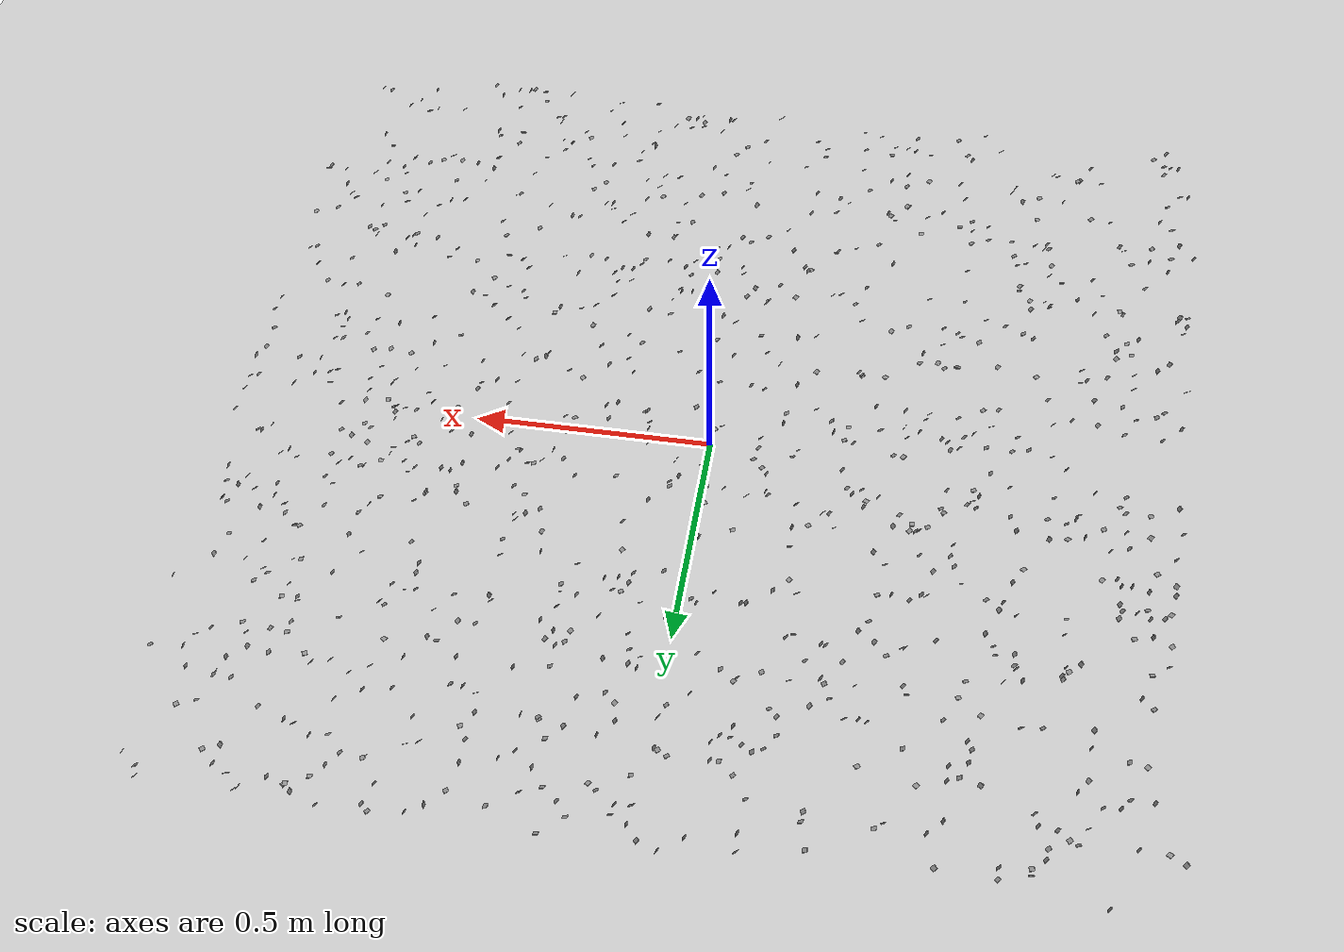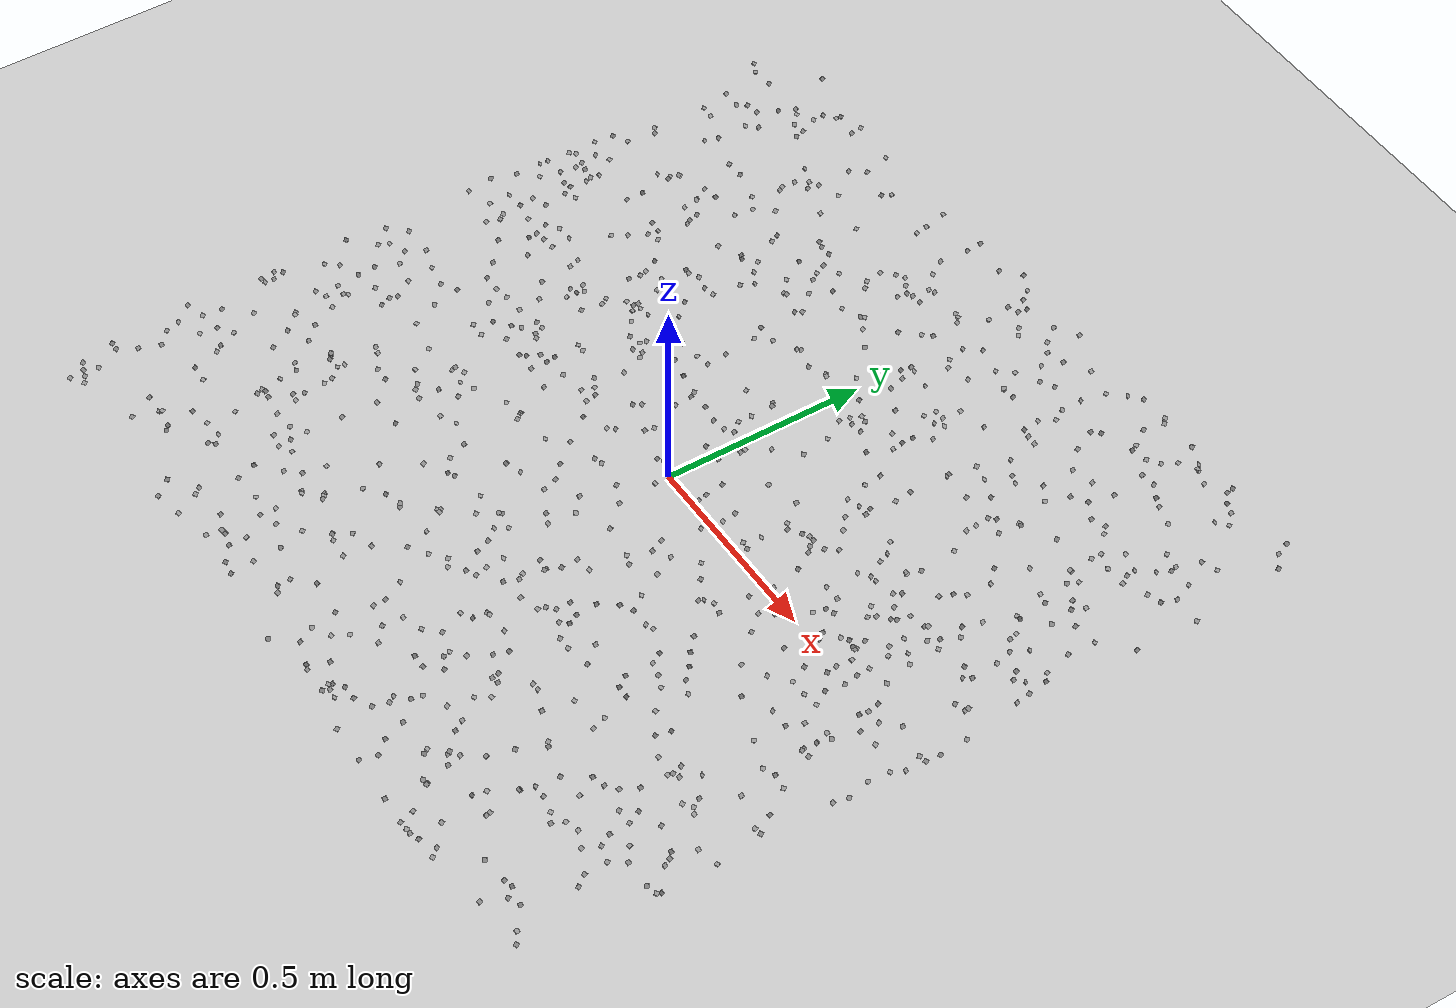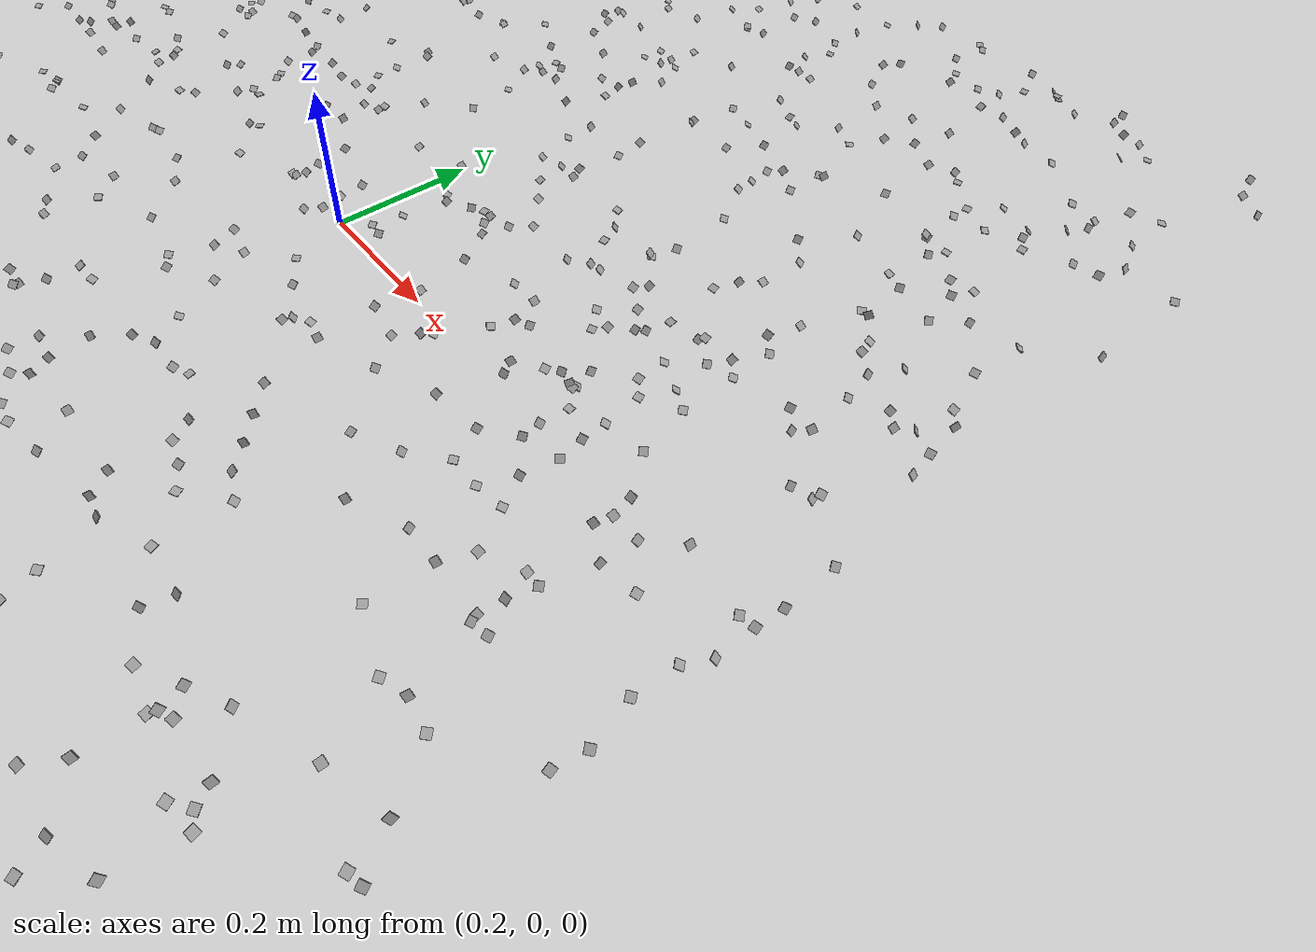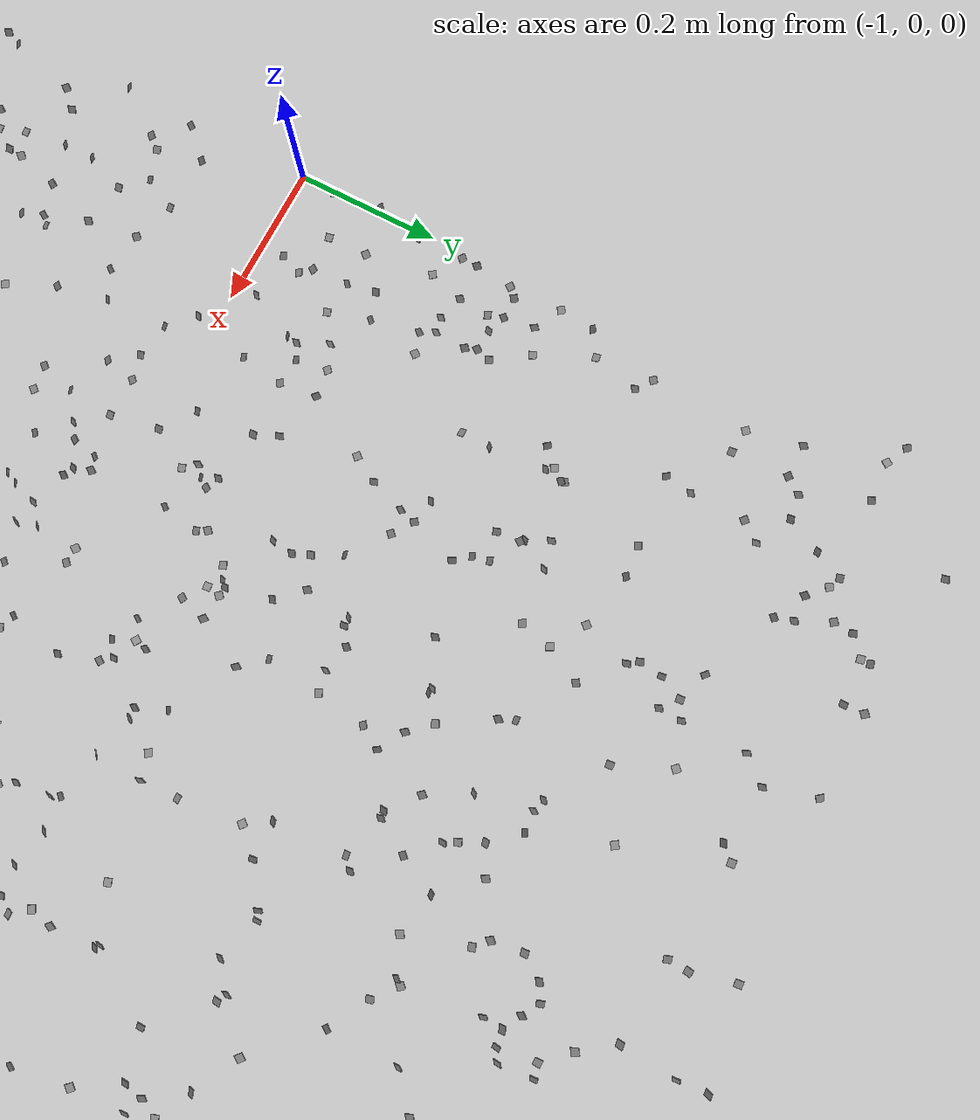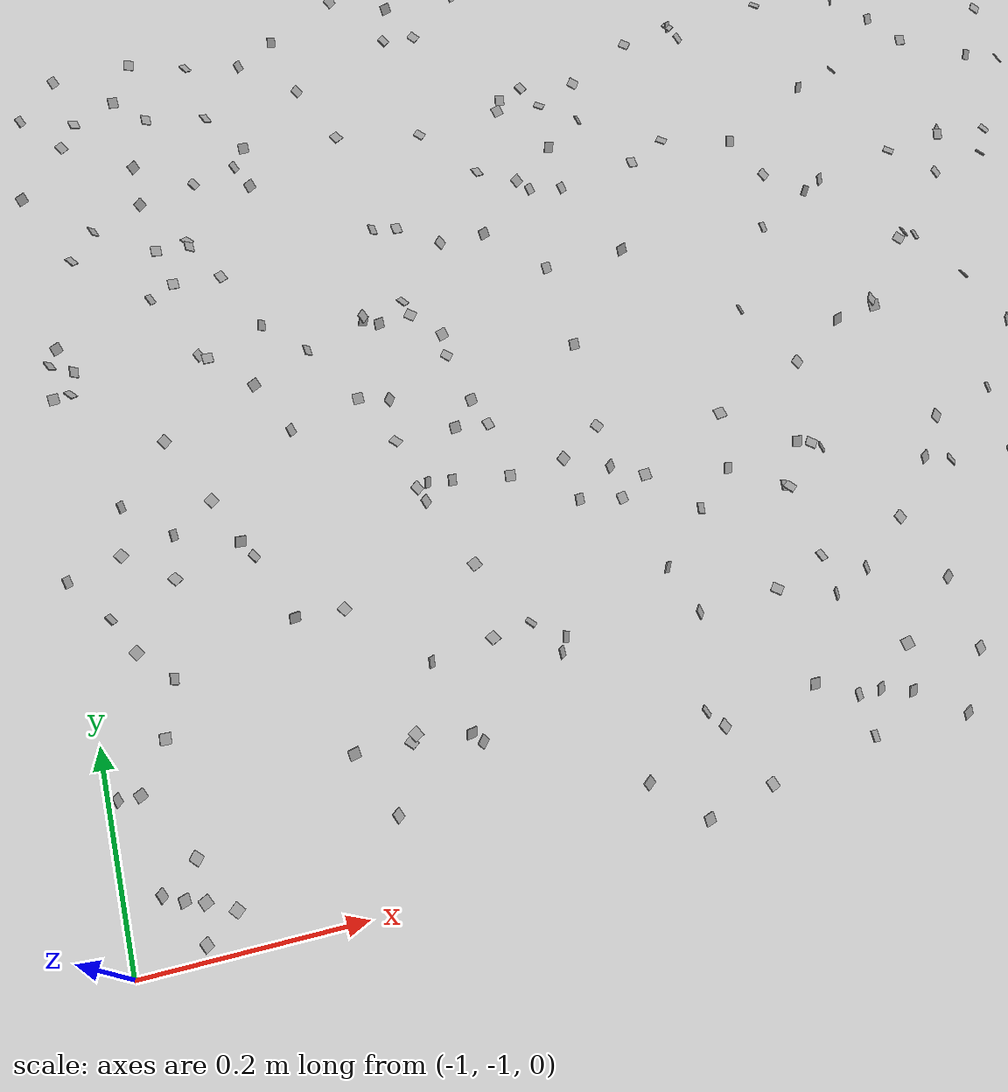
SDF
<sdf version="1.6">
 <world name="default">
  <physics name="default_physics" default="0" type="ode">
   <max_step_size>0.001</max_step_size>
   <real_time_factor>1</real_time_factor>
   <real_time_update_rate>1000</real_time_update_rate>
  </physics>
  <model name="ground_plane">
   <static>1</static>
   <link name="link">
    <collision name="collision">
     <geometry><plane><normal>0 0 1</normal><size>100 100</size></plane></geometry>
     <surface><friction><ode><mu>100</mu><mu2>50</mu2></ode></friction></surface>
    </collision>
    <visual name="visual">
     <cast_shadows>0</cast_shadows>
     <geometry><plane><normal>0 0 1</normal><size>100 100</size></plane></geometry>
     <material>
      <script><uri>file://media/materials/scripts/gazebo.material</uri><name>Gazebo/Grey</name></script>
     </material>
    </visual>
   </link>
  </model>
  <light name="sun" type="directional">
   <pose>0 0 10 0 -0 0</pose>
   <diffuse>0.8 0.8 0.8 1</diffuse>
   <specular>0.2 0.2 0.2 1</specular>
   <attenuation>
    <range>1000</range>
    <constant>0.9</constant>
    <linear>0.01</linear>
    <quadratic>0.001</quadratic>
   </attenuation>
   <direction>-0.5 0.1 -0.9</direction>
  </light>
  <gravity>0 0 -9.8</gravity>
  <magnetic_field>6e-06 2.3e-05 -4.2e-05</magnetic_field>
  <atmosphere type="adiabatic"/>
  <scene><ambient>0.4 0.4 0.4 1</ambient><background>0.7 0.7 0.7 1</background><shadows>1</shadows></scene>
  <spherical_coordinates>
   <surface_model>EARTH_WGS84</surface_model>
   <latitude_deg>0</latitude_deg>
   <longitude_deg>0</longitude_deg>
   <elevation>0</elevation>
   <heading_deg>0</heading_deg>
  </spherical_coordinates>
  <model name="SmokeParticle">
   <link name="link_0">
    <gravity>0</gravity>
    <collision name="collision">
     <pose>0 0 0.1 0 -0 0</pose>
     <geometry><box><size>0.01 0.01 0.001</size></box></geometry>
    </collision>
    <visual name="visual">
     <pose>0 0 0.1 0 -0 0</pose>
     <geometry><box><size>0.01 0.01 0.001</size></box></geometry>
     <material>
      <lighting>0</lighting>
      <script><uri>file://media/materials/scripts/gazebo.material</uri><name>Gazebo/Grey</name></script>
     </material>
     <cast_shadows>0</cast_shadows>
    </visual>
    <visual name="visual_0">
     <pose>-0.403876 0.201032 0.056829 0.108042 0.8212 0.885641</pose>
     <geometry><box><size>0.01 0.01 0.001</size></box></geometry>
     <material>
      <lighting>0</lighting>
      <script><uri>file://media/materials/scripts/gazebo.material</uri><name>Gazebo/Grey</name></script>
     </material>
     <cast_shadows>0</cast_shadows>
    </visual>
    <visual name="visual_1">
     <pose>0.531237 0.502478 0.05667 0.79739 0.439027 0.002231</pose>
     <geometry><box><size>0.01 0.01 0.001</size></box></geometry>
     <material>
      <lighting>0</lighting>
      <script><uri>file://media/materials/scripts/gazebo.material</uri><name>Gazebo/Grey</name></script>
     </material>
     <cast_shadows>0</cast_shadows>
    </visual>
    <visual name="visual_2">
     <pose>-0.303189 0.503655 0.048544 0.573679 0.632041 0.326188</pose>
     <geometry><box><size>0.01 0.01 0.001</size></box></geometry>
     <material>
      <lighting>0</lighting>
      <script><uri>file://media/materials/scripts/gazebo.material</uri><name>Gazebo/Grey</name></script>
     </material>
     <cast_shadows>0</cast_shadows>
    </visual>
    <visual name="visual_3">
     <pose>0.337808 0.869948 0.05264 0.186742 0.966265 0.682626</pose>
     <geometry><box><size>0.01 0.01 0.001</size></box></geometry>
     <material>
      <lighting>0</lighting>
      <script><uri>file://media/materials/scripts/gazebo.material</uri><name>Gazebo/Grey</name></script>
     </material>
     <cast_shadows>0</cast_shadows>
    </visual>
    <visual name="visual_4">
     <pose>-0.144451 0.606344 0.051718 0.946475 0.182837 0.846206</pose>
     <geometry><box><size>0.01 0.01 0.001</size></box></geometry>
     <material>
      <lighting>0</lighting>
      <script><uri>file://media/materials/scripts/gazebo.material</uri><name>Gazebo/Grey</name></script>
     </material>
     <cast_shadows>0</cast_shadows>
    </visual>
    <visual name="visual_5">
     <pose>-0.651433 0.166245 0.045094 0.015782 0.955401 0.346402</pose>
     <geometry><box><size>0.01 0.01 0.001</size></box></geometry>
     <material>
      <lighting>0</lighting>
      <script><uri>file://media/materials/scripts/gazebo.material</uri><name>Gazebo/Grey</name></script>
     </material>
     <cast_shadows>0</cast_shadows>
    </visual>
    <visual name="visual_6">
     <pose>0.578069 -0.810061 0.048152 0.291 0.38364 0.604591</pose>
     <geometry><box><size>0.01 0.01 0.001</size></box></geometry>
     <material>
      <lighting>0</lighting>
      <script><uri>file://media/materials/scripts/gazebo.material</uri><name>Gazebo/Grey</name></script>
     </material>
     <cast_shadows>0</cast_shadows>
    </visual>
    <visual name="visual_7">
     <pose>-0.631514 0.058186 0.048881 0.706505 0.495918 0.287768</pose>
     <geometry><box><size>0.01 0.01 0.001</size></box></geometry>
     <material>
      <lighting>0</lighting>
      <script><uri>file://media/materials/scripts/gazebo.material</uri><name>Gazebo/Grey</name></script>
     </material>
     <cast_shadows>0</cast_shadows>
    </visual>
    <visual name="visual_8">
     <pose>0.011175 0.489025 0.051853 0.229774 0.283695 0.915888</pose>
     <geometry><box><size>0.01 0.01 0.001</size></box></geometry>
     <material>
      <lighting>0</lighting>
      <script><uri>file://media/materials/scripts/gazebo.material</uri><name>Gazebo/Grey</name></script>
     </material>
     <cast_shadows>0</cast_shadows>
    </visual>
    <visual name="visual_9">
     <pose>0.397156 0.636628 0.047655 0.429425 0.81732 0.774265</pose>
     <geometry><box><size>0.01 0.01 0.001</size></box></geometry>
     <material>
      <lighting>0</lighting>
      <script><uri>file://media/materials/scripts/gazebo.material</uri><name>Gazebo/Grey</name></script>
     </material>
     <cast_shadows>0</cast_shadows>
    </visual>
    <visual name="visual_10">
     <pose>0.098187 -0.391062 0.05292 0.807868 0.976832 0.899319</pose>
     <geometry><box><size>0.01 0.01 0.001</size></box></geometry>
     <material>
      <lighting>0</lighting>
      <script><uri>file://media/materials/scripts/gazebo.material</uri><name>Gazebo/Grey</name></script>
     </material>
     <cast_shadows>0</cast_shadows>
    </visual>
    <visual name="visual_11">
     <pose>0.300777 -0.315212 0.054688 0.920543 0.686985 0.413204</pose>
     <geometry><box><size>0.01 0.01 0.001</size></box></geometry>
     <material>
      <lighting>0</lighting>
      <script><uri>file://media/materials/scripts/gazebo.material</uri><name>Gazebo/Grey</name></script>
     </material>
     <cast_shadows>0</cast_shadows>
    </visual>
    <visual name="visual_12">
     <pose>0.308576 0.263658 0.055673 0.042668 0.770459 0.391931</pose>
     <geometry><box><size>0.01 0.01 0.001</size></box></geometry>
     <material>
      <lighting>0</lighting>
      <script><uri>file://media/materials/scripts/gazebo.material</uri><name>Gazebo/Grey</name></script>
     </material>
     <cast_shadows>0</cast_shadows>
    </visual>
    <visual name="visual_13">
     <pose>-0.410405 -0.042917 0.04853 0.975091 0.817799 0.311912</pose>
     <geometry><box><size>0.01 0.01 0.001</size></box></geometry>
     <material>
      <lighting>0</lighting>
      <script><uri>file://media/materials/scripts/gazebo.material</uri><name>Gazebo/Grey</name></script>
     </material>
     <cast_shadows>0</cast_shadows>
    </visual>
    <visual name="visual_14">
     <pose>-0.576932 0.548454 0.051314 0.460421 0.051859 0.466505</pose>
     <geometry><box><size>0.01 0.01 0.001</size></box></geometry>
     <material>
      <lighting>0</lighting>
      <script><uri>file://media/materials/scripts/gazebo.material</uri><name>Gazebo/Grey</name></script>
     </material>
     <cast_shadows>0</cast_shadows>
    </visual>
    <visual name="visual_15">
     <pose>0.846734 0.737506 0.045892 0.993072 0.529106 0.936117</pose>
     <geometry><box><size>0.01 0.01 0.001</size></box></geometry>
     <material>
      <lighting>0</lighting>
      <script><uri>file://media/materials/scripts/gazebo.material</uri><name>Gazebo/Grey</name></script>
     </material>
     <cast_shadows>0</cast_shadows>
    </visual>
    <visual name="visual_16">
     <pose>0.834869 0.705066 0.050539 0.014904 0.894066 0.642223</pose>
     <geometry><box><size>0.01 0.01 0.001</size></box></geometry>
     <material>
      <lighting>0</lighting>
      <script><uri>file://media/materials/scripts/gazebo.material</uri><name>Gazebo/Grey</name></script>
     </material>
     <cast_shadows>0</cast_shadows>
    </visual>
    <visual name="visual_17">
     <pose>0.730316 0.978142 0.046723 0.828794 0.749482 0.678423</pose>
     <geometry><box><size>0.01 0.01 0.001</size></box></geometry>
     <material>
      <lighting>0</lighting>
      <script><uri>file://media/materials/scripts/gazebo.material</uri><name>Gazebo/Grey</name></script>
     </material>
     <cast_shadows>0</cast_shadows>
    </visual>
    <visual name="visual_18">
     <pose>-0.761732 -0.24575 0.054594 0.634281 0.133131 0.096937</pose>
     <geometry><box><size>0.01 0.01 0.001</size></box></geometry>
     <material>
      <lighting>0</lighting>
      <script><uri>file://media/materials/scripts/gazebo.material</uri><name>Gazebo/Grey</name></script>
     </material>
     <cast_shadows>0</cast_shadows>
    </visual>
    <visual name="visual_19">
     <pose>-0.045617 -0.583888 0.052504 0.327235 0.270863 0.925251</pose>
     <geometry><box><size>0.01 0.01 0.001</size></box></geometry>
     <material>
      <lighting>0</lighting>
      <script><uri>file://media/materials/scripts/gazebo.material</uri><name>Gazebo/Grey</name></script>
     </material>
     <cast_shadows>0</cast_shadows>
    </visual>
    <visual name="visual_20">
     <pose>-0.817893 0.735162 0.054391 0.319449 0.519729 0.935921</pose>
     <geometry><box><size>0.01 0.01 0.001</size></box></geometry>
     <material>
      <lighting>0</lighting>
      <script><uri>file://media/materials/scripts/gazebo.material</uri><name>Gazebo/Grey</name></script>
     </material>
     <cast_shadows>0</cast_shadows>
    </visual>
    <visual name="visual_21">
     <pose>-0.642688 -0.647226 0.052325 0.660815 0.64387 0.264233</pose>
     <geometry><box><size>0.01 0.01 0.001</size></box></geometry>
     <material>
      <lighting>0</lighting>
      <script><uri>file://media/materials/scripts/gazebo.material</uri><name>Gazebo/Grey</name></script>
     </material>
     <cast_shadows>0</cast_shadows>
    </visual>
    <visual name="visual_22">
     <pose>0.522241 -0.438063 0.053474 0.976436 0.095806 0.005561</pose>
     <geometry><box><size>0.01 0.01 0.001</size></box></geometry>
     <material>
      <lighting>0</lighting>
      <script><uri>file://media/materials/scripts/gazebo.material</uri><name>Gazebo/Grey</name></script>
     </material>
     <cast_shadows>0</cast_shadows>
    </visual>
    <visual name="visual_23">
     <pose>0.066282 0.607954 0.056216 0.163224 0.728709 0.568907</pose>
     <geometry><box><size>0.01 0.01 0.001</size></box></geometry>
     <material>
      <lighting>0</lighting>
      <script><uri>file://media/materials/scripts/gazebo.material</uri><name>Gazebo/Grey</name></script>
     </material>
     <cast_shadows>0</cast_shadows>
    </visual>
    <visual name="visual_24">
     <pose>-0.029329 0.435786 0.052046 0.247702 0.56695 0.08611</pose>
     <geometry><box><size>0.01 0.01 0.001</size></box></geometry>
     <material>
      <lighting>0</lighting>
      <script><uri>file://media/materials/scripts/gazebo.material</uri><name>Gazebo/Grey</name></script>
     </material>
     <cast_shadows>0</cast_shadows>
    </visual>
    <visual name="visual_25">
     <pose>0.293385 0.31951 0.056153 0.246872 0.422986 0.985333</pose>
     <geometry><box><size>0.01 0.01 0.001</size></box></geometry>
     <material>
      <lighting>0</lighting>
      <script><uri>file://media/materials/scripts/gazebo.material</uri><name>Gazebo/Grey</name></script>
     </material>
     <cast_shadows>0</cast_shadows>
    </visual>
    <visual name="visual_26">
     <pose>-0.38581 -0.642819 0.055976 0.024769 0.06541 0.172901</pose>
     <geometry><box><size>0.01 0.01 0.001</size></box></geometry>
     <material>
      <lighting>0</lighting>
      <script><uri>file://media/materials/scripts/gazebo.material</uri><name>Gazebo/Grey</name></script>
     </material>
     <cast_shadows>0</cast_shadows>
    </visual>
    <visual name="visual_27">
     <pose>0.823388 -0.492416 0.051499 0.246614 0.302792 0.458589</pose>
     <geometry><box><size>0.01 0.01 0.001</size></box></geometry>
     <material>
      <lighting>0</lighting>
      <script><uri>file://media/materials/scripts/gazebo.material</uri><name>Gazebo/Grey</name></script>
     </material>
     <cast_shadows>0</cast_shadows>
    </visual>
    <visual name="visual_28">
     <pose>0.120698 0.953629 0.053968 0.491025 0.241652 0.053772</pose>
     <geometry><box><size>0.01 0.01 0.001</size></box></geometry>
     <material>
      <lighting>0</lighting>
      <script><uri>file://media/materials/scripts/gazebo.material</uri><name>Gazebo/Grey</name></script>
     </material>
     <cast_shadows>0</cast_shadows>
    </visual>
    <visual name="visual_29">
     <pose>0.255818 0.165075 0.053533 0.285625 0.793932 0.137201</pose>
     <geometry><box><size>0.01 0.01 0.001</size></box></geometry>
     <material>
      <lighting>0</lighting>
      <script><uri>file://media/materials/scripts/gazebo.material</uri><name>Gazebo/Grey</name></script>
     </material>
     <cast_shadows>0</cast_shadows>
    </visual>
    <visual name="visual_30">
     <pose>-0.700225 -0.807038 0.045482 0.863717 0.922142 0.640801</pose>
     <geometry><box><size>0.01 0.01 0.001</size></box></geometry>
     <material>
      <lighting>0</lighting>
      <script><uri>file://media/materials/scripts/gazebo.material</uri><name>Gazebo/Grey</name></script>
     </material>
     <cast_shadows>0</cast_shadows>
    </visual>
    <visual name="visual_31">
     <pose>-0.21398 0.363952 0.054486 0.134308 0.039396 0.872704</pose>
     <geometry><box><size>0.01 0.01 0.001</size></box></geometry>
     <material>
      <lighting>0</lighting>
      <script><uri>file://media/materials/scripts/gazebo.material</uri><name>Gazebo/Grey</name></script>
     </material>
     <cast_shadows>0</cast_shadows>
    </visual>
    <visual name="visual_32">
     <pose>0.364509 -0.989499 0.045493 0.632605 0.277005 0.021787</pose>
     <geometry><box><size>0.01 0.01 0.001</size></box></geometry>
     <material>
      <lighting>0</lighting>
      <script><uri>file://media/materials/scripts/gazebo.material</uri><name>Gazebo/Grey</name></script>
     </material>
     <cast_shadows>0</cast_shadows>
    </visual>
    <visual name="visual_33">
     <pose>-0.392403 0.763778 0.046458 0.13797 0.062353 0.616356</pose>
     <geometry><box><size>0.01 0.01 0.001</size></box></geometry>
     <material>
      <lighting>0</lighting>
      <script><uri>file://media/materials/scripts/gazebo.material</uri><name>Gazebo/Grey</name></script>
     </material>
     <cast_shadows>0</cast_shadows>
    </visual>
    <visual name="visual_34">
     <pose>-0.120125 0.79414 0.049514 0.441026 0.850128 0.484601</pose>
     <geometry><box><size>0.01 0.01 0.001</size></box></geometry>
     <material>
      <lighting>0</lighting>
      <script><uri>file://media/materials/scripts/gazebo.material</uri><name>Gazebo/Grey</name></script>
     </material>
     <cast_shadows>0</cast_shadows>
    </visual>
    <visual name="visual_35">
     <pose>0.502444 -0.766406 0.05306 0.529834 0.118632 0.057238</pose>
     <geometry><box><size>0.01 0.01 0.001</size></box></geometry>
     <material>
      <lighting>0</lighting>
      <script><uri>file://media/materials/scripts/gazebo.material</uri><name>Gazebo/Grey</name></script>
     </material>
     <cast_shadows>0</cast_shadows>
    </visual>
    <visual name="visual_36">
     <pose>0.4053 -0.782898 0.047053 0.740959 0.54699 0.152739</pose>
     <geometry><box><size>0.01 0.01 0.001</size></box></geometry>
     <material>
      <lighting>0</lighting>
      <script><uri>file://media/materials/scripts/gazebo.material</uri><name>Gazebo/Grey</name></script>
     </material>
     <cast_shadows>0</cast_shadows>
    </visual>
    <visual name="visual_37">
     <pose>-0.436132 0.893267 0.053836 0.249006 0.26953 0.143698</pose>
     <geometry><box><size>0.01 0.01 0.001</size></box></geometry>
     <material>
      <lighting>0</lighting>
      <script><uri>file://media/materials/scripts/gazebo.material</uri><name>Gazebo/Grey</name></script>
     </material>
     <cast_shadows>0</cast_shadows>
    </visual>
    <visual name="visual_38">
     <pose>-0.013197 -0.832223 0.045991 0.977919 0.595238 0.863061</pose>
     <geometry><box><size>0.01 0.01 0.001</size></box></geometry>
     <material>
      <lighting>0</lighting>
      <script><uri>file://media/materials/scripts/gazebo.material</uri><name>Gazebo/Grey</name></script>
     </material>
     <cast_shadows>0</cast_shadows>
    </visual>
    <visual name="visual_39">
     <pose>0.016963 -0.755619 0.049712 0.467758 0.197396 0.329848</pose>
     <geometry><box><size>0.01 0.01 0.001</size></box></geometry>
     <material>
      <lighting>0</lighting>
      <script><uri>file://media/materials/scripts/gazebo.material</uri><name>Gazebo/Grey</name></script>
     </material>
     <cast_shadows>0</cast_shadows>
    </visual>
    <visual name="visual_40">
     <pose>0.769605 0.625534 0.047396 0.317545 0.231069 0.992384</pose>
     <geometry><box><size>0.01 0.01 0.001</size></box></geometry>
     <material>
      <lighting>0</lighting>
      <script><uri>file://media/materials/scripts/gazebo.material</uri><name>Gazebo/Grey</name></script>
     </material>
     <cast_shadows>0</cast_shadows>
    </visual>
    <visual name="visual_41">
     <pose>-0.022262 -0.39731 0.047425 0.175624 0.464431 0.709718</pose>
     <geometry><box><size>0.01 0.01 0.001</size></box></geometry>
     <material>
      <lighting>0</lighting>
      <script><uri>file://media/materials/scripts/gazebo.material</uri><name>Gazebo/Grey</name></script>
     </material>
     <cast_shadows>0</cast_shadows>
    </visual>
    <visual name="visual_42">
     <pose>0.969995 0.242089 0.047685 0.025647 0.922314 0.229122</pose>
     <geometry><box><size>0.01 0.01 0.001</size></box></geometry>
     <material>
      <lighting>0</lighting>
      <script><uri>file://media/materials/scripts/gazebo.material</uri><name>Gazebo/Grey</name></script>
     </material>
     <cast_shadows>0</cast_shadows>
    </visual>
    <visual name="visual_43">
     <pose>0.942083 -0.530075 0.054176 0.160305 0.380054 0.144082</pose>
     <geometry><box><size>0.01 0.01 0.001</size></box></geometry>
     <material>
      <lighting>0</lighting>
      <script><uri>file://media/materials/scripts/gazebo.material</uri><name>Gazebo/Grey</name></script>
     </material>
     <cast_shadows>0</cast_shadows>
    </visual>
    <visual name="visual_44">
     <pose>-0.607064 -0.793079 0.045469 0.193834 0.834429 0.873405</pose>
     <geometry><box><size>0.01 0.01 0.001</size></box></geometry>
     <material>
      <lighting>0</lighting>
      <script><uri>file://media/materials/scripts/gazebo.material</uri><name>Gazebo/Grey</name></script>
     </material>
     <cast_shadows>0</cast_shadows>
    </visual>
    <visual name="visual_45">
     <pose>0.941499 -0.356109 0.048183 0.908163 0.731076 0.62119</pose>
     <geometry><box><size>0.01 0.01 0.001</size></box></geometry>
     <material>
      <lighting>0</lighting>
      <script><uri>file://media/materials/scripts/gazebo.material</uri><name>Gazebo/Grey</name></script>
     </material>
     <cast_shadows>0</cast_shadows>
    </visual>
    <visual name="visual_46">
     <pose>0.766091 -0.201917 0.053734 0.689053 0.716048 0.082572</pose>
     <geometry><box><size>0.01 0.01 0.001</size></box></geometry>
     <material>
      <lighting>0</lighting>
      <script><uri>file://media/materials/scripts/gazebo.material</uri><name>Gazebo/Grey</name></script>
     </material>
     <cast_shadows>0</cast_shadows>
    </visual>
    <visual name="visual_47">
     <pose>0.865239 -0.292931 0.055416 0.651078 0.8537 0.196032</pose>
     <geometry><box><size>0.01 0.01 0.001</size></box></geometry>
     <material>
      <lighting>0</lighting>
      <script><uri>file://media/materials/scripts/gazebo.material</uri><name>Gazebo/Grey</name></script>
     </material>
     <cast_shadows>0</cast_shadows>
    </visual>
    <visual name="visual_48">
     <pose>0.196207 -0.952144 0.052219 0.01447 0.559505 0.951518</pose>
     <geometry><box><size>0.01 0.01 0.001</size></box></geometry>
     <material>
      <lighting>0</lighting>
      <script><uri>file://media/materials/scripts/gazebo.material</uri><name>Gazebo/Grey</name></script>
     </material>
     <cast_shadows>0</cast_shadows>
    </visual>
    <visual name="visual_49">
     <pose>-0.917597 0.325904 0.046689 0.424804 0.196566 0.333436</pose>
     <geometry><box><size>0.01 0.01 0.001</size></box></geometry>
     <material>
      <lighting>0</lighting>
      <script><uri>file://media/materials/scripts/gazebo.material</uri><name>Gazebo/Grey</name></script>
     </material>
     <cast_shadows>0</cast_shadows>
    </visual>
    <visual name="visual_50">
     <pose>-0.215992 0.753246 0.04847 0.685022 0.205689 0.611405</pose>
     <geometry><box><size>0.01 0.01 0.001</size></box></geometry>
     <material>
      <lighting>0</lighting>
      <script><uri>file://media/materials/scripts/gazebo.material</uri><name>Gazebo/Grey</name></script>
     </material>
     <cast_shadows>0</cast_shadows>
    </visual>
    <visual name="visual_51">
     <pose>0.095758 0.206497 0.055634 0.010717 0.937218 0.377628</pose>
     <geometry><box><size>0.01 0.01 0.001</size></box></geometry>
     <material>
      <lighting>0</lighting>
      <script><uri>file://media/materials/scripts/gazebo.material</uri><name>Gazebo/Grey</name></script>
     </material>
     <cast_shadows>0</cast_shadows>
    </visual>
    <visual name="visual_52">
     <pose>-0.322937 -0.684098 0.0483 0.651409 0.352056 0.030762</pose>
     <geometry><box><size>0.01 0.01 0.001</size></box></geometry>
     <material>
      <lighting>0</lighting>
      <script><uri>file://media/materials/scripts/gazebo.material</uri><name>Gazebo/Grey</name></script>
     </material>
     <cast_shadows>0</cast_shadows>
    </visual>
    <visual name="visual_53">
     <pose>0.380661 -0.154213 0.049568 0.151005 0.95284 0.935334</pose>
     <geometry><box><size>0.01 0.01 0.001</size></box></geometry>
     <material>
      <lighting>0</lighting>
      <script><uri>file://media/materials/scripts/gazebo.material</uri><name>Gazebo/Grey</name></script>
     </material>
     <cast_shadows>0</cast_shadows>
    </visual>
    <visual name="visual_54">
     <pose>0.15624 -0.944487 0.050698 0.103885 0.616623 0.808872</pose>
     <geometry><box><size>0.01 0.01 0.001</size></box></geometry>
     <material>
      <lighting>0</lighting>
      <script><uri>file://media/materials/scripts/gazebo.material</uri><name>Gazebo/Grey</name></script>
     </material>
     <cast_shadows>0</cast_shadows>
    </visual>
    <visual name="visual_55">
     <pose>-0.301309 -0.006055 0.055393 0.823203 0.245732 0.873163</pose>
     <geometry><box><size>0.01 0.01 0.001</size></box></geometry>
     <material>
      <lighting>0</lighting>
      <script><uri>file://media/materials/scripts/gazebo.material</uri><name>Gazebo/Grey</name></script>
     </material>
     <cast_shadows>0</cast_shadows>
    </visual>
    <visual name="visual_56">
     <pose>0.589054 -0.088016 0.055942 0.791851 0.403335 0.218387</pose>
     <geometry><box><size>0.01 0.01 0.001</size></box></geometry>
     <material>
      <lighting>0</lighting>
      <script><uri>file://media/materials/scripts/gazebo.material</uri><name>Gazebo/Grey</name></script>
     </material>
     <cast_shadows>0</cast_shadows>
    </visual>
    <visual name="visual_57">
     <pose>0.519472 -0.707061 0.05494 0.818739 0.213032 0.786239</pose>
     <geometry><box><size>0.01 0.01 0.001</size></box></geometry>
     <material>
      <lighting>0</lighting>
      <script><uri>file://media/materials/scripts/gazebo.material</uri><name>Gazebo/Grey</name></script>
     </material>
     <cast_shadows>0</cast_shadows>
    </visual>
    <visual name="visual_58">
     <pose>0.758345 0.955291 0.050715 0.993579 0.361576 0.133383</pose>
     <geometry><box><size>0.01 0.01 0.001</size></box></geometry>
     <material>
      <lighting>0</lighting>
      <script><uri>file://media/materials/scripts/gazebo.material</uri><name>Gazebo/Grey</name></script>
     </material>
     <cast_shadows>0</cast_shadows>
    </visual>
    <visual name="visual_59">
     <pose>-0.83802 -0.470679 0.051715 0.004745 0.174608 0.080997</pose>
     <geometry><box><size>0.01 0.01 0.001</size></box></geometry>
     <material>
      <lighting>0</lighting>
      <script><uri>file://media/materials/scripts/gazebo.material</uri><name>Gazebo/Grey</name></script>
     </material>
     <cast_shadows>0</cast_shadows>
    </visual>
    <visual name="visual_60">
     <pose>0.738257 -0.440956 0.051077 0.690943 0.80284 0.863043</pose>
     <geometry><box><size>0.01 0.01 0.001</size></box></geometry>
     <material>
      <lighting>0</lighting>
      <script><uri>file://media/materials/scripts/gazebo.material</uri><name>Gazebo/Grey</name></script>
     </material>
     <cast_shadows>0</cast_shadows>
    </visual>
    <visual name="visual_61">
     <pose>0.757206 0.681474 0.048761 0.055807 0.544345 0.462692</pose>
     <geometry><box><size>0.01 0.01 0.001</size></box></geometry>
     <material>
      <lighting>0</lighting>
      <script><uri>file://media/materials/scripts/gazebo.material</uri><name>Gazebo/Grey</name></script>
     </material>
     <cast_shadows>0</cast_shadows>
    </visual>
    <visual name="visual_62">
     <pose>0.535498 0.019883 0.052177 0.228105 0.120196 0.998497</pose>
     <geometry><box><size>0.01 0.01 0.001</size></box></geometry>
     <material>
      <lighting>0</lighting>
      <script><uri>file://media/materials/scripts/gazebo.material</uri><name>Gazebo/Grey</name></script>
     </material>
     <cast_shadows>0</cast_shadows>
    </visual>
    <visual name="visual_63">
     <pose>-0.86857 0.336003 0.048536 0.591574 0.400067 0.92906</pose>
     <geometry><box><size>0.01 0.01 0.001</size></box></geometry>
     <material>
      <lighting>0</lighting>
      <script><uri>file://media/materials/scripts/gazebo.material</uri><name>Gazebo/Grey</name></script>
     </material>
     <cast_shadows>0</cast_shadows>
    </visual>
    <visual name="visual_64">
     <pose>0.213019 0.749092 0.050575 0.416358 0.089594 0.799401</pose>
     <geometry><box><size>0.01 0.01 0.001</size></box></geometry>
     <material>
      <lighting>0</lighting>
      <script><uri>file://media/materials/scripts/gazebo.material</uri><name>Gazebo/Grey</name></script>
     </material>
     <cast_shadows>0</cast_shadows>
    </visual>
    <visual name="visual_65">
     <pose>-0.810031 -0.388869 0.056493 0.33017 0.381789 0.600423</pose>
     <geometry><box><size>0.01 0.01 0.001</size></box></geometry>
     <material>
      <lighting>0</lighting>
      <script><uri>file://media/materials/scripts/gazebo.material</uri><name>Gazebo/Grey</name></script>
     </material>
     <cast_shadows>0</cast_shadows>
    </visual>
    <visual name="visual_66">
     <pose>0.693321 0.200213 0.047659 0.956223 0.733909 0.81214</pose>
     <geometry><box><size>0.01 0.01 0.001</size></box></geometry>
     <material>
      <lighting>0</lighting>
      <script><uri>file://media/materials/scripts/gazebo.material</uri><name>Gazebo/Grey</name></script>
     </material>
     <cast_shadows>0</cast_shadows>
    </visual>
    <visual name="visual_67">
     <pose>-0.070957 -0.392652 0.048012 0.415404 0.352107 0.028115</pose>
     <geometry><box><size>0.01 0.01 0.001</size></box></geometry>
     <material>
      <lighting>0</lighting>
      <script><uri>file://media/materials/scripts/gazebo.material</uri><name>Gazebo/Grey</name></script>
     </material>
     <cast_shadows>0</cast_shadows>
    </visual>
    <visual name="visual_68">
     <pose>-0.789547 0.863283 0.050719 0.055223 0.326572 0.612917</pose>
     <geometry><box><size>0.01 0.01 0.001</size></box></geometry>
     <material>
      <lighting>0</lighting>
      <script><uri>file://media/materials/scripts/gazebo.material</uri><name>Gazebo/Grey</name></script>
     </material>
     <cast_shadows>0</cast_shadows>
    </visual>
    <visual name="visual_69">
     <pose>-0.708497 -0.543581 0.04716 0.437772 0.080468 0.063826</pose>
     <geometry><box><size>0.01 0.01 0.001</size></box></geometry>
     <material>
      <lighting>0</lighting>
      <script><uri>file://media/materials/scripts/gazebo.material</uri><name>Gazebo/Grey</name></script>
     </material>
     <cast_shadows>0</cast_shadows>
    </visual>
    <visual name="visual_70">
     <pose>0.258046 -0.845973 0.050707 0.170056 0.974934 0.571498</pose>
     <geometry><box><size>0.01 0.01 0.001</size></box></geometry>
     <material>
      <lighting>0</lighting>
      <script><uri>file://media/materials/scripts/gazebo.material</uri><name>Gazebo/Grey</name></script>
     </material>
     <cast_shadows>0</cast_shadows>
    </visual>
    <visual name="visual_71">
     <pose>-0.839839 0.196122 0.053419 0.974507 0.360025 0.83491</pose>
     <geometry><box><size>0.01 0.01 0.001</size></box></geometry>
     <material>
      <lighting>0</lighting>
      <script><uri>file://media/materials/scripts/gazebo.material</uri><name>Gazebo/Grey</name></script>
     </material>
     <cast_shadows>0</cast_shadows>
    </visual>
    <visual name="visual_72">
     <pose>0.770468 -0.611533 0.054038 0.653621 0.505907 0.689026</pose>
     <geometry><box><size>0.01 0.01 0.001</size></box></geometry>
     <material>
      <lighting>0</lighting>
      <script><uri>file://media/materials/scripts/gazebo.material</uri><name>Gazebo/Grey</name></script>
     </material>
     <cast_shadows>0</cast_shadows>
    </visual>
    <visual name="visual_73">
     <pose>0.062292 -0.528607 0.053587 0.618038 0.54258 0.473848</pose>
     <geometry><box><size>0.01 0.01 0.001</size></box></geometry>
     <material>
      <lighting>0</lighting>
      <script><uri>file://media/materials/scripts/gazebo.material</uri><name>Gazebo/Grey</name></script>
     </material>
     <cast_shadows>0</cast_shadows>
    </visual>
    <visual name="visual_74">
     <pose>-0.054783 0.996612 0.051869 0.95629 0.668162 0.860631</pose>
     <geometry><box><size>0.01 0.01 0.001</size></box></geometry>
     <material>
      <lighting>0</lighting>
      <script><uri>file://media/materials/scripts/gazebo.material</uri><name>Gazebo/Grey</name></script>
     </material>
     <cast_shadows>0</cast_shadows>
    </visual>
    <visual name="visual_75">
     <pose>0.635532 0.680515 0.04859 0.611399 0.722308 0.206527</pose>
     <geometry><box><size>0.01 0.01 0.001</size></box></geometry>
     <material>
      <lighting>0</lighting>
      <script><uri>file://media/materials/scripts/gazebo.material</uri><name>Gazebo/Grey</name></script>
     </material>
     <cast_shadows>0</cast_shadows>
    </visual>
    <visual name="visual_76">
     <pose>-0.856322 0.257949 0.046145 0.884857 0.545402 0.98219</pose>
     <geometry><box><size>0.01 0.01 0.001</size></box></geometry>
     <material>
      <lighting>0</lighting>
      <script><uri>file://media/materials/scripts/gazebo.material</uri><name>Gazebo/Grey</name></script>
     </material>
     <cast_shadows>0</cast_shadows>
    </visual>
    <visual name="visual_77">
     <pose>-0.925431 0.688499 0.051748 0.083293 0.251688 0.722565</pose>
     <geometry><box><size>0.01 0.01 0.001</size></box></geometry>
     <material>
      <lighting>0</lighting>
      <script><uri>file://media/materials/scripts/gazebo.material</uri><name>Gazebo/Grey</name></script>
     </material>
     <cast_shadows>0</cast_shadows>
    </visual>
    <visual name="visual_78">
     <pose>-0.091873 -0.437679 0.052163 0.480677 0.348777 0.744971</pose>
     <geometry><box><size>0.01 0.01 0.001</size></box></geometry>
     <material>
      <lighting>0</lighting>
      <script><uri>file://media/materials/scripts/gazebo.material</uri><name>Gazebo/Grey</name></script>
     </material>
     <cast_shadows>0</cast_shadows>
    </visual>
    <visual name="visual_79">
     <pose>0.826414 -0.139169 0.051197 0.190747 0.46849 0.120809</pose>
     <geometry><box><size>0.01 0.01 0.001</size></box></geometry>
     <material>
      <lighting>0</lighting>
      <script><uri>file://media/materials/scripts/gazebo.material</uri><name>Gazebo/Grey</name></script>
     </material>
     <cast_shadows>0</cast_shadows>
    </visual>
    <visual name="visual_80">
     <pose>-0.453986 0.370778 0.045639 0.587745 0.497606 0.786881</pose>
     <geometry><box><size>0.01 0.01 0.001</size></box></geometry>
     <material>
      <lighting>0</lighting>
      <script><uri>file://media/materials/scripts/gazebo.material</uri><name>Gazebo/Grey</name></script>
     </material>
     <cast_shadows>0</cast_shadows>
    </visual>
    <visual name="visual_81">
     <pose>0.127181 0.33372 0.045917 0.139957 0.224322 0.786421</pose>
     <geometry><box><size>0.01 0.01 0.001</size></box></geometry>
     <material>
      <lighting>0</lighting>
      <script><uri>file://media/materials/scripts/gazebo.material</uri><name>Gazebo/Grey</name></script>
     </material>
     <cast_shadows>0</cast_shadows>
    </visual>
    <visual name="visual_82">
     <pose>0.909202 0.661734 0.049704 0.896298 0.150608 0.364266</pose>
     <geometry><box><size>0.01 0.01 0.001</size></box></geometry>
     <material>
      <lighting>0</lighting>
      <script><uri>file://media/materials/scripts/gazebo.material</uri><name>Gazebo/Grey</name></script>
     </material>
     <cast_shadows>0</cast_shadows>
    </visual>
    <visual name="visual_83">
     <pose>0.236241 0.571317 0.049093 0.186972 0.521768 0.812267</pose>
     <geometry><box><size>0.01 0.01 0.001</size></box></geometry>
     <material>
      <lighting>0</lighting>
      <script><uri>file://media/materials/scripts/gazebo.material</uri><name>Gazebo/Grey</name></script>
     </material>
     <cast_shadows>0</cast_shadows>
    </visual>
    <visual name="visual_84">
     <pose>-0.733152 -0.873382 0.053097 0.03398 0.591934 0.769775</pose>
     <geometry><box><size>0.01 0.01 0.001</size></box></geometry>
     <material>
      <lighting>0</lighting>
      <script><uri>file://media/materials/scripts/gazebo.material</uri><name>Gazebo/Grey</name></script>
     </material>
     <cast_shadows>0</cast_shadows>
    </visual>
    <visual name="visual_85">
     <pose>0.123649 0.059237 0.053383 0.915891 0.623174 0.662115</pose>
     <geometry><box><size>0.01 0.01 0.001</size></box></geometry>
     <material>
      <lighting>0</lighting>
      <script><uri>file://media/materials/scripts/gazebo.material</uri><name>Gazebo/Grey</name></script>
     </material>
     <cast_shadows>0</cast_shadows>
    </visual>
    <visual name="visual_86">
     <pose>-0.110739 0.58952 0.049217 0.153779 0.494675 0.329377</pose>
     <geometry><box><size>0.01 0.01 0.001</size></box></geometry>
     <material>
      <lighting>0</lighting>
      <script><uri>file://media/materials/scripts/gazebo.material</uri><name>Gazebo/Grey</name></script>
     </material>
     <cast_shadows>0</cast_shadows>
    </visual>
    <visual name="visual_87">
     <pose>-0.683576 -0.594747 0.046174 0.029481 0.452774 0.757224</pose>
     <geometry><box><size>0.01 0.01 0.001</size></box></geometry>
     <material>
      <lighting>0</lighting>
      <script><uri>file://media/materials/scripts/gazebo.material</uri><name>Gazebo/Grey</name></script>
     </material>
     <cast_shadows>0</cast_shadows>
    </visual>
    <visual name="visual_88">
     <pose>-0.232944 0.394928 0.056202 0.800668 0.462216 0.170317</pose>
     <geometry><box><size>0.01 0.01 0.001</size></box></geometry>
     <material>
      <lighting>0</lighting>
      <script><uri>file://media/materials/scripts/gazebo.material</uri><name>Gazebo/Grey</name></script>
     </material>
     <cast_shadows>0</cast_shadows>
    </visual>
    <visual name="visual_89">
     <pose>0.739975 0.808108 0.055382 0.394952 0.400484 0.841388</pose>
     <geometry><box><size>0.01 0.01 0.001</size></box></geometry>
     <material>
      <lighting>0</lighting>
      <script><uri>file://media/materials/scripts/gazebo.material</uri><name>Gazebo/Grey</name></script>
     </material>
     <cast_shadows>0</cast_shadows>
    </visual>
    <visual name="visual_90">
     <pose>-0.663164 -0.043322 0.052947 0.380164 0.538994 0.350941</pose>
     <geometry><box><size>0.01 0.01 0.001</size></box></geometry>
     <material>
      <lighting>0</lighting>
      <script><uri>file://media/materials/scripts/gazebo.material</uri><name>Gazebo/Grey</name></script>
     </material>
     <cast_shadows>0</cast_shadows>
    </visual>
    <visual name="visual_91">
     <pose>0.493507 -0.90247 0.046495 0.704246 0.899374 0.546672</pose>
     <geometry><box><size>0.01 0.01 0.001</size></box></geometry>
     <material>
      <lighting>0</lighting>
      <script><uri>file://media/materials/scripts/gazebo.material</uri><name>Gazebo/Grey</name></script>
     </material>
     <cast_shadows>0</cast_shadows>
    </visual>
    <visual name="visual_92">
     <pose>-0.068478 -0.387012 0.045012 0.894745 0.064348 0.911923</pose>
     <geometry><box><size>0.01 0.01 0.001</size></box></geometry>
     <material>
      <lighting>0</lighting>
      <script><uri>file://media/materials/scripts/gazebo.material</uri><name>Gazebo/Grey</name></script>
     </material>
     <cast_shadows>0</cast_shadows>
    </visual>
    <visual name="visual_93">
     <pose>-0.664766 -0.642913 0.049226 0.916092 0.81467 0.615034</pose>
     <geometry><box><size>0.01 0.01 0.001</size></box></geometry>
     <material>
      <lighting>0</lighting>
      <script><uri>file://media/materials/scripts/gazebo.material</uri><name>Gazebo/Grey</name></script>
     </material>
     <cast_shadows>0</cast_shadows>
    </visual>
    <visual name="visual_94">
     <pose>-0.566009 0.591313 0.056851 0.205427 0.03589 0.455073</pose>
     <geometry><box><size>0.01 0.01 0.001</size></box></geometry>
     <material>
      <lighting>0</lighting>
      <script><uri>file://media/materials/scripts/gazebo.material</uri><name>Gazebo/Grey</name></script>
     </material>
     <cast_shadows>0</cast_shadows>
    </visual>
    <visual name="visual_95">
     <pose>-0.422938 -0.447901 0.049298 0.954547 0.103867 0.373969</pose>
     <geometry><box><size>0.01 0.01 0.001</size></box></geometry>
     <material>
      <lighting>0</lighting>
      <script><uri>file://media/materials/scripts/gazebo.material</uri><name>Gazebo/Grey</name></script>
     </material>
     <cast_shadows>0</cast_shadows>
    </visual>
    <visual name="visual_96">
     <pose>-0.802478 -0.132503 0.053316 0.186961 0.623037 0.717382</pose>
     <geometry><box><size>0.01 0.01 0.001</size></box></geometry>
     <material>
      <lighting>0</lighting>
      <script><uri>file://media/materials/scripts/gazebo.material</uri><name>Gazebo/Grey</name></script>
     </material>
     <cast_shadows>0</cast_shadows>
    </visual>
    <visual name="visual_97">
     <pose>0.482592 0.935754 0.050375 0.828092 0.422007 0.849552</pose>
     <geometry><box><size>0.01 0.01 0.001</size></box></geometry>
     <material>
      <lighting>0</lighting>
      <script><uri>file://media/materials/scripts/gazebo.material</uri><name>Gazebo/Grey</name></script>
     </material>
     <cast_shadows>0</cast_shadows>
    </visual>
    <visual name="visual_98">
     <pose>0.047574 -0.158167 0.050444 0.45075 0.490031 0.098592</pose>
     <geometry><box><size>0.01 0.01 0.001</size></box></geometry>
     <material>
      <lighting>0</lighting>
      <script><uri>file://media/materials/scripts/gazebo.material</uri><name>Gazebo/Grey</name></script>
     </material>
     <cast_shadows>0</cast_shadows>
    </visual>
    <visual name="visual_99">
     <pose>-0.493862 0.294311 0.04706 0.251359 0.659109 0.716233</pose>
     <geometry><box><size>0.01 0.01 0.001</size></box></geometry>
     <material>
      <lighting>0</lighting>
      <script><uri>file://media/materials/scripts/gazebo.material</uri><name>Gazebo/Grey</name></script>
     </material>
     <cast_shadows>0</cast_shadows>
    </visual>
    <visual name="visual_100">
     <pose>0.702893 0.102251 0.053764 0.473115 0.23208 0.315262</pose>
     <geometry><box><size>0.01 0.01 0.001</size></box></geometry>
     <material>
      <lighting>0</lighting>
      <script><uri>file://media/materials/scripts/gazebo.material</uri><name>Gazebo/Grey</name></script>
     </material>
     <cast_shadows>0</cast_shadows>
    </visual>
    <visual name="visual_101">
     <pose>-0.611577 0.619024 0.047249 0.136545 0.309898 0.87081</pose>
     <geometry><box><size>0.01 0.01 0.001</size></box></geometry>
     <material>
      <lighting>0</lighting>
      <script><uri>file://media/materials/scripts/gazebo.material</uri><name>Gazebo/Grey</name></script>
     </material>
     <cast_shadows>0</cast_shadows>
    </visual>
    <visual name="visual_102">
     <pose>-0.10682 -0.553232 0.048823 0.056511 0.86864 0.504039</pose>
     <geometry><box><size>0.01 0.01 0.001</size></box></geometry>
     <material>
      <lighting>0</lighting>
      <script><uri>file://media/materials/scripts/gazebo.material</uri><name>Gazebo/Grey</name></script>
     </material>
     <cast_shadows>0</cast_shadows>
    </visual>
    <visual name="visual_103">
     <pose>0.779591 0.378104 0.055564 0.256162 0.108066 0.786239</pose>
     <geometry><box><size>0.01 0.01 0.001</size></box></geometry>
     <material>
      <lighting>0</lighting>
      <script><uri>file://media/materials/scripts/gazebo.material</uri><name>Gazebo/Grey</name></script>
     </material>
     <cast_shadows>0</cast_shadows>
    </visual>
    <visual name="visual_104">
     <pose>-0.748359 -0.140658 0.04994 0.861863 0.378499 0.8736</pose>
     <geometry><box><size>0.01 0.01 0.001</size></box></geometry>
     <material>
      <lighting>0</lighting>
      <script><uri>file://media/materials/scripts/gazebo.material</uri><name>Gazebo/Grey</name></script>
     </material>
     <cast_shadows>0</cast_shadows>
    </visual>
    <visual name="visual_105">
     <pose>-0.389375 0.367773 0.045602 0.282913 0.159078 0.440623</pose>
     <geometry><box><size>0.01 0.01 0.001</size></box></geometry>
     <material>
      <lighting>0</lighting>
      <script><uri>file://media/materials/scripts/gazebo.material</uri><name>Gazebo/Grey</name></script>
     </material>
     <cast_shadows>0</cast_shadows>
    </visual>
    <visual name="visual_106">
     <pose>0.09754 -0.212701 0.046889 0.630966 0.101253 0.442885</pose>
     <geometry><box><size>0.01 0.01 0.001</size></box></geometry>
     <material>
      <lighting>0</lighting>
      <script><uri>file://media/materials/scripts/gazebo.material</uri><name>Gazebo/Grey</name></script>
     </material>
     <cast_shadows>0</cast_shadows>
    </visual>
    <visual name="visual_107">
     <pose>-0.407558 0.017335 0.056538 0.00371 0.352796 0.883491</pose>
     <geometry><box><size>0.01 0.01 0.001</size></box></geometry>
     <material>
      <lighting>0</lighting>
      <script><uri>file://media/materials/scripts/gazebo.material</uri><name>Gazebo/Grey</name></script>
     </material>
     <cast_shadows>0</cast_shadows>
    </visual>
    <visual name="visual_108">
     <pose>-0.547372 -0.07422 0.04922 0.618819 0.933066 0.235541</pose>
     <geometry><box><size>0.01 0.01 0.001</size></box></geometry>
     <material>
      <lighting>0</lighting>
      <script><uri>file://media/materials/scripts/gazebo.material</uri><name>Gazebo/Grey</name></script>
     </material>
     <cast_shadows>0</cast_shadows>
    </visual>
    <visual name="visual_109">
     <pose>0.83202 -0.200216 0.045737 0.362388 0.852871 0.388879</pose>
     <geometry><box><size>0.01 0.01 0.001</size></box></geometry>
     <material>
      <lighting>0</lighting>
      <script><uri>file://media/materials/scripts/gazebo.material</uri><name>Gazebo/Grey</name></script>
     </material>
     <cast_shadows>0</cast_shadows>
    </visual>
    <visual name="visual_110">
     <pose>-0.553655 0.313895 0.045123 0.986202 0.024203 0.258612</pose>
     <geometry><box><size>0.01 0.01 0.001</size></box></geometry>
     <material>
      <lighting>0</lighting>
      <script><uri>file://media/materials/scripts/gazebo.material</uri><name>Gazebo/Grey</name></script>
     </material>
     <cast_shadows>0</cast_shadows>
    </visual>
    <visual name="visual_111">
     <pose>0.846167 0.74891 0.051143 0.000879 0.661307 0.003028</pose>
     <geometry><box><size>0.01 0.01 0.001</size></box></geometry>
     <material>
      <lighting>0</lighting>
      <script><uri>file://media/materials/scripts/gazebo.material</uri><name>Gazebo/Grey</name></script>
     </material>
     <cast_shadows>0</cast_shadows>
    </visual>
    <visual name="visual_112">
     <pose>0.373134 -0.676046 0.054908 0.089974 0.25876 0.379881</pose>
     <geometry><box><size>0.01 0.01 0.001</size></box></geometry>
     <material>
      <lighting>0</lighting>
      <script><uri>file://media/materials/scripts/gazebo.material</uri><name>Gazebo/Grey</name></script>
     </material>
     <cast_shadows>0</cast_shadows>
    </visual>
    <visual name="visual_113">
     <pose>-0.23264 -0.909363 0.048605 0.542067 0.321394 0.45211</pose>
     <geometry><box><size>0.01 0.01 0.001</size></box></geometry>
     <material>
      <lighting>0</lighting>
      <script><uri>file://media/materials/scripts/gazebo.material</uri><name>Gazebo/Grey</name></script>
     </material>
     <cast_shadows>0</cast_shadows>
    </visual>
    <visual name="visual_114">
     <pose>0.286733 0.0072 0.048443 0.2716 0.02611 0.659807</pose>
     <geometry><box><size>0.01 0.01 0.001</size></box></geometry>
     <material>
      <lighting>0</lighting>
      <script><uri>file://media/materials/scripts/gazebo.material</uri><name>Gazebo/Grey</name></script>
     </material>
     <cast_shadows>0</cast_shadows>
    </visual>
    <visual name="visual_115">
     <pose>-0.482675 -0.907233 0.052138 0.54765 0.844214 0.862355</pose>
     <geometry><box><size>0.01 0.01 0.001</size></box></geometry>
     <material>
      <lighting>0</lighting>
      <script><uri>file://media/materials/scripts/gazebo.material</uri><name>Gazebo/Grey</name></script>
     </material>
     <cast_shadows>0</cast_shadows>
    </visual>
    <visual name="visual_116">
     <pose>0.731749 0.609178 0.054369 0.513472 0.298561 0.85464</pose>
     <geometry><box><size>0.01 0.01 0.001</size></box></geometry>
     <material>
      <lighting>0</lighting>
      <script><uri>file://media/materials/scripts/gazebo.material</uri><name>Gazebo/Grey</name></script>
     </material>
     <cast_shadows>0</cast_shadows>
    </visual>
    <visual name="visual_117">
     <pose>0.378745 0.11847 0.05601 0.708415 0.389812 0.772119</pose>
     <geometry><box><size>0.01 0.01 0.001</size></box></geometry>
     <material>
      <lighting>0</lighting>
      <script><uri>file://media/materials/scripts/gazebo.material</uri><name>Gazebo/Grey</name></script>
     </material>
     <cast_shadows>0</cast_shadows>
    </visual>
    <visual name="visual_118">
     <pose>-0.687549 0.635733 0.0497 0.86472 0.040284 0.605554</pose>
     <geometry><box><size>0.01 0.01 0.001</size></box></geometry>
     <material>
      <lighting>0</lighting>
      <script><uri>file://media/materials/scripts/gazebo.material</uri><name>Gazebo/Grey</name></script>
     </material>
     <cast_shadows>0</cast_shadows>
    </visual>
    <visual name="visual_119">
     <pose>0.214724 0.001842 0.05277 0.294778 0.658649 0.501223</pose>
     <geometry><box><size>0.01 0.01 0.001</size></box></geometry>
     <material>
      <lighting>0</lighting>
      <script><uri>file://media/materials/scripts/gazebo.material</uri><name>Gazebo/Grey</name></script>
     </material>
     <cast_shadows>0</cast_shadows>
    </visual>
    <visual name="visual_120">
     <pose>-0.617204 -0.519306 0.047552 0.267704 0.308698 0.98687</pose>
     <geometry><box><size>0.01 0.01 0.001</size></box></geometry>
     <material>
      <lighting>0</lighting>
      <script><uri>file://media/materials/scripts/gazebo.material</uri><name>Gazebo/Grey</name></script>
     </material>
     <cast_shadows>0</cast_shadows>
    </visual>
    <visual name="visual_121">
     <pose>0.639659 0.27478 0.046706 0.309004 0.125092 0.18494</pose>
     <geometry><box><size>0.01 0.01 0.001</size></box></geometry>
     <material>
      <lighting>0</lighting>
      <script><uri>file://media/materials/scripts/gazebo.material</uri><name>Gazebo/Grey</name></script>
     </material>
     <cast_shadows>0</cast_shadows>
    </visual>
    <visual name="visual_122">
     <pose>0.583582 0.908449 0.047257 0.583064 0.606024 0.955926</pose>
     <geometry><box><size>0.01 0.01 0.001</size></box></geometry>
     <material>
      <lighting>0</lighting>
      <script><uri>file://media/materials/scripts/gazebo.material</uri><name>Gazebo/Grey</name></script>
     </material>
     <cast_shadows>0</cast_shadows>
    </visual>
    <visual name="visual_123">
     <pose>0.76291 0.244183 0.053251 0.619895 0.242639 0.893014</pose>
     <geometry><box><size>0.01 0.01 0.001</size></box></geometry>
     <material>
      <lighting>0</lighting>
      <script><uri>file://media/materials/scripts/gazebo.material</uri><name>Gazebo/Grey</name></script>
     </material>
     <cast_shadows>0</cast_shadows>
    </visual>
    <visual name="visual_124">
     <pose>0.39898 0.142333 0.051703 0.749301 0.546916 0.877259</pose>
     <geometry><box><size>0.01 0.01 0.001</size></box></geometry>
     <material>
      <lighting>0</lighting>
      <script><uri>file://media/materials/scripts/gazebo.material</uri><name>Gazebo/Grey</name></script>
     </material>
     <cast_shadows>0</cast_shadows>
    </visual>
    <visual name="visual_125">
     <pose>0.078985 0.53639 0.051283 0.788624 0.423943 0.476254</pose>
     <geometry><box><size>0.01 0.01 0.001</size></box></geometry>
     <material>
      <lighting>0</lighting>
      <script><uri>file://media/materials/scripts/gazebo.material</uri><name>Gazebo/Grey</name></script>
     </material>
     <cast_shadows>0</cast_shadows>
    </visual>
    <visual name="visual_126">
     <pose>0.983165 -0.088515 0.052561 0.147896 0.477189 0.778736</pose>
     <geometry><box><size>0.01 0.01 0.001</size></box></geometry>
     <material>
      <lighting>0</lighting>
      <script><uri>file://media/materials/scripts/gazebo.material</uri><name>Gazebo/Grey</name></script>
     </material>
     <cast_shadows>0</cast_shadows>
    </visual>
    <visual name="visual_127">
     <pose>0.903488 -0.297936 0.056335 0.270378 0.180546 0.841116</pose>
     <geometry><box><size>0.01 0.01 0.001</size></box></geometry>
     <material>
      <lighting>0</lighting>
      <script><uri>file://media/materials/scripts/gazebo.material</uri><name>Gazebo/Grey</name></script>
     </material>
     <cast_shadows>0</cast_shadows>
    </visual>
    <visual name="visual_128">
     <pose>0.97877 -0.011403 0.04929 0.574482 0.316466 0.934441</pose>
     <geometry><box><size>0.01 0.01 0.001</size></box></geometry>
     <material>
      <lighting>0</lighting>
      <script><uri>file://media/materials/scripts/gazebo.material</uri><name>Gazebo/Grey</name></script>
     </material>
     <cast_shadows>0</cast_shadows>
    </visual>
    <visual name="visual_129">
     <pose>-0.89242 0.403407 0.053377 0.138718 0.170144 0.390855</pose>
     <geometry><box><size>0.01 0.01 0.001</size></box></geometry>
     <material>
      <lighting>0</lighting>
      <script><uri>file://media/materials/scripts/gazebo.material</uri><name>Gazebo/Grey</name></script>
     </material>
     <cast_shadows>0</cast_shadows>
    </visual>
    <visual name="visual_130">
     <pose>-0.268533 0.548714 0.053255 0.649248 0.129618 0.80634</pose>
     <geometry><box><size>0.01 0.01 0.001</size></box></geometry>
     <material>
      <lighting>0</lighting>
      <script><uri>file://media/materials/scripts/gazebo.material</uri><name>Gazebo/Grey</name></script>
     </material>
     <cast_shadows>0</cast_shadows>
    </visual>
    <visual name="visual_131">
     <pose>0.789734 0.378394 0.056002 0.99906 0.953686 0.067005</pose>
     <geometry><box><size>0.01 0.01 0.001</size></box></geometry>
     <material>
      <lighting>0</lighting>
      <script><uri>file://media/materials/scripts/gazebo.material</uri><name>Gazebo/Grey</name></script>
     </material>
     <cast_shadows>0</cast_shadows>
    </visual>
    <visual name="visual_132">
     <pose>0.512411 0.493033 0.04874 0.678857 0.375688 0.621678</pose>
     <geometry><box><size>0.01 0.01 0.001</size></box></geometry>
     <material>
      <lighting>0</lighting>
      <script><uri>file://media/materials/scripts/gazebo.material</uri><name>Gazebo/Grey</name></script>
     </material>
     <cast_shadows>0</cast_shadows>
    </visual>
    <visual name="visual_133">
     <pose>-0.85875 -0.114424 0.053043 0.35549 0.445156 0.001503</pose>
     <geometry><box><size>0.01 0.01 0.001</size></box></geometry>
     <material>
      <lighting>0</lighting>
      <script><uri>file://media/materials/scripts/gazebo.material</uri><name>Gazebo/Grey</name></script>
     </material>
     <cast_shadows>0</cast_shadows>
    </visual>
    <visual name="visual_134">
     <pose>-0.471582 -0.24196 0.055814 0.363257 0.255986 0.727139</pose>
     <geometry><box><size>0.01 0.01 0.001</size></box></geometry>
     <material>
      <lighting>0</lighting>
      <script><uri>file://media/materials/scripts/gazebo.material</uri><name>Gazebo/Grey</name></script>
     </material>
     <cast_shadows>0</cast_shadows>
    </visual>
    <visual name="visual_135">
     <pose>0.628948 0.853508 0.052362 0.707204 0.709667 0.769924</pose>
     <geometry><box><size>0.01 0.01 0.001</size></box></geometry>
     <material>
      <lighting>0</lighting>
      <script><uri>file://media/materials/scripts/gazebo.material</uri><name>Gazebo/Grey</name></script>
     </material>
     <cast_shadows>0</cast_shadows>
    </visual>
    <visual name="visual_136">
     <pose>0.813635 -0.661269 0.056678 0.68866 0.525768 0.132443</pose>
     <geometry><box><size>0.01 0.01 0.001</size></box></geometry>
     <material>
      <lighting>0</lighting>
      <script><uri>file://media/materials/scripts/gazebo.material</uri><name>Gazebo/Grey</name></script>
     </material>
     <cast_shadows>0</cast_shadows>
    </visual>
    <visual name="visual_137">
     <pose>-0.397522 0.295929 0.052527 0.820662 0.058853 0.292846</pose>
     <geometry><box><size>0.01 0.01 0.001</size></box></geometry>
     <material>
      <lighting>0</lighting>
      <script><uri>file://media/materials/scripts/gazebo.material</uri><name>Gazebo/Grey</name></script>
     </material>
     <cast_shadows>0</cast_shadows>
    </visual>
    <visual name="visual_138">
     <pose>-0.758612 0.410057 0.0489 0.854195 0.970347 0.005805</pose>
     <geometry><box><size>0.01 0.01 0.001</size></box></geometry>
     <material>
      <lighting>0</lighting>
      <script><uri>file://media/materials/scripts/gazebo.material</uri><name>Gazebo/Grey</name></script>
     </material>
     <cast_shadows>0</cast_shadows>
    </visual>
    <visual name="visual_139">
     <pose>-0.550393 -0.399937 0.052688 0.844958 0.160725 0.43488</pose>
     <geometry><box><size>0.01 0.01 0.001</size></box></geometry>
     <material>
      <lighting>0</lighting>
      <script><uri>file://media/materials/scripts/gazebo.material</uri><name>Gazebo/Grey</name></script>
     </material>
     <cast_shadows>0</cast_shadows>
    </visual>
    <visual name="visual_140">
     <pose>0.919227 -0.944251 0.052785 0.100929 0.530651 0.136817</pose>
     <geometry><box><size>0.01 0.01 0.001</size></box></geometry>
     <material>
      <lighting>0</lighting>
      <script><uri>file://media/materials/scripts/gazebo.material</uri><name>Gazebo/Grey</name></script>
     </material>
     <cast_shadows>0</cast_shadows>
    </visual>
    <visual name="visual_141">
     <pose>0.195695 0.576862 0.056848 0.174524 0.399906 0.507244</pose>
     <geometry><box><size>0.01 0.01 0.001</size></box></geometry>
     <material>
      <lighting>0</lighting>
      <script><uri>file://media/materials/scripts/gazebo.material</uri><name>Gazebo/Grey</name></script>
     </material>
     <cast_shadows>0</cast_shadows>
    </visual>
    <visual name="visual_142">
     <pose>0.471297 -0.408397 0.051609 0.821714 0.748321 0.204739</pose>
     <geometry><box><size>0.01 0.01 0.001</size></box></geometry>
     <material>
      <lighting>0</lighting>
      <script><uri>file://media/materials/scripts/gazebo.material</uri><name>Gazebo/Grey</name></script>
     </material>
     <cast_shadows>0</cast_shadows>
    </visual>
    <visual name="visual_143">
     <pose>-0.332059 -0.541005 0.052452 0.413277 0.911109 0.636201</pose>
     <geometry><box><size>0.01 0.01 0.001</size></box></geometry>
     <material>
      <lighting>0</lighting>
      <script><uri>file://media/materials/scripts/gazebo.material</uri><name>Gazebo/Grey</name></script>
     </material>
     <cast_shadows>0</cast_shadows>
    </visual>
    <visual name="visual_144">
     <pose>0.287948 -0.79257 0.048695 0.501972 0.021613 0.783937</pose>
     <geometry><box><size>0.01 0.01 0.001</size></box></geometry>
     <material>
      <lighting>0</lighting>
      <script><uri>file://media/materials/scripts/gazebo.material</uri><name>Gazebo/Grey</name></script>
     </material>
     <cast_shadows>0</cast_shadows>
    </visual>
    <visual name="visual_145">
     <pose>-0.127271 0.433234 0.054162 0.037265 0.957192 0.061594</pose>
     <geometry><box><size>0.01 0.01 0.001</size></box></geometry>
     <material>
      <lighting>0</lighting>
      <script><uri>file://media/materials/scripts/gazebo.material</uri><name>Gazebo/Grey</name></script>
     </material>
     <cast_shadows>0</cast_shadows>
    </visual>
    <visual name="visual_146">
     <pose>-0.167887 0.822049 0.053815 0.318514 0.279552 0.603758</pose>
     <geometry><box><size>0.01 0.01 0.001</size></box></geometry>
     <material>
      <lighting>0</lighting>
      <script><uri>file://media/materials/scripts/gazebo.material</uri><name>Gazebo/Grey</name></script>
     </material>
     <cast_shadows>0</cast_shadows>
    </visual>
    <visual name="visual_147">
     <pose>-0.680607 -0.555233 0.054655 0.96308 0.006417 0.957906</pose>
     <geometry><box><size>0.01 0.01 0.001</size></box></geometry>
     <material>
      <lighting>0</lighting>
      <script><uri>file://media/materials/scripts/gazebo.material</uri><name>Gazebo/Grey</name></script>
     </material>
     <cast_shadows>0</cast_shadows>
    </visual>
    <visual name="visual_148">
     <pose>0.744053 0.203988 0.053507 0.831414 0.733405 0.465704</pose>
     <geometry><box><size>0.01 0.01 0.001</size></box></geometry>
     <material>
      <lighting>0</lighting>
      <script><uri>file://media/materials/scripts/gazebo.material</uri><name>Gazebo/Grey</name></script>
     </material>
     <cast_shadows>0</cast_shadows>
    </visual>
    <visual name="visual_149">
     <pose>-0.546432 -0.952735 0.046825 0.843413 0.054596 0.685467</pose>
     <geometry><box><size>0.01 0.01 0.001</size></box></geometry>
     <material>
      <lighting>0</lighting>
      <script><uri>file://media/materials/scripts/gazebo.material</uri><name>Gazebo/Grey</name></script>
     </material>
     <cast_shadows>0</cast_shadows>
    </visual>
    <visual name="visual_150">
     <pose>0.195163 0.459644 0.051634 0.533939 0.659218 0.69111</pose>
     <geometry><box><size>0.01 0.01 0.001</size></box></geometry>
     <material>
      <lighting>0</lighting>
      <script><uri>file://media/materials/scripts/gazebo.material</uri><name>Gazebo/Grey</name></script>
     </material>
     <cast_shadows>0</cast_shadows>
    </visual>
    <visual name="visual_151">
     <pose>0.044097 0.135109 0.05534 0.311566 0.93909 0.704725</pose>
     <geometry><box><size>0.01 0.01 0.001</size></box></geometry>
     <material>
      <lighting>0</lighting>
      <script><uri>file://media/materials/scripts/gazebo.material</uri><name>Gazebo/Grey</name></script>
     </material>
     <cast_shadows>0</cast_shadows>
    </visual>
    <visual name="visual_152">
     <pose>0.845864 -0.557309 0.047969 0.747335 0.722598 0.866141</pose>
     <geometry><box><size>0.01 0.01 0.001</size></box></geometry>
     <material>
      <lighting>0</lighting>
      <script><uri>file://media/materials/scripts/gazebo.material</uri><name>Gazebo/Grey</name></script>
     </material>
     <cast_shadows>0</cast_shadows>
    </visual>
    <visual name="visual_153">
     <pose>-0.463225 0.263481 0.053766 0.673123 0.449091 0.558692</pose>
     <geometry><box><size>0.01 0.01 0.001</size></box></geometry>
     <material>
      <lighting>0</lighting>
      <script><uri>file://media/materials/scripts/gazebo.material</uri><name>Gazebo/Grey</name></script>
     </material>
     <cast_shadows>0</cast_shadows>
    </visual>
    <visual name="visual_154">
     <pose>0.857738 0.270744 0.045753 0.506962 0.533078 0.856821</pose>
     <geometry><box><size>0.01 0.01 0.001</size></box></geometry>
     <material>
      <lighting>0</lighting>
      <script><uri>file://media/materials/scripts/gazebo.material</uri><name>Gazebo/Grey</name></script>
     </material>
     <cast_shadows>0</cast_shadows>
    </visual>
    <visual name="visual_155">
     <pose>0.500597 -0.052447 0.056624 0.881139 0.529159 0.214777</pose>
     <geometry><box><size>0.01 0.01 0.001</size></box></geometry>
     <material>
      <lighting>0</lighting>
      <script><uri>file://media/materials/scripts/gazebo.material</uri><name>Gazebo/Grey</name></script>
     </material>
     <cast_shadows>0</cast_shadows>
    </visual>
    <visual name="visual_156">
     <pose>0.426015 -0.870597 0.05191 0.941454 0.023793 0.896633</pose>
     <geometry><box><size>0.01 0.01 0.001</size></box></geometry>
     <material>
      <lighting>0</lighting>
      <script><uri>file://media/materials/scripts/gazebo.material</uri><name>Gazebo/Grey</name></script>
     </material>
     <cast_shadows>0</cast_shadows>
    </visual>
    <visual name="visual_157">
     <pose>0.189783 0.548709 0.053787 0.049369 0.34728 0.760657</pose>
     <geometry><box><size>0.01 0.01 0.001</size></box></geometry>
     <material>
      <lighting>0</lighting>
      <script><uri>file://media/materials/scripts/gazebo.material</uri><name>Gazebo/Grey</name></script>
     </material>
     <cast_shadows>0</cast_shadows>
    </visual>
    <visual name="visual_158">
     <pose>0.359974 0.277151 0.047 0.599867 0.739709 0.272322</pose>
     <geometry><box><size>0.01 0.01 0.001</size></box></geometry>
     <material>
      <lighting>0</lighting>
      <script><uri>file://media/materials/scripts/gazebo.material</uri><name>Gazebo/Grey</name></script>
     </material>
     <cast_shadows>0</cast_shadows>
    </visual>
    <visual name="visual_159">
     <pose>0.268809 -0.354147 0.050931 0.732354 0.826788 0.063878</pose>
     <geometry><box><size>0.01 0.01 0.001</size></box></geometry>
     <material>
      <lighting>0</lighting>
      <script><uri>file://media/materials/scripts/gazebo.material</uri><name>Gazebo/Grey</name></script>
     </material>
     <cast_shadows>0</cast_shadows>
    </visual>
    <visual name="visual_160">
     <pose>-0.495152 -0.042122 0.050191 0.437874 0.751049 0.098424</pose>
     <geometry><box><size>0.01 0.01 0.001</size></box></geometry>
     <material>
      <lighting>0</lighting>
      <script><uri>file://media/materials/scripts/gazebo.material</uri><name>Gazebo/Grey</name></script>
     </material>
     <cast_shadows>0</cast_shadows>
    </visual>
    <visual name="visual_161">
     <pose>0.130007 -0.006038 0.045968 0.682015 0.349596 0.29947</pose>
     <geometry><box><size>0.01 0.01 0.001</size></box></geometry>
     <material>
      <lighting>0</lighting>
      <script><uri>file://media/materials/scripts/gazebo.material</uri><name>Gazebo/Grey</name></script>
     </material>
     <cast_shadows>0</cast_shadows>
    </visual>
    <visual name="visual_162">
     <pose>-0.961265 0.455936 0.049201 0.949977 0.213815 0.550432</pose>
     <geometry><box><size>0.01 0.01 0.001</size></box></geometry>
     <material>
      <lighting>0</lighting>
      <script><uri>file://media/materials/scripts/gazebo.material</uri><name>Gazebo/Grey</name></script>
     </material>
     <cast_shadows>0</cast_shadows>
    </visual>
    <visual name="visual_163">
     <pose>0.726007 -0.075799 0.045065 0.927013 0.21473 0.421852</pose>
     <geometry><box><size>0.01 0.01 0.001</size></box></geometry>
     <material>
      <lighting>0</lighting>
      <script><uri>file://media/materials/scripts/gazebo.material</uri><name>Gazebo/Grey</name></script>
     </material>
     <cast_shadows>0</cast_shadows>
    </visual>
    <visual name="visual_164">
     <pose>0.418449 0.167454 0.052084 0.456091 0.678211 0.520783</pose>
     <geometry><box><size>0.01 0.01 0.001</size></box></geometry>
     <material>
      <lighting>0</lighting>
      <script><uri>file://media/materials/scripts/gazebo.material</uri><name>Gazebo/Grey</name></script>
     </material>
     <cast_shadows>0</cast_shadows>
    </visual>
    <visual name="visual_165">
     <pose>0.683292 0.480893 0.054032 0.490892 0.685172 0.74156</pose>
     <geometry><box><size>0.01 0.01 0.001</size></box></geometry>
     <material>
      <lighting>0</lighting>
      <script><uri>file://media/materials/scripts/gazebo.material</uri><name>Gazebo/Grey</name></script>
     </material>
     <cast_shadows>0</cast_shadows>
    </visual>
    <visual name="visual_166">
     <pose>-0.189468 0.586367 0.051284 0.135554 0.310384 0.559033</pose>
     <geometry><box><size>0.01 0.01 0.001</size></box></geometry>
     <material>
      <lighting>0</lighting>
      <script><uri>file://media/materials/scripts/gazebo.material</uri><name>Gazebo/Grey</name></script>
     </material>
     <cast_shadows>0</cast_shadows>
    </visual>
    <visual name="visual_167">
     <pose>-0.469771 -0.683552 0.050797 0.19287 0.058378 0.08557</pose>
     <geometry><box><size>0.01 0.01 0.001</size></box></geometry>
     <material>
      <lighting>0</lighting>
      <script><uri>file://media/materials/scripts/gazebo.material</uri><name>Gazebo/Grey</name></script>
     </material>
     <cast_shadows>0</cast_shadows>
    </visual>
    <visual name="visual_168">
     <pose>0.537302 -0.638247 0.053018 0.451758 0.334069 0.635001</pose>
     <geometry><box><size>0.01 0.01 0.001</size></box></geometry>
     <material>
      <lighting>0</lighting>
      <script><uri>file://media/materials/scripts/gazebo.material</uri><name>Gazebo/Grey</name></script>
     </material>
     <cast_shadows>0</cast_shadows>
    </visual>
    <visual name="visual_169">
     <pose>0.718044 -0.578382 0.046388 0.546392 0.409906 0.214212</pose>
     <geometry><box><size>0.01 0.01 0.001</size></box></geometry>
     <material>
      <lighting>0</lighting>
      <script><uri>file://media/materials/scripts/gazebo.material</uri><name>Gazebo/Grey</name></script>
     </material>
     <cast_shadows>0</cast_shadows>
    </visual>
    <visual name="visual_170">
     <pose>0.989773 -0.234798 0.056269 0.53983 0.631367 0.521888</pose>
     <geometry><box><size>0.01 0.01 0.001</size></box></geometry>
     <material>
      <lighting>0</lighting>
      <script><uri>file://media/materials/scripts/gazebo.material</uri><name>Gazebo/Grey</name></script>
     </material>
     <cast_shadows>0</cast_shadows>
    </visual>
    <visual name="visual_171">
     <pose>-0.93854 -0.114196 0.048954 0.728774 0.347509 0.75318</pose>
     <geometry><box><size>0.01 0.01 0.001</size></box></geometry>
     <material>
      <lighting>0</lighting>
      <script><uri>file://media/materials/scripts/gazebo.material</uri><name>Gazebo/Grey</name></script>
     </material>
     <cast_shadows>0</cast_shadows>
    </visual>
    <visual name="visual_172">
     <pose>-0.210352 -0.421108 0.056366 0.926656 0.479385 0.668944</pose>
     <geometry><box><size>0.01 0.01 0.001</size></box></geometry>
     <material>
      <lighting>0</lighting>
      <script><uri>file://media/materials/scripts/gazebo.material</uri><name>Gazebo/Grey</name></script>
     </material>
     <cast_shadows>0</cast_shadows>
    </visual>
    <visual name="visual_173">
     <pose>-0.712831 -0.038963 0.045104 0.7551 0.41964 0.076823</pose>
     <geometry><box><size>0.01 0.01 0.001</size></box></geometry>
     <material>
      <lighting>0</lighting>
      <script><uri>file://media/materials/scripts/gazebo.material</uri><name>Gazebo/Grey</name></script>
     </material>
     <cast_shadows>0</cast_shadows>
    </visual>
    <visual name="visual_174">
     <pose>-0.25713 -0.031291 0.053527 0.753956 0.998141 0.811408</pose>
     <geometry><box><size>0.01 0.01 0.001</size></box></geometry>
     <material>
      <lighting>0</lighting>
      <script><uri>file://media/materials/scripts/gazebo.material</uri><name>Gazebo/Grey</name></script>
     </material>
     <cast_shadows>0</cast_shadows>
    </visual>
    <visual name="visual_175">
     <pose>-0.009916 -0.00725 0.046807 0.006458 0.060345 0.759312</pose>
     <geometry><box><size>0.01 0.01 0.001</size></box></geometry>
     <material>
      <lighting>0</lighting>
      <script><uri>file://media/materials/scripts/gazebo.material</uri><name>Gazebo/Grey</name></script>
     </material>
     <cast_shadows>0</cast_shadows>
    </visual>
    <visual name="visual_176">
     <pose>-0.152929 0.71338 0.050642 0.513448 0.834068 0.712276</pose>
     <geometry><box><size>0.01 0.01 0.001</size></box></geometry>
     <material>
      <lighting>0</lighting>
      <script><uri>file://media/materials/scripts/gazebo.material</uri><name>Gazebo/Grey</name></script>
     </material>
     <cast_shadows>0</cast_shadows>
    </visual>
    <visual name="visual_177">
     <pose>-0.913354 0.865563 0.054061 0.848266 0.548512 0.700555</pose>
     <geometry><box><size>0.01 0.01 0.001</size></box></geometry>
     <material>
      <lighting>0</lighting>
      <script><uri>file://media/materials/scripts/gazebo.material</uri><name>Gazebo/Grey</name></script>
     </material>
     <cast_shadows>0</cast_shadows>
    </visual>
    <visual name="visual_178">
     <pose>-0.174141 0.751566 0.049242 0.659735 0.359873 0.905328</pose>
     <geometry><box><size>0.01 0.01 0.001</size></box></geometry>
     <material>
      <lighting>0</lighting>
      <script><uri>file://media/materials/scripts/gazebo.material</uri><name>Gazebo/Grey</name></script>
     </material>
     <cast_shadows>0</cast_shadows>
    </visual>
    <visual name="visual_179">
     <pose>-0.403129 -0.067758 0.052464 0.884182 0.998151 0.533884</pose>
     <geometry><box><size>0.01 0.01 0.001</size></box></geometry>
     <material>
      <lighting>0</lighting>
      <script><uri>file://media/materials/scripts/gazebo.material</uri><name>Gazebo/Grey</name></script>
     </material>
     <cast_shadows>0</cast_shadows>
    </visual>
    <visual name="visual_180">
     <pose>-0.58864 -0.82781 0.053727 0.875133 0.770543 0.735832</pose>
     <geometry><box><size>0.01 0.01 0.001</size></box></geometry>
     <material>
      <lighting>0</lighting>
      <script><uri>file://media/materials/scripts/gazebo.material</uri><name>Gazebo/Grey</name></script>
     </material>
     <cast_shadows>0</cast_shadows>
    </visual>
    <visual name="visual_181">
     <pose>-0.616502 -0.499433 0.053301 0.472964 0.084384 0.366035</pose>
     <geometry><box><size>0.01 0.01 0.001</size></box></geometry>
     <material>
      <lighting>0</lighting>
      <script><uri>file://media/materials/scripts/gazebo.material</uri><name>Gazebo/Grey</name></script>
     </material>
     <cast_shadows>0</cast_shadows>
    </visual>
    <visual name="visual_182">
     <pose>-0.548439 0.120764 0.054152 0.622501 0.086331 0.983689</pose>
     <geometry><box><size>0.01 0.01 0.001</size></box></geometry>
     <material>
      <lighting>0</lighting>
      <script><uri>file://media/materials/scripts/gazebo.material</uri><name>Gazebo/Grey</name></script>
     </material>
     <cast_shadows>0</cast_shadows>
    </visual>
    <visual name="visual_183">
     <pose>0.533189 0.184411 0.050025 0.127905 0.811992 0.524351</pose>
     <geometry><box><size>0.01 0.01 0.001</size></box></geometry>
     <material>
      <lighting>0</lighting>
      <script><uri>file://media/materials/scripts/gazebo.material</uri><name>Gazebo/Grey</name></script>
     </material>
     <cast_shadows>0</cast_shadows>
    </visual>
    <visual name="visual_184">
     <pose>-0.435172 -0.064902 0.046994 0.362389 0.957669 0.163074</pose>
     <geometry><box><size>0.01 0.01 0.001</size></box></geometry>
     <material>
      <lighting>0</lighting>
      <script><uri>file://media/materials/scripts/gazebo.material</uri><name>Gazebo/Grey</name></script>
     </material>
     <cast_shadows>0</cast_shadows>
    </visual>
    <visual name="visual_185">
     <pose>-0.452362 -0.1096 0.055465 0.886327 0.568771 0.309582</pose>
     <geometry><box><size>0.01 0.01 0.001</size></box></geometry>
     <material>
      <lighting>0</lighting>
      <script><uri>file://media/materials/scripts/gazebo.material</uri><name>Gazebo/Grey</name></script>
     </material>
     <cast_shadows>0</cast_shadows>
    </visual>
    <visual name="visual_186">
     <pose>0.133163 -0.609549 0.0483 0.003032 0.540977 0.493622</pose>
     <geometry><box><size>0.01 0.01 0.001</size></box></geometry>
     <material>
      <lighting>0</lighting>
      <script><uri>file://media/materials/scripts/gazebo.material</uri><name>Gazebo/Grey</name></script>
     </material>
     <cast_shadows>0</cast_shadows>
    </visual>
    <visual name="visual_187">
     <pose>0.442349 0.608755 0.052777 0.549715 0.007592 0.041449</pose>
     <geometry><box><size>0.01 0.01 0.001</size></box></geometry>
     <material>
      <lighting>0</lighting>
      <script><uri>file://media/materials/scripts/gazebo.material</uri><name>Gazebo/Grey</name></script>
     </material>
     <cast_shadows>0</cast_shadows>
    </visual>
    <visual name="visual_188">
     <pose>-0.974823 0.068523 0.055387 0.141648 0.901416 0.596886</pose>
     <geometry><box><size>0.01 0.01 0.001</size></box></geometry>
     <material>
      <lighting>0</lighting>
      <script><uri>file://media/materials/scripts/gazebo.material</uri><name>Gazebo/Grey</name></script>
     </material>
     <cast_shadows>0</cast_shadows>
    </visual>
    <visual name="visual_189">
     <pose>-0.387152 0.016771 0.056971 0.430294 0.160445 0.758456</pose>
     <geometry><box><size>0.01 0.01 0.001</size></box></geometry>
     <material>
      <lighting>0</lighting>
      <script><uri>file://media/materials/scripts/gazebo.material</uri><name>Gazebo/Grey</name></script>
     </material>
     <cast_shadows>0</cast_shadows>
    </visual>
    <visual name="visual_190">
     <pose>-0.018325 0.194133 0.050695 0.202357 0.092209 0.529148</pose>
     <geometry><box><size>0.01 0.01 0.001</size></box></geometry>
     <material>
      <lighting>0</lighting>
      <script><uri>file://media/materials/scripts/gazebo.material</uri><name>Gazebo/Grey</name></script>
     </material>
     <cast_shadows>0</cast_shadows>
    </visual>
    <visual name="visual_191">
     <pose>0.435207 0.490807 0.045276 0.611454 0.259819 0.300701</pose>
     <geometry><box><size>0.01 0.01 0.001</size></box></geometry>
     <material>
      <lighting>0</lighting>
      <script><uri>file://media/materials/scripts/gazebo.material</uri><name>Gazebo/Grey</name></script>
     </material>
     <cast_shadows>0</cast_shadows>
    </visual>
    <visual name="visual_192">
     <pose>-0.07228 0.416395 0.056429 0.850346 0.477859 0.704562</pose>
     <geometry><box><size>0.01 0.01 0.001</size></box></geometry>
     <material>
      <lighting>0</lighting>
      <script><uri>file://media/materials/scripts/gazebo.material</uri><name>Gazebo/Grey</name></script>
     </material>
     <cast_shadows>0</cast_shadows>
    </visual>
    <visual name="visual_193">
     <pose>0.311925 0.104739 0.055783 0.827606 0.928535 0.821974</pose>
     <geometry><box><size>0.01 0.01 0.001</size></box></geometry>
     <material>
      <lighting>0</lighting>
      <script><uri>file://media/materials/scripts/gazebo.material</uri><name>Gazebo/Grey</name></script>
     </material>
     <cast_shadows>0</cast_shadows>
    </visual>
    <visual name="visual_194">
     <pose>0.061344 0.148071 0.049411 0.531197 0.547538 0.132644</pose>
     <geometry><box><size>0.01 0.01 0.001</size></box></geometry>
     <material>
      <lighting>0</lighting>
      <script><uri>file://media/materials/scripts/gazebo.material</uri><name>Gazebo/Grey</name></script>
     </material>
     <cast_shadows>0</cast_shadows>
    </visual>
    <visual name="visual_195">
     <pose>-0.590584 0.682839 0.053175 0.506509 0.805428 0.626662</pose>
     <geometry><box><size>0.01 0.01 0.001</size></box></geometry>
     <material>
      <lighting>0</lighting>
      <script><uri>file://media/materials/scripts/gazebo.material</uri><name>Gazebo/Grey</name></script>
     </material>
     <cast_shadows>0</cast_shadows>
    </visual>
    <visual name="visual_196">
     <pose>0.79468 -0.898344 0.04961 0.748209 0.884052 0.829183</pose>
     <geometry><box><size>0.01 0.01 0.001</size></box></geometry>
     <material>
      <lighting>0</lighting>
      <script><uri>file://media/materials/scripts/gazebo.material</uri><name>Gazebo/Grey</name></script>
     </material>
     <cast_shadows>0</cast_shadows>
    </visual>
    <visual name="visual_197">
     <pose>0.17535 0.897214 0.050272 0.490943 0.218085 0.004043</pose>
     <geometry><box><size>0.01 0.01 0.001</size></box></geometry>
     <material>
      <lighting>0</lighting>
      <script><uri>file://media/materials/scripts/gazebo.material</uri><name>Gazebo/Grey</name></script>
     </material>
     <cast_shadows>0</cast_shadows>
    </visual>
    <visual name="visual_198">
     <pose>0.575521 -0.186033 0.050288 0.430598 0.017813 0.295172</pose>
     <geometry><box><size>0.01 0.01 0.001</size></box></geometry>
     <material>
      <lighting>0</lighting>
      <script><uri>file://media/materials/scripts/gazebo.material</uri><name>Gazebo/Grey</name></script>
     </material>
     <cast_shadows>0</cast_shadows>
    </visual>
    <visual name="visual_199">
     <pose>0.423864 0.834497 0.048032 0.784568 0.65371 0.307887</pose>
     <geometry><box><size>0.01 0.01 0.001</size></box></geometry>
     <material>
      <lighting>0</lighting>
      <script><uri>file://media/materials/scripts/gazebo.material</uri><name>Gazebo/Grey</name></script>
     </material>
     <cast_shadows>0</cast_shadows>
    </visual>
    <visual name="visual_200">
     <pose>0.003973 0.094076 0.048548 0.843969 0.113735 0.307145</pose>
     <geometry><box><size>0.01 0.01 0.001</size></box></geometry>
     <material>
      <lighting>0</lighting>
      <script><uri>file://media/materials/scripts/gazebo.material</uri><name>Gazebo/Grey</name></script>
     </material>
     <cast_shadows>0</cast_shadows>
    </visual>
    <visual name="visual_201">
     <pose>0.07912 -0.769818 0.053619 0.669535 0.188147 0.511232</pose>
     <geometry><box><size>0.01 0.01 0.001</size></box></geometry>
     <material>
      <lighting>0</lighting>
      <script><uri>file://media/materials/scripts/gazebo.material</uri><name>Gazebo/Grey</name></script>
     </material>
     <cast_shadows>0</cast_shadows>
    </visual>
    <visual name="visual_202">
     <pose>-0.437773 0.20196 0.048681 0.139945 0.25284 0.727053</pose>
     <geometry><box><size>0.01 0.01 0.001</size></box></geometry>
     <material>
      <lighting>0</lighting>
      <script><uri>file://media/materials/scripts/gazebo.material</uri><name>Gazebo/Grey</name></script>
     </material>
     <cast_shadows>0</cast_shadows>
    </visual>
    <visual name="visual_203">
     <pose>-0.339572 0.15613 0.051171 0.68923 0.516943 0.935416</pose>
     <geometry><box><size>0.01 0.01 0.001</size></box></geometry>
     <material>
      <lighting>0</lighting>
      <script><uri>file://media/materials/scripts/gazebo.material</uri><name>Gazebo/Grey</name></script>
     </material>
     <cast_shadows>0</cast_shadows>
    </visual>
    <visual name="visual_204">
     <pose>-0.602242 0.353533 0.054233 0.500558 0.145663 0.768872</pose>
     <geometry><box><size>0.01 0.01 0.001</size></box></geometry>
     <material>
      <lighting>0</lighting>
      <script><uri>file://media/materials/scripts/gazebo.material</uri><name>Gazebo/Grey</name></script>
     </material>
     <cast_shadows>0</cast_shadows>
    </visual>
    <visual name="visual_205">
     <pose>-0.873026 -0.242701 0.055054 0.940001 0.042355 0.673689</pose>
     <geometry><box><size>0.01 0.01 0.001</size></box></geometry>
     <material>
      <lighting>0</lighting>
      <script><uri>file://media/materials/scripts/gazebo.material</uri><name>Gazebo/Grey</name></script>
     </material>
     <cast_shadows>0</cast_shadows>
    </visual>
    <visual name="visual_206">
     <pose>0.347736 0.139343 0.045667 0.219358 0.114191 0.335591</pose>
     <geometry><box><size>0.01 0.01 0.001</size></box></geometry>
     <material>
      <lighting>0</lighting>
      <script><uri>file://media/materials/scripts/gazebo.material</uri><name>Gazebo/Grey</name></script>
     </material>
     <cast_shadows>0</cast_shadows>
    </visual>
    <visual name="visual_207">
     <pose>0.040602 0.936597 0.05358 0.897237 0.048013 0.092202</pose>
     <geometry><box><size>0.01 0.01 0.001</size></box></geometry>
     <material>
      <lighting>0</lighting>
      <script><uri>file://media/materials/scripts/gazebo.material</uri><name>Gazebo/Grey</name></script>
     </material>
     <cast_shadows>0</cast_shadows>
    </visual>
    <visual name="visual_208">
     <pose>0.225534 -0.029921 0.056231 0.369702 0.821369 0.271812</pose>
     <geometry><box><size>0.01 0.01 0.001</size></box></geometry>
     <material>
      <lighting>0</lighting>
      <script><uri>file://media/materials/scripts/gazebo.material</uri><name>Gazebo/Grey</name></script>
     </material>
     <cast_shadows>0</cast_shadows>
    </visual>
    <visual name="visual_209">
     <pose>-0.291856 -0.212111 0.046722 0.606673 0.41843 0.838351</pose>
     <geometry><box><size>0.01 0.01 0.001</size></box></geometry>
     <material>
      <lighting>0</lighting>
      <script><uri>file://media/materials/scripts/gazebo.material</uri><name>Gazebo/Grey</name></script>
     </material>
     <cast_shadows>0</cast_shadows>
    </visual>
    <visual name="visual_210">
     <pose>-0.904123 -0.679683 0.048292 0.125707 0.372678 0.675701</pose>
     <geometry><box><size>0.01 0.01 0.001</size></box></geometry>
     <material>
      <lighting>0</lighting>
      <script><uri>file://media/materials/scripts/gazebo.material</uri><name>Gazebo/Grey</name></script>
     </material>
     <cast_shadows>0</cast_shadows>
    </visual>
    <visual name="visual_211">
     <pose>0.498174 0.651758 0.046489 0.475981 0.943079 0.519876</pose>
     <geometry><box><size>0.01 0.01 0.001</size></box></geometry>
     <material>
      <lighting>0</lighting>
      <script><uri>file://media/materials/scripts/gazebo.material</uri><name>Gazebo/Grey</name></script>
     </material>
     <cast_shadows>0</cast_shadows>
    </visual>
    <visual name="visual_212">
     <pose>-0.559233 0.771273 0.049137 0.584127 0.832146 0.701343</pose>
     <geometry><box><size>0.01 0.01 0.001</size></box></geometry>
     <material>
      <lighting>0</lighting>
      <script><uri>file://media/materials/scripts/gazebo.material</uri><name>Gazebo/Grey</name></script>
     </material>
     <cast_shadows>0</cast_shadows>
    </visual>
    <visual name="visual_213">
     <pose>-0.63645 0.137352 0.051982 0.272105 0.63872 0.208194</pose>
     <geometry><box><size>0.01 0.01 0.001</size></box></geometry>
     <material>
      <lighting>0</lighting>
      <script><uri>file://media/materials/scripts/gazebo.material</uri><name>Gazebo/Grey</name></script>
     </material>
     <cast_shadows>0</cast_shadows>
    </visual>
    <visual name="visual_214">
     <pose>0.83828 0.426203 0.056612 0.80008 0.120564 0.916446</pose>
     <geometry><box><size>0.01 0.01 0.001</size></box></geometry>
     <material>
      <lighting>0</lighting>
      <script><uri>file://media/materials/scripts/gazebo.material</uri><name>Gazebo/Grey</name></script>
     </material>
     <cast_shadows>0</cast_shadows>
    </visual>
    <visual name="visual_215">
     <pose>0.332402 0.129464 0.046581 0.979933 0.161678 0.833527</pose>
     <geometry><box><size>0.01 0.01 0.001</size></box></geometry>
     <material>
      <lighting>0</lighting>
      <script><uri>file://media/materials/scripts/gazebo.material</uri><name>Gazebo/Grey</name></script>
     </material>
     <cast_shadows>0</cast_shadows>
    </visual>
    <visual name="visual_216">
     <pose>-0.302798 -0.815726 0.046752 0.659413 0.705918 0.69423</pose>
     <geometry><box><size>0.01 0.01 0.001</size></box></geometry>
     <material>
      <lighting>0</lighting>
      <script><uri>file://media/materials/scripts/gazebo.material</uri><name>Gazebo/Grey</name></script>
     </material>
     <cast_shadows>0</cast_shadows>
    </visual>
    <visual name="visual_217">
     <pose>-0.939673 -0.603442 0.05617 0.877945 0.823566 0.898799</pose>
     <geometry><box><size>0.01 0.01 0.001</size></box></geometry>
     <material>
      <lighting>0</lighting>
      <script><uri>file://media/materials/scripts/gazebo.material</uri><name>Gazebo/Grey</name></script>
     </material>
     <cast_shadows>0</cast_shadows>
    </visual>
    <visual name="visual_218">
     <pose>-0.800204 -0.510312 0.054672 0.761155 0.03411 0.498478</pose>
     <geometry><box><size>0.01 0.01 0.001</size></box></geometry>
     <material>
      <lighting>0</lighting>
      <script><uri>file://media/materials/scripts/gazebo.material</uri><name>Gazebo/Grey</name></script>
     </material>
     <cast_shadows>0</cast_shadows>
    </visual>
    <visual name="visual_219">
     <pose>-0.539472 -0.329488 0.054181 0.024198 0.487203 0.389991</pose>
     <geometry><box><size>0.01 0.01 0.001</size></box></geometry>
     <material>
      <lighting>0</lighting>
      <script><uri>file://media/materials/scripts/gazebo.material</uri><name>Gazebo/Grey</name></script>
     </material>
     <cast_shadows>0</cast_shadows>
    </visual>
    <visual name="visual_220">
     <pose>-0.195437 0.975912 0.049141 0.722228 0.657666 0.210912</pose>
     <geometry><box><size>0.01 0.01 0.001</size></box></geometry>
     <material>
      <lighting>0</lighting>
      <script><uri>file://media/materials/scripts/gazebo.material</uri><name>Gazebo/Grey</name></script>
     </material>
     <cast_shadows>0</cast_shadows>
    </visual>
    <visual name="visual_221">
     <pose>0.972525 -0.398869 0.049442 0.742377 0.288982 0.586758</pose>
     <geometry><box><size>0.01 0.01 0.001</size></box></geometry>
     <material>
      <lighting>0</lighting>
      <script><uri>file://media/materials/scripts/gazebo.material</uri><name>Gazebo/Grey</name></script>
     </material>
     <cast_shadows>0</cast_shadows>
    </visual>
    <visual name="visual_222">
     <pose>0.076476 0.888684 0.05078 0.590468 0.336353 0.576328</pose>
     <geometry><box><size>0.01 0.01 0.001</size></box></geometry>
     <material>
      <lighting>0</lighting>
      <script><uri>file://media/materials/scripts/gazebo.material</uri><name>Gazebo/Grey</name></script>
     </material>
     <cast_shadows>0</cast_shadows>
    </visual>
    <visual name="visual_223">
     <pose>0.26542 -0.445615 0.045239 0.52972 0.702285 0.820025</pose>
     <geometry><box><size>0.01 0.01 0.001</size></box></geometry>
     <material>
      <lighting>0</lighting>
      <script><uri>file://media/materials/scripts/gazebo.material</uri><name>Gazebo/Grey</name></script>
     </material>
     <cast_shadows>0</cast_shadows>
    </visual>
    <visual name="visual_224">
     <pose>-0.758441 0.510597 0.055288 0.746767 0.422609 0.834066</pose>
     <geometry><box><size>0.01 0.01 0.001</size></box></geometry>
     <material>
      <lighting>0</lighting>
      <script><uri>file://media/materials/scripts/gazebo.material</uri><name>Gazebo/Grey</name></script>
     </material>
     <cast_shadows>0</cast_shadows>
    </visual>
    <visual name="visual_225">
     <pose>0.360248 0.496694 0.048112 0.754874 0.571849 0.367123</pose>
     <geometry><box><size>0.01 0.01 0.001</size></box></geometry>
     <material>
      <lighting>0</lighting>
      <script><uri>file://media/materials/scripts/gazebo.material</uri><name>Gazebo/Grey</name></script>
     </material>
     <cast_shadows>0</cast_shadows>
    </visual>
    <visual name="visual_226">
     <pose>0.844036 -0.138549 0.049576 0.722253 0.160403 0.885872</pose>
     <geometry><box><size>0.01 0.01 0.001</size></box></geometry>
     <material>
      <lighting>0</lighting>
      <script><uri>file://media/materials/scripts/gazebo.material</uri><name>Gazebo/Grey</name></script>
     </material>
     <cast_shadows>0</cast_shadows>
    </visual>
    <visual name="visual_227">
     <pose>0.323895 -0.125876 0.045026 0.669448 0.211272 0.451511</pose>
     <geometry><box><size>0.01 0.01 0.001</size></box></geometry>
     <material>
      <lighting>0</lighting>
      <script><uri>file://media/materials/scripts/gazebo.material</uri><name>Gazebo/Grey</name></script>
     </material>
     <cast_shadows>0</cast_shadows>
    </visual>
    <visual name="visual_228">
     <pose>0.865514 0.469508 0.048945 0.936042 0.565865 0.762592</pose>
     <geometry><box><size>0.01 0.01 0.001</size></box></geometry>
     <material>
      <lighting>0</lighting>
      <script><uri>file://media/materials/scripts/gazebo.material</uri><name>Gazebo/Grey</name></script>
     </material>
     <cast_shadows>0</cast_shadows>
    </visual>
    <visual name="visual_229">
     <pose>-0.33116 -0.923775 0.053249 0.773151 0.536311 0.394479</pose>
     <geometry><box><size>0.01 0.01 0.001</size></box></geometry>
     <material>
      <lighting>0</lighting>
      <script><uri>file://media/materials/scripts/gazebo.material</uri><name>Gazebo/Grey</name></script>
     </material>
     <cast_shadows>0</cast_shadows>
    </visual>
    <visual name="visual_230">
     <pose>0.804074 -0.607399 0.046309 0.279021 0.012082 0.434619</pose>
     <geometry><box><size>0.01 0.01 0.001</size></box></geometry>
     <material>
      <lighting>0</lighting>
      <script><uri>file://media/materials/scripts/gazebo.material</uri><name>Gazebo/Grey</name></script>
     </material>
     <cast_shadows>0</cast_shadows>
    </visual>
    <visual name="visual_231">
     <pose>-0.143037 -0.869148 0.050797 0.470867 0.044646 0.520946</pose>
     <geometry><box><size>0.01 0.01 0.001</size></box></geometry>
     <material>
      <lighting>0</lighting>
      <script><uri>file://media/materials/scripts/gazebo.material</uri><name>Gazebo/Grey</name></script>
     </material>
     <cast_shadows>0</cast_shadows>
    </visual>
    <visual name="visual_232">
     <pose>0.812933 -0.967395 0.046824 0.378095 0.903248 0.53573</pose>
     <geometry><box><size>0.01 0.01 0.001</size></box></geometry>
     <material>
      <lighting>0</lighting>
      <script><uri>file://media/materials/scripts/gazebo.material</uri><name>Gazebo/Grey</name></script>
     </material>
     <cast_shadows>0</cast_shadows>
    </visual>
    <visual name="visual_233">
     <pose>0.577875 -0.999655 0.051447 0.29044 0.377383 0.841696</pose>
     <geometry><box><size>0.01 0.01 0.001</size></box></geometry>
     <material>
      <lighting>0</lighting>
      <script><uri>file://media/materials/scripts/gazebo.material</uri><name>Gazebo/Grey</name></script>
     </material>
     <cast_shadows>0</cast_shadows>
    </visual>
    <visual name="visual_234">
     <pose>0.183765 -0.919575 0.053106 0.895081 0.171686 0.459593</pose>
     <geometry><box><size>0.01 0.01 0.001</size></box></geometry>
     <material>
      <lighting>0</lighting>
      <script><uri>file://media/materials/scripts/gazebo.material</uri><name>Gazebo/Grey</name></script>
     </material>
     <cast_shadows>0</cast_shadows>
    </visual>
    <visual name="visual_235">
     <pose>0.95656 0.325763 0.050323 0.947372 0.987229 0.607681</pose>
     <geometry><box><size>0.01 0.01 0.001</size></box></geometry>
     <material>
      <lighting>0</lighting>
      <script><uri>file://media/materials/scripts/gazebo.material</uri><name>Gazebo/Grey</name></script>
     </material>
     <cast_shadows>0</cast_shadows>
    </visual>
    <visual name="visual_236">
     <pose>-0.731245 0.84209 0.051593 0.747967 0.656439 0.713818</pose>
     <geometry><box><size>0.01 0.01 0.001</size></box></geometry>
     <material>
      <lighting>0</lighting>
      <script><uri>file://media/materials/scripts/gazebo.material</uri><name>Gazebo/Grey</name></script>
     </material>
     <cast_shadows>0</cast_shadows>
    </visual>
    <visual name="visual_237">
     <pose>-0.867027 0.096198 0.054551 0.5926 0.14526 0.94406</pose>
     <geometry><box><size>0.01 0.01 0.001</size></box></geometry>
     <material>
      <lighting>0</lighting>
      <script><uri>file://media/materials/scripts/gazebo.material</uri><name>Gazebo/Grey</name></script>
     </material>
     <cast_shadows>0</cast_shadows>
    </visual>
    <visual name="visual_238">
     <pose>0.923023 0.988989 0.054301 0.862671 0.497591 0.594498</pose>
     <geometry><box><size>0.01 0.01 0.001</size></box></geometry>
     <material>
      <lighting>0</lighting>
      <script><uri>file://media/materials/scripts/gazebo.material</uri><name>Gazebo/Grey</name></script>
     </material>
     <cast_shadows>0</cast_shadows>
    </visual>
    <visual name="visual_239">
     <pose>0.064997 -0.840151 0.055563 0.18716 0.094132 0.790068</pose>
     <geometry><box><size>0.01 0.01 0.001</size></box></geometry>
     <material>
      <lighting>0</lighting>
      <script><uri>file://media/materials/scripts/gazebo.material</uri><name>Gazebo/Grey</name></script>
     </material>
     <cast_shadows>0</cast_shadows>
    </visual>
    <visual name="visual_240">
     <pose>-0.538149 -0.650518 0.051255 0.547344 0.038554 0.727747</pose>
     <geometry><box><size>0.01 0.01 0.001</size></box></geometry>
     <material>
      <lighting>0</lighting>
      <script><uri>file://media/materials/scripts/gazebo.material</uri><name>Gazebo/Grey</name></script>
     </material>
     <cast_shadows>0</cast_shadows>
    </visual>
    <visual name="visual_241">
     <pose>-0.340036 0.535293 0.045591 0.376804 0.482134 0.898266</pose>
     <geometry><box><size>0.01 0.01 0.001</size></box></geometry>
     <material>
      <lighting>0</lighting>
      <script><uri>file://media/materials/scripts/gazebo.material</uri><name>Gazebo/Grey</name></script>
     </material>
     <cast_shadows>0</cast_shadows>
    </visual>
    <visual name="visual_242">
     <pose>0.25663 -0.721539 0.056509 0.92774 0.475838 0.602634</pose>
     <geometry><box><size>0.01 0.01 0.001</size></box></geometry>
     <material>
      <lighting>0</lighting>
      <script><uri>file://media/materials/scripts/gazebo.material</uri><name>Gazebo/Grey</name></script>
     </material>
     <cast_shadows>0</cast_shadows>
    </visual>
    <visual name="visual_243">
     <pose>-0.934148 0.236577 0.048864 0.077255 0.227016 0.551856</pose>
     <geometry><box><size>0.01 0.01 0.001</size></box></geometry>
     <material>
      <lighting>0</lighting>
      <script><uri>file://media/materials/scripts/gazebo.material</uri><name>Gazebo/Grey</name></script>
     </material>
     <cast_shadows>0</cast_shadows>
    </visual>
    <visual name="visual_244">
     <pose>0.898197 0.821268 0.046267 0.082998 0.147355 0.618555</pose>
     <geometry><box><size>0.01 0.01 0.001</size></box></geometry>
     <material>
      <lighting>0</lighting>
      <script><uri>file://media/materials/scripts/gazebo.material</uri><name>Gazebo/Grey</name></script>
     </material>
     <cast_shadows>0</cast_shadows>
    </visual>
    <visual name="visual_245">
     <pose>0.522809 -0.282793 0.053136 0.995634 0.984175 0.269204</pose>
     <geometry><box><size>0.01 0.01 0.001</size></box></geometry>
     <material>
      <lighting>0</lighting>
      <script><uri>file://media/materials/scripts/gazebo.material</uri><name>Gazebo/Grey</name></script>
     </material>
     <cast_shadows>0</cast_shadows>
    </visual>
    <visual name="visual_246">
     <pose>0.579671 0.995386 0.048111 0.81762 0.353071 0.732642</pose>
     <geometry><box><size>0.01 0.01 0.001</size></box></geometry>
     <material>
      <lighting>0</lighting>
      <script><uri>file://media/materials/scripts/gazebo.material</uri><name>Gazebo/Grey</name></script>
     </material>
     <cast_shadows>0</cast_shadows>
    </visual>
    <visual name="visual_247">
     <pose>0.802892 0.671703 0.045526 0.128355 0.749948 0.903313</pose>
     <geometry><box><size>0.01 0.01 0.001</size></box></geometry>
     <material>
      <lighting>0</lighting>
      <script><uri>file://media/materials/scripts/gazebo.material</uri><name>Gazebo/Grey</name></script>
     </material>
     <cast_shadows>0</cast_shadows>
    </visual>
    <visual name="visual_248">
     <pose>0.3646 0.391084 0.056827 0.739858 0.403413 0.244791</pose>
     <geometry><box><size>0.01 0.01 0.001</size></box></geometry>
     <material>
      <lighting>0</lighting>
      <script><uri>file://media/materials/scripts/gazebo.material</uri><name>Gazebo/Grey</name></script>
     </material>
     <cast_shadows>0</cast_shadows>
    </visual>
    <visual name="visual_249">
     <pose>-0.263805 -0.960704 0.047424 0.866835 0.183016 0.51306</pose>
     <geometry><box><size>0.01 0.01 0.001</size></box></geometry>
     <material>
      <lighting>0</lighting>
      <script><uri>file://media/materials/scripts/gazebo.material</uri><name>Gazebo/Grey</name></script>
     </material>
     <cast_shadows>0</cast_shadows>
    </visual>
    <visual name="visual_250">
     <pose>0.489443 -0.434603 0.049219 0.936882 0.904833 0.270104</pose>
     <geometry><box><size>0.01 0.01 0.001</size></box></geometry>
     <material>
      <lighting>0</lighting>
      <script><uri>file://media/materials/scripts/gazebo.material</uri><name>Gazebo/Grey</name></script>
     </material>
     <cast_shadows>0</cast_shadows>
    </visual>
    <visual name="visual_251">
     <pose>0.573341 0.536609 0.056677 0.730112 0.927308 0.196524</pose>
     <geometry><box><size>0.01 0.01 0.001</size></box></geometry>
     <material>
      <lighting>0</lighting>
      <script><uri>file://media/materials/scripts/gazebo.material</uri><name>Gazebo/Grey</name></script>
     </material>
     <cast_shadows>0</cast_shadows>
    </visual>
    <visual name="visual_252">
     <pose>-0.146407 -0.494379 0.048979 0.024957 0.891794 0.271734</pose>
     <geometry><box><size>0.01 0.01 0.001</size></box></geometry>
     <material>
      <lighting>0</lighting>
      <script><uri>file://media/materials/scripts/gazebo.material</uri><name>Gazebo/Grey</name></script>
     </material>
     <cast_shadows>0</cast_shadows>
    </visual>
    <visual name="visual_253">
     <pose>0.490948 0.085785 0.050414 0.337634 0.708645 0.887998</pose>
     <geometry><box><size>0.01 0.01 0.001</size></box></geometry>
     <material>
      <lighting>0</lighting>
      <script><uri>file://media/materials/scripts/gazebo.material</uri><name>Gazebo/Grey</name></script>
     </material>
     <cast_shadows>0</cast_shadows>
    </visual>
    <visual name="visual_254">
     <pose>0.020564 -0.728039 0.055902 0.792354 0.488783 0.412035</pose>
     <geometry><box><size>0.01 0.01 0.001</size></box></geometry>
     <material>
      <lighting>0</lighting>
      <script><uri>file://media/materials/scripts/gazebo.material</uri><name>Gazebo/Grey</name></script>
     </material>
     <cast_shadows>0</cast_shadows>
    </visual>
    <visual name="visual_255">
     <pose>-0.018947 -0.218903 0.047056 0.250963 0.897982 0.169285</pose>
     <geometry><box><size>0.01 0.01 0.001</size></box></geometry>
     <material>
      <lighting>0</lighting>
      <script><uri>file://media/materials/scripts/gazebo.material</uri><name>Gazebo/Grey</name></script>
     </material>
     <cast_shadows>0</cast_shadows>
    </visual>
    <visual name="visual_256">
     <pose>0.612377 -0.753763 0.051827 0.702488 0.283949 0.283327</pose>
     <geometry><box><size>0.01 0.01 0.001</size></box></geometry>
     <material>
      <lighting>0</lighting>
      <script><uri>file://media/materials/scripts/gazebo.material</uri><name>Gazebo/Grey</name></script>
     </material>
     <cast_shadows>0</cast_shadows>
    </visual>
    <visual name="visual_257">
     <pose>-0.781884 -0.449941 0.055445 0.616653 0.882046 0.339321</pose>
     <geometry><box><size>0.01 0.01 0.001</size></box></geometry>
     <material>
      <lighting>0</lighting>
      <script><uri>file://media/materials/scripts/gazebo.material</uri><name>Gazebo/Grey</name></script>
     </material>
     <cast_shadows>0</cast_shadows>
    </visual>
    <visual name="visual_258">
     <pose>0.543082 -0.964609 0.048915 0.371547 0.110584 0.267685</pose>
     <geometry><box><size>0.01 0.01 0.001</size></box></geometry>
     <material>
      <lighting>0</lighting>
      <script><uri>file://media/materials/scripts/gazebo.material</uri><name>Gazebo/Grey</name></script>
     </material>
     <cast_shadows>0</cast_shadows>
    </visual>
    <visual name="visual_259">
     <pose>0.269385 0.848504 0.049634 0.923612 0.707575 0.966052</pose>
     <geometry><box><size>0.01 0.01 0.001</size></box></geometry>
     <material>
      <lighting>0</lighting>
      <script><uri>file://media/materials/scripts/gazebo.material</uri><name>Gazebo/Grey</name></script>
     </material>
     <cast_shadows>0</cast_shadows>
    </visual>
    <visual name="visual_260">
     <pose>0.990048 -0.515626 0.048545 0.018961 0.06104 0.478155</pose>
     <geometry><box><size>0.01 0.01 0.001</size></box></geometry>
     <material>
      <lighting>0</lighting>
      <script><uri>file://media/materials/scripts/gazebo.material</uri><name>Gazebo/Grey</name></script>
     </material>
     <cast_shadows>0</cast_shadows>
    </visual>
    <visual name="visual_261">
     <pose>-0.143728 0.158156 0.055767 0.724379 0.162624 0.792834</pose>
     <geometry><box><size>0.01 0.01 0.001</size></box></geometry>
     <material>
      <lighting>0</lighting>
      <script><uri>file://media/materials/scripts/gazebo.material</uri><name>Gazebo/Grey</name></script>
     </material>
     <cast_shadows>0</cast_shadows>
    </visual>
    <visual name="visual_262">
     <pose>0.087875 -0.958907 0.054702 0.925407 0.850723 0.341779</pose>
     <geometry><box><size>0.01 0.01 0.001</size></box></geometry>
     <material>
      <lighting>0</lighting>
      <script><uri>file://media/materials/scripts/gazebo.material</uri><name>Gazebo/Grey</name></script>
     </material>
     <cast_shadows>0</cast_shadows>
    </visual>
    <visual name="visual_263">
     <pose>-0.863044 0.320649 0.048414 0.296558 0.757355 0.773478</pose>
     <geometry><box><size>0.01 0.01 0.001</size></box></geometry>
     <material>
      <lighting>0</lighting>
      <script><uri>file://media/materials/scripts/gazebo.material</uri><name>Gazebo/Grey</name></script>
     </material>
     <cast_shadows>0</cast_shadows>
    </visual>
    <visual name="visual_264">
     <pose>0.720725 -0.744368 0.049277 0.534329 0.444447 0.044271</pose>
     <geometry><box><size>0.01 0.01 0.001</size></box></geometry>
     <material>
      <lighting>0</lighting>
      <script><uri>file://media/materials/scripts/gazebo.material</uri><name>Gazebo/Grey</name></script>
     </material>
     <cast_shadows>0</cast_shadows>
    </visual>
    <visual name="visual_265">
     <pose>-0.312803 0.128181 0.052927 0.377611 0.836503 0.332865</pose>
     <geometry><box><size>0.01 0.01 0.001</size></box></geometry>
     <material>
      <lighting>0</lighting>
      <script><uri>file://media/materials/scripts/gazebo.material</uri><name>Gazebo/Grey</name></script>
     </material>
     <cast_shadows>0</cast_shadows>
    </visual>
    <visual name="visual_266">
     <pose>0.183001 -0.224881 0.047803 0.412384 0.249938 0.944847</pose>
     <geometry><box><size>0.01 0.01 0.001</size></box></geometry>
     <material>
      <lighting>0</lighting>
      <script><uri>file://media/materials/scripts/gazebo.material</uri><name>Gazebo/Grey</name></script>
     </material>
     <cast_shadows>0</cast_shadows>
    </visual>
    <visual name="visual_267">
     <pose>0.348886 0.931262 0.050566 0.132888 0.292167 0.550267</pose>
     <geometry><box><size>0.01 0.01 0.001</size></box></geometry>
     <material>
      <lighting>0</lighting>
      <script><uri>file://media/materials/scripts/gazebo.material</uri><name>Gazebo/Grey</name></script>
     </material>
     <cast_shadows>0</cast_shadows>
    </visual>
    <visual name="visual_268">
     <pose>0.660272 0.069423 0.050538 0.955371 0.494208 0.994422</pose>
     <geometry><box><size>0.01 0.01 0.001</size></box></geometry>
     <material>
      <lighting>0</lighting>
      <script><uri>file://media/materials/scripts/gazebo.material</uri><name>Gazebo/Grey</name></script>
     </material>
     <cast_shadows>0</cast_shadows>
    </visual>
    <visual name="visual_269">
     <pose>-0.98641 -0.476487 0.046866 0.538818 0.203352 0.148124</pose>
     <geometry><box><size>0.01 0.01 0.001</size></box></geometry>
     <material>
      <lighting>0</lighting>
      <script><uri>file://media/materials/scripts/gazebo.material</uri><name>Gazebo/Grey</name></script>
     </material>
     <cast_shadows>0</cast_shadows>
    </visual>
    <visual name="visual_270">
     <pose>-0.527942 0.228337 0.05478 0.634292 0.833454 0.172488</pose>
     <geometry><box><size>0.01 0.01 0.001</size></box></geometry>
     <material>
      <lighting>0</lighting>
      <script><uri>file://media/materials/scripts/gazebo.material</uri><name>Gazebo/Grey</name></script>
     </material>
     <cast_shadows>0</cast_shadows>
    </visual>
    <visual name="visual_271">
     <pose>0.654988 0.301169 0.053324 0.909127 0.906423 0.663635</pose>
     <geometry><box><size>0.01 0.01 0.001</size></box></geometry>
     <material>
      <lighting>0</lighting>
      <script><uri>file://media/materials/scripts/gazebo.material</uri><name>Gazebo/Grey</name></script>
     </material>
     <cast_shadows>0</cast_shadows>
    </visual>
    <visual name="visual_272">
     <pose>-0.86449 0.27843 0.051119 0.939001 0.837655 0.937288</pose>
     <geometry><box><size>0.01 0.01 0.001</size></box></geometry>
     <material>
      <lighting>0</lighting>
      <script><uri>file://media/materials/scripts/gazebo.material</uri><name>Gazebo/Grey</name></script>
     </material>
     <cast_shadows>0</cast_shadows>
    </visual>
    <visual name="visual_273">
     <pose>-0.638596 -0.078948 0.048116 0.648003 0.036496 0.733131</pose>
     <geometry><box><size>0.01 0.01 0.001</size></box></geometry>
     <material>
      <lighting>0</lighting>
      <script><uri>file://media/materials/scripts/gazebo.material</uri><name>Gazebo/Grey</name></script>
     </material>
     <cast_shadows>0</cast_shadows>
    </visual>
    <visual name="visual_274">
     <pose>-0.362304 0.463305 0.052052 0.188996 0.906646 0.756961</pose>
     <geometry><box><size>0.01 0.01 0.001</size></box></geometry>
     <material>
      <lighting>0</lighting>
      <script><uri>file://media/materials/scripts/gazebo.material</uri><name>Gazebo/Grey</name></script>
     </material>
     <cast_shadows>0</cast_shadows>
    </visual>
    <visual name="visual_275">
     <pose>-0.752522 0.885762 0.050511 0.371683 0.369608 0.737723</pose>
     <geometry><box><size>0.01 0.01 0.001</size></box></geometry>
     <material>
      <lighting>0</lighting>
      <script><uri>file://media/materials/scripts/gazebo.material</uri><name>Gazebo/Grey</name></script>
     </material>
     <cast_shadows>0</cast_shadows>
    </visual>
    <visual name="visual_276">
     <pose>0.861514 -0.032917 0.049996 0.427249 0.748059 0.557599</pose>
     <geometry><box><size>0.01 0.01 0.001</size></box></geometry>
     <material>
      <lighting>0</lighting>
      <script><uri>file://media/materials/scripts/gazebo.material</uri><name>Gazebo/Grey</name></script>
     </material>
     <cast_shadows>0</cast_shadows>
    </visual>
    <visual name="visual_277">
     <pose>-0.286027 0.062879 0.047252 0.510574 0.610532 0.63648</pose>
     <geometry><box><size>0.01 0.01 0.001</size></box></geometry>
     <material>
      <lighting>0</lighting>
      <script><uri>file://media/materials/scripts/gazebo.material</uri><name>Gazebo/Grey</name></script>
     </material>
     <cast_shadows>0</cast_shadows>
    </visual>
    <visual name="visual_278">
     <pose>-0.896275 0.760987 0.049438 0.749396 0.079315 0.843156</pose>
     <geometry><box><size>0.01 0.01 0.001</size></box></geometry>
     <material>
      <lighting>0</lighting>
      <script><uri>file://media/materials/scripts/gazebo.material</uri><name>Gazebo/Grey</name></script>
     </material>
     <cast_shadows>0</cast_shadows>
    </visual>
    <visual name="visual_279">
     <pose>0.869089 -0.755152 0.050223 0.441769 0.01493 0.2364</pose>
     <geometry><box><size>0.01 0.01 0.001</size></box></geometry>
     <material>
      <lighting>0</lighting>
      <script><uri>file://media/materials/scripts/gazebo.material</uri><name>Gazebo/Grey</name></script>
     </material>
     <cast_shadows>0</cast_shadows>
    </visual>
    <visual name="visual_280">
     <pose>0.006838 0.908441 0.048147 0.700028 0.535191 0.114992</pose>
     <geometry><box><size>0.01 0.01 0.001</size></box></geometry>
     <material>
      <lighting>0</lighting>
      <script><uri>file://media/materials/scripts/gazebo.material</uri><name>Gazebo/Grey</name></script>
     </material>
     <cast_shadows>0</cast_shadows>
    </visual>
    <visual name="visual_281">
     <pose>-0.64115 -0.471709 0.053118 0.131071 0.075345 0.949311</pose>
     <geometry><box><size>0.01 0.01 0.001</size></box></geometry>
     <material>
      <lighting>0</lighting>
      <script><uri>file://media/materials/scripts/gazebo.material</uri><name>Gazebo/Grey</name></script>
     </material>
     <cast_shadows>0</cast_shadows>
    </visual>
    <visual name="visual_282">
     <pose>0.238214 -0.400518 0.054611 0.757135 0.49545 0.226169</pose>
     <geometry><box><size>0.01 0.01 0.001</size></box></geometry>
     <material>
      <lighting>0</lighting>
      <script><uri>file://media/materials/scripts/gazebo.material</uri><name>Gazebo/Grey</name></script>
     </material>
     <cast_shadows>0</cast_shadows>
    </visual>
    <visual name="visual_283">
     <pose>-0.472595 0.71755 0.05438 0.0999 0.541957 0.136627</pose>
     <geometry><box><size>0.01 0.01 0.001</size></box></geometry>
     <material>
      <lighting>0</lighting>
      <script><uri>file://media/materials/scripts/gazebo.material</uri><name>Gazebo/Grey</name></script>
     </material>
     <cast_shadows>0</cast_shadows>
    </visual>
    <visual name="visual_284">
     <pose>0.412103 0.065634 0.045855 0.94886 0.450535 0.591585</pose>
     <geometry><box><size>0.01 0.01 0.001</size></box></geometry>
     <material>
      <lighting>0</lighting>
      <script><uri>file://media/materials/scripts/gazebo.material</uri><name>Gazebo/Grey</name></script>
     </material>
     <cast_shadows>0</cast_shadows>
    </visual>
    <visual name="visual_285">
     <pose>0.462599 0.601753 0.05182 0.10948 0.821835 0.667858</pose>
     <geometry><box><size>0.01 0.01 0.001</size></box></geometry>
     <material>
      <lighting>0</lighting>
      <script><uri>file://media/materials/scripts/gazebo.material</uri><name>Gazebo/Grey</name></script>
     </material>
     <cast_shadows>0</cast_shadows>
    </visual>
    <visual name="visual_286">
     <pose>0.10976 -0.913285 0.056391 0.68824 0.768037 0.297775</pose>
     <geometry><box><size>0.01 0.01 0.001</size></box></geometry>
     <material>
      <lighting>0</lighting>
      <script><uri>file://media/materials/scripts/gazebo.material</uri><name>Gazebo/Grey</name></script>
     </material>
     <cast_shadows>0</cast_shadows>
    </visual>
    <visual name="visual_287">
     <pose>-0.64253 -0.730962 0.052596 0.125235 0.002948 0.441616</pose>
     <geometry><box><size>0.01 0.01 0.001</size></box></geometry>
     <material>
      <lighting>0</lighting>
      <script><uri>file://media/materials/scripts/gazebo.material</uri><name>Gazebo/Grey</name></script>
     </material>
     <cast_shadows>0</cast_shadows>
    </visual>
    <visual name="visual_288">
     <pose>0.981146 -0.142404 0.055191 0.383075 0.076806 0.691341</pose>
     <geometry><box><size>0.01 0.01 0.001</size></box></geometry>
     <material>
      <lighting>0</lighting>
      <script><uri>file://media/materials/scripts/gazebo.material</uri><name>Gazebo/Grey</name></script>
     </material>
     <cast_shadows>0</cast_shadows>
    </visual>
    <visual name="visual_289">
     <pose>0.903714 0.739552 0.053611 0.339091 0.75903 0.711887</pose>
     <geometry><box><size>0.01 0.01 0.001</size></box></geometry>
     <material>
      <lighting>0</lighting>
      <script><uri>file://media/materials/scripts/gazebo.material</uri><name>Gazebo/Grey</name></script>
     </material>
     <cast_shadows>0</cast_shadows>
    </visual>
    <visual name="visual_290">
     <pose>-0.753801 0.180395 0.055421 0.269267 0.055061 0.742659</pose>
     <geometry><box><size>0.01 0.01 0.001</size></box></geometry>
     <material>
      <lighting>0</lighting>
      <script><uri>file://media/materials/scripts/gazebo.material</uri><name>Gazebo/Grey</name></script>
     </material>
     <cast_shadows>0</cast_shadows>
    </visual>
    <visual name="visual_291">
     <pose>0.190304 0.796443 0.054886 0.175693 0.334556 0.038938</pose>
     <geometry><box><size>0.01 0.01 0.001</size></box></geometry>
     <material>
      <lighting>0</lighting>
      <script><uri>file://media/materials/scripts/gazebo.material</uri><name>Gazebo/Grey</name></script>
     </material>
     <cast_shadows>0</cast_shadows>
    </visual>
    <visual name="visual_292">
     <pose>-0.449972 0.20407 0.052602 0.488746 0.731051 0.28704</pose>
     <geometry><box><size>0.01 0.01 0.001</size></box></geometry>
     <material>
      <lighting>0</lighting>
      <script><uri>file://media/materials/scripts/gazebo.material</uri><name>Gazebo/Grey</name></script>
     </material>
     <cast_shadows>0</cast_shadows>
    </visual>
    <visual name="visual_293">
     <pose>-0.570389 0.096639 0.055711 0.684294 0.921829 0.952054</pose>
     <geometry><box><size>0.01 0.01 0.001</size></box></geometry>
     <material>
      <lighting>0</lighting>
      <script><uri>file://media/materials/scripts/gazebo.material</uri><name>Gazebo/Grey</name></script>
     </material>
     <cast_shadows>0</cast_shadows>
    </visual>
    <visual name="visual_294">
     <pose>0.693741 -0.599424 0.045861 0.494198 0.934042 0.496995</pose>
     <geometry><box><size>0.01 0.01 0.001</size></box></geometry>
     <material>
      <lighting>0</lighting>
      <script><uri>file://media/materials/scripts/gazebo.material</uri><name>Gazebo/Grey</name></script>
     </material>
     <cast_shadows>0</cast_shadows>
    </visual>
    <visual name="visual_295">
     <pose>0.817809 0.349187 0.053069 0.12997 0.466321 0.311802</pose>
     <geometry><box><size>0.01 0.01 0.001</size></box></geometry>
     <material>
      <lighting>0</lighting>
      <script><uri>file://media/materials/scripts/gazebo.material</uri><name>Gazebo/Grey</name></script>
     </material>
     <cast_shadows>0</cast_shadows>
    </visual>
    <visual name="visual_296">
     <pose>-0.429721 -0.726581 0.048605 0.319328 0.776406 0.125056</pose>
     <geometry><box><size>0.01 0.01 0.001</size></box></geometry>
     <material>
      <lighting>0</lighting>
      <script><uri>file://media/materials/scripts/gazebo.material</uri><name>Gazebo/Grey</name></script>
     </material>
     <cast_shadows>0</cast_shadows>
    </visual>
    <visual name="visual_297">
     <pose>0.998005 0.028386 0.046841 0.865081 0.443975 0.676955</pose>
     <geometry><box><size>0.01 0.01 0.001</size></box></geometry>
     <material>
      <lighting>0</lighting>
      <script><uri>file://media/materials/scripts/gazebo.material</uri><name>Gazebo/Grey</name></script>
     </material>
     <cast_shadows>0</cast_shadows>
    </visual>
    <visual name="visual_298">
     <pose>-0.476581 -0.774725 0.052984 0.948793 0.896749 0.406818</pose>
     <geometry><box><size>0.01 0.01 0.001</size></box></geometry>
     <material>
      <lighting>0</lighting>
      <script><uri>file://media/materials/scripts/gazebo.material</uri><name>Gazebo/Grey</name></script>
     </material>
     <cast_shadows>0</cast_shadows>
    </visual>
    <visual name="visual_299">
     <pose>0.642103 -0.442714 0.051746 0.996972 0.43951 0.588629</pose>
     <geometry><box><size>0.01 0.01 0.001</size></box></geometry>
     <material>
      <lighting>0</lighting>
      <script><uri>file://media/materials/scripts/gazebo.material</uri><name>Gazebo/Grey</name></script>
     </material>
     <cast_shadows>0</cast_shadows>
    </visual>
    <visual name="visual_300">
     <pose>-0.891041 0.684432 0.054899 0.073719 0.529963 0.100984</pose>
     <geometry><box><size>0.01 0.01 0.001</size></box></geometry>
     <material>
      <lighting>0</lighting>
      <script><uri>file://media/materials/scripts/gazebo.material</uri><name>Gazebo/Grey</name></script>
     </material>
     <cast_shadows>0</cast_shadows>
    </visual>
    <visual name="visual_301">
     <pose>0.596601 0.208794 0.055548 0.785821 0.335596 0.060733</pose>
     <geometry><box><size>0.01 0.01 0.001</size></box></geometry>
     <material>
      <lighting>0</lighting>
      <script><uri>file://media/materials/scripts/gazebo.material</uri><name>Gazebo/Grey</name></script>
     </material>
     <cast_shadows>0</cast_shadows>
    </visual>
    <visual name="visual_302">
     <pose>0.754485 0.457238 0.05305 0.038692 0.332597 0.001119</pose>
     <geometry><box><size>0.01 0.01 0.001</size></box></geometry>
     <material>
      <lighting>0</lighting>
      <script><uri>file://media/materials/scripts/gazebo.material</uri><name>Gazebo/Grey</name></script>
     </material>
     <cast_shadows>0</cast_shadows>
    </visual>
    <visual name="visual_303">
     <pose>0.376134 -0.165466 0.049544 0.638242 0.773069 0.487042</pose>
     <geometry><box><size>0.01 0.01 0.001</size></box></geometry>
     <material>
      <lighting>0</lighting>
      <script><uri>file://media/materials/scripts/gazebo.material</uri><name>Gazebo/Grey</name></script>
     </material>
     <cast_shadows>0</cast_shadows>
    </visual>
    <visual name="visual_304">
     <pose>0.264751 -0.859248 0.046167 0.641474 0.522683 0.684046</pose>
     <geometry><box><size>0.01 0.01 0.001</size></box></geometry>
     <material>
      <lighting>0</lighting>
      <script><uri>file://media/materials/scripts/gazebo.material</uri><name>Gazebo/Grey</name></script>
     </material>
     <cast_shadows>0</cast_shadows>
    </visual>
    <visual name="visual_305">
     <pose>-0.236449 0.723776 0.053106 0.402193 0.38902 0.233168</pose>
     <geometry><box><size>0.01 0.01 0.001</size></box></geometry>
     <material>
      <lighting>0</lighting>
      <script><uri>file://media/materials/scripts/gazebo.material</uri><name>Gazebo/Grey</name></script>
     </material>
     <cast_shadows>0</cast_shadows>
    </visual>
    <visual name="visual_306">
     <pose>0.02295 -0.253968 0.052873 0.367116 0.119035 0.969739</pose>
     <geometry><box><size>0.01 0.01 0.001</size></box></geometry>
     <material>
      <lighting>0</lighting>
      <script><uri>file://media/materials/scripts/gazebo.material</uri><name>Gazebo/Grey</name></script>
     </material>
     <cast_shadows>0</cast_shadows>
    </visual>
    <visual name="visual_307">
     <pose>-0.235708 -0.841288 0.047752 0.803532 0.005556 0.698243</pose>
     <geometry><box><size>0.01 0.01 0.001</size></box></geometry>
     <material>
      <lighting>0</lighting>
      <script><uri>file://media/materials/scripts/gazebo.material</uri><name>Gazebo/Grey</name></script>
     </material>
     <cast_shadows>0</cast_shadows>
    </visual>
    <visual name="visual_308">
     <pose>-0.417276 0.362179 0.045812 0.866645 0.783159 0.879106</pose>
     <geometry><box><size>0.01 0.01 0.001</size></box></geometry>
     <material>
      <lighting>0</lighting>
      <script><uri>file://media/materials/scripts/gazebo.material</uri><name>Gazebo/Grey</name></script>
     </material>
     <cast_shadows>0</cast_shadows>
    </visual>
    <visual name="visual_309">
     <pose>-0.14949 -0.044862 0.046248 0.601311 0.95154 0.89387</pose>
     <geometry><box><size>0.01 0.01 0.001</size></box></geometry>
     <material>
      <lighting>0</lighting>
      <script><uri>file://media/materials/scripts/gazebo.material</uri><name>Gazebo/Grey</name></script>
     </material>
     <cast_shadows>0</cast_shadows>
    </visual>
    <visual name="visual_310">
     <pose>-0.337983 -0.114906 0.053904 0.476551 0.949563 0.573704</pose>
     <geometry><box><size>0.01 0.01 0.001</size></box></geometry>
     <material>
      <lighting>0</lighting>
      <script><uri>file://media/materials/scripts/gazebo.material</uri><name>Gazebo/Grey</name></script>
     </material>
     <cast_shadows>0</cast_shadows>
    </visual>
    <visual name="visual_311">
     <pose>-0.500074 -0.450554 0.049703 0.571885 0.348643 0.34347</pose>
     <geometry><box><size>0.01 0.01 0.001</size></box></geometry>
     <material>
      <lighting>0</lighting>
      <script><uri>file://media/materials/scripts/gazebo.material</uri><name>Gazebo/Grey</name></script>
     </material>
     <cast_shadows>0</cast_shadows>
    </visual>
    <visual name="visual_312">
     <pose>0.788351 0.942089 0.055482 0.329954 0.740079 0.283582</pose>
     <geometry><box><size>0.01 0.01 0.001</size></box></geometry>
     <material>
      <lighting>0</lighting>
      <script><uri>file://media/materials/scripts/gazebo.material</uri><name>Gazebo/Grey</name></script>
     </material>
     <cast_shadows>0</cast_shadows>
    </visual>
    <visual name="visual_313">
     <pose>-0.765393 0.485778 0.048772 0.893112 0.644433 0.524713</pose>
     <geometry><box><size>0.01 0.01 0.001</size></box></geometry>
     <material>
      <lighting>0</lighting>
      <script><uri>file://media/materials/scripts/gazebo.material</uri><name>Gazebo/Grey</name></script>
     </material>
     <cast_shadows>0</cast_shadows>
    </visual>
    <visual name="visual_314">
     <pose>0.097883 -0.962158 0.050841 0.417879 0.918916 0.693279</pose>
     <geometry><box><size>0.01 0.01 0.001</size></box></geometry>
     <material>
      <lighting>0</lighting>
      <script><uri>file://media/materials/scripts/gazebo.material</uri><name>Gazebo/Grey</name></script>
     </material>
     <cast_shadows>0</cast_shadows>
    </visual>
    <visual name="visual_315">
     <pose>0.604442 0.765008 0.04835 0.541283 0.79865 0.344647</pose>
     <geometry><box><size>0.01 0.01 0.001</size></box></geometry>
     <material>
      <lighting>0</lighting>
      <script><uri>file://media/materials/scripts/gazebo.material</uri><name>Gazebo/Grey</name></script>
     </material>
     <cast_shadows>0</cast_shadows>
    </visual>
    <visual name="visual_316">
     <pose>0.038141 -0.540205 0.05204 0.67992 0.907207 0.573883</pose>
     <geometry><box><size>0.01 0.01 0.001</size></box></geometry>
     <material>
      <lighting>0</lighting>
      <script><uri>file://media/materials/scripts/gazebo.material</uri><name>Gazebo/Grey</name></script>
     </material>
     <cast_shadows>0</cast_shadows>
    </visual>
    <visual name="visual_317">
     <pose>0.539763 -0.36366 0.053238 0.032394 0.238517 0.55016</pose>
     <geometry><box><size>0.01 0.01 0.001</size></box></geometry>
     <material>
      <lighting>0</lighting>
      <script><uri>file://media/materials/scripts/gazebo.material</uri><name>Gazebo/Grey</name></script>
     </material>
     <cast_shadows>0</cast_shadows>
    </visual>
    <visual name="visual_318">
     <pose>0.989861 0.696371 0.046139 0.443612 0.084452 0.61743</pose>
     <geometry><box><size>0.01 0.01 0.001</size></box></geometry>
     <material>
      <lighting>0</lighting>
      <script><uri>file://media/materials/scripts/gazebo.material</uri><name>Gazebo/Grey</name></script>
     </material>
     <cast_shadows>0</cast_shadows>
    </visual>
    <visual name="visual_319">
     <pose>-0.20196 -0.194089 0.052089 0.050933 0.460892 0.949467</pose>
     <geometry><box><size>0.01 0.01 0.001</size></box></geometry>
     <material>
      <lighting>0</lighting>
      <script><uri>file://media/materials/scripts/gazebo.material</uri><name>Gazebo/Grey</name></script>
     </material>
     <cast_shadows>0</cast_shadows>
    </visual>
    <visual name="visual_320">
     <pose>-0.258848 0.180814 0.046731 0.830221 0.744904 0.381654</pose>
     <geometry><box><size>0.01 0.01 0.001</size></box></geometry>
     <material>
      <lighting>0</lighting>
      <script><uri>file://media/materials/scripts/gazebo.material</uri><name>Gazebo/Grey</name></script>
     </material>
     <cast_shadows>0</cast_shadows>
    </visual>
    <visual name="visual_321">
     <pose>0.859354 -0.077653 0.049663 0.799994 0.949488 0.757938</pose>
     <geometry><box><size>0.01 0.01 0.001</size></box></geometry>
     <material>
      <lighting>0</lighting>
      <script><uri>file://media/materials/scripts/gazebo.material</uri><name>Gazebo/Grey</name></script>
     </material>
     <cast_shadows>0</cast_shadows>
    </visual>
    <visual name="visual_322">
     <pose>-0.91849 0.091147 0.048816 0.082314 0.252464 0.200551</pose>
     <geometry><box><size>0.01 0.01 0.001</size></box></geometry>
     <material>
      <lighting>0</lighting>
      <script><uri>file://media/materials/scripts/gazebo.material</uri><name>Gazebo/Grey</name></script>
     </material>
     <cast_shadows>0</cast_shadows>
    </visual>
    <visual name="visual_323">
     <pose>0.220744 -0.919773 0.054292 0.937232 0.600783 0.75486</pose>
     <geometry><box><size>0.01 0.01 0.001</size></box></geometry>
     <material>
      <lighting>0</lighting>
      <script><uri>file://media/materials/scripts/gazebo.material</uri><name>Gazebo/Grey</name></script>
     </material>
     <cast_shadows>0</cast_shadows>
    </visual>
    <visual name="visual_324">
     <pose>-0.919358 0.28465 0.051906 0.573761 0.851832 0.846576</pose>
     <geometry><box><size>0.01 0.01 0.001</size></box></geometry>
     <material>
      <lighting>0</lighting>
      <script><uri>file://media/materials/scripts/gazebo.material</uri><name>Gazebo/Grey</name></script>
     </material>
     <cast_shadows>0</cast_shadows>
    </visual>
    <visual name="visual_325">
     <pose>0.565777 0.280277 0.056226 0.788558 0.211398 0.648483</pose>
     <geometry><box><size>0.01 0.01 0.001</size></box></geometry>
     <material>
      <lighting>0</lighting>
      <script><uri>file://media/materials/scripts/gazebo.material</uri><name>Gazebo/Grey</name></script>
     </material>
     <cast_shadows>0</cast_shadows>
    </visual>
    <visual name="visual_326">
     <pose>-0.005452 -0.677094 0.056699 0.040864 0.766968 0.705245</pose>
     <geometry><box><size>0.01 0.01 0.001</size></box></geometry>
     <material>
      <lighting>0</lighting>
      <script><uri>file://media/materials/scripts/gazebo.material</uri><name>Gazebo/Grey</name></script>
     </material>
     <cast_shadows>0</cast_shadows>
    </visual>
    <visual name="visual_327">
     <pose>-0.497761 -0.540831 0.055408 0.630646 0.315152 0.229028</pose>
     <geometry><box><size>0.01 0.01 0.001</size></box></geometry>
     <material>
      <lighting>0</lighting>
      <script><uri>file://media/materials/scripts/gazebo.material</uri><name>Gazebo/Grey</name></script>
     </material>
     <cast_shadows>0</cast_shadows>
    </visual>
    <visual name="visual_328">
     <pose>0.2679 -0.403023 0.045226 0.895666 0.792131 0.417525</pose>
     <geometry><box><size>0.01 0.01 0.001</size></box></geometry>
     <material>
      <lighting>0</lighting>
      <script><uri>file://media/materials/scripts/gazebo.material</uri><name>Gazebo/Grey</name></script>
     </material>
     <cast_shadows>0</cast_shadows>
    </visual>
    <visual name="visual_329">
     <pose>0.83403 0.203418 0.054318 0.925255 0.217395 0.454663</pose>
     <geometry><box><size>0.01 0.01 0.001</size></box></geometry>
     <material>
      <lighting>0</lighting>
      <script><uri>file://media/materials/scripts/gazebo.material</uri><name>Gazebo/Grey</name></script>
     </material>
     <cast_shadows>0</cast_shadows>
    </visual>
    <visual name="visual_330">
     <pose>0.851396 0.307308 0.054093 0.751773 0.763118 0.888339</pose>
     <geometry><box><size>0.01 0.01 0.001</size></box></geometry>
     <material>
      <lighting>0</lighting>
      <script><uri>file://media/materials/scripts/gazebo.material</uri><name>Gazebo/Grey</name></script>
     </material>
     <cast_shadows>0</cast_shadows>
    </visual>
    <visual name="visual_331">
     <pose>0.869934 -0.379183 0.050525 0.276296 0.521054 0.04156</pose>
     <geometry><box><size>0.01 0.01 0.001</size></box></geometry>
     <material>
      <lighting>0</lighting>
      <script><uri>file://media/materials/scripts/gazebo.material</uri><name>Gazebo/Grey</name></script>
     </material>
     <cast_shadows>0</cast_shadows>
    </visual>
    <visual name="visual_332">
     <pose>-0.224853 0.502187 0.056146 0.631593 0.596978 0.603895</pose>
     <geometry><box><size>0.01 0.01 0.001</size></box></geometry>
     <material>
      <lighting>0</lighting>
      <script><uri>file://media/materials/scripts/gazebo.material</uri><name>Gazebo/Grey</name></script>
     </material>
     <cast_shadows>0</cast_shadows>
    </visual>
    <visual name="visual_333">
     <pose>0.141421 -0.025292 0.056159 0.42363 0.405002 0.025039</pose>
     <geometry><box><size>0.01 0.01 0.001</size></box></geometry>
     <material>
      <lighting>0</lighting>
      <script><uri>file://media/materials/scripts/gazebo.material</uri><name>Gazebo/Grey</name></script>
     </material>
     <cast_shadows>0</cast_shadows>
    </visual>
    <visual name="visual_334">
     <pose>0.608637 0.111547 0.050426 0.194123 0.044535 0.504069</pose>
     <geometry><box><size>0.01 0.01 0.001</size></box></geometry>
     <material>
      <lighting>0</lighting>
      <script><uri>file://media/materials/scripts/gazebo.material</uri><name>Gazebo/Grey</name></script>
     </material>
     <cast_shadows>0</cast_shadows>
    </visual>
    <visual name="visual_335">
     <pose>-0.507538 -0.994238 0.052943 0.617801 0.27286 0.33742</pose>
     <geometry><box><size>0.01 0.01 0.001</size></box></geometry>
     <material>
      <lighting>0</lighting>
      <script><uri>file://media/materials/scripts/gazebo.material</uri><name>Gazebo/Grey</name></script>
     </material>
     <cast_shadows>0</cast_shadows>
    </visual>
    <visual name="visual_336">
     <pose>-0.119238 -0.91238 0.055842 0.534735 0.288327 0.177196</pose>
     <geometry><box><size>0.01 0.01 0.001</size></box></geometry>
     <material>
      <lighting>0</lighting>
      <script><uri>file://media/materials/scripts/gazebo.material</uri><name>Gazebo/Grey</name></script>
     </material>
     <cast_shadows>0</cast_shadows>
    </visual>
    <visual name="visual_337">
     <pose>-0.773248 0.109729 0.047134 0.945729 0.755501 0.058109</pose>
     <geometry><box><size>0.01 0.01 0.001</size></box></geometry>
     <material>
      <lighting>0</lighting>
      <script><uri>file://media/materials/scripts/gazebo.material</uri><name>Gazebo/Grey</name></script>
     </material>
     <cast_shadows>0</cast_shadows>
    </visual>
    <visual name="visual_338">
     <pose>0.247221 0.749853 0.052123 0.904139 0.930934 0.89346</pose>
     <geometry><box><size>0.01 0.01 0.001</size></box></geometry>
     <material>
      <lighting>0</lighting>
      <script><uri>file://media/materials/scripts/gazebo.material</uri><name>Gazebo/Grey</name></script>
     </material>
     <cast_shadows>0</cast_shadows>
    </visual>
    <visual name="visual_339">
     <pose>0.459992 0.272173 0.05414 0.027632 0.290967 0.300338</pose>
     <geometry><box><size>0.01 0.01 0.001</size></box></geometry>
     <material>
      <lighting>0</lighting>
      <script><uri>file://media/materials/scripts/gazebo.material</uri><name>Gazebo/Grey</name></script>
     </material>
     <cast_shadows>0</cast_shadows>
    </visual>
    <visual name="visual_340">
     <pose>0.857302 -0.205005 0.049544 0.623956 0.228514 0.484596</pose>
     <geometry><box><size>0.01 0.01 0.001</size></box></geometry>
     <material>
      <lighting>0</lighting>
      <script><uri>file://media/materials/scripts/gazebo.material</uri><name>Gazebo/Grey</name></script>
     </material>
     <cast_shadows>0</cast_shadows>
    </visual>
    <visual name="visual_341">
     <pose>0.730458 -0.906417 0.050508 0.815323 0.001024 0.930213</pose>
     <geometry><box><size>0.01 0.01 0.001</size></box></geometry>
     <material>
      <lighting>0</lighting>
      <script><uri>file://media/materials/scripts/gazebo.material</uri><name>Gazebo/Grey</name></script>
     </material>
     <cast_shadows>0</cast_shadows>
    </visual>
    <visual name="visual_342">
     <pose>0.661583 -0.607442 0.046262 0.674352 0.910369 0.277785</pose>
     <geometry><box><size>0.01 0.01 0.001</size></box></geometry>
     <material>
      <lighting>0</lighting>
      <script><uri>file://media/materials/scripts/gazebo.material</uri><name>Gazebo/Grey</name></script>
     </material>
     <cast_shadows>0</cast_shadows>
    </visual>
    <visual name="visual_343">
     <pose>-0.353337 -0.055461 0.048238 0.622356 0.128124 0.78868</pose>
     <geometry><box><size>0.01 0.01 0.001</size></box></geometry>
     <material>
      <lighting>0</lighting>
      <script><uri>file://media/materials/scripts/gazebo.material</uri><name>Gazebo/Grey</name></script>
     </material>
     <cast_shadows>0</cast_shadows>
    </visual>
    <visual name="visual_344">
     <pose>0.6685 0.037336 0.051836 0.497098 0.117008 0.191996</pose>
     <geometry><box><size>0.01 0.01 0.001</size></box></geometry>
     <material>
      <lighting>0</lighting>
      <script><uri>file://media/materials/scripts/gazebo.material</uri><name>Gazebo/Grey</name></script>
     </material>
     <cast_shadows>0</cast_shadows>
    </visual>
    <visual name="visual_345">
     <pose>-0.962733 -0.456234 0.053967 0.27453 0.892535 0.148713</pose>
     <geometry><box><size>0.01 0.01 0.001</size></box></geometry>
     <material>
      <lighting>0</lighting>
      <script><uri>file://media/materials/scripts/gazebo.material</uri><name>Gazebo/Grey</name></script>
     </material>
     <cast_shadows>0</cast_shadows>
    </visual>
    <visual name="visual_346">
     <pose>-0.582167 0.759335 0.046361 0.191107 0.538196 0.151705</pose>
     <geometry><box><size>0.01 0.01 0.001</size></box></geometry>
     <material>
      <lighting>0</lighting>
      <script><uri>file://media/materials/scripts/gazebo.material</uri><name>Gazebo/Grey</name></script>
     </material>
     <cast_shadows>0</cast_shadows>
    </visual>
    <visual name="visual_347">
     <pose>-0.834194 -0.347241 0.055598 0.034405 0.764983 0.069841</pose>
     <geometry><box><size>0.01 0.01 0.001</size></box></geometry>
     <material>
      <lighting>0</lighting>
      <script><uri>file://media/materials/scripts/gazebo.material</uri><name>Gazebo/Grey</name></script>
     </material>
     <cast_shadows>0</cast_shadows>
    </visual>
    <visual name="visual_348">
     <pose>0.995756 -0.007234 0.046995 0.658081 0.266276 0.365578</pose>
     <geometry><box><size>0.01 0.01 0.001</size></box></geometry>
     <material>
      <lighting>0</lighting>
      <script><uri>file://media/materials/scripts/gazebo.material</uri><name>Gazebo/Grey</name></script>
     </material>
     <cast_shadows>0</cast_shadows>
    </visual>
    <visual name="visual_349">
     <pose>0.222801 -0.452087 0.056613 0.70237 0.185686 0.747359</pose>
     <geometry><box><size>0.01 0.01 0.001</size></box></geometry>
     <material>
      <lighting>0</lighting>
      <script><uri>file://media/materials/scripts/gazebo.material</uri><name>Gazebo/Grey</name></script>
     </material>
     <cast_shadows>0</cast_shadows>
    </visual>
    <visual name="visual_350">
     <pose>0.39176 0.703843 0.055639 0.339048 0.521305 0.175646</pose>
     <geometry><box><size>0.01 0.01 0.001</size></box></geometry>
     <material>
      <lighting>0</lighting>
      <script><uri>file://media/materials/scripts/gazebo.material</uri><name>Gazebo/Grey</name></script>
     </material>
     <cast_shadows>0</cast_shadows>
    </visual>
    <visual name="visual_351">
     <pose>-0.557955 0.106267 0.049337 0.974721 0.318743 0.259846</pose>
     <geometry><box><size>0.01 0.01 0.001</size></box></geometry>
     <material>
      <lighting>0</lighting>
      <script><uri>file://media/materials/scripts/gazebo.material</uri><name>Gazebo/Grey</name></script>
     </material>
     <cast_shadows>0</cast_shadows>
    </visual>
    <visual name="visual_352">
     <pose>0.097599 0.67913 0.054833 0.263441 0.568222 0.251247</pose>
     <geometry><box><size>0.01 0.01 0.001</size></box></geometry>
     <material>
      <lighting>0</lighting>
      <script><uri>file://media/materials/scripts/gazebo.material</uri><name>Gazebo/Grey</name></script>
     </material>
     <cast_shadows>0</cast_shadows>
    </visual>
    <visual name="visual_353">
     <pose>-0.456902 0.195198 0.045603 0.742161 0.700794 0.313723</pose>
     <geometry><box><size>0.01 0.01 0.001</size></box></geometry>
     <material>
      <lighting>0</lighting>
      <script><uri>file://media/materials/scripts/gazebo.material</uri><name>Gazebo/Grey</name></script>
     </material>
     <cast_shadows>0</cast_shadows>
    </visual>
    <visual name="visual_354">
     <pose>0.228702 0.491632 0.049305 0.868267 0.96837 0.263928</pose>
     <geometry><box><size>0.01 0.01 0.001</size></box></geometry>
     <material>
      <lighting>0</lighting>
      <script><uri>file://media/materials/scripts/gazebo.material</uri><name>Gazebo/Grey</name></script>
     </material>
     <cast_shadows>0</cast_shadows>
    </visual>
    <visual name="visual_355">
     <pose>0.940669 -0.609489 0.055268 0.047914 0.968429 0.315101</pose>
     <geometry><box><size>0.01 0.01 0.001</size></box></geometry>
     <material>
      <lighting>0</lighting>
      <script><uri>file://media/materials/scripts/gazebo.material</uri><name>Gazebo/Grey</name></script>
     </material>
     <cast_shadows>0</cast_shadows>
    </visual>
    <visual name="visual_356">
     <pose>0.55026 -0.308309 0.052948 0.734101 0.242374 0.02588</pose>
     <geometry><box><size>0.01 0.01 0.001</size></box></geometry>
     <material>
      <lighting>0</lighting>
      <script><uri>file://media/materials/scripts/gazebo.material</uri><name>Gazebo/Grey</name></script>
     </material>
     <cast_shadows>0</cast_shadows>
    </visual>
    <visual name="visual_357">
     <pose>0.896574 0.002902 0.051903 0.241151 0.912793 0.100044</pose>
     <geometry><box><size>0.01 0.01 0.001</size></box></geometry>
     <material>
      <lighting>0</lighting>
      <script><uri>file://media/materials/scripts/gazebo.material</uri><name>Gazebo/Grey</name></script>
     </material>
     <cast_shadows>0</cast_shadows>
    </visual>
    <visual name="visual_358">
     <pose>-0.728713 0.632129 0.052133 0.536318 0.225418 0.502806</pose>
     <geometry><box><size>0.01 0.01 0.001</size></box></geometry>
     <material>
      <lighting>0</lighting>
      <script><uri>file://media/materials/scripts/gazebo.material</uri><name>Gazebo/Grey</name></script>
     </material>
     <cast_shadows>0</cast_shadows>
    </visual>
    <visual name="visual_359">
     <pose>-0.941474 -0.19465 0.045368 0.545769 0.271744 0.765761</pose>
     <geometry><box><size>0.01 0.01 0.001</size></box></geometry>
     <material>
      <lighting>0</lighting>
      <script><uri>file://media/materials/scripts/gazebo.material</uri><name>Gazebo/Grey</name></script>
     </material>
     <cast_shadows>0</cast_shadows>
    </visual>
    <visual name="visual_360">
     <pose>0.488485 -0.908946 0.056854 0.685428 0.260908 0.815979</pose>
     <geometry><box><size>0.01 0.01 0.001</size></box></geometry>
     <material>
      <lighting>0</lighting>
      <script><uri>file://media/materials/scripts/gazebo.material</uri><name>Gazebo/Grey</name></script>
     </material>
     <cast_shadows>0</cast_shadows>
    </visual>
    <visual name="visual_361">
     <pose>0.003318 -0.898293 0.053181 0.604088 0.242225 0.975385</pose>
     <geometry><box><size>0.01 0.01 0.001</size></box></geometry>
     <material>
      <lighting>0</lighting>
      <script><uri>file://media/materials/scripts/gazebo.material</uri><name>Gazebo/Grey</name></script>
     </material>
     <cast_shadows>0</cast_shadows>
    </visual>
    <visual name="visual_362">
     <pose>0.469908 -0.339645 0.047113 0.452465 0.532164 0.373948</pose>
     <geometry><box><size>0.01 0.01 0.001</size></box></geometry>
     <material>
      <lighting>0</lighting>
      <script><uri>file://media/materials/scripts/gazebo.material</uri><name>Gazebo/Grey</name></script>
     </material>
     <cast_shadows>0</cast_shadows>
    </visual>
    <visual name="visual_363">
     <pose>0.271015 0.948173 0.045373 0.101181 0.456339 0.105306</pose>
     <geometry><box><size>0.01 0.01 0.001</size></box></geometry>
     <material>
      <lighting>0</lighting>
      <script><uri>file://media/materials/scripts/gazebo.material</uri><name>Gazebo/Grey</name></script>
     </material>
     <cast_shadows>0</cast_shadows>
    </visual>
    <visual name="visual_364">
     <pose>-0.214041 -0.088863 0.052348 0.979896 0.391834 0.261552</pose>
     <geometry><box><size>0.01 0.01 0.001</size></box></geometry>
     <material>
      <lighting>0</lighting>
      <script><uri>file://media/materials/scripts/gazebo.material</uri><name>Gazebo/Grey</name></script>
     </material>
     <cast_shadows>0</cast_shadows>
    </visual>
    <visual name="visual_365">
     <pose>-0.624465 0.455207 0.045204 0.776573 0.188515 0.349624</pose>
     <geometry><box><size>0.01 0.01 0.001</size></box></geometry>
     <material>
      <lighting>0</lighting>
      <script><uri>file://media/materials/scripts/gazebo.material</uri><name>Gazebo/Grey</name></script>
     </material>
     <cast_shadows>0</cast_shadows>
    </visual>
    <visual name="visual_366">
     <pose>0.73305 0.98916 0.05639 0.989762 0.345382 0.670542</pose>
     <geometry><box><size>0.01 0.01 0.001</size></box></geometry>
     <material>
      <lighting>0</lighting>
      <script><uri>file://media/materials/scripts/gazebo.material</uri><name>Gazebo/Grey</name></script>
     </material>
     <cast_shadows>0</cast_shadows>
    </visual>
    <visual name="visual_367">
     <pose>-0.189216 -0.302619 0.046794 0.958161 0.584581 0.436802</pose>
     <geometry><box><size>0.01 0.01 0.001</size></box></geometry>
     <material>
      <lighting>0</lighting>
      <script><uri>file://media/materials/scripts/gazebo.material</uri><name>Gazebo/Grey</name></script>
     </material>
     <cast_shadows>0</cast_shadows>
    </visual>
    <visual name="visual_368">
     <pose>-0.00073 -0.135131 0.051024 0.588681 0.077549 0.432126</pose>
     <geometry><box><size>0.01 0.01 0.001</size></box></geometry>
     <material>
      <lighting>0</lighting>
      <script><uri>file://media/materials/scripts/gazebo.material</uri><name>Gazebo/Grey</name></script>
     </material>
     <cast_shadows>0</cast_shadows>
    </visual>
    <visual name="visual_369">
     <pose>0.388331 -0.584485 0.053567 0.491163 0.447362 0.404372</pose>
     <geometry><box><size>0.01 0.01 0.001</size></box></geometry>
     <material>
      <lighting>0</lighting>
      <script><uri>file://media/materials/scripts/gazebo.material</uri><name>Gazebo/Grey</name></script>
     </material>
     <cast_shadows>0</cast_shadows>
    </visual>
    <visual name="visual_370">
     <pose>0.377175 -0.298525 0.054582 0.371835 0.830611 0.757301</pose>
     <geometry><box><size>0.01 0.01 0.001</size></box></geometry>
     <material>
      <lighting>0</lighting>
      <script><uri>file://media/materials/scripts/gazebo.material</uri><name>Gazebo/Grey</name></script>
     </material>
     <cast_shadows>0</cast_shadows>
    </visual>
    <visual name="visual_371">
     <pose>0.716202 -0.200862 0.050066 0.414621 0.973725 0.750234</pose>
     <geometry><box><size>0.01 0.01 0.001</size></box></geometry>
     <material>
      <lighting>0</lighting>
      <script><uri>file://media/materials/scripts/gazebo.material</uri><name>Gazebo/Grey</name></script>
     </material>
     <cast_shadows>0</cast_shadows>
    </visual>
    <visual name="visual_372">
     <pose>-0.192667 0.937391 0.048298 0.642857 0.951372 0.652889</pose>
     <geometry><box><size>0.01 0.01 0.001</size></box></geometry>
     <material>
      <lighting>0</lighting>
      <script><uri>file://media/materials/scripts/gazebo.material</uri><name>Gazebo/Grey</name></script>
     </material>
     <cast_shadows>0</cast_shadows>
    </visual>
    <visual name="visual_373">
     <pose>0.88067 0.647042 0.05639 0.623218 0.453888 0.783461</pose>
     <geometry><box><size>0.01 0.01 0.001</size></box></geometry>
     <material>
      <lighting>0</lighting>
      <script><uri>file://media/materials/scripts/gazebo.material</uri><name>Gazebo/Grey</name></script>
     </material>
     <cast_shadows>0</cast_shadows>
    </visual>
    <visual name="visual_374">
     <pose>0.991734 -0.661529 0.056556 0.434912 0.355766 0.940281</pose>
     <geometry><box><size>0.01 0.01 0.001</size></box></geometry>
     <material>
      <lighting>0</lighting>
      <script><uri>file://media/materials/scripts/gazebo.material</uri><name>Gazebo/Grey</name></script>
     </material>
     <cast_shadows>0</cast_shadows>
    </visual>
    <visual name="visual_375">
     <pose>-0.021568 0.688887 0.053642 0.383003 0.371342 0.659337</pose>
     <geometry><box><size>0.01 0.01 0.001</size></box></geometry>
     <material>
      <lighting>0</lighting>
      <script><uri>file://media/materials/scripts/gazebo.material</uri><name>Gazebo/Grey</name></script>
     </material>
     <cast_shadows>0</cast_shadows>
    </visual>
    <visual name="visual_376">
     <pose>0.13869 0.262463 0.047133 0.734943 0.153909 0.933396</pose>
     <geometry><box><size>0.01 0.01 0.001</size></box></geometry>
     <material>
      <lighting>0</lighting>
      <script><uri>file://media/materials/scripts/gazebo.material</uri><name>Gazebo/Grey</name></script>
     </material>
     <cast_shadows>0</cast_shadows>
    </visual>
    <visual name="visual_377">
     <pose>0.426327 -0.06984 0.053438 0.737942 0.389344 0.386855</pose>
     <geometry><box><size>0.01 0.01 0.001</size></box></geometry>
     <material>
      <lighting>0</lighting>
      <script><uri>file://media/materials/scripts/gazebo.material</uri><name>Gazebo/Grey</name></script>
     </material>
     <cast_shadows>0</cast_shadows>
    </visual>
    <visual name="visual_378">
     <pose>-0.350401 -0.961504 0.053576 0.162906 0.727151 0.126244</pose>
     <geometry><box><size>0.01 0.01 0.001</size></box></geometry>
     <material>
      <lighting>0</lighting>
      <script><uri>file://media/materials/scripts/gazebo.material</uri><name>Gazebo/Grey</name></script>
     </material>
     <cast_shadows>0</cast_shadows>
    </visual>
    <visual name="visual_379">
     <pose>0.105696 -0.487876 0.048523 0.697551 0.740872 0.144741</pose>
     <geometry><box><size>0.01 0.01 0.001</size></box></geometry>
     <material>
      <lighting>0</lighting>
      <script><uri>file://media/materials/scripts/gazebo.material</uri><name>Gazebo/Grey</name></script>
     </material>
     <cast_shadows>0</cast_shadows>
    </visual>
    <visual name="visual_380">
     <pose>-0.743835 -0.004882 0.050939 0.573391 0.838964 0.208716</pose>
     <geometry><box><size>0.01 0.01 0.001</size></box></geometry>
     <material>
      <lighting>0</lighting>
      <script><uri>file://media/materials/scripts/gazebo.material</uri><name>Gazebo/Grey</name></script>
     </material>
     <cast_shadows>0</cast_shadows>
    </visual>
    <visual name="visual_381">
     <pose>0.733093 0.634208 0.055011 0.251658 0.062336 0.314986</pose>
     <geometry><box><size>0.01 0.01 0.001</size></box></geometry>
     <material>
      <lighting>0</lighting>
      <script><uri>file://media/materials/scripts/gazebo.material</uri><name>Gazebo/Grey</name></script>
     </material>
     <cast_shadows>0</cast_shadows>
    </visual>
    <visual name="visual_382">
     <pose>-0.925822 -0.959091 0.045877 0.509186 0.205156 0.500641</pose>
     <geometry><box><size>0.01 0.01 0.001</size></box></geometry>
     <material>
      <lighting>0</lighting>
      <script><uri>file://media/materials/scripts/gazebo.material</uri><name>Gazebo/Grey</name></script>
     </material>
     <cast_shadows>0</cast_shadows>
    </visual>
    <visual name="visual_383">
     <pose>0.959288 -0.663859 0.047495 0.918758 0.256191 0.945777</pose>
     <geometry><box><size>0.01 0.01 0.001</size></box></geometry>
     <material>
      <lighting>0</lighting>
      <script><uri>file://media/materials/scripts/gazebo.material</uri><name>Gazebo/Grey</name></script>
     </material>
     <cast_shadows>0</cast_shadows>
    </visual>
    <visual name="visual_384">
     <pose>-0.667673 -0.251761 0.049864 0.106071 0.158425 0.549071</pose>
     <geometry><box><size>0.01 0.01 0.001</size></box></geometry>
     <material>
      <lighting>0</lighting>
      <script><uri>file://media/materials/scripts/gazebo.material</uri><name>Gazebo/Grey</name></script>
     </material>
     <cast_shadows>0</cast_shadows>
    </visual>
    <visual name="visual_385">
     <pose>0.840073 -0.917121 0.053723 0.82912 0.717382 0.950643</pose>
     <geometry><box><size>0.01 0.01 0.001</size></box></geometry>
     <material>
      <lighting>0</lighting>
      <script><uri>file://media/materials/scripts/gazebo.material</uri><name>Gazebo/Grey</name></script>
     </material>
     <cast_shadows>0</cast_shadows>
    </visual>
    <visual name="visual_386">
     <pose>-0.226022 -0.967652 0.050008 0.780034 0.02598 0.364813</pose>
     <geometry><box><size>0.01 0.01 0.001</size></box></geometry>
     <material>
      <lighting>0</lighting>
      <script><uri>file://media/materials/scripts/gazebo.material</uri><name>Gazebo/Grey</name></script>
     </material>
     <cast_shadows>0</cast_shadows>
    </visual>
    <visual name="visual_387">
     <pose>-0.760983 0.514585 0.04908 0.282878 0.5089 0.63065</pose>
     <geometry><box><size>0.01 0.01 0.001</size></box></geometry>
     <material>
      <lighting>0</lighting>
      <script><uri>file://media/materials/scripts/gazebo.material</uri><name>Gazebo/Grey</name></script>
     </material>
     <cast_shadows>0</cast_shadows>
    </visual>
    <visual name="visual_388">
     <pose>-0.98646 -0.253427 0.0542 0.95408 0.04663 0.500207</pose>
     <geometry><box><size>0.01 0.01 0.001</size></box></geometry>
     <material>
      <lighting>0</lighting>
      <script><uri>file://media/materials/scripts/gazebo.material</uri><name>Gazebo/Grey</name></script>
     </material>
     <cast_shadows>0</cast_shadows>
    </visual>
    <visual name="visual_389">
     <pose>0.696325 -0.729623 0.050013 0.089694 0.350309 0.73159</pose>
     <geometry><box><size>0.01 0.01 0.001</size></box></geometry>
     <material>
      <lighting>0</lighting>
      <script><uri>file://media/materials/scripts/gazebo.material</uri><name>Gazebo/Grey</name></script>
     </material>
     <cast_shadows>0</cast_shadows>
    </visual>
    <visual name="visual_390">
     <pose>-0.349541 -0.92326 0.048207 0.483077 0.675576 0.401219</pose>
     <geometry><box><size>0.01 0.01 0.001</size></box></geometry>
     <material>
      <lighting>0</lighting>
      <script><uri>file://media/materials/scripts/gazebo.material</uri><name>Gazebo/Grey</name></script>
     </material>
     <cast_shadows>0</cast_shadows>
    </visual>
    <visual name="visual_391">
     <pose>-0.682041 -0.877882 0.05558 0.899221 0.404277 0.252973</pose>
     <geometry><box><size>0.01 0.01 0.001</size></box></geometry>
     <material>
      <lighting>0</lighting>
      <script><uri>file://media/materials/scripts/gazebo.material</uri><name>Gazebo/Grey</name></script>
     </material>
     <cast_shadows>0</cast_shadows>
    </visual>
    <visual name="visual_392">
     <pose>-0.721765 0.074901 0.050787 0.654437 0.239632 0.326344</pose>
     <geometry><box><size>0.01 0.01 0.001</size></box></geometry>
     <material>
      <lighting>0</lighting>
      <script><uri>file://media/materials/scripts/gazebo.material</uri><name>Gazebo/Grey</name></script>
     </material>
     <cast_shadows>0</cast_shadows>
    </visual>
    <visual name="visual_393">
     <pose>0.809457 0.752179 0.055315 0.425659 0.328883 0.697938</pose>
     <geometry><box><size>0.01 0.01 0.001</size></box></geometry>
     <material>
      <lighting>0</lighting>
      <script><uri>file://media/materials/scripts/gazebo.material</uri><name>Gazebo/Grey</name></script>
     </material>
     <cast_shadows>0</cast_shadows>
    </visual>
    <visual name="visual_394">
     <pose>0.737905 0.126004 0.050395 0.008572 0.627265 0.89491</pose>
     <geometry><box><size>0.01 0.01 0.001</size></box></geometry>
     <material>
      <lighting>0</lighting>
      <script><uri>file://media/materials/scripts/gazebo.material</uri><name>Gazebo/Grey</name></script>
     </material>
     <cast_shadows>0</cast_shadows>
    </visual>
    <visual name="visual_395">
     <pose>0.614307 -0.752377 0.050242 0.959579 0.706939 0.210354</pose>
     <geometry><box><size>0.01 0.01 0.001</size></box></geometry>
     <material>
      <lighting>0</lighting>
      <script><uri>file://media/materials/scripts/gazebo.material</uri><name>Gazebo/Grey</name></script>
     </material>
     <cast_shadows>0</cast_shadows>
    </visual>
    <visual name="visual_396">
     <pose>-0.757618 -0.928403 0.04506 0.664027 0.513715 0.749666</pose>
     <geometry><box><size>0.01 0.01 0.001</size></box></geometry>
     <material>
      <lighting>0</lighting>
      <script><uri>file://media/materials/scripts/gazebo.material</uri><name>Gazebo/Grey</name></script>
     </material>
     <cast_shadows>0</cast_shadows>
    </visual>
    <visual name="visual_397">
     <pose>-0.014462 0.978124 0.045873 0.210096 0.73154 0.7304</pose>
     <geometry><box><size>0.01 0.01 0.001</size></box></geometry>
     <material>
      <lighting>0</lighting>
      <script><uri>file://media/materials/scripts/gazebo.material</uri><name>Gazebo/Grey</name></script>
     </material>
     <cast_shadows>0</cast_shadows>
    </visual>
    <visual name="visual_398">
     <pose>0.128223 0.433349 0.046602 0.777113 0.048027 0.654601</pose>
     <geometry><box><size>0.01 0.01 0.001</size></box></geometry>
     <material>
      <lighting>0</lighting>
      <script><uri>file://media/materials/scripts/gazebo.material</uri><name>Gazebo/Grey</name></script>
     </material>
     <cast_shadows>0</cast_shadows>
    </visual>
    <visual name="visual_399">
     <pose>0.549339 0.37781 0.046283 0.42609 0.339924 0.847999</pose>
     <geometry><box><size>0.01 0.01 0.001</size></box></geometry>
     <material>
      <lighting>0</lighting>
      <script><uri>file://media/materials/scripts/gazebo.material</uri><name>Gazebo/Grey</name></script>
     </material>
     <cast_shadows>0</cast_shadows>
    </visual>
    <visual name="visual_400">
     <pose>0.622242 0.033761 0.045393 0.433922 0.393867 0.621357</pose>
     <geometry><box><size>0.01 0.01 0.001</size></box></geometry>
     <material>
      <lighting>0</lighting>
      <script><uri>file://media/materials/scripts/gazebo.material</uri><name>Gazebo/Grey</name></script>
     </material>
     <cast_shadows>0</cast_shadows>
    </visual>
    <visual name="visual_401">
     <pose>0.779479 -0.416063 0.047817 0.079638 0.947727 0.691117</pose>
     <geometry><box><size>0.01 0.01 0.001</size></box></geometry>
     <material>
      <lighting>0</lighting>
      <script><uri>file://media/materials/scripts/gazebo.material</uri><name>Gazebo/Grey</name></script>
     </material>
     <cast_shadows>0</cast_shadows>
    </visual>
    <visual name="visual_402">
     <pose>-0.825243 0.139541 0.048852 0.135303 0.249745 0.375273</pose>
     <geometry><box><size>0.01 0.01 0.001</size></box></geometry>
     <material>
      <lighting>0</lighting>
      <script><uri>file://media/materials/scripts/gazebo.material</uri><name>Gazebo/Grey</name></script>
     </material>
     <cast_shadows>0</cast_shadows>
    </visual>
    <visual name="visual_403">
     <pose>-0.281997 -0.354962 0.054825 0.659287 0.51895 0.101118</pose>
     <geometry><box><size>0.01 0.01 0.001</size></box></geometry>
     <material>
      <lighting>0</lighting>
      <script><uri>file://media/materials/scripts/gazebo.material</uri><name>Gazebo/Grey</name></script>
     </material>
     <cast_shadows>0</cast_shadows>
    </visual>
    <visual name="visual_404">
     <pose>-0.304073 0.899454 0.05449 0.354636 0.407405 0.00173</pose>
     <geometry><box><size>0.01 0.01 0.001</size></box></geometry>
     <material>
      <lighting>0</lighting>
      <script><uri>file://media/materials/scripts/gazebo.material</uri><name>Gazebo/Grey</name></script>
     </material>
     <cast_shadows>0</cast_shadows>
    </visual>
    <visual name="visual_405">
     <pose>-0.286527 -0.049084 0.052799 0.252695 0.053002 0.039464</pose>
     <geometry><box><size>0.01 0.01 0.001</size></box></geometry>
     <material>
      <lighting>0</lighting>
      <script><uri>file://media/materials/scripts/gazebo.material</uri><name>Gazebo/Grey</name></script>
     </material>
     <cast_shadows>0</cast_shadows>
    </visual>
    <visual name="visual_406">
     <pose>0.813771 -0.892795 0.045847 0.783384 0.695247 0.017958</pose>
     <geometry><box><size>0.01 0.01 0.001</size></box></geometry>
     <material>
      <lighting>0</lighting>
      <script><uri>file://media/materials/scripts/gazebo.material</uri><name>Gazebo/Grey</name></script>
     </material>
     <cast_shadows>0</cast_shadows>
    </visual>
    <visual name="visual_407">
     <pose>0.330576 -0.299173 0.055867 0.894375 0.253183 0.306631</pose>
     <geometry><box><size>0.01 0.01 0.001</size></box></geometry>
     <material>
      <lighting>0</lighting>
      <script><uri>file://media/materials/scripts/gazebo.material</uri><name>Gazebo/Grey</name></script>
     </material>
     <cast_shadows>0</cast_shadows>
    </visual>
    <visual name="visual_408">
     <pose>-0.966003 0.408061 0.050057 0.065757 0.296066 0.646192</pose>
     <geometry><box><size>0.01 0.01 0.001</size></box></geometry>
     <material>
      <lighting>0</lighting>
      <script><uri>file://media/materials/scripts/gazebo.material</uri><name>Gazebo/Grey</name></script>
     </material>
     <cast_shadows>0</cast_shadows>
    </visual>
    <visual name="visual_409">
     <pose>0.820665 -0.007191 0.053748 0.802768 0.067012 0.115547</pose>
     <geometry><box><size>0.01 0.01 0.001</size></box></geometry>
     <material>
      <lighting>0</lighting>
      <script><uri>file://media/materials/scripts/gazebo.material</uri><name>Gazebo/Grey</name></script>
     </material>
     <cast_shadows>0</cast_shadows>
    </visual>
    <visual name="visual_410">
     <pose>0.542946 -0.504411 0.048069 0.290368 0.168986 0.84035</pose>
     <geometry><box><size>0.01 0.01 0.001</size></box></geometry>
     <material>
      <lighting>0</lighting>
      <script><uri>file://media/materials/scripts/gazebo.material</uri><name>Gazebo/Grey</name></script>
     </material>
     <cast_shadows>0</cast_shadows>
    </visual>
    <visual name="visual_411">
     <pose>-0.136879 0.427972 0.049362 0.132916 0.917163 0.522405</pose>
     <geometry><box><size>0.01 0.01 0.001</size></box></geometry>
     <material>
      <lighting>0</lighting>
      <script><uri>file://media/materials/scripts/gazebo.material</uri><name>Gazebo/Grey</name></script>
     </material>
     <cast_shadows>0</cast_shadows>
    </visual>
    <visual name="visual_412">
     <pose>-0.153326 -0.065135 0.055868 0.184354 0.397968 0.294753</pose>
     <geometry><box><size>0.01 0.01 0.001</size></box></geometry>
     <material>
      <lighting>0</lighting>
      <script><uri>file://media/materials/scripts/gazebo.material</uri><name>Gazebo/Grey</name></script>
     </material>
     <cast_shadows>0</cast_shadows>
    </visual>
    <visual name="visual_413">
     <pose>0.925911 -0.588151 0.046217 0.691526 0.616605 0.463151</pose>
     <geometry><box><size>0.01 0.01 0.001</size></box></geometry>
     <material>
      <lighting>0</lighting>
      <script><uri>file://media/materials/scripts/gazebo.material</uri><name>Gazebo/Grey</name></script>
     </material>
     <cast_shadows>0</cast_shadows>
    </visual>
    <visual name="visual_414">
     <pose>0.46549 0.534461 0.048089 0.990047 0.33603 0.525803</pose>
     <geometry><box><size>0.01 0.01 0.001</size></box></geometry>
     <material>
      <lighting>0</lighting>
      <script><uri>file://media/materials/scripts/gazebo.material</uri><name>Gazebo/Grey</name></script>
     </material>
     <cast_shadows>0</cast_shadows>
    </visual>
    <visual name="visual_415">
     <pose>0.99822 0.093584 0.054119 0.655097 0.365253 0.873432</pose>
     <geometry><box><size>0.01 0.01 0.001</size></box></geometry>
     <material>
      <lighting>0</lighting>
      <script><uri>file://media/materials/scripts/gazebo.material</uri><name>Gazebo/Grey</name></script>
     </material>
     <cast_shadows>0</cast_shadows>
    </visual>
    <visual name="visual_416">
     <pose>0.90559 -0.071536 0.050326 0.358493 0.382863 0.506888</pose>
     <geometry><box><size>0.01 0.01 0.001</size></box></geometry>
     <material>
      <lighting>0</lighting>
      <script><uri>file://media/materials/scripts/gazebo.material</uri><name>Gazebo/Grey</name></script>
     </material>
     <cast_shadows>0</cast_shadows>
    </visual>
    <visual name="visual_417">
     <pose>0.81568 0.915635 0.056606 0.036151 0.204803 0.598041</pose>
     <geometry><box><size>0.01 0.01 0.001</size></box></geometry>
     <material>
      <lighting>0</lighting>
      <script><uri>file://media/materials/scripts/gazebo.material</uri><name>Gazebo/Grey</name></script>
     </material>
     <cast_shadows>0</cast_shadows>
    </visual>
    <visual name="visual_418">
     <pose>-0.85519 0.081802 0.054081 0.478578 0.080428 0.481082</pose>
     <geometry><box><size>0.01 0.01 0.001</size></box></geometry>
     <material>
      <lighting>0</lighting>
      <script><uri>file://media/materials/scripts/gazebo.material</uri><name>Gazebo/Grey</name></script>
     </material>
     <cast_shadows>0</cast_shadows>
    </visual>
    <visual name="visual_419">
     <pose>0.052193 -0.454743 0.054028 0.218805 0.614184 0.875035</pose>
     <geometry><box><size>0.01 0.01 0.001</size></box></geometry>
     <material>
      <lighting>0</lighting>
      <script><uri>file://media/materials/scripts/gazebo.material</uri><name>Gazebo/Grey</name></script>
     </material>
     <cast_shadows>0</cast_shadows>
    </visual>
    <visual name="visual_420">
     <pose>0.593862 0.848189 0.054313 0.594387 0.228393 0.044559</pose>
     <geometry><box><size>0.01 0.01 0.001</size></box></geometry>
     <material>
      <lighting>0</lighting>
      <script><uri>file://media/materials/scripts/gazebo.material</uri><name>Gazebo/Grey</name></script>
     </material>
     <cast_shadows>0</cast_shadows>
    </visual>
    <visual name="visual_421">
     <pose>0.60454 0.938892 0.050541 0.19981 0.039325 0.204596</pose>
     <geometry><box><size>0.01 0.01 0.001</size></box></geometry>
     <material>
      <lighting>0</lighting>
      <script><uri>file://media/materials/scripts/gazebo.material</uri><name>Gazebo/Grey</name></script>
     </material>
     <cast_shadows>0</cast_shadows>
    </visual>
    <visual name="visual_422">
     <pose>0.430071 -0.14794 0.051639 0.415962 0.959087 0.115443</pose>
     <geometry><box><size>0.01 0.01 0.001</size></box></geometry>
     <material>
      <lighting>0</lighting>
      <script><uri>file://media/materials/scripts/gazebo.material</uri><name>Gazebo/Grey</name></script>
     </material>
     <cast_shadows>0</cast_shadows>
    </visual>
    <visual name="visual_423">
     <pose>0.628331 -0.832828 0.045504 0.444393 0.205134 0.360401</pose>
     <geometry><box><size>0.01 0.01 0.001</size></box></geometry>
     <material>
      <lighting>0</lighting>
      <script><uri>file://media/materials/scripts/gazebo.material</uri><name>Gazebo/Grey</name></script>
     </material>
     <cast_shadows>0</cast_shadows>
    </visual>
    <visual name="visual_424">
     <pose>-0.138551 -0.501765 0.051962 0.255716 0.737997 0.449535</pose>
     <geometry><box><size>0.01 0.01 0.001</size></box></geometry>
     <material>
      <lighting>0</lighting>
      <script><uri>file://media/materials/scripts/gazebo.material</uri><name>Gazebo/Grey</name></script>
     </material>
     <cast_shadows>0</cast_shadows>
    </visual>
    <visual name="visual_425">
     <pose>0.639506 0.419593 0.050095 0.982466 0.210422 0.54737</pose>
     <geometry><box><size>0.01 0.01 0.001</size></box></geometry>
     <material>
      <lighting>0</lighting>
      <script><uri>file://media/materials/scripts/gazebo.material</uri><name>Gazebo/Grey</name></script>
     </material>
     <cast_shadows>0</cast_shadows>
    </visual>
    <visual name="visual_426">
     <pose>0.83693 -0.171423 0.05072 0.824295 0.05969 0.152172</pose>
     <geometry><box><size>0.01 0.01 0.001</size></box></geometry>
     <material>
      <lighting>0</lighting>
      <script><uri>file://media/materials/scripts/gazebo.material</uri><name>Gazebo/Grey</name></script>
     </material>
     <cast_shadows>0</cast_shadows>
    </visual>
    <visual name="visual_427">
     <pose>0.561118 0.88375 0.054501 0.49058 0.309832 0.76201</pose>
     <geometry><box><size>0.01 0.01 0.001</size></box></geometry>
     <material>
      <lighting>0</lighting>
      <script><uri>file://media/materials/scripts/gazebo.material</uri><name>Gazebo/Grey</name></script>
     </material>
     <cast_shadows>0</cast_shadows>
    </visual>
    <visual name="visual_428">
     <pose>-0.763658 -0.287208 0.048249 0.82492 0.084826 0.586009</pose>
     <geometry><box><size>0.01 0.01 0.001</size></box></geometry>
     <material>
      <lighting>0</lighting>
      <script><uri>file://media/materials/scripts/gazebo.material</uri><name>Gazebo/Grey</name></script>
     </material>
     <cast_shadows>0</cast_shadows>
    </visual>
    <visual name="visual_429">
     <pose>-0.051447 0.149834 0.05005 0.741092 0.707398 0.366587</pose>
     <geometry><box><size>0.01 0.01 0.001</size></box></geometry>
     <material>
      <lighting>0</lighting>
      <script><uri>file://media/materials/scripts/gazebo.material</uri><name>Gazebo/Grey</name></script>
     </material>
     <cast_shadows>0</cast_shadows>
    </visual>
    <visual name="visual_430">
     <pose>-0.901234 -0.972187 0.052875 0.262035 0.194397 0.747938</pose>
     <geometry><box><size>0.01 0.01 0.001</size></box></geometry>
     <material>
      <lighting>0</lighting>
      <script><uri>file://media/materials/scripts/gazebo.material</uri><name>Gazebo/Grey</name></script>
     </material>
     <cast_shadows>0</cast_shadows>
    </visual>
    <visual name="visual_431">
     <pose>-0.589772 -0.654292 0.048753 0.438243 0.302379 0.032948</pose>
     <geometry><box><size>0.01 0.01 0.001</size></box></geometry>
     <material>
      <lighting>0</lighting>
      <script><uri>file://media/materials/scripts/gazebo.material</uri><name>Gazebo/Grey</name></script>
     </material>
     <cast_shadows>0</cast_shadows>
    </visual>
    <visual name="visual_432">
     <pose>-0.621992 0.773187 0.05156 0.165189 0.844675 0.981132</pose>
     <geometry><box><size>0.01 0.01 0.001</size></box></geometry>
     <material>
      <lighting>0</lighting>
      <script><uri>file://media/materials/scripts/gazebo.material</uri><name>Gazebo/Grey</name></script>
     </material>
     <cast_shadows>0</cast_shadows>
    </visual>
    <visual name="visual_433">
     <pose>0.778693 -0.162157 0.049269 0.375544 0.450106 0.180146</pose>
     <geometry><box><size>0.01 0.01 0.001</size></box></geometry>
     <material>
      <lighting>0</lighting>
      <script><uri>file://media/materials/scripts/gazebo.material</uri><name>Gazebo/Grey</name></script>
     </material>
     <cast_shadows>0</cast_shadows>
    </visual>
    <visual name="visual_434">
     <pose>-0.400809 -0.11029 0.056352 0.41337 0.880992 0.423806</pose>
     <geometry><box><size>0.01 0.01 0.001</size></box></geometry>
     <material>
      <lighting>0</lighting>
      <script><uri>file://media/materials/scripts/gazebo.material</uri><name>Gazebo/Grey</name></script>
     </material>
     <cast_shadows>0</cast_shadows>
    </visual>
    <visual name="visual_435">
     <pose>0.297511 -0.259082 0.048862 0.104415 0.438554 0.945573</pose>
     <geometry><box><size>0.01 0.01 0.001</size></box></geometry>
     <material>
      <lighting>0</lighting>
      <script><uri>file://media/materials/scripts/gazebo.material</uri><name>Gazebo/Grey</name></script>
     </material>
     <cast_shadows>0</cast_shadows>
    </visual>
    <visual name="visual_436">
     <pose>0.768931 -0.708324 0.052533 0.156339 0.544309 0.212716</pose>
     <geometry><box><size>0.01 0.01 0.001</size></box></geometry>
     <material>
      <lighting>0</lighting>
      <script><uri>file://media/materials/scripts/gazebo.material</uri><name>Gazebo/Grey</name></script>
     </material>
     <cast_shadows>0</cast_shadows>
    </visual>
    <visual name="visual_437">
     <pose>0.73895 -0.719173 0.056126 0.137513 0.097675 0.426015</pose>
     <geometry><box><size>0.01 0.01 0.001</size></box></geometry>
     <material>
      <lighting>0</lighting>
      <script><uri>file://media/materials/scripts/gazebo.material</uri><name>Gazebo/Grey</name></script>
     </material>
     <cast_shadows>0</cast_shadows>
    </visual>
    <visual name="visual_438">
     <pose>-0.01301 0.224752 0.056035 0.409158 0.446549 0.988292</pose>
     <geometry><box><size>0.01 0.01 0.001</size></box></geometry>
     <material>
      <lighting>0</lighting>
      <script><uri>file://media/materials/scripts/gazebo.material</uri><name>Gazebo/Grey</name></script>
     </material>
     <cast_shadows>0</cast_shadows>
    </visual>
    <visual name="visual_439">
     <pose>0.122917 -0.39123 0.047165 0.433218 0.929105 0.323168</pose>
     <geometry><box><size>0.01 0.01 0.001</size></box></geometry>
     <material>
      <lighting>0</lighting>
      <script><uri>file://media/materials/scripts/gazebo.material</uri><name>Gazebo/Grey</name></script>
     </material>
     <cast_shadows>0</cast_shadows>
    </visual>
    <visual name="visual_440">
     <pose>-0.331461 0.114942 0.054475 0.757648 0.296225 0.536221</pose>
     <geometry><box><size>0.01 0.01 0.001</size></box></geometry>
     <material>
      <lighting>0</lighting>
      <script><uri>file://media/materials/scripts/gazebo.material</uri><name>Gazebo/Grey</name></script>
     </material>
     <cast_shadows>0</cast_shadows>
    </visual>
    <visual name="visual_441">
     <pose>0.993058 0.535132 0.055697 0.933524 0.866525 0.931692</pose>
     <geometry><box><size>0.01 0.01 0.001</size></box></geometry>
     <material>
      <lighting>0</lighting>
      <script><uri>file://media/materials/scripts/gazebo.material</uri><name>Gazebo/Grey</name></script>
     </material>
     <cast_shadows>0</cast_shadows>
    </visual>
    <visual name="visual_442">
     <pose>0.7381 -0.033451 0.052171 0.710659 0.015336 0.889652</pose>
     <geometry><box><size>0.01 0.01 0.001</size></box></geometry>
     <material>
      <lighting>0</lighting>
      <script><uri>file://media/materials/scripts/gazebo.material</uri><name>Gazebo/Grey</name></script>
     </material>
     <cast_shadows>0</cast_shadows>
    </visual>
    <visual name="visual_443">
     <pose>0.747642 0.312346 0.045099 0.146241 0.580563 0.060885</pose>
     <geometry><box><size>0.01 0.01 0.001</size></box></geometry>
     <material>
      <lighting>0</lighting>
      <script><uri>file://media/materials/scripts/gazebo.material</uri><name>Gazebo/Grey</name></script>
     </material>
     <cast_shadows>0</cast_shadows>
    </visual>
    <visual name="visual_444">
     <pose>0.933428 0.1436 0.056332 0.548323 0.317731 0.486685</pose>
     <geometry><box><size>0.01 0.01 0.001</size></box></geometry>
     <material>
      <lighting>0</lighting>
      <script><uri>file://media/materials/scripts/gazebo.material</uri><name>Gazebo/Grey</name></script>
     </material>
     <cast_shadows>0</cast_shadows>
    </visual>
    <visual name="visual_445">
     <pose>0.734985 0.553977 0.048939 0.954173 0.222679 0.309183</pose>
     <geometry><box><size>0.01 0.01 0.001</size></box></geometry>
     <material>
      <lighting>0</lighting>
      <script><uri>file://media/materials/scripts/gazebo.material</uri><name>Gazebo/Grey</name></script>
     </material>
     <cast_shadows>0</cast_shadows>
    </visual>
    <visual name="visual_446">
     <pose>0.499932 0.728761 0.05429 0.302762 0.77002 0.088014</pose>
     <geometry><box><size>0.01 0.01 0.001</size></box></geometry>
     <material>
      <lighting>0</lighting>
      <script><uri>file://media/materials/scripts/gazebo.material</uri><name>Gazebo/Grey</name></script>
     </material>
     <cast_shadows>0</cast_shadows>
    </visual>
    <visual name="visual_447">
     <pose>0.928537 0.138244 0.047626 0.104464 0.896863 0.376271</pose>
     <geometry><box><size>0.01 0.01 0.001</size></box></geometry>
     <material>
      <lighting>0</lighting>
      <script><uri>file://media/materials/scripts/gazebo.material</uri><name>Gazebo/Grey</name></script>
     </material>
     <cast_shadows>0</cast_shadows>
    </visual>
    <visual name="visual_448">
     <pose>0.919953 0.268453 0.05554 0.486523 0.827924 0.269991</pose>
     <geometry><box><size>0.01 0.01 0.001</size></box></geometry>
     <material>
      <lighting>0</lighting>
      <script><uri>file://media/materials/scripts/gazebo.material</uri><name>Gazebo/Grey</name></script>
     </material>
     <cast_shadows>0</cast_shadows>
    </visual>
    <visual name="visual_449">
     <pose>0.111399 0.43578 0.047004 0.189167 0.151995 0.394707</pose>
     <geometry><box><size>0.01 0.01 0.001</size></box></geometry>
     <material>
      <lighting>0</lighting>
      <script><uri>file://media/materials/scripts/gazebo.material</uri><name>Gazebo/Grey</name></script>
     </material>
     <cast_shadows>0</cast_shadows>
    </visual>
    <visual name="visual_450">
     <pose>0.740575 -0.54089 0.049437 0.618214 0.878291 0.31403</pose>
     <geometry><box><size>0.01 0.01 0.001</size></box></geometry>
     <material>
      <lighting>0</lighting>
      <script><uri>file://media/materials/scripts/gazebo.material</uri><name>Gazebo/Grey</name></script>
     </material>
     <cast_shadows>0</cast_shadows>
    </visual>
    <visual name="visual_451">
     <pose>0.214954 0.630028 0.045536 0.200085 0.436429 0.140244</pose>
     <geometry><box><size>0.01 0.01 0.001</size></box></geometry>
     <material>
      <lighting>0</lighting>
      <script><uri>file://media/materials/scripts/gazebo.material</uri><name>Gazebo/Grey</name></script>
     </material>
     <cast_shadows>0</cast_shadows>
    </visual>
    <visual name="visual_452">
     <pose>0.067457 0.739732 0.056288 0.266361 0.833875 0.689012</pose>
     <geometry><box><size>0.01 0.01 0.001</size></box></geometry>
     <material>
      <lighting>0</lighting>
      <script><uri>file://media/materials/scripts/gazebo.material</uri><name>Gazebo/Grey</name></script>
     </material>
     <cast_shadows>0</cast_shadows>
    </visual>
    <visual name="visual_453">
     <pose>-0.935079 0.555384 0.046567 0.396765 0.149937 0.654874</pose>
     <geometry><box><size>0.01 0.01 0.001</size></box></geometry>
     <material>
      <lighting>0</lighting>
      <script><uri>file://media/materials/scripts/gazebo.material</uri><name>Gazebo/Grey</name></script>
     </material>
     <cast_shadows>0</cast_shadows>
    </visual>
    <visual name="visual_454">
     <pose>-0.214751 0.666989 0.05246 0.482378 0.112019 0.368508</pose>
     <geometry><box><size>0.01 0.01 0.001</size></box></geometry>
     <material>
      <lighting>0</lighting>
      <script><uri>file://media/materials/scripts/gazebo.material</uri><name>Gazebo/Grey</name></script>
     </material>
     <cast_shadows>0</cast_shadows>
    </visual>
    <visual name="visual_455">
     <pose>-0.666519 0.499934 0.053908 0.611497 0.129589 0.887296</pose>
     <geometry><box><size>0.01 0.01 0.001</size></box></geometry>
     <material>
      <lighting>0</lighting>
      <script><uri>file://media/materials/scripts/gazebo.material</uri><name>Gazebo/Grey</name></script>
     </material>
     <cast_shadows>0</cast_shadows>
    </visual>
    <visual name="visual_456">
     <pose>0.17316 0.147878 0.046295 0.343557 0.257267 0.10114</pose>
     <geometry><box><size>0.01 0.01 0.001</size></box></geometry>
     <material>
      <lighting>0</lighting>
      <script><uri>file://media/materials/scripts/gazebo.material</uri><name>Gazebo/Grey</name></script>
     </material>
     <cast_shadows>0</cast_shadows>
    </visual>
    <visual name="visual_457">
     <pose>-0.422459 -0.28711 0.046276 0.636552 0.831633 0.84312</pose>
     <geometry><box><size>0.01 0.01 0.001</size></box></geometry>
     <material>
      <lighting>0</lighting>
      <script><uri>file://media/materials/scripts/gazebo.material</uri><name>Gazebo/Grey</name></script>
     </material>
     <cast_shadows>0</cast_shadows>
    </visual>
    <visual name="visual_458">
     <pose>0.734894 0.549496 0.056051 0.374999 0.67147 0.548017</pose>
     <geometry><box><size>0.01 0.01 0.001</size></box></geometry>
     <material>
      <lighting>0</lighting>
      <script><uri>file://media/materials/scripts/gazebo.material</uri><name>Gazebo/Grey</name></script>
     </material>
     <cast_shadows>0</cast_shadows>
    </visual>
    <visual name="visual_459">
     <pose>-0.061075 0.652472 0.048102 0.985422 0.528334 0.853095</pose>
     <geometry><box><size>0.01 0.01 0.001</size></box></geometry>
     <material>
      <lighting>0</lighting>
      <script><uri>file://media/materials/scripts/gazebo.material</uri><name>Gazebo/Grey</name></script>
     </material>
     <cast_shadows>0</cast_shadows>
    </visual>
    <visual name="visual_460">
     <pose>0.494479 0.983296 0.054078 0.550764 0.387588 0.860049</pose>
     <geometry><box><size>0.01 0.01 0.001</size></box></geometry>
     <material>
      <lighting>0</lighting>
      <script><uri>file://media/materials/scripts/gazebo.material</uri><name>Gazebo/Grey</name></script>
     </material>
     <cast_shadows>0</cast_shadows>
    </visual>
    <visual name="visual_461">
     <pose>-0.851905 -0.188752 0.055404 0.143027 0.605686 0.092577</pose>
     <geometry><box><size>0.01 0.01 0.001</size></box></geometry>
     <material>
      <lighting>0</lighting>
      <script><uri>file://media/materials/scripts/gazebo.material</uri><name>Gazebo/Grey</name></script>
     </material>
     <cast_shadows>0</cast_shadows>
    </visual>
    <visual name="visual_462">
     <pose>-0.856775 -0.380337 0.047577 0.144646 0.241417 0.074934</pose>
     <geometry><box><size>0.01 0.01 0.001</size></box></geometry>
     <material>
      <lighting>0</lighting>
      <script><uri>file://media/materials/scripts/gazebo.material</uri><name>Gazebo/Grey</name></script>
     </material>
     <cast_shadows>0</cast_shadows>
    </visual>
    <visual name="visual_463">
     <pose>-0.417684 -0.249066 0.055978 0.298793 0.015472 0.928747</pose>
     <geometry><box><size>0.01 0.01 0.001</size></box></geometry>
     <material>
      <lighting>0</lighting>
      <script><uri>file://media/materials/scripts/gazebo.material</uri><name>Gazebo/Grey</name></script>
     </material>
     <cast_shadows>0</cast_shadows>
    </visual>
    <visual name="visual_464">
     <pose>-0.685904 -0.463751 0.047115 0.927082 0.645953 0.142536</pose>
     <geometry><box><size>0.01 0.01 0.001</size></box></geometry>
     <material>
      <lighting>0</lighting>
      <script><uri>file://media/materials/scripts/gazebo.material</uri><name>Gazebo/Grey</name></script>
     </material>
     <cast_shadows>0</cast_shadows>
    </visual>
    <visual name="visual_465">
     <pose>-0.593428 -0.39541 0.045215 0.745364 0.170759 0.898229</pose>
     <geometry><box><size>0.01 0.01 0.001</size></box></geometry>
     <material>
      <lighting>0</lighting>
      <script><uri>file://media/materials/scripts/gazebo.material</uri><name>Gazebo/Grey</name></script>
     </material>
     <cast_shadows>0</cast_shadows>
    </visual>
    <visual name="visual_466">
     <pose>-0.924303 -0.173962 0.051697 0.042384 0.500417 0.273435</pose>
     <geometry><box><size>0.01 0.01 0.001</size></box></geometry>
     <material>
      <lighting>0</lighting>
      <script><uri>file://media/materials/scripts/gazebo.material</uri><name>Gazebo/Grey</name></script>
     </material>
     <cast_shadows>0</cast_shadows>
    </visual>
    <visual name="visual_467">
     <pose>-0.984162 -0.444065 0.053128 0.068399 0.931974 0.473538</pose>
     <geometry><box><size>0.01 0.01 0.001</size></box></geometry>
     <material>
      <lighting>0</lighting>
      <script><uri>file://media/materials/scripts/gazebo.material</uri><name>Gazebo/Grey</name></script>
     </material>
     <cast_shadows>0</cast_shadows>
    </visual>
    <visual name="visual_468">
     <pose>-0.670556 0.268974 0.05539 0.192788 0.097919 0.848869</pose>
     <geometry><box><size>0.01 0.01 0.001</size></box></geometry>
     <material>
      <lighting>0</lighting>
      <script><uri>file://media/materials/scripts/gazebo.material</uri><name>Gazebo/Grey</name></script>
     </material>
     <cast_shadows>0</cast_shadows>
    </visual>
    <visual name="visual_469">
     <pose>-0.184893 0.39503 0.055595 0.100789 0.820243 0.216481</pose>
     <geometry><box><size>0.01 0.01 0.001</size></box></geometry>
     <material>
      <lighting>0</lighting>
      <script><uri>file://media/materials/scripts/gazebo.material</uri><name>Gazebo/Grey</name></script>
     </material>
     <cast_shadows>0</cast_shadows>
    </visual>
    <visual name="visual_470">
     <pose>0.86634 -0.700076 0.048834 0.543617 0.41382 0.691064</pose>
     <geometry><box><size>0.01 0.01 0.001</size></box></geometry>
     <material>
      <lighting>0</lighting>
      <script><uri>file://media/materials/scripts/gazebo.material</uri><name>Gazebo/Grey</name></script>
     </material>
     <cast_shadows>0</cast_shadows>
    </visual>
    <visual name="visual_471">
     <pose>0.561252 0.057323 0.051538 0.941187 0.429698 0.961821</pose>
     <geometry><box><size>0.01 0.01 0.001</size></box></geometry>
     <material>
      <lighting>0</lighting>
      <script><uri>file://media/materials/scripts/gazebo.material</uri><name>Gazebo/Grey</name></script>
     </material>
     <cast_shadows>0</cast_shadows>
    </visual>
    <visual name="visual_472">
     <pose>0.184598 -0.751884 0.048534 0.769593 0.797253 0.101946</pose>
     <geometry><box><size>0.01 0.01 0.001</size></box></geometry>
     <material>
      <lighting>0</lighting>
      <script><uri>file://media/materials/scripts/gazebo.material</uri><name>Gazebo/Grey</name></script>
     </material>
     <cast_shadows>0</cast_shadows>
    </visual>
    <visual name="visual_473">
     <pose>-0.461262 -0.365026 0.049876 0.637469 0.454911 0.630755</pose>
     <geometry><box><size>0.01 0.01 0.001</size></box></geometry>
     <material>
      <lighting>0</lighting>
      <script><uri>file://media/materials/scripts/gazebo.material</uri><name>Gazebo/Grey</name></script>
     </material>
     <cast_shadows>0</cast_shadows>
    </visual>
    <visual name="visual_474">
     <pose>-0.551498 0.955515 0.050215 0.033315 0.605664 0.683589</pose>
     <geometry><box><size>0.01 0.01 0.001</size></box></geometry>
     <material>
      <lighting>0</lighting>
      <script><uri>file://media/materials/scripts/gazebo.material</uri><name>Gazebo/Grey</name></script>
     </material>
     <cast_shadows>0</cast_shadows>
    </visual>
    <visual name="visual_475">
     <pose>-0.771692 0.494971 0.048195 0.007657 0.258452 0.505612</pose>
     <geometry><box><size>0.01 0.01 0.001</size></box></geometry>
     <material>
      <lighting>0</lighting>
      <script><uri>file://media/materials/scripts/gazebo.material</uri><name>Gazebo/Grey</name></script>
     </material>
     <cast_shadows>0</cast_shadows>
    </visual>
    <visual name="visual_476">
     <pose>-0.008709 -0.55657 0.056933 0.437848 0.180863 0.735781</pose>
     <geometry><box><size>0.01 0.01 0.001</size></box></geometry>
     <material>
      <lighting>0</lighting>
      <script><uri>file://media/materials/scripts/gazebo.material</uri><name>Gazebo/Grey</name></script>
     </material>
     <cast_shadows>0</cast_shadows>
    </visual>
    <visual name="visual_477">
     <pose>-0.935763 -0.819452 0.049883 0.439397 0.406852 0.076058</pose>
     <geometry><box><size>0.01 0.01 0.001</size></box></geometry>
     <material>
      <lighting>0</lighting>
      <script><uri>file://media/materials/scripts/gazebo.material</uri><name>Gazebo/Grey</name></script>
     </material>
     <cast_shadows>0</cast_shadows>
    </visual>
    <visual name="visual_478">
     <pose>-0.133232 0.10222 0.054356 0.634281 0.730369 0.735207</pose>
     <geometry><box><size>0.01 0.01 0.001</size></box></geometry>
     <material>
      <lighting>0</lighting>
      <script><uri>file://media/materials/scripts/gazebo.material</uri><name>Gazebo/Grey</name></script>
     </material>
     <cast_shadows>0</cast_shadows>
    </visual>
    <visual name="visual_479">
     <pose>0.161717 0.76326 0.053246 0.128495 0.655165 0.596924</pose>
     <geometry><box><size>0.01 0.01 0.001</size></box></geometry>
     <material>
      <lighting>0</lighting>
      <script><uri>file://media/materials/scripts/gazebo.material</uri><name>Gazebo/Grey</name></script>
     </material>
     <cast_shadows>0</cast_shadows>
    </visual>
    <visual name="visual_480">
     <pose>-0.311086 0.598356 0.056707 0.047396 0.476631 0.455336</pose>
     <geometry><box><size>0.01 0.01 0.001</size></box></geometry>
     <material>
      <lighting>0</lighting>
      <script><uri>file://media/materials/scripts/gazebo.material</uri><name>Gazebo/Grey</name></script>
     </material>
     <cast_shadows>0</cast_shadows>
    </visual>
    <visual name="visual_481">
     <pose>-0.970042 -0.475727 0.047965 0.118991 0.807111 0.794256</pose>
     <geometry><box><size>0.01 0.01 0.001</size></box></geometry>
     <material>
      <lighting>0</lighting>
      <script><uri>file://media/materials/scripts/gazebo.material</uri><name>Gazebo/Grey</name></script>
     </material>
     <cast_shadows>0</cast_shadows>
    </visual>
    <visual name="visual_482">
     <pose>-0.965663 -0.702187 0.045543 0.384519 0.891554 0.892742</pose>
     <geometry><box><size>0.01 0.01 0.001</size></box></geometry>
     <material>
      <lighting>0</lighting>
      <script><uri>file://media/materials/scripts/gazebo.material</uri><name>Gazebo/Grey</name></script>
     </material>
     <cast_shadows>0</cast_shadows>
    </visual>
    <visual name="visual_483">
     <pose>0.350943 -0.70584 0.051009 0.021205 0.304813 0.709211</pose>
     <geometry><box><size>0.01 0.01 0.001</size></box></geometry>
     <material>
      <lighting>0</lighting>
      <script><uri>file://media/materials/scripts/gazebo.material</uri><name>Gazebo/Grey</name></script>
     </material>
     <cast_shadows>0</cast_shadows>
    </visual>
    <visual name="visual_484">
     <pose>0.163667 -0.597092 0.053718 0.900312 0.069254 0.099995</pose>
     <geometry><box><size>0.01 0.01 0.001</size></box></geometry>
     <material>
      <lighting>0</lighting>
      <script><uri>file://media/materials/scripts/gazebo.material</uri><name>Gazebo/Grey</name></script>
     </material>
     <cast_shadows>0</cast_shadows>
    </visual>
    <visual name="visual_485">
     <pose>-0.870169 0.145173 0.054361 0.945674 0.638359 0.681183</pose>
     <geometry><box><size>0.01 0.01 0.001</size></box></geometry>
     <material>
      <lighting>0</lighting>
      <script><uri>file://media/materials/scripts/gazebo.material</uri><name>Gazebo/Grey</name></script>
     </material>
     <cast_shadows>0</cast_shadows>
    </visual>
    <visual name="visual_486">
     <pose>-0.684493 0.53427 0.056673 0.479219 0.947656 0.686299</pose>
     <geometry><box><size>0.01 0.01 0.001</size></box></geometry>
     <material>
      <lighting>0</lighting>
      <script><uri>file://media/materials/scripts/gazebo.material</uri><name>Gazebo/Grey</name></script>
     </material>
     <cast_shadows>0</cast_shadows>
    </visual>
    <visual name="visual_487">
     <pose>0.918191 0.411612 0.04563 0.438305 0.00664 0.286543</pose>
     <geometry><box><size>0.01 0.01 0.001</size></box></geometry>
     <material>
      <lighting>0</lighting>
      <script><uri>file://media/materials/scripts/gazebo.material</uri><name>Gazebo/Grey</name></script>
     </material>
     <cast_shadows>0</cast_shadows>
    </visual>
    <visual name="visual_488">
     <pose>-0.866658 -0.342751 0.05257 0.236705 0.272841 0.05007</pose>
     <geometry><box><size>0.01 0.01 0.001</size></box></geometry>
     <material>
      <lighting>0</lighting>
      <script><uri>file://media/materials/scripts/gazebo.material</uri><name>Gazebo/Grey</name></script>
     </material>
     <cast_shadows>0</cast_shadows>
    </visual>
    <visual name="visual_489">
     <pose>-0.13782 -0.741841 0.054294 0.498999 0.639899 0.597221</pose>
     <geometry><box><size>0.01 0.01 0.001</size></box></geometry>
     <material>
      <lighting>0</lighting>
      <script><uri>file://media/materials/scripts/gazebo.material</uri><name>Gazebo/Grey</name></script>
     </material>
     <cast_shadows>0</cast_shadows>
    </visual>
    <visual name="visual_490">
     <pose>0.751873 -0.115061 0.051935 0.052169 0.29462 0.618715</pose>
     <geometry><box><size>0.01 0.01 0.001</size></box></geometry>
     <material>
      <lighting>0</lighting>
      <script><uri>file://media/materials/scripts/gazebo.material</uri><name>Gazebo/Grey</name></script>
     </material>
     <cast_shadows>0</cast_shadows>
    </visual>
    <visual name="visual_491">
     <pose>-0.534633 -0.692694 0.050831 0.567066 0.553404 0.295756</pose>
     <geometry><box><size>0.01 0.01 0.001</size></box></geometry>
     <material>
      <lighting>0</lighting>
      <script><uri>file://media/materials/scripts/gazebo.material</uri><name>Gazebo/Grey</name></script>
     </material>
     <cast_shadows>0</cast_shadows>
    </visual>
    <visual name="visual_492">
     <pose>0.561341 0.48704 0.049232 0.671091 0.28673 0.652764</pose>
     <geometry><box><size>0.01 0.01 0.001</size></box></geometry>
     <material>
      <lighting>0</lighting>
      <script><uri>file://media/materials/scripts/gazebo.material</uri><name>Gazebo/Grey</name></script>
     </material>
     <cast_shadows>0</cast_shadows>
    </visual>
    <visual name="visual_493">
     <pose>-0.461524 -0.821411 0.053034 0.854439 0.5514 0.934405</pose>
     <geometry><box><size>0.01 0.01 0.001</size></box></geometry>
     <material>
      <lighting>0</lighting>
      <script><uri>file://media/materials/scripts/gazebo.material</uri><name>Gazebo/Grey</name></script>
     </material>
     <cast_shadows>0</cast_shadows>
    </visual>
    <visual name="visual_494">
     <pose>-0.445568 -0.978265 0.045023 0.177574 0.357306 0.402002</pose>
     <geometry><box><size>0.01 0.01 0.001</size></box></geometry>
     <material>
      <lighting>0</lighting>
      <script><uri>file://media/materials/scripts/gazebo.material</uri><name>Gazebo/Grey</name></script>
     </material>
     <cast_shadows>0</cast_shadows>
    </visual>
    <visual name="visual_495">
     <pose>0.618562 0.127275 0.052276 0.566776 0.369033 0.267501</pose>
     <geometry><box><size>0.01 0.01 0.001</size></box></geometry>
     <material>
      <lighting>0</lighting>
      <script><uri>file://media/materials/scripts/gazebo.material</uri><name>Gazebo/Grey</name></script>
     </material>
     <cast_shadows>0</cast_shadows>
    </visual>
    <visual name="visual_496">
     <pose>0.893927 -0.784747 0.056848 0.636809 0.822118 0.895634</pose>
     <geometry><box><size>0.01 0.01 0.001</size></box></geometry>
     <material>
      <lighting>0</lighting>
      <script><uri>file://media/materials/scripts/gazebo.material</uri><name>Gazebo/Grey</name></script>
     </material>
     <cast_shadows>0</cast_shadows>
    </visual>
    <visual name="visual_497">
     <pose>0.284632 0.644717 0.047365 0.293319 0.961577 0.516763</pose>
     <geometry><box><size>0.01 0.01 0.001</size></box></geometry>
     <material>
      <lighting>0</lighting>
      <script><uri>file://media/materials/scripts/gazebo.material</uri><name>Gazebo/Grey</name></script>
     </material>
     <cast_shadows>0</cast_shadows>
    </visual>
    <visual name="visual_498">
     <pose>0.187 -0.138267 0.048035 0.609887 0.728888 0.588532</pose>
     <geometry><box><size>0.01 0.01 0.001</size></box></geometry>
     <material>
      <lighting>0</lighting>
      <script><uri>file://media/materials/scripts/gazebo.material</uri><name>Gazebo/Grey</name></script>
     </material>
     <cast_shadows>0</cast_shadows>
    </visual>
    <visual name="visual_499">
     <pose>0.511552 -0.11928 0.051516 0.743807 0.56406 0.991484</pose>
     <geometry><box><size>0.01 0.01 0.001</size></box></geometry>
     <material>
      <lighting>0</lighting>
      <script><uri>file://media/materials/scripts/gazebo.material</uri><name>Gazebo/Grey</name></script>
     </material>
     <cast_shadows>0</cast_shadows>
    </visual>
    <visual name="visual_500">
     <pose>0.388685 -0.286707 0.045504 0.10263 0.020949 0.162338</pose>
     <geometry><box><size>0.01 0.01 0.001</size></box></geometry>
     <material>
      <lighting>0</lighting>
      <script><uri>file://media/materials/scripts/gazebo.material</uri><name>Gazebo/Grey</name></script>
     </material>
     <cast_shadows>0</cast_shadows>
    </visual>
    <visual name="visual_501">
     <pose>0.365056 0.487256 0.051491 0.230747 0.924823 0.962537</pose>
     <geometry><box><size>0.01 0.01 0.001</size></box></geometry>
     <material>
      <lighting>0</lighting>
      <script><uri>file://media/materials/scripts/gazebo.material</uri><name>Gazebo/Grey</name></script>
     </material>
     <cast_shadows>0</cast_shadows>
    </visual>
    <visual name="visual_502">
     <pose>-0.295632 -0.891939 0.055768 0.259391 0.028336 0.228215</pose>
     <geometry><box><size>0.01 0.01 0.001</size></box></geometry>
     <material>
      <lighting>0</lighting>
      <script><uri>file://media/materials/scripts/gazebo.material</uri><name>Gazebo/Grey</name></script>
     </material>
     <cast_shadows>0</cast_shadows>
    </visual>
    <visual name="visual_503">
     <pose>0.037857 -0.059939 0.048449 0.103555 0.424374 0.387902</pose>
     <geometry><box><size>0.01 0.01 0.001</size></box></geometry>
     <material>
      <lighting>0</lighting>
      <script><uri>file://media/materials/scripts/gazebo.material</uri><name>Gazebo/Grey</name></script>
     </material>
     <cast_shadows>0</cast_shadows>
    </visual>
    <visual name="visual_504">
     <pose>-0.262464 -0.401825 0.055689 0.461583 0.245184 0.722066</pose>
     <geometry><box><size>0.01 0.01 0.001</size></box></geometry>
     <material>
      <lighting>0</lighting>
      <script><uri>file://media/materials/scripts/gazebo.material</uri><name>Gazebo/Grey</name></script>
     </material>
     <cast_shadows>0</cast_shadows>
    </visual>
    <visual name="visual_505">
     <pose>-0.594507 -0.145444 0.051554 0.460167 0.277516 0.816739</pose>
     <geometry><box><size>0.01 0.01 0.001</size></box></geometry>
     <material>
      <lighting>0</lighting>
      <script><uri>file://media/materials/scripts/gazebo.material</uri><name>Gazebo/Grey</name></script>
     </material>
     <cast_shadows>0</cast_shadows>
    </visual>
    <visual name="visual_506">
     <pose>-0.831903 -0.67534 0.049176 0.542587 0.627601 0.980092</pose>
     <geometry><box><size>0.01 0.01 0.001</size></box></geometry>
     <material>
      <lighting>0</lighting>
      <script><uri>file://media/materials/scripts/gazebo.material</uri><name>Gazebo/Grey</name></script>
     </material>
     <cast_shadows>0</cast_shadows>
    </visual>
    <visual name="visual_507">
     <pose>0.136086 -0.319847 0.047093 0.498004 0.238077 0.075133</pose>
     <geometry><box><size>0.01 0.01 0.001</size></box></geometry>
     <material>
      <lighting>0</lighting>
      <script><uri>file://media/materials/scripts/gazebo.material</uri><name>Gazebo/Grey</name></script>
     </material>
     <cast_shadows>0</cast_shadows>
    </visual>
    <visual name="visual_508">
     <pose>-0.983827 0.133323 0.056104 0.822348 0.089253 0.701069</pose>
     <geometry><box><size>0.01 0.01 0.001</size></box></geometry>
     <material>
      <lighting>0</lighting>
      <script><uri>file://media/materials/scripts/gazebo.material</uri><name>Gazebo/Grey</name></script>
     </material>
     <cast_shadows>0</cast_shadows>
    </visual>
    <visual name="visual_509">
     <pose>0.663385 0.036769 0.054661 0.63914 0.944646 0.053448</pose>
     <geometry><box><size>0.01 0.01 0.001</size></box></geometry>
     <material>
      <lighting>0</lighting>
      <script><uri>file://media/materials/scripts/gazebo.material</uri><name>Gazebo/Grey</name></script>
     </material>
     <cast_shadows>0</cast_shadows>
    </visual>
    <visual name="visual_510">
     <pose>-0.23831 0.489299 0.050582 0.731167 0.040311 0.145803</pose>
     <geometry><box><size>0.01 0.01 0.001</size></box></geometry>
     <material>
      <lighting>0</lighting>
      <script><uri>file://media/materials/scripts/gazebo.material</uri><name>Gazebo/Grey</name></script>
     </material>
     <cast_shadows>0</cast_shadows>
    </visual>
    <visual name="visual_511">
     <pose>0.694782 -0.468449 0.053072 0.056102 0.667927 0.319124</pose>
     <geometry><box><size>0.01 0.01 0.001</size></box></geometry>
     <material>
      <lighting>0</lighting>
      <script><uri>file://media/materials/scripts/gazebo.material</uri><name>Gazebo/Grey</name></script>
     </material>
     <cast_shadows>0</cast_shadows>
    </visual>
    <visual name="visual_512">
     <pose>-0.96339 0.335319 0.053416 0.326231 0.136967 0.917624</pose>
     <geometry><box><size>0.01 0.01 0.001</size></box></geometry>
     <material>
      <lighting>0</lighting>
      <script><uri>file://media/materials/scripts/gazebo.material</uri><name>Gazebo/Grey</name></script>
     </material>
     <cast_shadows>0</cast_shadows>
    </visual>
    <visual name="visual_513">
     <pose>-0.348389 -0.335972 0.05258 0.023815 0.390915 0.939182</pose>
     <geometry><box><size>0.01 0.01 0.001</size></box></geometry>
     <material>
      <lighting>0</lighting>
      <script><uri>file://media/materials/scripts/gazebo.material</uri><name>Gazebo/Grey</name></script>
     </material>
     <cast_shadows>0</cast_shadows>
    </visual>
    <visual name="visual_514">
     <pose>-0.07051 -0.277078 0.056286 0.307122 0.23022 0.039394</pose>
     <geometry><box><size>0.01 0.01 0.001</size></box></geometry>
     <material>
      <lighting>0</lighting>
      <script><uri>file://media/materials/scripts/gazebo.material</uri><name>Gazebo/Grey</name></script>
     </material>
     <cast_shadows>0</cast_shadows>
    </visual>
    <visual name="visual_515">
     <pose>-0.804692 0.045689 0.046487 0.799818 0.801522 0.456626</pose>
     <geometry><box><size>0.01 0.01 0.001</size></box></geometry>
     <material>
      <lighting>0</lighting>
      <script><uri>file://media/materials/scripts/gazebo.material</uri><name>Gazebo/Grey</name></script>
     </material>
     <cast_shadows>0</cast_shadows>
    </visual>
    <visual name="visual_516">
     <pose>0.207474 0.381528 0.047632 0.946521 0.616401 0.143799</pose>
     <geometry><box><size>0.01 0.01 0.001</size></box></geometry>
     <material>
      <lighting>0</lighting>
      <script><uri>file://media/materials/scripts/gazebo.material</uri><name>Gazebo/Grey</name></script>
     </material>
     <cast_shadows>0</cast_shadows>
    </visual>
    <visual name="visual_517">
     <pose>0.670588 -0.119862 0.048341 0.098637 0.156741 0.784381</pose>
     <geometry><box><size>0.01 0.01 0.001</size></box></geometry>
     <material>
      <lighting>0</lighting>
      <script><uri>file://media/materials/scripts/gazebo.material</uri><name>Gazebo/Grey</name></script>
     </material>
     <cast_shadows>0</cast_shadows>
    </visual>
    <visual name="visual_518">
     <pose>0.239076 -0.435804 0.05641 0.627792 0.691075 0.871645</pose>
     <geometry><box><size>0.01 0.01 0.001</size></box></geometry>
     <material>
      <lighting>0</lighting>
      <script><uri>file://media/materials/scripts/gazebo.material</uri><name>Gazebo/Grey</name></script>
     </material>
     <cast_shadows>0</cast_shadows>
    </visual>
    <visual name="visual_519">
     <pose>0.580042 -0.321844 0.045861 0.191428 0.705495 0.807866</pose>
     <geometry><box><size>0.01 0.01 0.001</size></box></geometry>
     <material>
      <lighting>0</lighting>
      <script><uri>file://media/materials/scripts/gazebo.material</uri><name>Gazebo/Grey</name></script>
     </material>
     <cast_shadows>0</cast_shadows>
    </visual>
    <visual name="visual_520">
     <pose>-0.880953 -0.39348 0.049501 0.558667 0.767153 0.858852</pose>
     <geometry><box><size>0.01 0.01 0.001</size></box></geometry>
     <material>
      <lighting>0</lighting>
      <script><uri>file://media/materials/scripts/gazebo.material</uri><name>Gazebo/Grey</name></script>
     </material>
     <cast_shadows>0</cast_shadows>
    </visual>
    <visual name="visual_521">
     <pose>0.305629 -0.467361 0.045645 0.661739 0.518689 0.938572</pose>
     <geometry><box><size>0.01 0.01 0.001</size></box></geometry>
     <material>
      <lighting>0</lighting>
      <script><uri>file://media/materials/scripts/gazebo.material</uri><name>Gazebo/Grey</name></script>
     </material>
     <cast_shadows>0</cast_shadows>
    </visual>
    <visual name="visual_522">
     <pose>-0.724512 0.93233 0.053947 0.083561 0.214012 0.229241</pose>
     <geometry><box><size>0.01 0.01 0.001</size></box></geometry>
     <material>
      <lighting>0</lighting>
      <script><uri>file://media/materials/scripts/gazebo.material</uri><name>Gazebo/Grey</name></script>
     </material>
     <cast_shadows>0</cast_shadows>
    </visual>
    <visual name="visual_523">
     <pose>0.516726 0.879645 0.046251 0.914719 0.721584 0.320968</pose>
     <geometry><box><size>0.01 0.01 0.001</size></box></geometry>
     <material>
      <lighting>0</lighting>
      <script><uri>file://media/materials/scripts/gazebo.material</uri><name>Gazebo/Grey</name></script>
     </material>
     <cast_shadows>0</cast_shadows>
    </visual>
    <visual name="visual_524">
     <pose>0.380531 -0.952174 0.05296 0.839199 0.343604 0.513187</pose>
     <geometry><box><size>0.01 0.01 0.001</size></box></geometry>
     <material>
      <lighting>0</lighting>
      <script><uri>file://media/materials/scripts/gazebo.material</uri><name>Gazebo/Grey</name></script>
     </material>
     <cast_shadows>0</cast_shadows>
    </visual>
    <visual name="visual_525">
     <pose>-0.761015 0.369643 0.045641 0.569502 0.071953 0.009143</pose>
     <geometry><box><size>0.01 0.01 0.001</size></box></geometry>
     <material>
      <lighting>0</lighting>
      <script><uri>file://media/materials/scripts/gazebo.material</uri><name>Gazebo/Grey</name></script>
     </material>
     <cast_shadows>0</cast_shadows>
    </visual>
    <visual name="visual_526">
     <pose>-0.101026 -0.826989 0.051179 0.846197 0.257117 0.121999</pose>
     <geometry><box><size>0.01 0.01 0.001</size></box></geometry>
     <material>
      <lighting>0</lighting>
      <script><uri>file://media/materials/scripts/gazebo.material</uri><name>Gazebo/Grey</name></script>
     </material>
     <cast_shadows>0</cast_shadows>
    </visual>
    <visual name="visual_527">
     <pose>-0.108338 0.005326 0.04984 0.605302 0.567821 0.224532</pose>
     <geometry><box><size>0.01 0.01 0.001</size></box></geometry>
     <material>
      <lighting>0</lighting>
      <script><uri>file://media/materials/scripts/gazebo.material</uri><name>Gazebo/Grey</name></script>
     </material>
     <cast_shadows>0</cast_shadows>
    </visual>
    <visual name="visual_528">
     <pose>0.485169 -0.255919 0.045047 0.784237 0.995963 0.137351</pose>
     <geometry><box><size>0.01 0.01 0.001</size></box></geometry>
     <material>
      <lighting>0</lighting>
      <script><uri>file://media/materials/scripts/gazebo.material</uri><name>Gazebo/Grey</name></script>
     </material>
     <cast_shadows>0</cast_shadows>
    </visual>
    <visual name="visual_529">
     <pose>-0.666196 0.467699 0.04538 0.040895 0.739804 0.356699</pose>
     <geometry><box><size>0.01 0.01 0.001</size></box></geometry>
     <material>
      <lighting>0</lighting>
      <script><uri>file://media/materials/scripts/gazebo.material</uri><name>Gazebo/Grey</name></script>
     </material>
     <cast_shadows>0</cast_shadows>
    </visual>
    <visual name="visual_530">
     <pose>0.136863 -0.027473 0.056866 0.103356 0.66504 0.20343</pose>
     <geometry><box><size>0.01 0.01 0.001</size></box></geometry>
     <material>
      <lighting>0</lighting>
      <script><uri>file://media/materials/scripts/gazebo.material</uri><name>Gazebo/Grey</name></script>
     </material>
     <cast_shadows>0</cast_shadows>
    </visual>
    <visual name="visual_531">
     <pose>0.60628 -0.010905 0.052904 0.976676 0.156827 0.387511</pose>
     <geometry><box><size>0.01 0.01 0.001</size></box></geometry>
     <material>
      <lighting>0</lighting>
      <script><uri>file://media/materials/scripts/gazebo.material</uri><name>Gazebo/Grey</name></script>
     </material>
     <cast_shadows>0</cast_shadows>
    </visual>
    <visual name="visual_532">
     <pose>-0.807469 -0.742412 0.056225 0.937446 0.270107 0.200381</pose>
     <geometry><box><size>0.01 0.01 0.001</size></box></geometry>
     <material>
      <lighting>0</lighting>
      <script><uri>file://media/materials/scripts/gazebo.material</uri><name>Gazebo/Grey</name></script>
     </material>
     <cast_shadows>0</cast_shadows>
    </visual>
    <visual name="visual_533">
     <pose>0.934532 0.289088 0.049589 0.173944 0.976062 0.909745</pose>
     <geometry><box><size>0.01 0.01 0.001</size></box></geometry>
     <material>
      <lighting>0</lighting>
      <script><uri>file://media/materials/scripts/gazebo.material</uri><name>Gazebo/Grey</name></script>
     </material>
     <cast_shadows>0</cast_shadows>
    </visual>
    <visual name="visual_534">
     <pose>-0.09919 0.959959 0.048268 0.502641 0.952699 0.457255</pose>
     <geometry><box><size>0.01 0.01 0.001</size></box></geometry>
     <material>
      <lighting>0</lighting>
      <script><uri>file://media/materials/scripts/gazebo.material</uri><name>Gazebo/Grey</name></script>
     </material>
     <cast_shadows>0</cast_shadows>
    </visual>
    <visual name="visual_535">
     <pose>0.21325 -0.237536 0.055255 0.727126 0.395799 0.595978</pose>
     <geometry><box><size>0.01 0.01 0.001</size></box></geometry>
     <material>
      <lighting>0</lighting>
      <script><uri>file://media/materials/scripts/gazebo.material</uri><name>Gazebo/Grey</name></script>
     </material>
     <cast_shadows>0</cast_shadows>
    </visual>
    <visual name="visual_536">
     <pose>-0.709439 -0.120223 0.05273 0.876515 0.625988 0.368941</pose>
     <geometry><box><size>0.01 0.01 0.001</size></box></geometry>
     <material>
      <lighting>0</lighting>
      <script><uri>file://media/materials/scripts/gazebo.material</uri><name>Gazebo/Grey</name></script>
     </material>
     <cast_shadows>0</cast_shadows>
    </visual>
    <visual name="visual_537">
     <pose>-0.671072 0.503984 0.050474 0.596279 0.824716 0.131661</pose>
     <geometry><box><size>0.01 0.01 0.001</size></box></geometry>
     <material>
      <lighting>0</lighting>
      <script><uri>file://media/materials/scripts/gazebo.material</uri><name>Gazebo/Grey</name></script>
     </material>
     <cast_shadows>0</cast_shadows>
    </visual>
    <visual name="visual_538">
     <pose>0.414798 -0.8563 0.045671 0.037784 0.307596 0.466424</pose>
     <geometry><box><size>0.01 0.01 0.001</size></box></geometry>
     <material>
      <lighting>0</lighting>
      <script><uri>file://media/materials/scripts/gazebo.material</uri><name>Gazebo/Grey</name></script>
     </material>
     <cast_shadows>0</cast_shadows>
    </visual>
    <visual name="visual_539">
     <pose>0.827943 -0.035936 0.055316 0.420378 0.505918 0.139287</pose>
     <geometry><box><size>0.01 0.01 0.001</size></box></geometry>
     <material>
      <lighting>0</lighting>
      <script><uri>file://media/materials/scripts/gazebo.material</uri><name>Gazebo/Grey</name></script>
     </material>
     <cast_shadows>0</cast_shadows>
    </visual>
    <visual name="visual_540">
     <pose>-0.19551 0.764664 0.049863 0.044206 0.670065 0.318045</pose>
     <geometry><box><size>0.01 0.01 0.001</size></box></geometry>
     <material>
      <lighting>0</lighting>
      <script><uri>file://media/materials/scripts/gazebo.material</uri><name>Gazebo/Grey</name></script>
     </material>
     <cast_shadows>0</cast_shadows>
    </visual>
    <visual name="visual_541">
     <pose>0.247387 -0.661958 0.05395 0.396351 0.7485 0.370161</pose>
     <geometry><box><size>0.01 0.01 0.001</size></box></geometry>
     <material>
      <lighting>0</lighting>
      <script><uri>file://media/materials/scripts/gazebo.material</uri><name>Gazebo/Grey</name></script>
     </material>
     <cast_shadows>0</cast_shadows>
    </visual>
    <visual name="visual_542">
     <pose>-0.53409 0.276841 0.048026 0.318169 0.541707 0.414967</pose>
     <geometry><box><size>0.01 0.01 0.001</size></box></geometry>
     <material>
      <lighting>0</lighting>
      <script><uri>file://media/materials/scripts/gazebo.material</uri><name>Gazebo/Grey</name></script>
     </material>
     <cast_shadows>0</cast_shadows>
    </visual>
    <visual name="visual_543">
     <pose>0.856635 -0.485256 0.04769 0.072226 0.550397 0.263587</pose>
     <geometry><box><size>0.01 0.01 0.001</size></box></geometry>
     <material>
      <lighting>0</lighting>
      <script><uri>file://media/materials/scripts/gazebo.material</uri><name>Gazebo/Grey</name></script>
     </material>
     <cast_shadows>0</cast_shadows>
    </visual>
    <visual name="visual_544">
     <pose>-0.651459 0.302893 0.05353 0.226344 0.934298 0.462984</pose>
     <geometry><box><size>0.01 0.01 0.001</size></box></geometry>
     <material>
      <lighting>0</lighting>
      <script><uri>file://media/materials/scripts/gazebo.material</uri><name>Gazebo/Grey</name></script>
     </material>
     <cast_shadows>0</cast_shadows>
    </visual>
    <visual name="visual_545">
     <pose>-0.663323 0.376721 0.046092 0.849443 0.57218 0.44162</pose>
     <geometry><box><size>0.01 0.01 0.001</size></box></geometry>
     <material>
      <lighting>0</lighting>
      <script><uri>file://media/materials/scripts/gazebo.material</uri><name>Gazebo/Grey</name></script>
     </material>
     <cast_shadows>0</cast_shadows>
    </visual>
    <visual name="visual_546">
     <pose>0.144264 0.918886 0.045898 0.597271 0.452629 0.726111</pose>
     <geometry><box><size>0.01 0.01 0.001</size></box></geometry>
     <material>
      <lighting>0</lighting>
      <script><uri>file://media/materials/scripts/gazebo.material</uri><name>Gazebo/Grey</name></script>
     </material>
     <cast_shadows>0</cast_shadows>
    </visual>
    <visual name="visual_547">
     <pose>0.768766 0.549033 0.049481 0.057495 0.146668 0.253324</pose>
     <geometry><box><size>0.01 0.01 0.001</size></box></geometry>
     <material>
      <lighting>0</lighting>
      <script><uri>file://media/materials/scripts/gazebo.material</uri><name>Gazebo/Grey</name></script>
     </material>
     <cast_shadows>0</cast_shadows>
    </visual>
    <visual name="visual_548">
     <pose>-0.189832 0.025628 0.048967 0.905832 0.212697 0.527975</pose>
     <geometry><box><size>0.01 0.01 0.001</size></box></geometry>
     <material>
      <lighting>0</lighting>
      <script><uri>file://media/materials/scripts/gazebo.material</uri><name>Gazebo/Grey</name></script>
     </material>
     <cast_shadows>0</cast_shadows>
    </visual>
    <visual name="visual_549">
     <pose>-0.648344 0.54193 0.055854 0.974371 0.84967 0.523712</pose>
     <geometry><box><size>0.01 0.01 0.001</size></box></geometry>
     <material>
      <lighting>0</lighting>
      <script><uri>file://media/materials/scripts/gazebo.material</uri><name>Gazebo/Grey</name></script>
     </material>
     <cast_shadows>0</cast_shadows>
    </visual>
    <visual name="visual_550">
     <pose>0.665015 0.04549 0.046 0.225913 0.588872 0.901348</pose>
     <geometry><box><size>0.01 0.01 0.001</size></box></geometry>
     <material>
      <lighting>0</lighting>
      <script><uri>file://media/materials/scripts/gazebo.material</uri><name>Gazebo/Grey</name></script>
     </material>
     <cast_shadows>0</cast_shadows>
    </visual>
    <visual name="visual_551">
     <pose>0.808924 0.502911 0.056972 0.61656 0.093692 0.193546</pose>
     <geometry><box><size>0.01 0.01 0.001</size></box></geometry>
     <material>
      <lighting>0</lighting>
      <script><uri>file://media/materials/scripts/gazebo.material</uri><name>Gazebo/Grey</name></script>
     </material>
     <cast_shadows>0</cast_shadows>
    </visual>
    <visual name="visual_552">
     <pose>-0.820335 0.661298 0.050119 0.962189 0.614976 0.797511</pose>
     <geometry><box><size>0.01 0.01 0.001</size></box></geometry>
     <material>
      <lighting>0</lighting>
      <script><uri>file://media/materials/scripts/gazebo.material</uri><name>Gazebo/Grey</name></script>
     </material>
     <cast_shadows>0</cast_shadows>
    </visual>
    <visual name="visual_553">
     <pose>0.699574 0.204747 0.051892 0.365797 0.26471 0.25814</pose>
     <geometry><box><size>0.01 0.01 0.001</size></box></geometry>
     <material>
      <lighting>0</lighting>
      <script><uri>file://media/materials/scripts/gazebo.material</uri><name>Gazebo/Grey</name></script>
     </material>
     <cast_shadows>0</cast_shadows>
    </visual>
    <visual name="visual_554">
     <pose>-0.728111 -0.867608 0.056101 0.123751 0.181607 0.539895</pose>
     <geometry><box><size>0.01 0.01 0.001</size></box></geometry>
     <material>
      <lighting>0</lighting>
      <script><uri>file://media/materials/scripts/gazebo.material</uri><name>Gazebo/Grey</name></script>
     </material>
     <cast_shadows>0</cast_shadows>
    </visual>
    <visual name="visual_555">
     <pose>0.431939 -0.010504 0.050133 0.363667 0.526002 0.172174</pose>
     <geometry><box><size>0.01 0.01 0.001</size></box></geometry>
     <material>
      <lighting>0</lighting>
      <script><uri>file://media/materials/scripts/gazebo.material</uri><name>Gazebo/Grey</name></script>
     </material>
     <cast_shadows>0</cast_shadows>
    </visual>
    <visual name="visual_556">
     <pose>-0.972694 0.26024 0.04803 0.018916 0.734469 0.915298</pose>
     <geometry><box><size>0.01 0.01 0.001</size></box></geometry>
     <material>
      <lighting>0</lighting>
      <script><uri>file://media/materials/scripts/gazebo.material</uri><name>Gazebo/Grey</name></script>
     </material>
     <cast_shadows>0</cast_shadows>
    </visual>
    <visual name="visual_557">
     <pose>0.833721 -0.302928 0.051084 0.370403 0.406881 0.79239</pose>
     <geometry><box><size>0.01 0.01 0.001</size></box></geometry>
     <material>
      <lighting>0</lighting>
      <script><uri>file://media/materials/scripts/gazebo.material</uri><name>Gazebo/Grey</name></script>
     </material>
     <cast_shadows>0</cast_shadows>
    </visual>
    <visual name="visual_558">
     <pose>0.592042 0.704247 0.049721 0.985705 0.490585 0.574854</pose>
     <geometry><box><size>0.01 0.01 0.001</size></box></geometry>
     <material>
      <lighting>0</lighting>
      <script><uri>file://media/materials/scripts/gazebo.material</uri><name>Gazebo/Grey</name></script>
     </material>
     <cast_shadows>0</cast_shadows>
    </visual>
    <visual name="visual_559">
     <pose>0.556418 0.681937 0.04729 0.762938 0.560691 0.231131</pose>
     <geometry><box><size>0.01 0.01 0.001</size></box></geometry>
     <material>
      <lighting>0</lighting>
      <script><uri>file://media/materials/scripts/gazebo.material</uri><name>Gazebo/Grey</name></script>
     </material>
     <cast_shadows>0</cast_shadows>
    </visual>
    <visual name="visual_560">
     <pose>0.127958 0.014733 0.05007 0.879691 0.543399 0.86353</pose>
     <geometry><box><size>0.01 0.01 0.001</size></box></geometry>
     <material>
      <lighting>0</lighting>
      <script><uri>file://media/materials/scripts/gazebo.material</uri><name>Gazebo/Grey</name></script>
     </material>
     <cast_shadows>0</cast_shadows>
    </visual>
    <visual name="visual_561">
     <pose>-0.941986 -0.954069 0.048309 0.643338 0.514184 0.395996</pose>
     <geometry><box><size>0.01 0.01 0.001</size></box></geometry>
     <material>
      <lighting>0</lighting>
      <script><uri>file://media/materials/scripts/gazebo.material</uri><name>Gazebo/Grey</name></script>
     </material>
     <cast_shadows>0</cast_shadows>
    </visual>
    <visual name="visual_562">
     <pose>0.116236 0.603011 0.05483 0.014763 0.921485 0.566437</pose>
     <geometry><box><size>0.01 0.01 0.001</size></box></geometry>
     <material>
      <lighting>0</lighting>
      <script><uri>file://media/materials/scripts/gazebo.material</uri><name>Gazebo/Grey</name></script>
     </material>
     <cast_shadows>0</cast_shadows>
    </visual>
    <visual name="visual_563">
     <pose>-0.022697 -0.989567 0.048886 0.860048 0.015624 0.792387</pose>
     <geometry><box><size>0.01 0.01 0.001</size></box></geometry>
     <material>
      <lighting>0</lighting>
      <script><uri>file://media/materials/scripts/gazebo.material</uri><name>Gazebo/Grey</name></script>
     </material>
     <cast_shadows>0</cast_shadows>
    </visual>
    <visual name="visual_564">
     <pose>0.043429 -0.873871 0.05122 0.145909 0.210366 0.40056</pose>
     <geometry><box><size>0.01 0.01 0.001</size></box></geometry>
     <material>
      <lighting>0</lighting>
      <script><uri>file://media/materials/scripts/gazebo.material</uri><name>Gazebo/Grey</name></script>
     </material>
     <cast_shadows>0</cast_shadows>
    </visual>
    <visual name="visual_565">
     <pose>0.700142 0.141972 0.052124 0.08107 0.413745 0.822177</pose>
     <geometry><box><size>0.01 0.01 0.001</size></box></geometry>
     <material>
      <lighting>0</lighting>
      <script><uri>file://media/materials/scripts/gazebo.material</uri><name>Gazebo/Grey</name></script>
     </material>
     <cast_shadows>0</cast_shadows>
    </visual>
    <visual name="visual_566">
     <pose>-0.305405 0.873568 0.046142 0.01723 0.553628 0.329481</pose>
     <geometry><box><size>0.01 0.01 0.001</size></box></geometry>
     <material>
      <lighting>0</lighting>
      <script><uri>file://media/materials/scripts/gazebo.material</uri><name>Gazebo/Grey</name></script>
     </material>
     <cast_shadows>0</cast_shadows>
    </visual>
    <visual name="visual_567">
     <pose>-0.951043 0.347195 0.05386 0.47657 0.539941 0.691668</pose>
     <geometry><box><size>0.01 0.01 0.001</size></box></geometry>
     <material>
      <lighting>0</lighting>
      <script><uri>file://media/materials/scripts/gazebo.material</uri><name>Gazebo/Grey</name></script>
     </material>
     <cast_shadows>0</cast_shadows>
    </visual>
    <visual name="visual_568">
     <pose>0.516038 0.889502 0.056636 0.143739 0.145497 0.51188</pose>
     <geometry><box><size>0.01 0.01 0.001</size></box></geometry>
     <material>
      <lighting>0</lighting>
      <script><uri>file://media/materials/scripts/gazebo.material</uri><name>Gazebo/Grey</name></script>
     </material>
     <cast_shadows>0</cast_shadows>
    </visual>
    <visual name="visual_569">
     <pose>0.148926 0.406973 0.047086 0.636333 0.964942 0.667329</pose>
     <geometry><box><size>0.01 0.01 0.001</size></box></geometry>
     <material>
      <lighting>0</lighting>
      <script><uri>file://media/materials/scripts/gazebo.material</uri><name>Gazebo/Grey</name></script>
     </material>
     <cast_shadows>0</cast_shadows>
    </visual>
    <visual name="visual_570">
     <pose>-0.085469 0.258404 0.056144 0.199723 0.043441 0.362671</pose>
     <geometry><box><size>0.01 0.01 0.001</size></box></geometry>
     <material>
      <lighting>0</lighting>
      <script><uri>file://media/materials/scripts/gazebo.material</uri><name>Gazebo/Grey</name></script>
     </material>
     <cast_shadows>0</cast_shadows>
    </visual>
    <visual name="visual_571">
     <pose>0.871583 0.344127 0.056381 0.226152 0.839632 0.949616</pose>
     <geometry><box><size>0.01 0.01 0.001</size></box></geometry>
     <material>
      <lighting>0</lighting>
      <script><uri>file://media/materials/scripts/gazebo.material</uri><name>Gazebo/Grey</name></script>
     </material>
     <cast_shadows>0</cast_shadows>
    </visual>
    <visual name="visual_572">
     <pose>0.25442 0.527979 0.048563 0.301831 0.940853 0.47927</pose>
     <geometry><box><size>0.01 0.01 0.001</size></box></geometry>
     <material>
      <lighting>0</lighting>
      <script><uri>file://media/materials/scripts/gazebo.material</uri><name>Gazebo/Grey</name></script>
     </material>
     <cast_shadows>0</cast_shadows>
    </visual>
    <visual name="visual_573">
     <pose>-0.299507 -0.198754 0.050998 0.880923 0.560234 0.676498</pose>
     <geometry><box><size>0.01 0.01 0.001</size></box></geometry>
     <material>
      <lighting>0</lighting>
      <script><uri>file://media/materials/scripts/gazebo.material</uri><name>Gazebo/Grey</name></script>
     </material>
     <cast_shadows>0</cast_shadows>
    </visual>
    <visual name="visual_574">
     <pose>0.212723 0.749905 0.04505 0.124957 0.207275 0.660808</pose>
     <geometry><box><size>0.01 0.01 0.001</size></box></geometry>
     <material>
      <lighting>0</lighting>
      <script><uri>file://media/materials/scripts/gazebo.material</uri><name>Gazebo/Grey</name></script>
     </material>
     <cast_shadows>0</cast_shadows>
    </visual>
    <visual name="visual_575">
     <pose>-0.859282 -0.616154 0.05478 0.352983 0.118071 0.664664</pose>
     <geometry><box><size>0.01 0.01 0.001</size></box></geometry>
     <material>
      <lighting>0</lighting>
      <script><uri>file://media/materials/scripts/gazebo.material</uri><name>Gazebo/Grey</name></script>
     </material>
     <cast_shadows>0</cast_shadows>
    </visual>
    <visual name="visual_576">
     <pose>0.686085 0.825368 0.050226 0.307915 0.845292 0.509511</pose>
     <geometry><box><size>0.01 0.01 0.001</size></box></geometry>
     <material>
      <lighting>0</lighting>
      <script><uri>file://media/materials/scripts/gazebo.material</uri><name>Gazebo/Grey</name></script>
     </material>
     <cast_shadows>0</cast_shadows>
    </visual>
    <visual name="visual_577">
     <pose>0.589323 -0.998745 0.048908 0.378731 0.895497 0.485427</pose>
     <geometry><box><size>0.01 0.01 0.001</size></box></geometry>
     <material>
      <lighting>0</lighting>
      <script><uri>file://media/materials/scripts/gazebo.material</uri><name>Gazebo/Grey</name></script>
     </material>
     <cast_shadows>0</cast_shadows>
    </visual>
    <visual name="visual_578">
     <pose>0.285928 -0.580728 0.055959 0.929182 0.434899 0.48299</pose>
     <geometry><box><size>0.01 0.01 0.001</size></box></geometry>
     <material>
      <lighting>0</lighting>
      <script><uri>file://media/materials/scripts/gazebo.material</uri><name>Gazebo/Grey</name></script>
     </material>
     <cast_shadows>0</cast_shadows>
    </visual>
    <visual name="visual_579">
     <pose>-0.788998 0.16391 0.047236 0.960214 0.894787 0.95955</pose>
     <geometry><box><size>0.01 0.01 0.001</size></box></geometry>
     <material>
      <lighting>0</lighting>
      <script><uri>file://media/materials/scripts/gazebo.material</uri><name>Gazebo/Grey</name></script>
     </material>
     <cast_shadows>0</cast_shadows>
    </visual>
    <visual name="visual_580">
     <pose>-0.202245 -0.56401 0.045257 0.492784 0.005405 0.074797</pose>
     <geometry><box><size>0.01 0.01 0.001</size></box></geometry>
     <material>
      <lighting>0</lighting>
      <script><uri>file://media/materials/scripts/gazebo.material</uri><name>Gazebo/Grey</name></script>
     </material>
     <cast_shadows>0</cast_shadows>
    </visual>
    <visual name="visual_581">
     <pose>-0.497178 -0.701327 0.053191 0.380548 0.330593 0.324862</pose>
     <geometry><box><size>0.01 0.01 0.001</size></box></geometry>
     <material>
      <lighting>0</lighting>
      <script><uri>file://media/materials/scripts/gazebo.material</uri><name>Gazebo/Grey</name></script>
     </material>
     <cast_shadows>0</cast_shadows>
    </visual>
    <visual name="visual_582">
     <pose>-0.491764 -0.356609 0.046453 0.617884 0.422522 0.603373</pose>
     <geometry><box><size>0.01 0.01 0.001</size></box></geometry>
     <material>
      <lighting>0</lighting>
      <script><uri>file://media/materials/scripts/gazebo.material</uri><name>Gazebo/Grey</name></script>
     </material>
     <cast_shadows>0</cast_shadows>
    </visual>
    <visual name="visual_583">
     <pose>0.575111 -0.843561 0.053171 0.969439 0.174808 0.038492</pose>
     <geometry><box><size>0.01 0.01 0.001</size></box></geometry>
     <material>
      <lighting>0</lighting>
      <script><uri>file://media/materials/scripts/gazebo.material</uri><name>Gazebo/Grey</name></script>
     </material>
     <cast_shadows>0</cast_shadows>
    </visual>
    <visual name="visual_584">
     <pose>-0.468979 0.594993 0.050312 0.8241 0.050947 0.087062</pose>
     <geometry><box><size>0.01 0.01 0.001</size></box></geometry>
     <material>
      <lighting>0</lighting>
      <script><uri>file://media/materials/scripts/gazebo.material</uri><name>Gazebo/Grey</name></script>
     </material>
     <cast_shadows>0</cast_shadows>
    </visual>
    <visual name="visual_585">
     <pose>-0.371398 0.26314 0.04566 0.131309 0.86308 0.797169</pose>
     <geometry><box><size>0.01 0.01 0.001</size></box></geometry>
     <material>
      <lighting>0</lighting>
      <script><uri>file://media/materials/scripts/gazebo.material</uri><name>Gazebo/Grey</name></script>
     </material>
     <cast_shadows>0</cast_shadows>
    </visual>
    <visual name="visual_586">
     <pose>-0.069233 -0.130787 0.056985 0.674442 0.52782 0.973955</pose>
     <geometry><box><size>0.01 0.01 0.001</size></box></geometry>
     <material>
      <lighting>0</lighting>
      <script><uri>file://media/materials/scripts/gazebo.material</uri><name>Gazebo/Grey</name></script>
     </material>
     <cast_shadows>0</cast_shadows>
    </visual>
    <visual name="visual_587">
     <pose>0.110602 -0.798028 0.046269 0.227451 0.821933 0.39927</pose>
     <geometry><box><size>0.01 0.01 0.001</size></box></geometry>
     <material>
      <lighting>0</lighting>
      <script><uri>file://media/materials/scripts/gazebo.material</uri><name>Gazebo/Grey</name></script>
     </material>
     <cast_shadows>0</cast_shadows>
    </visual>
    <visual name="visual_588">
     <pose>0.504451 -0.347729 0.048077 0.69244 0.29941 0.409031</pose>
     <geometry><box><size>0.01 0.01 0.001</size></box></geometry>
     <material>
      <lighting>0</lighting>
      <script><uri>file://media/materials/scripts/gazebo.material</uri><name>Gazebo/Grey</name></script>
     </material>
     <cast_shadows>0</cast_shadows>
    </visual>
    <visual name="visual_589">
     <pose>-0.302038 0.11503 0.054291 0.526198 0.13027 0.935976</pose>
     <geometry><box><size>0.01 0.01 0.001</size></box></geometry>
     <material>
      <lighting>0</lighting>
      <script><uri>file://media/materials/scripts/gazebo.material</uri><name>Gazebo/Grey</name></script>
     </material>
     <cast_shadows>0</cast_shadows>
    </visual>
    <visual name="visual_590">
     <pose>-0.562193 -0.143902 0.045898 0.25534 0.149658 0.825706</pose>
     <geometry><box><size>0.01 0.01 0.001</size></box></geometry>
     <material>
      <lighting>0</lighting>
      <script><uri>file://media/materials/scripts/gazebo.material</uri><name>Gazebo/Grey</name></script>
     </material>
     <cast_shadows>0</cast_shadows>
    </visual>
    <visual name="visual_591">
     <pose>0.138848 -0.361004 0.049604 0.894762 0.433414 0.617121</pose>
     <geometry><box><size>0.01 0.01 0.001</size></box></geometry>
     <material>
      <lighting>0</lighting>
      <script><uri>file://media/materials/scripts/gazebo.material</uri><name>Gazebo/Grey</name></script>
     </material>
     <cast_shadows>0</cast_shadows>
    </visual>
    <visual name="visual_592">
     <pose>-0.666212 0.962706 0.053188 0.455051 0.252175 0.772012</pose>
     <geometry><box><size>0.01 0.01 0.001</size></box></geometry>
     <material>
      <lighting>0</lighting>
      <script><uri>file://media/materials/scripts/gazebo.material</uri><name>Gazebo/Grey</name></script>
     </material>
     <cast_shadows>0</cast_shadows>
    </visual>
    <visual name="visual_593">
     <pose>-0.655326 -0.365524 0.046761 0.289925 0.797855 0.334956</pose>
     <geometry><box><size>0.01 0.01 0.001</size></box></geometry>
     <material>
      <lighting>0</lighting>
      <script><uri>file://media/materials/scripts/gazebo.material</uri><name>Gazebo/Grey</name></script>
     </material>
     <cast_shadows>0</cast_shadows>
    </visual>
    <visual name="visual_594">
     <pose>-0.818182 -0.272917 0.04954 0.600976 0.386118 0.966575</pose>
     <geometry><box><size>0.01 0.01 0.001</size></box></geometry>
     <material>
      <lighting>0</lighting>
      <script><uri>file://media/materials/scripts/gazebo.material</uri><name>Gazebo/Grey</name></script>
     </material>
     <cast_shadows>0</cast_shadows>
    </visual>
    <visual name="visual_595">
     <pose>0.22494 -0.70447 0.056912 0.824115 0.123865 0.663664</pose>
     <geometry><box><size>0.01 0.01 0.001</size></box></geometry>
     <material>
      <lighting>0</lighting>
      <script><uri>file://media/materials/scripts/gazebo.material</uri><name>Gazebo/Grey</name></script>
     </material>
     <cast_shadows>0</cast_shadows>
    </visual>
    <visual name="visual_596">
     <pose>0.28916 0.119203 0.046464 0.301007 0.57126 0.637724</pose>
     <geometry><box><size>0.01 0.01 0.001</size></box></geometry>
     <material>
      <lighting>0</lighting>
      <script><uri>file://media/materials/scripts/gazebo.material</uri><name>Gazebo/Grey</name></script>
     </material>
     <cast_shadows>0</cast_shadows>
    </visual>
    <visual name="visual_597">
     <pose>-0.527869 -0.059518 0.051343 0.695825 0.13721 0.971235</pose>
     <geometry><box><size>0.01 0.01 0.001</size></box></geometry>
     <material>
      <lighting>0</lighting>
      <script><uri>file://media/materials/scripts/gazebo.material</uri><name>Gazebo/Grey</name></script>
     </material>
     <cast_shadows>0</cast_shadows>
    </visual>
    <visual name="visual_598">
     <pose>0.693904 -0.658587 0.053616 0.244828 0.288516 0.271036</pose>
     <geometry><box><size>0.01 0.01 0.001</size></box></geometry>
     <material>
      <lighting>0</lighting>
      <script><uri>file://media/materials/scripts/gazebo.material</uri><name>Gazebo/Grey</name></script>
     </material>
     <cast_shadows>0</cast_shadows>
    </visual>
    <visual name="visual_599">
     <pose>0.340921 0.713647 0.050014 0.957511 0.146789 0.292957</pose>
     <geometry><box><size>0.01 0.01 0.001</size></box></geometry>
     <material>
      <lighting>0</lighting>
      <script><uri>file://media/materials/scripts/gazebo.material</uri><name>Gazebo/Grey</name></script>
     </material>
     <cast_shadows>0</cast_shadows>
    </visual>
    <visual name="visual_600">
     <pose>0.774423 0.455895 0.045132 0.898499 0.031384 0.558269</pose>
     <geometry><box><size>0.01 0.01 0.001</size></box></geometry>
     <material>
      <lighting>0</lighting>
      <script><uri>file://media/materials/scripts/gazebo.material</uri><name>Gazebo/Grey</name></script>
     </material>
     <cast_shadows>0</cast_shadows>
    </visual>
    <visual name="visual_601">
     <pose>0.631842 0.975029 0.048879 0.267501 0.808734 0.984832</pose>
     <geometry><box><size>0.01 0.01 0.001</size></box></geometry>
     <material>
      <lighting>0</lighting>
      <script><uri>file://media/materials/scripts/gazebo.material</uri><name>Gazebo/Grey</name></script>
     </material>
     <cast_shadows>0</cast_shadows>
    </visual>
    <visual name="visual_602">
     <pose>-0.946778 -0.648863 0.053725 0.395424 0.150229 0.700736</pose>
     <geometry><box><size>0.01 0.01 0.001</size></box></geometry>
     <material>
      <lighting>0</lighting>
      <script><uri>file://media/materials/scripts/gazebo.material</uri><name>Gazebo/Grey</name></script>
     </material>
     <cast_shadows>0</cast_shadows>
    </visual>
    <visual name="visual_603">
     <pose>0.601347 -0.930978 0.051446 0.596321 0.437865 0.659868</pose>
     <geometry><box><size>0.01 0.01 0.001</size></box></geometry>
     <material>
      <lighting>0</lighting>
      <script><uri>file://media/materials/scripts/gazebo.material</uri><name>Gazebo/Grey</name></script>
     </material>
     <cast_shadows>0</cast_shadows>
    </visual>
    <visual name="visual_604">
     <pose>0.162348 -0.560838 0.047368 0.717297 0.49899 0.769183</pose>
     <geometry><box><size>0.01 0.01 0.001</size></box></geometry>
     <material>
      <lighting>0</lighting>
      <script><uri>file://media/materials/scripts/gazebo.material</uri><name>Gazebo/Grey</name></script>
     </material>
     <cast_shadows>0</cast_shadows>
    </visual>
    <visual name="visual_605">
     <pose>-0.930408 0.387512 0.045558 0.600627 0.982812 0.965227</pose>
     <geometry><box><size>0.01 0.01 0.001</size></box></geometry>
     <material>
      <lighting>0</lighting>
      <script><uri>file://media/materials/scripts/gazebo.material</uri><name>Gazebo/Grey</name></script>
     </material>
     <cast_shadows>0</cast_shadows>
    </visual>
    <visual name="visual_606">
     <pose>0.167486 0.991787 0.048483 0.410736 0.222493 0.006157</pose>
     <geometry><box><size>0.01 0.01 0.001</size></box></geometry>
     <material>
      <lighting>0</lighting>
      <script><uri>file://media/materials/scripts/gazebo.material</uri><name>Gazebo/Grey</name></script>
     </material>
     <cast_shadows>0</cast_shadows>
    </visual>
    <visual name="visual_607">
     <pose>0.231639 0.436889 0.047816 0.070883 0.408112 0.186531</pose>
     <geometry><box><size>0.01 0.01 0.001</size></box></geometry>
     <material>
      <lighting>0</lighting>
      <script><uri>file://media/materials/scripts/gazebo.material</uri><name>Gazebo/Grey</name></script>
     </material>
     <cast_shadows>0</cast_shadows>
    </visual>
    <visual name="visual_608">
     <pose>0.588986 -0.408556 0.055314 0.158735 0.121735 0.325138</pose>
     <geometry><box><size>0.01 0.01 0.001</size></box></geometry>
     <material>
      <lighting>0</lighting>
      <script><uri>file://media/materials/scripts/gazebo.material</uri><name>Gazebo/Grey</name></script>
     </material>
     <cast_shadows>0</cast_shadows>
    </visual>
    <visual name="visual_609">
     <pose>0.056446 0.092936 0.053835 0.667891 0.994459 0.33823</pose>
     <geometry><box><size>0.01 0.01 0.001</size></box></geometry>
     <material>
      <lighting>0</lighting>
      <script><uri>file://media/materials/scripts/gazebo.material</uri><name>Gazebo/Grey</name></script>
     </material>
     <cast_shadows>0</cast_shadows>
    </visual>
    <visual name="visual_610">
     <pose>-0.724788 0.945384 0.052316 0.836726 0.069781 0.229485</pose>
     <geometry><box><size>0.01 0.01 0.001</size></box></geometry>
     <material>
      <lighting>0</lighting>
      <script><uri>file://media/materials/scripts/gazebo.material</uri><name>Gazebo/Grey</name></script>
     </material>
     <cast_shadows>0</cast_shadows>
    </visual>
    <visual name="visual_611">
     <pose>0.762138 -0.460136 0.052224 0.420577 0.723373 0.377658</pose>
     <geometry><box><size>0.01 0.01 0.001</size></box></geometry>
     <material>
      <lighting>0</lighting>
      <script><uri>file://media/materials/scripts/gazebo.material</uri><name>Gazebo/Grey</name></script>
     </material>
     <cast_shadows>0</cast_shadows>
    </visual>
    <visual name="visual_612">
     <pose>-0.881519 -0.158262 0.053886 0.643058 0.385416 0.253523</pose>
     <geometry><box><size>0.01 0.01 0.001</size></box></geometry>
     <material>
      <lighting>0</lighting>
      <script><uri>file://media/materials/scripts/gazebo.material</uri><name>Gazebo/Grey</name></script>
     </material>
     <cast_shadows>0</cast_shadows>
    </visual>
    <visual name="visual_613">
     <pose>-0.629624 -0.036195 0.050701 0.439571 0.080421 0.763082</pose>
     <geometry><box><size>0.01 0.01 0.001</size></box></geometry>
     <material>
      <lighting>0</lighting>
      <script><uri>file://media/materials/scripts/gazebo.material</uri><name>Gazebo/Grey</name></script>
     </material>
     <cast_shadows>0</cast_shadows>
    </visual>
    <visual name="visual_614">
     <pose>0.376832 0.558608 0.052986 0.548515 0.23598 0.769924</pose>
     <geometry><box><size>0.01 0.01 0.001</size></box></geometry>
     <material>
      <lighting>0</lighting>
      <script><uri>file://media/materials/scripts/gazebo.material</uri><name>Gazebo/Grey</name></script>
     </material>
     <cast_shadows>0</cast_shadows>
    </visual>
    <visual name="visual_615">
     <pose>0.71554 -0.121553 0.05345 0.073467 0.272798 0.729876</pose>
     <geometry><box><size>0.01 0.01 0.001</size></box></geometry>
     <material>
      <lighting>0</lighting>
      <script><uri>file://media/materials/scripts/gazebo.material</uri><name>Gazebo/Grey</name></script>
     </material>
     <cast_shadows>0</cast_shadows>
    </visual>
    <visual name="visual_616">
     <pose>-0.20457 0.281744 0.055734 0.601557 0.115519 0.004391</pose>
     <geometry><box><size>0.01 0.01 0.001</size></box></geometry>
     <material>
      <lighting>0</lighting>
      <script><uri>file://media/materials/scripts/gazebo.material</uri><name>Gazebo/Grey</name></script>
     </material>
     <cast_shadows>0</cast_shadows>
    </visual>
    <visual name="visual_617">
     <pose>0.563208 0.539715 0.051093 0.500293 0.243295 0.673729</pose>
     <geometry><box><size>0.01 0.01 0.001</size></box></geometry>
     <material>
      <lighting>0</lighting>
      <script><uri>file://media/materials/scripts/gazebo.material</uri><name>Gazebo/Grey</name></script>
     </material>
     <cast_shadows>0</cast_shadows>
    </visual>
    <visual name="visual_618">
     <pose>-0.768413 0.126955 0.055486 0.724084 0.848638 0.672507</pose>
     <geometry><box><size>0.01 0.01 0.001</size></box></geometry>
     <material>
      <lighting>0</lighting>
      <script><uri>file://media/materials/scripts/gazebo.material</uri><name>Gazebo/Grey</name></script>
     </material>
     <cast_shadows>0</cast_shadows>
    </visual>
    <visual name="visual_619">
     <pose>-0.805434 0.870392 0.051252 0.658107 0.279365 0.258791</pose>
     <geometry><box><size>0.01 0.01 0.001</size></box></geometry>
     <material>
      <lighting>0</lighting>
      <script><uri>file://media/materials/scripts/gazebo.material</uri><name>Gazebo/Grey</name></script>
     </material>
     <cast_shadows>0</cast_shadows>
    </visual>
    <visual name="visual_620">
     <pose>0.035605 0.371602 0.045259 0.15724 0.666437 0.12218</pose>
     <geometry><box><size>0.01 0.01 0.001</size></box></geometry>
     <material>
      <lighting>0</lighting>
      <script><uri>file://media/materials/scripts/gazebo.material</uri><name>Gazebo/Grey</name></script>
     </material>
     <cast_shadows>0</cast_shadows>
    </visual>
    <visual name="visual_621">
     <pose>0.912263 -0.576133 0.0469 0.865579 0.605014 0.211482</pose>
     <geometry><box><size>0.01 0.01 0.001</size></box></geometry>
     <material>
      <lighting>0</lighting>
      <script><uri>file://media/materials/scripts/gazebo.material</uri><name>Gazebo/Grey</name></script>
     </material>
     <cast_shadows>0</cast_shadows>
    </visual>
    <visual name="visual_622">
     <pose>0.322833 -0.645039 0.047098 0.243448 0.888379 0.220597</pose>
     <geometry><box><size>0.01 0.01 0.001</size></box></geometry>
     <material>
      <lighting>0</lighting>
      <script><uri>file://media/materials/scripts/gazebo.material</uri><name>Gazebo/Grey</name></script>
     </material>
     <cast_shadows>0</cast_shadows>
    </visual>
    <visual name="visual_623">
     <pose>-0.983166 -0.860612 0.04791 0.909449 0.724015 0.960908</pose>
     <geometry><box><size>0.01 0.01 0.001</size></box></geometry>
     <material>
      <lighting>0</lighting>
      <script><uri>file://media/materials/scripts/gazebo.material</uri><name>Gazebo/Grey</name></script>
     </material>
     <cast_shadows>0</cast_shadows>
    </visual>
    <visual name="visual_624">
     <pose>0.686955 0.675833 0.051419 0.026584 0.056742 0.387666</pose>
     <geometry><box><size>0.01 0.01 0.001</size></box></geometry>
     <material>
      <lighting>0</lighting>
      <script><uri>file://media/materials/scripts/gazebo.material</uri><name>Gazebo/Grey</name></script>
     </material>
     <cast_shadows>0</cast_shadows>
    </visual>
    <visual name="visual_625">
     <pose>-0.106884 0.029534 0.04594 0.530439 0.329956 0.887295</pose>
     <geometry><box><size>0.01 0.01 0.001</size></box></geometry>
     <material>
      <lighting>0</lighting>
      <script><uri>file://media/materials/scripts/gazebo.material</uri><name>Gazebo/Grey</name></script>
     </material>
     <cast_shadows>0</cast_shadows>
    </visual>
    <visual name="visual_626">
     <pose>0.124591 -0.458834 0.056851 0.171625 0.889304 0.340554</pose>
     <geometry><box><size>0.01 0.01 0.001</size></box></geometry>
     <material>
      <lighting>0</lighting>
      <script><uri>file://media/materials/scripts/gazebo.material</uri><name>Gazebo/Grey</name></script>
     </material>
     <cast_shadows>0</cast_shadows>
    </visual>
    <visual name="visual_627">
     <pose>0.520002 0.430876 0.051832 0.312957 0.706103 0.523472</pose>
     <geometry><box><size>0.01 0.01 0.001</size></box></geometry>
     <material>
      <lighting>0</lighting>
      <script><uri>file://media/materials/scripts/gazebo.material</uri><name>Gazebo/Grey</name></script>
     </material>
     <cast_shadows>0</cast_shadows>
    </visual>
    <visual name="visual_628">
     <pose>-0.824157 0.624723 0.056323 0.023903 0.893508 0.659658</pose>
     <geometry><box><size>0.01 0.01 0.001</size></box></geometry>
     <material>
      <lighting>0</lighting>
      <script><uri>file://media/materials/scripts/gazebo.material</uri><name>Gazebo/Grey</name></script>
     </material>
     <cast_shadows>0</cast_shadows>
    </visual>
    <visual name="visual_629">
     <pose>-0.343524 0.140711 0.050901 0.057163 0.01183 0.981228</pose>
     <geometry><box><size>0.01 0.01 0.001</size></box></geometry>
     <material>
      <lighting>0</lighting>
      <script><uri>file://media/materials/scripts/gazebo.material</uri><name>Gazebo/Grey</name></script>
     </material>
     <cast_shadows>0</cast_shadows>
    </visual>
    <visual name="visual_630">
     <pose>-0.775841 -0.561511 0.048892 0.817332 0.544653 0.824713</pose>
     <geometry><box><size>0.01 0.01 0.001</size></box></geometry>
     <material>
      <lighting>0</lighting>
      <script><uri>file://media/materials/scripts/gazebo.material</uri><name>Gazebo/Grey</name></script>
     </material>
     <cast_shadows>0</cast_shadows>
    </visual>
    <visual name="visual_631">
     <pose>0.791266 -0.577157 0.050141 0.870271 0.291302 0.310283</pose>
     <geometry><box><size>0.01 0.01 0.001</size></box></geometry>
     <material>
      <lighting>0</lighting>
      <script><uri>file://media/materials/scripts/gazebo.material</uri><name>Gazebo/Grey</name></script>
     </material>
     <cast_shadows>0</cast_shadows>
    </visual>
    <visual name="visual_632">
     <pose>-0.775081 -0.26055 0.046972 0.787691 0.512935 0.991688</pose>
     <geometry><box><size>0.01 0.01 0.001</size></box></geometry>
     <material>
      <lighting>0</lighting>
      <script><uri>file://media/materials/scripts/gazebo.material</uri><name>Gazebo/Grey</name></script>
     </material>
     <cast_shadows>0</cast_shadows>
    </visual>
    <visual name="visual_633">
     <pose>-0.299794 -0.198831 0.05156 0.1169 0.365315 0.708931</pose>
     <geometry><box><size>0.01 0.01 0.001</size></box></geometry>
     <material>
      <lighting>0</lighting>
      <script><uri>file://media/materials/scripts/gazebo.material</uri><name>Gazebo/Grey</name></script>
     </material>
     <cast_shadows>0</cast_shadows>
    </visual>
    <visual name="visual_634">
     <pose>0.319287 -0.627366 0.046513 0.750816 0.246173 0.268766</pose>
     <geometry><box><size>0.01 0.01 0.001</size></box></geometry>
     <material>
      <lighting>0</lighting>
      <script><uri>file://media/materials/scripts/gazebo.material</uri><name>Gazebo/Grey</name></script>
     </material>
     <cast_shadows>0</cast_shadows>
    </visual>
    <visual name="visual_635">
     <pose>0.204269 -0.172381 0.050602 0.626739 0.48244 0.225224</pose>
     <geometry><box><size>0.01 0.01 0.001</size></box></geometry>
     <material>
      <lighting>0</lighting>
      <script><uri>file://media/materials/scripts/gazebo.material</uri><name>Gazebo/Grey</name></script>
     </material>
     <cast_shadows>0</cast_shadows>
    </visual>
    <visual name="visual_636">
     <pose>-0.977919 -0.153646 0.047094 0.798541 0.526904 0.964976</pose>
     <geometry><box><size>0.01 0.01 0.001</size></box></geometry>
     <material>
      <lighting>0</lighting>
      <script><uri>file://media/materials/scripts/gazebo.material</uri><name>Gazebo/Grey</name></script>
     </material>
     <cast_shadows>0</cast_shadows>
    </visual>
    <visual name="visual_637">
     <pose>0.452928 -0.82906 0.050057 0.235084 0.942596 0.198917</pose>
     <geometry><box><size>0.01 0.01 0.001</size></box></geometry>
     <material>
      <lighting>0</lighting>
      <script><uri>file://media/materials/scripts/gazebo.material</uri><name>Gazebo/Grey</name></script>
     </material>
     <cast_shadows>0</cast_shadows>
    </visual>
    <visual name="visual_638">
     <pose>0.834737 0.519111 0.047795 0.145436 0.339462 0.084126</pose>
     <geometry><box><size>0.01 0.01 0.001</size></box></geometry>
     <material>
      <lighting>0</lighting>
      <script><uri>file://media/materials/scripts/gazebo.material</uri><name>Gazebo/Grey</name></script>
     </material>
     <cast_shadows>0</cast_shadows>
    </visual>
    <visual name="visual_639">
     <pose>0.445054 0.847231 0.055376 0.993803 0.096124 0.393711</pose>
     <geometry><box><size>0.01 0.01 0.001</size></box></geometry>
     <material>
      <lighting>0</lighting>
      <script><uri>file://media/materials/scripts/gazebo.material</uri><name>Gazebo/Grey</name></script>
     </material>
     <cast_shadows>0</cast_shadows>
    </visual>
    <visual name="visual_640">
     <pose>0.664214 0.833222 0.054028 0.995575 0.639836 0.315992</pose>
     <geometry><box><size>0.01 0.01 0.001</size></box></geometry>
     <material>
      <lighting>0</lighting>
      <script><uri>file://media/materials/scripts/gazebo.material</uri><name>Gazebo/Grey</name></script>
     </material>
     <cast_shadows>0</cast_shadows>
    </visual>
    <visual name="visual_641">
     <pose>0.164834 -0.479651 0.048909 0.506456 0.538191 0.380791</pose>
     <geometry><box><size>0.01 0.01 0.001</size></box></geometry>
     <material>
      <lighting>0</lighting>
      <script><uri>file://media/materials/scripts/gazebo.material</uri><name>Gazebo/Grey</name></script>
     </material>
     <cast_shadows>0</cast_shadows>
    </visual>
    <visual name="visual_642">
     <pose>-0.794 0.47403 0.048774 0.025404 0.951746 0.688065</pose>
     <geometry><box><size>0.01 0.01 0.001</size></box></geometry>
     <material>
      <lighting>0</lighting>
      <script><uri>file://media/materials/scripts/gazebo.material</uri><name>Gazebo/Grey</name></script>
     </material>
     <cast_shadows>0</cast_shadows>
    </visual>
    <visual name="visual_643">
     <pose>-0.346023 -0.727441 0.0542 0.020855 0.383333 0.720141</pose>
     <geometry><box><size>0.01 0.01 0.001</size></box></geometry>
     <material>
      <lighting>0</lighting>
      <script><uri>file://media/materials/scripts/gazebo.material</uri><name>Gazebo/Grey</name></script>
     </material>
     <cast_shadows>0</cast_shadows>
    </visual>
    <visual name="visual_644">
     <pose>0.998136 -0.05967 0.053471 0.035012 0.824106 0.459836</pose>
     <geometry><box><size>0.01 0.01 0.001</size></box></geometry>
     <material>
      <lighting>0</lighting>
      <script><uri>file://media/materials/scripts/gazebo.material</uri><name>Gazebo/Grey</name></script>
     </material>
     <cast_shadows>0</cast_shadows>
    </visual>
    <visual name="visual_645">
     <pose>0.931904 0.961389 0.045808 0.4103 0.60505 0.031335</pose>
     <geometry><box><size>0.01 0.01 0.001</size></box></geometry>
     <material>
      <lighting>0</lighting>
      <script><uri>file://media/materials/scripts/gazebo.material</uri><name>Gazebo/Grey</name></script>
     </material>
     <cast_shadows>0</cast_shadows>
    </visual>
    <visual name="visual_646">
     <pose>0.240532 0.828647 0.051441 0.84177 0.514454 0.7927</pose>
     <geometry><box><size>0.01 0.01 0.001</size></box></geometry>
     <material>
      <lighting>0</lighting>
      <script><uri>file://media/materials/scripts/gazebo.material</uri><name>Gazebo/Grey</name></script>
     </material>
     <cast_shadows>0</cast_shadows>
    </visual>
    <visual name="visual_647">
     <pose>0.121582 0.402543 0.048332 0.510527 0.918364 0.564152</pose>
     <geometry><box><size>0.01 0.01 0.001</size></box></geometry>
     <material>
      <lighting>0</lighting>
      <script><uri>file://media/materials/scripts/gazebo.material</uri><name>Gazebo/Grey</name></script>
     </material>
     <cast_shadows>0</cast_shadows>
    </visual>
    <visual name="visual_648">
     <pose>0.743421 -0.476402 0.0509 0.156892 0.313216 0.233157</pose>
     <geometry><box><size>0.01 0.01 0.001</size></box></geometry>
     <material>
      <lighting>0</lighting>
      <script><uri>file://media/materials/scripts/gazebo.material</uri><name>Gazebo/Grey</name></script>
     </material>
     <cast_shadows>0</cast_shadows>
    </visual>
    <visual name="visual_649">
     <pose>-0.089219 -0.236815 0.047958 0.725473 0.39683 0.398878</pose>
     <geometry><box><size>0.01 0.01 0.001</size></box></geometry>
     <material>
      <lighting>0</lighting>
      <script><uri>file://media/materials/scripts/gazebo.material</uri><name>Gazebo/Grey</name></script>
     </material>
     <cast_shadows>0</cast_shadows>
    </visual>
    <visual name="visual_650">
     <pose>-0.841145 -0.659831 0.05222 0.814026 0.397274 0.107951</pose>
     <geometry><box><size>0.01 0.01 0.001</size></box></geometry>
     <material>
      <lighting>0</lighting>
      <script><uri>file://media/materials/scripts/gazebo.material</uri><name>Gazebo/Grey</name></script>
     </material>
     <cast_shadows>0</cast_shadows>
    </visual>
    <visual name="visual_651">
     <pose>-0.206228 -0.56091 0.053858 0.715364 0.221474 0.977826</pose>
     <geometry><box><size>0.01 0.01 0.001</size></box></geometry>
     <material>
      <lighting>0</lighting>
      <script><uri>file://media/materials/scripts/gazebo.material</uri><name>Gazebo/Grey</name></script>
     </material>
     <cast_shadows>0</cast_shadows>
    </visual>
    <visual name="visual_652">
     <pose>0.942382 -0.959953 0.045496 0.780496 0.579278 0.846146</pose>
     <geometry><box><size>0.01 0.01 0.001</size></box></geometry>
     <material>
      <lighting>0</lighting>
      <script><uri>file://media/materials/scripts/gazebo.material</uri><name>Gazebo/Grey</name></script>
     </material>
     <cast_shadows>0</cast_shadows>
    </visual>
    <visual name="visual_653">
     <pose>-0.880024 0.782085 0.049822 0.844821 0.620244 0.902264</pose>
     <geometry><box><size>0.01 0.01 0.001</size></box></geometry>
     <material>
      <lighting>0</lighting>
      <script><uri>file://media/materials/scripts/gazebo.material</uri><name>Gazebo/Grey</name></script>
     </material>
     <cast_shadows>0</cast_shadows>
    </visual>
    <visual name="visual_654">
     <pose>-0.396044 -0.697337 0.056376 0.615424 0.559762 0.165339</pose>
     <geometry><box><size>0.01 0.01 0.001</size></box></geometry>
     <material>
      <lighting>0</lighting>
      <script><uri>file://media/materials/scripts/gazebo.material</uri><name>Gazebo/Grey</name></script>
     </material>
     <cast_shadows>0</cast_shadows>
    </visual>
    <visual name="visual_655">
     <pose>0.653117 -0.410144 0.056111 0.959054 0.058288 0.152711</pose>
     <geometry><box><size>0.01 0.01 0.001</size></box></geometry>
     <material>
      <lighting>0</lighting>
      <script><uri>file://media/materials/scripts/gazebo.material</uri><name>Gazebo/Grey</name></script>
     </material>
     <cast_shadows>0</cast_shadows>
    </visual>
    <visual name="visual_656">
     <pose>-0.581006 -0.813829 0.049654 0.513528 0.970772 0.14061</pose>
     <geometry><box><size>0.01 0.01 0.001</size></box></geometry>
     <material>
      <lighting>0</lighting>
      <script><uri>file://media/materials/scripts/gazebo.material</uri><name>Gazebo/Grey</name></script>
     </material>
     <cast_shadows>0</cast_shadows>
    </visual>
    <visual name="visual_657">
     <pose>-0.470893 -0.92274 0.051075 0.49905 0.326797 0.771234</pose>
     <geometry><box><size>0.01 0.01 0.001</size></box></geometry>
     <material>
      <lighting>0</lighting>
      <script><uri>file://media/materials/scripts/gazebo.material</uri><name>Gazebo/Grey</name></script>
     </material>
     <cast_shadows>0</cast_shadows>
    </visual>
    <visual name="visual_658">
     <pose>0.360532 0.140182 0.045065 0.598704 0.35662 0.016857</pose>
     <geometry><box><size>0.01 0.01 0.001</size></box></geometry>
     <material>
      <lighting>0</lighting>
      <script><uri>file://media/materials/scripts/gazebo.material</uri><name>Gazebo/Grey</name></script>
     </material>
     <cast_shadows>0</cast_shadows>
    </visual>
    <visual name="visual_659">
     <pose>-0.000674 0.171409 0.046113 0.572851 0.255412 0.004842</pose>
     <geometry><box><size>0.01 0.01 0.001</size></box></geometry>
     <material>
      <lighting>0</lighting>
      <script><uri>file://media/materials/scripts/gazebo.material</uri><name>Gazebo/Grey</name></script>
     </material>
     <cast_shadows>0</cast_shadows>
    </visual>
    <visual name="visual_660">
     <pose>-0.121235 -0.205769 0.051165 0.872719 0.945445 0.65315</pose>
     <geometry><box><size>0.01 0.01 0.001</size></box></geometry>
     <material>
      <lighting>0</lighting>
      <script><uri>file://media/materials/scripts/gazebo.material</uri><name>Gazebo/Grey</name></script>
     </material>
     <cast_shadows>0</cast_shadows>
    </visual>
    <visual name="visual_661">
     <pose>0.67171 -0.99333 0.056837 0.416378 0.513261 0.792683</pose>
     <geometry><box><size>0.01 0.01 0.001</size></box></geometry>
     <material>
      <lighting>0</lighting>
      <script><uri>file://media/materials/scripts/gazebo.material</uri><name>Gazebo/Grey</name></script>
     </material>
     <cast_shadows>0</cast_shadows>
    </visual>
    <visual name="visual_662">
     <pose>0.048549 0.612129 0.051756 0.671703 0.877748 0.745956</pose>
     <geometry><box><size>0.01 0.01 0.001</size></box></geometry>
     <material>
      <lighting>0</lighting>
      <script><uri>file://media/materials/scripts/gazebo.material</uri><name>Gazebo/Grey</name></script>
     </material>
     <cast_shadows>0</cast_shadows>
    </visual>
    <visual name="visual_663">
     <pose>0.519575 0.456258 0.05276 0.063961 0.665881 0.539633</pose>
     <geometry><box><size>0.01 0.01 0.001</size></box></geometry>
     <material>
      <lighting>0</lighting>
      <script><uri>file://media/materials/scripts/gazebo.material</uri><name>Gazebo/Grey</name></script>
     </material>
     <cast_shadows>0</cast_shadows>
    </visual>
    <visual name="visual_664">
     <pose>0.628844 -0.665054 0.051536 0.958327 0.450376 0.915897</pose>
     <geometry><box><size>0.01 0.01 0.001</size></box></geometry>
     <material>
      <lighting>0</lighting>
      <script><uri>file://media/materials/scripts/gazebo.material</uri><name>Gazebo/Grey</name></script>
     </material>
     <cast_shadows>0</cast_shadows>
    </visual>
    <visual name="visual_665">
     <pose>0.731935 0.031709 0.055435 0.109477 0.45577 0.65154</pose>
     <geometry><box><size>0.01 0.01 0.001</size></box></geometry>
     <material>
      <lighting>0</lighting>
      <script><uri>file://media/materials/scripts/gazebo.material</uri><name>Gazebo/Grey</name></script>
     </material>
     <cast_shadows>0</cast_shadows>
    </visual>
    <visual name="visual_666">
     <pose>-0.395789 0.483086 0.050333 0.322489 0.686038 0.868525</pose>
     <geometry><box><size>0.01 0.01 0.001</size></box></geometry>
     <material>
      <lighting>0</lighting>
      <script><uri>file://media/materials/scripts/gazebo.material</uri><name>Gazebo/Grey</name></script>
     </material>
     <cast_shadows>0</cast_shadows>
    </visual>
    <visual name="visual_667">
     <pose>0.658789 0.187648 0.055939 0.230548 0.005644 0.035929</pose>
     <geometry><box><size>0.01 0.01 0.001</size></box></geometry>
     <material>
      <lighting>0</lighting>
      <script><uri>file://media/materials/scripts/gazebo.material</uri><name>Gazebo/Grey</name></script>
     </material>
     <cast_shadows>0</cast_shadows>
    </visual>
    <visual name="visual_668">
     <pose>0.644359 0.040334 0.055327 0.901591 0.008439 0.447915</pose>
     <geometry><box><size>0.01 0.01 0.001</size></box></geometry>
     <material>
      <lighting>0</lighting>
      <script><uri>file://media/materials/scripts/gazebo.material</uri><name>Gazebo/Grey</name></script>
     </material>
     <cast_shadows>0</cast_shadows>
    </visual>
    <visual name="visual_669">
     <pose>0.219241 -0.752026 0.047967 0.803253 0.575477 0.471226</pose>
     <geometry><box><size>0.01 0.01 0.001</size></box></geometry>
     <material>
      <lighting>0</lighting>
      <script><uri>file://media/materials/scripts/gazebo.material</uri><name>Gazebo/Grey</name></script>
     </material>
     <cast_shadows>0</cast_shadows>
    </visual>
    <visual name="visual_670">
     <pose>0.167476 -0.558429 0.045342 0.367086 0.510186 0.906541</pose>
     <geometry><box><size>0.01 0.01 0.001</size></box></geometry>
     <material>
      <lighting>0</lighting>
      <script><uri>file://media/materials/scripts/gazebo.material</uri><name>Gazebo/Grey</name></script>
     </material>
     <cast_shadows>0</cast_shadows>
    </visual>
    <visual name="visual_671">
     <pose>0.367986 0.349782 0.054416 0.44375 0.188192 0.507286</pose>
     <geometry><box><size>0.01 0.01 0.001</size></box></geometry>
     <material>
      <lighting>0</lighting>
      <script><uri>file://media/materials/scripts/gazebo.material</uri><name>Gazebo/Grey</name></script>
     </material>
     <cast_shadows>0</cast_shadows>
    </visual>
    <visual name="visual_672">
     <pose>-0.13812 0.145792 0.052722 0.931309 0.927627 0.801221</pose>
     <geometry><box><size>0.01 0.01 0.001</size></box></geometry>
     <material>
      <lighting>0</lighting>
      <script><uri>file://media/materials/scripts/gazebo.material</uri><name>Gazebo/Grey</name></script>
     </material>
     <cast_shadows>0</cast_shadows>
    </visual>
    <visual name="visual_673">
     <pose>-0.021897 0.789928 0.055251 0.034301 0.220626 0.567502</pose>
     <geometry><box><size>0.01 0.01 0.001</size></box></geometry>
     <material>
      <lighting>0</lighting>
      <script><uri>file://media/materials/scripts/gazebo.material</uri><name>Gazebo/Grey</name></script>
     </material>
     <cast_shadows>0</cast_shadows>
    </visual>
    <visual name="visual_674">
     <pose>0.274155 -0.990126 0.053856 0.492647 0.054986 0.457625</pose>
     <geometry><box><size>0.01 0.01 0.001</size></box></geometry>
     <material>
      <lighting>0</lighting>
      <script><uri>file://media/materials/scripts/gazebo.material</uri><name>Gazebo/Grey</name></script>
     </material>
     <cast_shadows>0</cast_shadows>
    </visual>
    <visual name="visual_675">
     <pose>-0.502547 -0.020068 0.051389 0.449873 0.551076 0.853317</pose>
     <geometry><box><size>0.01 0.01 0.001</size></box></geometry>
     <material>
      <lighting>0</lighting>
      <script><uri>file://media/materials/scripts/gazebo.material</uri><name>Gazebo/Grey</name></script>
     </material>
     <cast_shadows>0</cast_shadows>
    </visual>
    <visual name="visual_676">
     <pose>-0.22761 -0.428483 0.053633 0.916577 0.796922 0.16818</pose>
     <geometry><box><size>0.01 0.01 0.001</size></box></geometry>
     <material>
      <lighting>0</lighting>
      <script><uri>file://media/materials/scripts/gazebo.material</uri><name>Gazebo/Grey</name></script>
     </material>
     <cast_shadows>0</cast_shadows>
    </visual>
    <visual name="visual_677">
     <pose>-0.191857 -0.735916 0.050053 0.492874 0.637219 0.941538</pose>
     <geometry><box><size>0.01 0.01 0.001</size></box></geometry>
     <material>
      <lighting>0</lighting>
      <script><uri>file://media/materials/scripts/gazebo.material</uri><name>Gazebo/Grey</name></script>
     </material>
     <cast_shadows>0</cast_shadows>
    </visual>
    <visual name="visual_678">
     <pose>-0.131986 0.740847 0.056725 0.341608 0.857364 0.156094</pose>
     <geometry><box><size>0.01 0.01 0.001</size></box></geometry>
     <material>
      <lighting>0</lighting>
      <script><uri>file://media/materials/scripts/gazebo.material</uri><name>Gazebo/Grey</name></script>
     </material>
     <cast_shadows>0</cast_shadows>
    </visual>
    <visual name="visual_679">
     <pose>-0.941264 0.761711 0.050171 0.730954 0.658186 0.875856</pose>
     <geometry><box><size>0.01 0.01 0.001</size></box></geometry>
     <material>
      <lighting>0</lighting>
      <script><uri>file://media/materials/scripts/gazebo.material</uri><name>Gazebo/Grey</name></script>
     </material>
     <cast_shadows>0</cast_shadows>
    </visual>
    <visual name="visual_680">
     <pose>0.962398 0.279555 0.046134 0.557781 0.017764 0.309951</pose>
     <geometry><box><size>0.01 0.01 0.001</size></box></geometry>
     <material>
      <lighting>0</lighting>
      <script><uri>file://media/materials/scripts/gazebo.material</uri><name>Gazebo/Grey</name></script>
     </material>
     <cast_shadows>0</cast_shadows>
    </visual>
    <visual name="visual_681">
     <pose>-0.383985 0.661662 0.047497 0.944022 0.507358 0.956989</pose>
     <geometry><box><size>0.01 0.01 0.001</size></box></geometry>
     <material>
      <lighting>0</lighting>
      <script><uri>file://media/materials/scripts/gazebo.material</uri><name>Gazebo/Grey</name></script>
     </material>
     <cast_shadows>0</cast_shadows>
    </visual>
    <visual name="visual_682">
     <pose>-0.606314 0.436651 0.056943 0.055447 0.878758 0.488174</pose>
     <geometry><box><size>0.01 0.01 0.001</size></box></geometry>
     <material>
      <lighting>0</lighting>
      <script><uri>file://media/materials/scripts/gazebo.material</uri><name>Gazebo/Grey</name></script>
     </material>
     <cast_shadows>0</cast_shadows>
    </visual>
    <visual name="visual_683">
     <pose>-0.823481 0.832674 0.050955 0.963573 0.598456 0.169198</pose>
     <geometry><box><size>0.01 0.01 0.001</size></box></geometry>
     <material>
      <lighting>0</lighting>
      <script><uri>file://media/materials/scripts/gazebo.material</uri><name>Gazebo/Grey</name></script>
     </material>
     <cast_shadows>0</cast_shadows>
    </visual>
    <visual name="visual_684">
     <pose>-0.013927 0.781714 0.048228 0.414257 0.810826 0.730981</pose>
     <geometry><box><size>0.01 0.01 0.001</size></box></geometry>
     <material>
      <lighting>0</lighting>
      <script><uri>file://media/materials/scripts/gazebo.material</uri><name>Gazebo/Grey</name></script>
     </material>
     <cast_shadows>0</cast_shadows>
    </visual>
    <visual name="visual_685">
     <pose>0.452919 -0.824285 0.056631 0.808964 0.410897 0.692548</pose>
     <geometry><box><size>0.01 0.01 0.001</size></box></geometry>
     <material>
      <lighting>0</lighting>
      <script><uri>file://media/materials/scripts/gazebo.material</uri><name>Gazebo/Grey</name></script>
     </material>
     <cast_shadows>0</cast_shadows>
    </visual>
    <visual name="visual_686">
     <pose>0.217003 -0.468797 0.055498 0.30605 0.317198 0.362032</pose>
     <geometry><box><size>0.01 0.01 0.001</size></box></geometry>
     <material>
      <lighting>0</lighting>
      <script><uri>file://media/materials/scripts/gazebo.material</uri><name>Gazebo/Grey</name></script>
     </material>
     <cast_shadows>0</cast_shadows>
    </visual>
    <visual name="visual_687">
     <pose>-0.481779 -0.047815 0.050873 0.600154 0.556715 0.839021</pose>
     <geometry><box><size>0.01 0.01 0.001</size></box></geometry>
     <material>
      <lighting>0</lighting>
      <script><uri>file://media/materials/scripts/gazebo.material</uri><name>Gazebo/Grey</name></script>
     </material>
     <cast_shadows>0</cast_shadows>
    </visual>
    <visual name="visual_688">
     <pose>0.942096 0.338954 0.055791 0.37398 0.383351 0.301972</pose>
     <geometry><box><size>0.01 0.01 0.001</size></box></geometry>
     <material>
      <lighting>0</lighting>
      <script><uri>file://media/materials/scripts/gazebo.material</uri><name>Gazebo/Grey</name></script>
     </material>
     <cast_shadows>0</cast_shadows>
    </visual>
    <visual name="visual_689">
     <pose>-0.28117 -0.458487 0.052397 0.463379 0.657761 0.482207</pose>
     <geometry><box><size>0.01 0.01 0.001</size></box></geometry>
     <material>
      <lighting>0</lighting>
      <script><uri>file://media/materials/scripts/gazebo.material</uri><name>Gazebo/Grey</name></script>
     </material>
     <cast_shadows>0</cast_shadows>
    </visual>
    <visual name="visual_690">
     <pose>-0.763739 -0.745505 0.056733 0.214162 0.298431 0.678532</pose>
     <geometry><box><size>0.01 0.01 0.001</size></box></geometry>
     <material>
      <lighting>0</lighting>
      <script><uri>file://media/materials/scripts/gazebo.material</uri><name>Gazebo/Grey</name></script>
     </material>
     <cast_shadows>0</cast_shadows>
    </visual>
    <visual name="visual_691">
     <pose>0.541842 0.050135 0.050547 0.839182 0.82577 0.419982</pose>
     <geometry><box><size>0.01 0.01 0.001</size></box></geometry>
     <material>
      <lighting>0</lighting>
      <script><uri>file://media/materials/scripts/gazebo.material</uri><name>Gazebo/Grey</name></script>
     </material>
     <cast_shadows>0</cast_shadows>
    </visual>
    <visual name="visual_692">
     <pose>-0.685753 -0.463009 0.054829 0.847817 0.333578 0.930401</pose>
     <geometry><box><size>0.01 0.01 0.001</size></box></geometry>
     <material>
      <lighting>0</lighting>
      <script><uri>file://media/materials/scripts/gazebo.material</uri><name>Gazebo/Grey</name></script>
     </material>
     <cast_shadows>0</cast_shadows>
    </visual>
    <visual name="visual_693">
     <pose>-0.867494 0.051687 0.051953 0.448626 0.463589 0.422145</pose>
     <geometry><box><size>0.01 0.01 0.001</size></box></geometry>
     <material>
      <lighting>0</lighting>
      <script><uri>file://media/materials/scripts/gazebo.material</uri><name>Gazebo/Grey</name></script>
     </material>
     <cast_shadows>0</cast_shadows>
    </visual>
    <visual name="visual_694">
     <pose>-0.009191 0.71302 0.047546 0.595122 0.938472 0.278032</pose>
     <geometry><box><size>0.01 0.01 0.001</size></box></geometry>
     <material>
      <lighting>0</lighting>
      <script><uri>file://media/materials/scripts/gazebo.material</uri><name>Gazebo/Grey</name></script>
     </material>
     <cast_shadows>0</cast_shadows>
    </visual>
    <visual name="visual_695">
     <pose>0.174741 -0.95044 0.055348 0.174287 0.969225 0.359077</pose>
     <geometry><box><size>0.01 0.01 0.001</size></box></geometry>
     <material>
      <lighting>0</lighting>
      <script><uri>file://media/materials/scripts/gazebo.material</uri><name>Gazebo/Grey</name></script>
     </material>
     <cast_shadows>0</cast_shadows>
    </visual>
    <visual name="visual_696">
     <pose>-0.636362 0.348361 0.046032 0.883236 0.52352 0.974132</pose>
     <geometry><box><size>0.01 0.01 0.001</size></box></geometry>
     <material>
      <lighting>0</lighting>
      <script><uri>file://media/materials/scripts/gazebo.material</uri><name>Gazebo/Grey</name></script>
     </material>
     <cast_shadows>0</cast_shadows>
    </visual>
    <visual name="visual_697">
     <pose>-0.313098 -0.690966 0.054842 0.164376 0.225462 0.961092</pose>
     <geometry><box><size>0.01 0.01 0.001</size></box></geometry>
     <material>
      <lighting>0</lighting>
      <script><uri>file://media/materials/scripts/gazebo.material</uri><name>Gazebo/Grey</name></script>
     </material>
     <cast_shadows>0</cast_shadows>
    </visual>
    <visual name="visual_698">
     <pose>-0.015754 0.154286 0.052246 0.204531 0.65615 0.250946</pose>
     <geometry><box><size>0.01 0.01 0.001</size></box></geometry>
     <material>
      <lighting>0</lighting>
      <script><uri>file://media/materials/scripts/gazebo.material</uri><name>Gazebo/Grey</name></script>
     </material>
     <cast_shadows>0</cast_shadows>
    </visual>
    <visual name="visual_699">
     <pose>0.823693 0.488661 0.050545 0.872893 0.130963 0.485703</pose>
     <geometry><box><size>0.01 0.01 0.001</size></box></geometry>
     <material>
      <lighting>0</lighting>
      <script><uri>file://media/materials/scripts/gazebo.material</uri><name>Gazebo/Grey</name></script>
     </material>
     <cast_shadows>0</cast_shadows>
    </visual>
    <visual name="visual_700">
     <pose>-0.542267 0.638805 0.047161 0.551516 0.273532 0.619649</pose>
     <geometry><box><size>0.01 0.01 0.001</size></box></geometry>
     <material>
      <lighting>0</lighting>
      <script><uri>file://media/materials/scripts/gazebo.material</uri><name>Gazebo/Grey</name></script>
     </material>
     <cast_shadows>0</cast_shadows>
    </visual>
    <visual name="visual_701">
     <pose>-0.969614 0.864398 0.048347 0.07639 0.044862 0.968718</pose>
     <geometry><box><size>0.01 0.01 0.001</size></box></geometry>
     <material>
      <lighting>0</lighting>
      <script><uri>file://media/materials/scripts/gazebo.material</uri><name>Gazebo/Grey</name></script>
     </material>
     <cast_shadows>0</cast_shadows>
    </visual>
    <visual name="visual_702">
     <pose>-0.675127 -0.645485 0.047815 0.472375 0.321923 0.77951</pose>
     <geometry><box><size>0.01 0.01 0.001</size></box></geometry>
     <material>
      <lighting>0</lighting>
      <script><uri>file://media/materials/scripts/gazebo.material</uri><name>Gazebo/Grey</name></script>
     </material>
     <cast_shadows>0</cast_shadows>
    </visual>
    <visual name="visual_703">
     <pose>-0.835651 -0.334095 0.045725 0.003879 0.557073 0.704587</pose>
     <geometry><box><size>0.01 0.01 0.001</size></box></geometry>
     <material>
      <lighting>0</lighting>
      <script><uri>file://media/materials/scripts/gazebo.material</uri><name>Gazebo/Grey</name></script>
     </material>
     <cast_shadows>0</cast_shadows>
    </visual>
    <visual name="visual_704">
     <pose>-0.897315 0.337913 0.050365 0.522491 0.933743 0.134601</pose>
     <geometry><box><size>0.01 0.01 0.001</size></box></geometry>
     <material>
      <lighting>0</lighting>
      <script><uri>file://media/materials/scripts/gazebo.material</uri><name>Gazebo/Grey</name></script>
     </material>
     <cast_shadows>0</cast_shadows>
    </visual>
    <visual name="visual_705">
     <pose>0.306371 0.004666 0.048038 0.809541 0.172578 0.672879</pose>
     <geometry><box><size>0.01 0.01 0.001</size></box></geometry>
     <material>
      <lighting>0</lighting>
      <script><uri>file://media/materials/scripts/gazebo.material</uri><name>Gazebo/Grey</name></script>
     </material>
     <cast_shadows>0</cast_shadows>
    </visual>
    <visual name="visual_706">
     <pose>-0.575849 -0.035108 0.054871 0.201195 0.487428 0.051362</pose>
     <geometry><box><size>0.01 0.01 0.001</size></box></geometry>
     <material>
      <lighting>0</lighting>
      <script><uri>file://media/materials/scripts/gazebo.material</uri><name>Gazebo/Grey</name></script>
     </material>
     <cast_shadows>0</cast_shadows>
    </visual>
    <visual name="visual_707">
     <pose>-0.723497 0.818069 0.052884 0.903611 0.227092 0.814949</pose>
     <geometry><box><size>0.01 0.01 0.001</size></box></geometry>
     <material>
      <lighting>0</lighting>
      <script><uri>file://media/materials/scripts/gazebo.material</uri><name>Gazebo/Grey</name></script>
     </material>
     <cast_shadows>0</cast_shadows>
    </visual>
    <visual name="visual_708">
     <pose>-0.596408 0.72743 0.050735 0.156467 0.907378 0.2314</pose>
     <geometry><box><size>0.01 0.01 0.001</size></box></geometry>
     <material>
      <lighting>0</lighting>
      <script><uri>file://media/materials/scripts/gazebo.material</uri><name>Gazebo/Grey</name></script>
     </material>
     <cast_shadows>0</cast_shadows>
    </visual>
    <visual name="visual_709">
     <pose>0.742117 0.261886 0.055823 0.942161 0.238844 0.238782</pose>
     <geometry><box><size>0.01 0.01 0.001</size></box></geometry>
     <material>
      <lighting>0</lighting>
      <script><uri>file://media/materials/scripts/gazebo.material</uri><name>Gazebo/Grey</name></script>
     </material>
     <cast_shadows>0</cast_shadows>
    </visual>
    <visual name="visual_710">
     <pose>-0.115711 0.75041 0.045062 0.782829 0.792742 0.612487</pose>
     <geometry><box><size>0.01 0.01 0.001</size></box></geometry>
     <material>
      <lighting>0</lighting>
      <script><uri>file://media/materials/scripts/gazebo.material</uri><name>Gazebo/Grey</name></script>
     </material>
     <cast_shadows>0</cast_shadows>
    </visual>
    <visual name="visual_711">
     <pose>0.762104 -0.278756 0.051527 0.100748 0.141379 0.983508</pose>
     <geometry><box><size>0.01 0.01 0.001</size></box></geometry>
     <material>
      <lighting>0</lighting>
      <script><uri>file://media/materials/scripts/gazebo.material</uri><name>Gazebo/Grey</name></script>
     </material>
     <cast_shadows>0</cast_shadows>
    </visual>
    <visual name="visual_712">
     <pose>0.554752 0.741561 0.055998 0.412129 0.75143 0.394158</pose>
     <geometry><box><size>0.01 0.01 0.001</size></box></geometry>
     <material>
      <lighting>0</lighting>
      <script><uri>file://media/materials/scripts/gazebo.material</uri><name>Gazebo/Grey</name></script>
     </material>
     <cast_shadows>0</cast_shadows>
    </visual>
    <visual name="visual_713">
     <pose>-0.49602 -0.250971 0.055348 0.486231 0.406939 0.085874</pose>
     <geometry><box><size>0.01 0.01 0.001</size></box></geometry>
     <material>
      <lighting>0</lighting>
      <script><uri>file://media/materials/scripts/gazebo.material</uri><name>Gazebo/Grey</name></script>
     </material>
     <cast_shadows>0</cast_shadows>
    </visual>
    <visual name="visual_714">
     <pose>0.374509 0.207742 0.05009 0.365801 0.548057 0.360485</pose>
     <geometry><box><size>0.01 0.01 0.001</size></box></geometry>
     <material>
      <lighting>0</lighting>
      <script><uri>file://media/materials/scripts/gazebo.material</uri><name>Gazebo/Grey</name></script>
     </material>
     <cast_shadows>0</cast_shadows>
    </visual>
    <visual name="visual_715">
     <pose>0.037006 0.914511 0.055016 0.694137 0.782979 0.541168</pose>
     <geometry><box><size>0.01 0.01 0.001</size></box></geometry>
     <material>
      <lighting>0</lighting>
      <script><uri>file://media/materials/scripts/gazebo.material</uri><name>Gazebo/Grey</name></script>
     </material>
     <cast_shadows>0</cast_shadows>
    </visual>
    <visual name="visual_716">
     <pose>-0.087345 -0.612064 0.052906 0.90111 0.425564 0.789197</pose>
     <geometry><box><size>0.01 0.01 0.001</size></box></geometry>
     <material>
      <lighting>0</lighting>
      <script><uri>file://media/materials/scripts/gazebo.material</uri><name>Gazebo/Grey</name></script>
     </material>
     <cast_shadows>0</cast_shadows>
    </visual>
    <visual name="visual_717">
     <pose>-0.749891 0.135705 0.047862 0.642556 0.391083 0.368512</pose>
     <geometry><box><size>0.01 0.01 0.001</size></box></geometry>
     <material>
      <lighting>0</lighting>
      <script><uri>file://media/materials/scripts/gazebo.material</uri><name>Gazebo/Grey</name></script>
     </material>
     <cast_shadows>0</cast_shadows>
    </visual>
    <visual name="visual_718">
     <pose>-0.188457 -0.690355 0.048666 0.651722 0.010065 0.923081</pose>
     <geometry><box><size>0.01 0.01 0.001</size></box></geometry>
     <material>
      <lighting>0</lighting>
      <script><uri>file://media/materials/scripts/gazebo.material</uri><name>Gazebo/Grey</name></script>
     </material>
     <cast_shadows>0</cast_shadows>
    </visual>
    <visual name="visual_719">
     <pose>0.9233 0.694149 0.052647 0.016591 0.999898 0.056633</pose>
     <geometry><box><size>0.01 0.01 0.001</size></box></geometry>
     <material>
      <lighting>0</lighting>
      <script><uri>file://media/materials/scripts/gazebo.material</uri><name>Gazebo/Grey</name></script>
     </material>
     <cast_shadows>0</cast_shadows>
    </visual>
    <visual name="visual_720">
     <pose>-0.891473 -0.547463 0.053697 0.636372 0.240098 0.812751</pose>
     <geometry><box><size>0.01 0.01 0.001</size></box></geometry>
     <material>
      <lighting>0</lighting>
      <script><uri>file://media/materials/scripts/gazebo.material</uri><name>Gazebo/Grey</name></script>
     </material>
     <cast_shadows>0</cast_shadows>
    </visual>
    <visual name="visual_721">
     <pose>-0.825847 0.268275 0.050765 0.152139 0.301741 0.910168</pose>
     <geometry><box><size>0.01 0.01 0.001</size></box></geometry>
     <material>
      <lighting>0</lighting>
      <script><uri>file://media/materials/scripts/gazebo.material</uri><name>Gazebo/Grey</name></script>
     </material>
     <cast_shadows>0</cast_shadows>
    </visual>
    <visual name="visual_722">
     <pose>0.862183 0.806716 0.047457 0.585699 0.133535 0.186012</pose>
     <geometry><box><size>0.01 0.01 0.001</size></box></geometry>
     <material>
      <lighting>0</lighting>
      <script><uri>file://media/materials/scripts/gazebo.material</uri><name>Gazebo/Grey</name></script>
     </material>
     <cast_shadows>0</cast_shadows>
    </visual>
    <visual name="visual_723">
     <pose>-0.92335 -0.306093 0.052287 0.04658 0.985056 0.389169</pose>
     <geometry><box><size>0.01 0.01 0.001</size></box></geometry>
     <material>
      <lighting>0</lighting>
      <script><uri>file://media/materials/scripts/gazebo.material</uri><name>Gazebo/Grey</name></script>
     </material>
     <cast_shadows>0</cast_shadows>
    </visual>
    <visual name="visual_724">
     <pose>0.280105 -0.42826 0.045282 0.891354 0.965794 0.34411</pose>
     <geometry><box><size>0.01 0.01 0.001</size></box></geometry>
     <material>
      <lighting>0</lighting>
      <script><uri>file://media/materials/scripts/gazebo.material</uri><name>Gazebo/Grey</name></script>
     </material>
     <cast_shadows>0</cast_shadows>
    </visual>
    <visual name="visual_725">
     <pose>-0.339516 -0.796271 0.051284 0.061826 0.590584 0.40079</pose>
     <geometry><box><size>0.01 0.01 0.001</size></box></geometry>
     <material>
      <lighting>0</lighting>
      <script><uri>file://media/materials/scripts/gazebo.material</uri><name>Gazebo/Grey</name></script>
     </material>
     <cast_shadows>0</cast_shadows>
    </visual>
    <visual name="visual_726">
     <pose>0.094844 0.386562 0.045247 0.462511 0.664126 0.327011</pose>
     <geometry><box><size>0.01 0.01 0.001</size></box></geometry>
     <material>
      <lighting>0</lighting>
      <script><uri>file://media/materials/scripts/gazebo.material</uri><name>Gazebo/Grey</name></script>
     </material>
     <cast_shadows>0</cast_shadows>
    </visual>
    <visual name="visual_727">
     <pose>0.726601 0.183285 0.045074 0.74049 0.220806 0.924215</pose>
     <geometry><box><size>0.01 0.01 0.001</size></box></geometry>
     <material>
      <lighting>0</lighting>
      <script><uri>file://media/materials/scripts/gazebo.material</uri><name>Gazebo/Grey</name></script>
     </material>
     <cast_shadows>0</cast_shadows>
    </visual>
    <visual name="visual_728">
     <pose>0.360153 -0.41336 0.045665 0.170539 0.927348 0.133118</pose>
     <geometry><box><size>0.01 0.01 0.001</size></box></geometry>
     <material>
      <lighting>0</lighting>
      <script><uri>file://media/materials/scripts/gazebo.material</uri><name>Gazebo/Grey</name></script>
     </material>
     <cast_shadows>0</cast_shadows>
    </visual>
    <visual name="visual_729">
     <pose>0.399946 -0.45783 0.049318 0.799423 0.177798 0.416394</pose>
     <geometry><box><size>0.01 0.01 0.001</size></box></geometry>
     <material>
      <lighting>0</lighting>
      <script><uri>file://media/materials/scripts/gazebo.material</uri><name>Gazebo/Grey</name></script>
     </material>
     <cast_shadows>0</cast_shadows>
    </visual>
    <visual name="visual_730">
     <pose>0.856105 0.182917 0.052127 0.635943 0.921173 0.810617</pose>
     <geometry><box><size>0.01 0.01 0.001</size></box></geometry>
     <material>
      <lighting>0</lighting>
      <script><uri>file://media/materials/scripts/gazebo.material</uri><name>Gazebo/Grey</name></script>
     </material>
     <cast_shadows>0</cast_shadows>
    </visual>
    <visual name="visual_731">
     <pose>0.825378 0.623271 0.05384 0.291568 0.122216 0.224221</pose>
     <geometry><box><size>0.01 0.01 0.001</size></box></geometry>
     <material>
      <lighting>0</lighting>
      <script><uri>file://media/materials/scripts/gazebo.material</uri><name>Gazebo/Grey</name></script>
     </material>
     <cast_shadows>0</cast_shadows>
    </visual>
    <visual name="visual_732">
     <pose>-0.513694 0.461651 0.04896 0.561203 0.616192 0.695001</pose>
     <geometry><box><size>0.01 0.01 0.001</size></box></geometry>
     <material>
      <lighting>0</lighting>
      <script><uri>file://media/materials/scripts/gazebo.material</uri><name>Gazebo/Grey</name></script>
     </material>
     <cast_shadows>0</cast_shadows>
    </visual>
    <visual name="visual_733">
     <pose>-0.151099 0.73869 0.050157 0.764397 0.225477 0.3621</pose>
     <geometry><box><size>0.01 0.01 0.001</size></box></geometry>
     <material>
      <lighting>0</lighting>
      <script><uri>file://media/materials/scripts/gazebo.material</uri><name>Gazebo/Grey</name></script>
     </material>
     <cast_shadows>0</cast_shadows>
    </visual>
    <visual name="visual_734">
     <pose>-0.79926 0.760575 0.051221 0.883365 0.932805 0.83902</pose>
     <geometry><box><size>0.01 0.01 0.001</size></box></geometry>
     <material>
      <lighting>0</lighting>
      <script><uri>file://media/materials/scripts/gazebo.material</uri><name>Gazebo/Grey</name></script>
     </material>
     <cast_shadows>0</cast_shadows>
    </visual>
    <visual name="visual_735">
     <pose>-0.318285 0.956142 0.053914 0.064607 0.428155 0.135453</pose>
     <geometry><box><size>0.01 0.01 0.001</size></box></geometry>
     <material>
      <lighting>0</lighting>
      <script><uri>file://media/materials/scripts/gazebo.material</uri><name>Gazebo/Grey</name></script>
     </material>
     <cast_shadows>0</cast_shadows>
    </visual>
    <visual name="visual_736">
     <pose>-0.234422 0.224182 0.055774 0.158367 0.112845 0.564424</pose>
     <geometry><box><size>0.01 0.01 0.001</size></box></geometry>
     <material>
      <lighting>0</lighting>
      <script><uri>file://media/materials/scripts/gazebo.material</uri><name>Gazebo/Grey</name></script>
     </material>
     <cast_shadows>0</cast_shadows>
    </visual>
    <visual name="visual_737">
     <pose>0.20722 0.037858 0.050068 0.738226 0.476426 0.608386</pose>
     <geometry><box><size>0.01 0.01 0.001</size></box></geometry>
     <material>
      <lighting>0</lighting>
      <script><uri>file://media/materials/scripts/gazebo.material</uri><name>Gazebo/Grey</name></script>
     </material>
     <cast_shadows>0</cast_shadows>
    </visual>
    <visual name="visual_738">
     <pose>-0.672298 -0.473101 0.051961 0.845841 0.333544 0.354053</pose>
     <geometry><box><size>0.01 0.01 0.001</size></box></geometry>
     <material>
      <lighting>0</lighting>
      <script><uri>file://media/materials/scripts/gazebo.material</uri><name>Gazebo/Grey</name></script>
     </material>
     <cast_shadows>0</cast_shadows>
    </visual>
    <visual name="visual_739">
     <pose>0.353974 0.292466 0.050119 0.936644 0.656801 0.539091</pose>
     <geometry><box><size>0.01 0.01 0.001</size></box></geometry>
     <material>
      <lighting>0</lighting>
      <script><uri>file://media/materials/scripts/gazebo.material</uri><name>Gazebo/Grey</name></script>
     </material>
     <cast_shadows>0</cast_shadows>
    </visual>
    <visual name="visual_740">
     <pose>-0.460834 -0.314962 0.049984 0.756403 0.457303 0.100045</pose>
     <geometry><box><size>0.01 0.01 0.001</size></box></geometry>
     <material>
      <lighting>0</lighting>
      <script><uri>file://media/materials/scripts/gazebo.material</uri><name>Gazebo/Grey</name></script>
     </material>
     <cast_shadows>0</cast_shadows>
    </visual>
    <visual name="visual_741">
     <pose>0.671794 0.325467 0.052094 0.132112 0.528072 0.045516</pose>
     <geometry><box><size>0.01 0.01 0.001</size></box></geometry>
     <material>
      <lighting>0</lighting>
      <script><uri>file://media/materials/scripts/gazebo.material</uri><name>Gazebo/Grey</name></script>
     </material>
     <cast_shadows>0</cast_shadows>
    </visual>
    <visual name="visual_742">
     <pose>-0.006874 -0.457901 0.055993 0.693413 0.357465 0.353227</pose>
     <geometry><box><size>0.01 0.01 0.001</size></box></geometry>
     <material>
      <lighting>0</lighting>
      <script><uri>file://media/materials/scripts/gazebo.material</uri><name>Gazebo/Grey</name></script>
     </material>
     <cast_shadows>0</cast_shadows>
    </visual>
    <visual name="visual_743">
     <pose>-0.385293 -0.906596 0.05513 0.655015 0.313931 0.076976</pose>
     <geometry><box><size>0.01 0.01 0.001</size></box></geometry>
     <material>
      <lighting>0</lighting>
      <script><uri>file://media/materials/scripts/gazebo.material</uri><name>Gazebo/Grey</name></script>
     </material>
     <cast_shadows>0</cast_shadows>
    </visual>
    <visual name="visual_744">
     <pose>0.559302 -0.542026 0.054108 0.443262 0.333378 0.280961</pose>
     <geometry><box><size>0.01 0.01 0.001</size></box></geometry>
     <material>
      <lighting>0</lighting>
      <script><uri>file://media/materials/scripts/gazebo.material</uri><name>Gazebo/Grey</name></script>
     </material>
     <cast_shadows>0</cast_shadows>
    </visual>
    <visual name="visual_745">
     <pose>-0.139394 0.613827 0.050299 0.235813 0.261103 0.793624</pose>
     <geometry><box><size>0.01 0.01 0.001</size></box></geometry>
     <material>
      <lighting>0</lighting>
      <script><uri>file://media/materials/scripts/gazebo.material</uri><name>Gazebo/Grey</name></script>
     </material>
     <cast_shadows>0</cast_shadows>
    </visual>
    <visual name="visual_746">
     <pose>0.455029 -0.2271 0.049064 0.714918 0.647762 0.26868</pose>
     <geometry><box><size>0.01 0.01 0.001</size></box></geometry>
     <material>
      <lighting>0</lighting>
      <script><uri>file://media/materials/scripts/gazebo.material</uri><name>Gazebo/Grey</name></script>
     </material>
     <cast_shadows>0</cast_shadows>
    </visual>
    <visual name="visual_747">
     <pose>-0.597483 -0.602242 0.056193 0.235698 0.42829 0.413959</pose>
     <geometry><box><size>0.01 0.01 0.001</size></box></geometry>
     <material>
      <lighting>0</lighting>
      <script><uri>file://media/materials/scripts/gazebo.material</uri><name>Gazebo/Grey</name></script>
     </material>
     <cast_shadows>0</cast_shadows>
    </visual>
    <visual name="visual_748">
     <pose>-0.711147 0.134879 0.054669 0.454342 0.135129 0.554978</pose>
     <geometry><box><size>0.01 0.01 0.001</size></box></geometry>
     <material>
      <lighting>0</lighting>
      <script><uri>file://media/materials/scripts/gazebo.material</uri><name>Gazebo/Grey</name></script>
     </material>
     <cast_shadows>0</cast_shadows>
    </visual>
    <visual name="visual_749">
     <pose>0.232106 0.46102 0.054535 0.945939 0.31856 0.00955</pose>
     <geometry><box><size>0.01 0.01 0.001</size></box></geometry>
     <material>
      <lighting>0</lighting>
      <script><uri>file://media/materials/scripts/gazebo.material</uri><name>Gazebo/Grey</name></script>
     </material>
     <cast_shadows>0</cast_shadows>
    </visual>
    <visual name="visual_750">
     <pose>0.475614 -0.841749 0.045916 0.500513 0.761614 0.118653</pose>
     <geometry><box><size>0.01 0.01 0.001</size></box></geometry>
     <material>
      <lighting>0</lighting>
      <script><uri>file://media/materials/scripts/gazebo.material</uri><name>Gazebo/Grey</name></script>
     </material>
     <cast_shadows>0</cast_shadows>
    </visual>
    <visual name="visual_751">
     <pose>-0.846552 0.786237 0.050584 0.73396 0.502089 0.339997</pose>
     <geometry><box><size>0.01 0.01 0.001</size></box></geometry>
     <material>
      <lighting>0</lighting>
      <script><uri>file://media/materials/scripts/gazebo.material</uri><name>Gazebo/Grey</name></script>
     </material>
     <cast_shadows>0</cast_shadows>
    </visual>
    <visual name="visual_752">
     <pose>-0.670343 -0.659879 0.047036 0.777248 0.444995 0.824075</pose>
     <geometry><box><size>0.01 0.01 0.001</size></box></geometry>
     <material>
      <lighting>0</lighting>
      <script><uri>file://media/materials/scripts/gazebo.material</uri><name>Gazebo/Grey</name></script>
     </material>
     <cast_shadows>0</cast_shadows>
    </visual>
    <visual name="visual_753">
     <pose>-0.039787 0.795983 0.04789 0.359003 0.086166 0.685074</pose>
     <geometry><box><size>0.01 0.01 0.001</size></box></geometry>
     <material>
      <lighting>0</lighting>
      <script><uri>file://media/materials/scripts/gazebo.material</uri><name>Gazebo/Grey</name></script>
     </material>
     <cast_shadows>0</cast_shadows>
    </visual>
    <visual name="visual_754">
     <pose>0.069521 0.573671 0.053678 0.55333 0.409097 0.141009</pose>
     <geometry><box><size>0.01 0.01 0.001</size></box></geometry>
     <material>
      <lighting>0</lighting>
      <script><uri>file://media/materials/scripts/gazebo.material</uri><name>Gazebo/Grey</name></script>
     </material>
     <cast_shadows>0</cast_shadows>
    </visual>
    <visual name="visual_755">
     <pose>-0.016163 0.281821 0.053414 0.66799 0.567602 0.331752</pose>
     <geometry><box><size>0.01 0.01 0.001</size></box></geometry>
     <material>
      <lighting>0</lighting>
      <script><uri>file://media/materials/scripts/gazebo.material</uri><name>Gazebo/Grey</name></script>
     </material>
     <cast_shadows>0</cast_shadows>
    </visual>
    <visual name="visual_756">
     <pose>0.068497 0.458111 0.048927 0.889256 0.1542 0.342676</pose>
     <geometry><box><size>0.01 0.01 0.001</size></box></geometry>
     <material>
      <lighting>0</lighting>
      <script><uri>file://media/materials/scripts/gazebo.material</uri><name>Gazebo/Grey</name></script>
     </material>
     <cast_shadows>0</cast_shadows>
    </visual>
    <visual name="visual_757">
     <pose>0.996845 -0.652433 0.056554 0.9342 0.208436 0.034457</pose>
     <geometry><box><size>0.01 0.01 0.001</size></box></geometry>
     <material>
      <lighting>0</lighting>
      <script><uri>file://media/materials/scripts/gazebo.material</uri><name>Gazebo/Grey</name></script>
     </material>
     <cast_shadows>0</cast_shadows>
    </visual>
    <visual name="visual_758">
     <pose>-0.946999 -0.740357 0.054266 0.521035 0.047274 0.643647</pose>
     <geometry><box><size>0.01 0.01 0.001</size></box></geometry>
     <material>
      <lighting>0</lighting>
      <script><uri>file://media/materials/scripts/gazebo.material</uri><name>Gazebo/Grey</name></script>
     </material>
     <cast_shadows>0</cast_shadows>
    </visual>
    <visual name="visual_759">
     <pose>0.367354 0.704997 0.056261 0.431379 0.809847 0.338992</pose>
     <geometry><box><size>0.01 0.01 0.001</size></box></geometry>
     <material>
      <lighting>0</lighting>
      <script><uri>file://media/materials/scripts/gazebo.material</uri><name>Gazebo/Grey</name></script>
     </material>
     <cast_shadows>0</cast_shadows>
    </visual>
    <visual name="visual_760">
     <pose>-0.203937 0.168569 0.050143 0.986386 0.954041 0.212394</pose>
     <geometry><box><size>0.01 0.01 0.001</size></box></geometry>
     <material>
      <lighting>0</lighting>
      <script><uri>file://media/materials/scripts/gazebo.material</uri><name>Gazebo/Grey</name></script>
     </material>
     <cast_shadows>0</cast_shadows>
    </visual>
    <visual name="visual_761">
     <pose>0.461901 -0.607893 0.05583 0.380484 0.903834 0.136007</pose>
     <geometry><box><size>0.01 0.01 0.001</size></box></geometry>
     <material>
      <lighting>0</lighting>
      <script><uri>file://media/materials/scripts/gazebo.material</uri><name>Gazebo/Grey</name></script>
     </material>
     <cast_shadows>0</cast_shadows>
    </visual>
    <visual name="visual_762">
     <pose>-0.665772 0.936549 0.049355 0.552581 0.80363 0.325141</pose>
     <geometry><box><size>0.01 0.01 0.001</size></box></geometry>
     <material>
      <lighting>0</lighting>
      <script><uri>file://media/materials/scripts/gazebo.material</uri><name>Gazebo/Grey</name></script>
     </material>
     <cast_shadows>0</cast_shadows>
    </visual>
    <visual name="visual_763">
     <pose>0.406501 -0.58414 0.053652 0.141605 0.929614 0.515606</pose>
     <geometry><box><size>0.01 0.01 0.001</size></box></geometry>
     <material>
      <lighting>0</lighting>
      <script><uri>file://media/materials/scripts/gazebo.material</uri><name>Gazebo/Grey</name></script>
     </material>
     <cast_shadows>0</cast_shadows>
    </visual>
    <visual name="visual_764">
     <pose>-0.565997 0.128314 0.055217 0.539486 0.747838 0.572003</pose>
     <geometry><box><size>0.01 0.01 0.001</size></box></geometry>
     <material>
      <lighting>0</lighting>
      <script><uri>file://media/materials/scripts/gazebo.material</uri><name>Gazebo/Grey</name></script>
     </material>
     <cast_shadows>0</cast_shadows>
    </visual>
    <visual name="visual_765">
     <pose>0.670083 0.692703 0.050714 0.781547 0.64001 0.620698</pose>
     <geometry><box><size>0.01 0.01 0.001</size></box></geometry>
     <material>
      <lighting>0</lighting>
      <script><uri>file://media/materials/scripts/gazebo.material</uri><name>Gazebo/Grey</name></script>
     </material>
     <cast_shadows>0</cast_shadows>
    </visual>
    <visual name="visual_766">
     <pose>0.748745 -0.467461 0.05547 0.661189 0.658092 0.685393</pose>
     <geometry><box><size>0.01 0.01 0.001</size></box></geometry>
     <material>
      <lighting>0</lighting>
      <script><uri>file://media/materials/scripts/gazebo.material</uri><name>Gazebo/Grey</name></script>
     </material>
     <cast_shadows>0</cast_shadows>
    </visual>
    <visual name="visual_767">
     <pose>0.412187 0.988593 0.056036 0.894478 0.612531 0.935338</pose>
     <geometry><box><size>0.01 0.01 0.001</size></box></geometry>
     <material>
      <lighting>0</lighting>
      <script><uri>file://media/materials/scripts/gazebo.material</uri><name>Gazebo/Grey</name></script>
     </material>
     <cast_shadows>0</cast_shadows>
    </visual>
    <visual name="visual_768">
     <pose>0.096219 0.774709 0.056471 0.744155 0.87967 0.990372</pose>
     <geometry><box><size>0.01 0.01 0.001</size></box></geometry>
     <material>
      <lighting>0</lighting>
      <script><uri>file://media/materials/scripts/gazebo.material</uri><name>Gazebo/Grey</name></script>
     </material>
     <cast_shadows>0</cast_shadows>
    </visual>
    <visual name="visual_769">
     <pose>-0.519546 -0.023276 0.05659 0.888424 0.20604 0.844633</pose>
     <geometry><box><size>0.01 0.01 0.001</size></box></geometry>
     <material>
      <lighting>0</lighting>
      <script><uri>file://media/materials/scripts/gazebo.material</uri><name>Gazebo/Grey</name></script>
     </material>
     <cast_shadows>0</cast_shadows>
    </visual>
    <visual name="visual_770">
     <pose>0.650493 -0.971538 0.049511 0.588117 0.848375 0.865885</pose>
     <geometry><box><size>0.01 0.01 0.001</size></box></geometry>
     <material>
      <lighting>0</lighting>
      <script><uri>file://media/materials/scripts/gazebo.material</uri><name>Gazebo/Grey</name></script>
     </material>
     <cast_shadows>0</cast_shadows>
    </visual>
    <visual name="visual_771">
     <pose>0.647059 0.160895 0.048884 0.99162 0.596327 0.91551</pose>
     <geometry><box><size>0.01 0.01 0.001</size></box></geometry>
     <material>
      <lighting>0</lighting>
      <script><uri>file://media/materials/scripts/gazebo.material</uri><name>Gazebo/Grey</name></script>
     </material>
     <cast_shadows>0</cast_shadows>
    </visual>
    <visual name="visual_772">
     <pose>-0.369353 0.589675 0.050774 0.887142 0.885121 0.190791</pose>
     <geometry><box><size>0.01 0.01 0.001</size></box></geometry>
     <material>
      <lighting>0</lighting>
      <script><uri>file://media/materials/scripts/gazebo.material</uri><name>Gazebo/Grey</name></script>
     </material>
     <cast_shadows>0</cast_shadows>
    </visual>
    <visual name="visual_773">
     <pose>0.8564 -0.640107 0.050093 0.197766 0.017662 0.240113</pose>
     <geometry><box><size>0.01 0.01 0.001</size></box></geometry>
     <material>
      <lighting>0</lighting>
      <script><uri>file://media/materials/scripts/gazebo.material</uri><name>Gazebo/Grey</name></script>
     </material>
     <cast_shadows>0</cast_shadows>
    </visual>
    <visual name="visual_774">
     <pose>0.258043 -0.896992 0.05046 0.776336 0.188805 0.582766</pose>
     <geometry><box><size>0.01 0.01 0.001</size></box></geometry>
     <material>
      <lighting>0</lighting>
      <script><uri>file://media/materials/scripts/gazebo.material</uri><name>Gazebo/Grey</name></script>
     </material>
     <cast_shadows>0</cast_shadows>
    </visual>
    <visual name="visual_775">
     <pose>0.683325 0.95008 0.048176 0.143796 0.768044 0.332319</pose>
     <geometry><box><size>0.01 0.01 0.001</size></box></geometry>
     <material>
      <lighting>0</lighting>
      <script><uri>file://media/materials/scripts/gazebo.material</uri><name>Gazebo/Grey</name></script>
     </material>
     <cast_shadows>0</cast_shadows>
    </visual>
    <visual name="visual_776">
     <pose>0.869523 0.198401 0.055791 0.534655 0.843453 0.073135</pose>
     <geometry><box><size>0.01 0.01 0.001</size></box></geometry>
     <material>
      <lighting>0</lighting>
      <script><uri>file://media/materials/scripts/gazebo.material</uri><name>Gazebo/Grey</name></script>
     </material>
     <cast_shadows>0</cast_shadows>
    </visual>
    <visual name="visual_777">
     <pose>0.633518 -0.8446 0.05096 0.298169 0.961728 0.553968</pose>
     <geometry><box><size>0.01 0.01 0.001</size></box></geometry>
     <material>
      <lighting>0</lighting>
      <script><uri>file://media/materials/scripts/gazebo.material</uri><name>Gazebo/Grey</name></script>
     </material>
     <cast_shadows>0</cast_shadows>
    </visual>
    <visual name="visual_778">
     <pose>0.216172 0.911718 0.047468 0.650685 0.578612 0.073004</pose>
     <geometry><box><size>0.01 0.01 0.001</size></box></geometry>
     <material>
      <lighting>0</lighting>
      <script><uri>file://media/materials/scripts/gazebo.material</uri><name>Gazebo/Grey</name></script>
     </material>
     <cast_shadows>0</cast_shadows>
    </visual>
    <visual name="visual_779">
     <pose>0.142739 0.504208 0.054117 0.618781 0.901478 0.412379</pose>
     <geometry><box><size>0.01 0.01 0.001</size></box></geometry>
     <material>
      <lighting>0</lighting>
      <script><uri>file://media/materials/scripts/gazebo.material</uri><name>Gazebo/Grey</name></script>
     </material>
     <cast_shadows>0</cast_shadows>
    </visual>
    <visual name="visual_780">
     <pose>-0.58264 -0.100951 0.046743 0.912994 0.044478 0.320236</pose>
     <geometry><box><size>0.01 0.01 0.001</size></box></geometry>
     <material>
      <lighting>0</lighting>
      <script><uri>file://media/materials/scripts/gazebo.material</uri><name>Gazebo/Grey</name></script>
     </material>
     <cast_shadows>0</cast_shadows>
    </visual>
    <visual name="visual_781">
     <pose>0.39129 -0.758196 0.049697 0.333365 0.543633 0.147574</pose>
     <geometry><box><size>0.01 0.01 0.001</size></box></geometry>
     <material>
      <lighting>0</lighting>
      <script><uri>file://media/materials/scripts/gazebo.material</uri><name>Gazebo/Grey</name></script>
     </material>
     <cast_shadows>0</cast_shadows>
    </visual>
    <visual name="visual_782">
     <pose>-0.976346 -0.425252 0.049079 0.872716 0.156364 0.523799</pose>
     <geometry><box><size>0.01 0.01 0.001</size></box></geometry>
     <material>
      <lighting>0</lighting>
      <script><uri>file://media/materials/scripts/gazebo.material</uri><name>Gazebo/Grey</name></script>
     </material>
     <cast_shadows>0</cast_shadows>
    </visual>
    <visual name="visual_783">
     <pose>0.202145 0.859493 0.053046 0.19029 0.924971 0.498388</pose>
     <geometry><box><size>0.01 0.01 0.001</size></box></geometry>
     <material>
      <lighting>0</lighting>
      <script><uri>file://media/materials/scripts/gazebo.material</uri><name>Gazebo/Grey</name></script>
     </material>
     <cast_shadows>0</cast_shadows>
    </visual>
    <visual name="visual_784">
     <pose>0.008547 0.950434 0.050041 0.468774 0.930046 0.534789</pose>
     <geometry><box><size>0.01 0.01 0.001</size></box></geometry>
     <material>
      <lighting>0</lighting>
      <script><uri>file://media/materials/scripts/gazebo.material</uri><name>Gazebo/Grey</name></script>
     </material>
     <cast_shadows>0</cast_shadows>
    </visual>
    <visual name="visual_785">
     <pose>0.832044 -0.457027 0.054385 0.488734 0.984403 0.346248</pose>
     <geometry><box><size>0.01 0.01 0.001</size></box></geometry>
     <material>
      <lighting>0</lighting>
      <script><uri>file://media/materials/scripts/gazebo.material</uri><name>Gazebo/Grey</name></script>
     </material>
     <cast_shadows>0</cast_shadows>
    </visual>
    <visual name="visual_786">
     <pose>-0.744647 -0.487216 0.056484 0.118616 0.931925 0.169371</pose>
     <geometry><box><size>0.01 0.01 0.001</size></box></geometry>
     <material>
      <lighting>0</lighting>
      <script><uri>file://media/materials/scripts/gazebo.material</uri><name>Gazebo/Grey</name></script>
     </material>
     <cast_shadows>0</cast_shadows>
    </visual>
    <visual name="visual_787">
     <pose>-0.717424 0.183715 0.052187 0.254892 0.921538 0.985601</pose>
     <geometry><box><size>0.01 0.01 0.001</size></box></geometry>
     <material>
      <lighting>0</lighting>
      <script><uri>file://media/materials/scripts/gazebo.material</uri><name>Gazebo/Grey</name></script>
     </material>
     <cast_shadows>0</cast_shadows>
    </visual>
    <visual name="visual_788">
     <pose>0.928627 0.472491 0.056187 0.032146 0.641104 0.741325</pose>
     <geometry><box><size>0.01 0.01 0.001</size></box></geometry>
     <material>
      <lighting>0</lighting>
      <script><uri>file://media/materials/scripts/gazebo.material</uri><name>Gazebo/Grey</name></script>
     </material>
     <cast_shadows>0</cast_shadows>
    </visual>
    <visual name="visual_789">
     <pose>-0.971081 0.195652 0.049335 0.414596 0.868257 0.042196</pose>
     <geometry><box><size>0.01 0.01 0.001</size></box></geometry>
     <material>
      <lighting>0</lighting>
      <script><uri>file://media/materials/scripts/gazebo.material</uri><name>Gazebo/Grey</name></script>
     </material>
     <cast_shadows>0</cast_shadows>
    </visual>
    <visual name="visual_790">
     <pose>-0.202415 0.231384 0.053453 0.66692 0.92876 0.964537</pose>
     <geometry><box><size>0.01 0.01 0.001</size></box></geometry>
     <material>
      <lighting>0</lighting>
      <script><uri>file://media/materials/scripts/gazebo.material</uri><name>Gazebo/Grey</name></script>
     </material>
     <cast_shadows>0</cast_shadows>
    </visual>
    <visual name="visual_791">
     <pose>-0.47301 0.187377 0.04932 0.202284 0.224712 0.435975</pose>
     <geometry><box><size>0.01 0.01 0.001</size></box></geometry>
     <material>
      <lighting>0</lighting>
      <script><uri>file://media/materials/scripts/gazebo.material</uri><name>Gazebo/Grey</name></script>
     </material>
     <cast_shadows>0</cast_shadows>
    </visual>
    <visual name="visual_792">
     <pose>-0.767567 0.841712 0.045498 0.717778 0.393065 0.997099</pose>
     <geometry><box><size>0.01 0.01 0.001</size></box></geometry>
     <material>
      <lighting>0</lighting>
      <script><uri>file://media/materials/scripts/gazebo.material</uri><name>Gazebo/Grey</name></script>
     </material>
     <cast_shadows>0</cast_shadows>
    </visual>
    <visual name="visual_793">
     <pose>0.054167 -0.498128 0.051902 0.258484 0.295686 0.425937</pose>
     <geometry><box><size>0.01 0.01 0.001</size></box></geometry>
     <material>
      <lighting>0</lighting>
      <script><uri>file://media/materials/scripts/gazebo.material</uri><name>Gazebo/Grey</name></script>
     </material>
     <cast_shadows>0</cast_shadows>
    </visual>
    <visual name="visual_794">
     <pose>0.542859 0.622123 0.055342 0.073562 0.044936 0.906286</pose>
     <geometry><box><size>0.01 0.01 0.001</size></box></geometry>
     <material>
      <lighting>0</lighting>
      <script><uri>file://media/materials/scripts/gazebo.material</uri><name>Gazebo/Grey</name></script>
     </material>
     <cast_shadows>0</cast_shadows>
    </visual>
    <visual name="visual_795">
     <pose>0.675421 0.384136 0.054975 0.108797 0.720296 0.461695</pose>
     <geometry><box><size>0.01 0.01 0.001</size></box></geometry>
     <material>
      <lighting>0</lighting>
      <script><uri>file://media/materials/scripts/gazebo.material</uri><name>Gazebo/Grey</name></script>
     </material>
     <cast_shadows>0</cast_shadows>
    </visual>
    <visual name="visual_796">
     <pose>-0.039764 0.441454 0.047279 0.871573 0.503001 0.974077</pose>
     <geometry><box><size>0.01 0.01 0.001</size></box></geometry>
     <material>
      <lighting>0</lighting>
      <script><uri>file://media/materials/scripts/gazebo.material</uri><name>Gazebo/Grey</name></script>
     </material>
     <cast_shadows>0</cast_shadows>
    </visual>
    <visual name="visual_797">
     <pose>0.214196 0.582447 0.048752 0.177859 0.836921 0.187059</pose>
     <geometry><box><size>0.01 0.01 0.001</size></box></geometry>
     <material>
      <lighting>0</lighting>
      <script><uri>file://media/materials/scripts/gazebo.material</uri><name>Gazebo/Grey</name></script>
     </material>
     <cast_shadows>0</cast_shadows>
    </visual>
    <visual name="visual_798">
     <pose>-0.958316 -0.946659 0.05415 0.720304 0.727717 0.850069</pose>
     <geometry><box><size>0.01 0.01 0.001</size></box></geometry>
     <material>
      <lighting>0</lighting>
      <script><uri>file://media/materials/scripts/gazebo.material</uri><name>Gazebo/Grey</name></script>
     </material>
     <cast_shadows>0</cast_shadows>
    </visual>
    <visual name="visual_799">
     <pose>-0.302801 -0.93112 0.047429 0.722586 0.552477 0.187176</pose>
     <geometry><box><size>0.01 0.01 0.001</size></box></geometry>
     <material>
      <lighting>0</lighting>
      <script><uri>file://media/materials/scripts/gazebo.material</uri><name>Gazebo/Grey</name></script>
     </material>
     <cast_shadows>0</cast_shadows>
    </visual>
    <visual name="visual_800">
     <pose>-0.632321 -0.372594 0.05086 0.185554 0.398715 0.223019</pose>
     <geometry><box><size>0.01 0.01 0.001</size></box></geometry>
     <material>
      <lighting>0</lighting>
      <script><uri>file://media/materials/scripts/gazebo.material</uri><name>Gazebo/Grey</name></script>
     </material>
     <cast_shadows>0</cast_shadows>
    </visual>
    <visual name="visual_801">
     <pose>-0.099425 0.159223 0.046305 0.885387 0.599788 0.380813</pose>
     <geometry><box><size>0.01 0.01 0.001</size></box></geometry>
     <material>
      <lighting>0</lighting>
      <script><uri>file://media/materials/scripts/gazebo.material</uri><name>Gazebo/Grey</name></script>
     </material>
     <cast_shadows>0</cast_shadows>
    </visual>
    <visual name="visual_802">
     <pose>-0.92979 0.476788 0.04519 0.295213 0.104097 0.134268</pose>
     <geometry><box><size>0.01 0.01 0.001</size></box></geometry>
     <material>
      <lighting>0</lighting>
      <script><uri>file://media/materials/scripts/gazebo.material</uri><name>Gazebo/Grey</name></script>
     </material>
     <cast_shadows>0</cast_shadows>
    </visual>
    <visual name="visual_803">
     <pose>-0.512075 -0.107535 0.05449 0.68105 0.269202 0.581567</pose>
     <geometry><box><size>0.01 0.01 0.001</size></box></geometry>
     <material>
      <lighting>0</lighting>
      <script><uri>file://media/materials/scripts/gazebo.material</uri><name>Gazebo/Grey</name></script>
     </material>
     <cast_shadows>0</cast_shadows>
    </visual>
    <visual name="visual_804">
     <pose>0.334114 0.755448 0.048449 0.121818 0.766429 0.581217</pose>
     <geometry><box><size>0.01 0.01 0.001</size></box></geometry>
     <material>
      <lighting>0</lighting>
      <script><uri>file://media/materials/scripts/gazebo.material</uri><name>Gazebo/Grey</name></script>
     </material>
     <cast_shadows>0</cast_shadows>
    </visual>
    <visual name="visual_805">
     <pose>-0.24446 0.598286 0.053962 0.890127 0.514975 0.046412</pose>
     <geometry><box><size>0.01 0.01 0.001</size></box></geometry>
     <material>
      <lighting>0</lighting>
      <script><uri>file://media/materials/scripts/gazebo.material</uri><name>Gazebo/Grey</name></script>
     </material>
     <cast_shadows>0</cast_shadows>
    </visual>
    <visual name="visual_806">
     <pose>-0.096872 -0.131797 0.047784 0.768614 0.347537 0.660709</pose>
     <geometry><box><size>0.01 0.01 0.001</size></box></geometry>
     <material>
      <lighting>0</lighting>
      <script><uri>file://media/materials/scripts/gazebo.material</uri><name>Gazebo/Grey</name></script>
     </material>
     <cast_shadows>0</cast_shadows>
    </visual>
    <visual name="visual_807">
     <pose>-0.997598 -0.66023 0.049797 0.678405 0.824273 0.71947</pose>
     <geometry><box><size>0.01 0.01 0.001</size></box></geometry>
     <material>
      <lighting>0</lighting>
      <script><uri>file://media/materials/scripts/gazebo.material</uri><name>Gazebo/Grey</name></script>
     </material>
     <cast_shadows>0</cast_shadows>
    </visual>
    <visual name="visual_808">
     <pose>0.059233 0.160161 0.049099 0.250983 0.369512 0.387265</pose>
     <geometry><box><size>0.01 0.01 0.001</size></box></geometry>
     <material>
      <lighting>0</lighting>
      <script><uri>file://media/materials/scripts/gazebo.material</uri><name>Gazebo/Grey</name></script>
     </material>
     <cast_shadows>0</cast_shadows>
    </visual>
    <visual name="visual_809">
     <pose>0.765346 0.184998 0.054747 0.25572 0.300223 0.753078</pose>
     <geometry><box><size>0.01 0.01 0.001</size></box></geometry>
     <material>
      <lighting>0</lighting>
      <script><uri>file://media/materials/scripts/gazebo.material</uri><name>Gazebo/Grey</name></script>
     </material>
     <cast_shadows>0</cast_shadows>
    </visual>
    <visual name="visual_810">
     <pose>0.347178 -0.917056 0.048361 0.763617 0.911898 0.353294</pose>
     <geometry><box><size>0.01 0.01 0.001</size></box></geometry>
     <material>
      <lighting>0</lighting>
      <script><uri>file://media/materials/scripts/gazebo.material</uri><name>Gazebo/Grey</name></script>
     </material>
     <cast_shadows>0</cast_shadows>
    </visual>
    <visual name="visual_811">
     <pose>0.649603 -0.07657 0.04756 0.883422 0.463814 0.606959</pose>
     <geometry><box><size>0.01 0.01 0.001</size></box></geometry>
     <material>
      <lighting>0</lighting>
      <script><uri>file://media/materials/scripts/gazebo.material</uri><name>Gazebo/Grey</name></script>
     </material>
     <cast_shadows>0</cast_shadows>
    </visual>
    <visual name="visual_812">
     <pose>0.957024 -0.403143 0.052011 0.331278 0.3006 0.481253</pose>
     <geometry><box><size>0.01 0.01 0.001</size></box></geometry>
     <material>
      <lighting>0</lighting>
      <script><uri>file://media/materials/scripts/gazebo.material</uri><name>Gazebo/Grey</name></script>
     </material>
     <cast_shadows>0</cast_shadows>
    </visual>
    <visual name="visual_813">
     <pose>0.686268 -0.043473 0.045298 0.939247 0.083765 0.611796</pose>
     <geometry><box><size>0.01 0.01 0.001</size></box></geometry>
     <material>
      <lighting>0</lighting>
      <script><uri>file://media/materials/scripts/gazebo.material</uri><name>Gazebo/Grey</name></script>
     </material>
     <cast_shadows>0</cast_shadows>
    </visual>
    <visual name="visual_814">
     <pose>-0.949269 -0.332009 0.048369 0.295024 0.725408 0.874871</pose>
     <geometry><box><size>0.01 0.01 0.001</size></box></geometry>
     <material>
      <lighting>0</lighting>
      <script><uri>file://media/materials/scripts/gazebo.material</uri><name>Gazebo/Grey</name></script>
     </material>
     <cast_shadows>0</cast_shadows>
    </visual>
    <visual name="visual_815">
     <pose>0.719511 0.088461 0.047462 0.24029 0.204753 0.392096</pose>
     <geometry><box><size>0.01 0.01 0.001</size></box></geometry>
     <material>
      <lighting>0</lighting>
      <script><uri>file://media/materials/scripts/gazebo.material</uri><name>Gazebo/Grey</name></script>
     </material>
     <cast_shadows>0</cast_shadows>
    </visual>
    <visual name="visual_816">
     <pose>0.286339 0.365718 0.051789 0.532469 0.990552 0.654732</pose>
     <geometry><box><size>0.01 0.01 0.001</size></box></geometry>
     <material>
      <lighting>0</lighting>
      <script><uri>file://media/materials/scripts/gazebo.material</uri><name>Gazebo/Grey</name></script>
     </material>
     <cast_shadows>0</cast_shadows>
    </visual>
    <visual name="visual_817">
     <pose>-0.143297 -0.899538 0.048044 0.908526 0.090841 0.445208</pose>
     <geometry><box><size>0.01 0.01 0.001</size></box></geometry>
     <material>
      <lighting>0</lighting>
      <script><uri>file://media/materials/scripts/gazebo.material</uri><name>Gazebo/Grey</name></script>
     </material>
     <cast_shadows>0</cast_shadows>
    </visual>
    <visual name="visual_818">
     <pose>0.347555 0.230945 0.054476 0.349326 0.120599 0.036224</pose>
     <geometry><box><size>0.01 0.01 0.001</size></box></geometry>
     <material>
      <lighting>0</lighting>
      <script><uri>file://media/materials/scripts/gazebo.material</uri><name>Gazebo/Grey</name></script>
     </material>
     <cast_shadows>0</cast_shadows>
    </visual>
    <visual name="visual_819">
     <pose>-0.60064 0.696464 0.047949 0.33632 0.628038 0.505139</pose>
     <geometry><box><size>0.01 0.01 0.001</size></box></geometry>
     <material>
      <lighting>0</lighting>
      <script><uri>file://media/materials/scripts/gazebo.material</uri><name>Gazebo/Grey</name></script>
     </material>
     <cast_shadows>0</cast_shadows>
    </visual>
    <visual name="visual_820">
     <pose>0.553218 -0.999382 0.047289 0.499185 0.07284 0.239514</pose>
     <geometry><box><size>0.01 0.01 0.001</size></box></geometry>
     <material>
      <lighting>0</lighting>
      <script><uri>file://media/materials/scripts/gazebo.material</uri><name>Gazebo/Grey</name></script>
     </material>
     <cast_shadows>0</cast_shadows>
    </visual>
    <visual name="visual_821">
     <pose>-0.999891 0.879642 0.046145 0.279361 0.647005 0.795752</pose>
     <geometry><box><size>0.01 0.01 0.001</size></box></geometry>
     <material>
      <lighting>0</lighting>
      <script><uri>file://media/materials/scripts/gazebo.material</uri><name>Gazebo/Grey</name></script>
     </material>
     <cast_shadows>0</cast_shadows>
    </visual>
    <visual name="visual_822">
     <pose>-0.92632 -0.92384 0.053015 0.520334 0.308079 0.945538</pose>
     <geometry><box><size>0.01 0.01 0.001</size></box></geometry>
     <material>
      <lighting>0</lighting>
      <script><uri>file://media/materials/scripts/gazebo.material</uri><name>Gazebo/Grey</name></script>
     </material>
     <cast_shadows>0</cast_shadows>
    </visual>
    <visual name="visual_823">
     <pose>-0.748984 0.91134 0.05508 0.512025 0.699913 0.592312</pose>
     <geometry><box><size>0.01 0.01 0.001</size></box></geometry>
     <material>
      <lighting>0</lighting>
      <script><uri>file://media/materials/scripts/gazebo.material</uri><name>Gazebo/Grey</name></script>
     </material>
     <cast_shadows>0</cast_shadows>
    </visual>
    <visual name="visual_824">
     <pose>0.808468 -0.725192 0.048355 0.365149 0.634124 0.324217</pose>
     <geometry><box><size>0.01 0.01 0.001</size></box></geometry>
     <material>
      <lighting>0</lighting>
      <script><uri>file://media/materials/scripts/gazebo.material</uri><name>Gazebo/Grey</name></script>
     </material>
     <cast_shadows>0</cast_shadows>
    </visual>
    <visual name="visual_825">
     <pose>-0.456748 -0.262107 0.048291 0.044044 0.438758 0.985422</pose>
     <geometry><box><size>0.01 0.01 0.001</size></box></geometry>
     <material>
      <lighting>0</lighting>
      <script><uri>file://media/materials/scripts/gazebo.material</uri><name>Gazebo/Grey</name></script>
     </material>
     <cast_shadows>0</cast_shadows>
    </visual>
    <visual name="visual_826">
     <pose>0.466505 -0.807979 0.045812 0.444065 0.313135 0.186445</pose>
     <geometry><box><size>0.01 0.01 0.001</size></box></geometry>
     <material>
      <lighting>0</lighting>
      <script><uri>file://media/materials/scripts/gazebo.material</uri><name>Gazebo/Grey</name></script>
     </material>
     <cast_shadows>0</cast_shadows>
    </visual>
    <visual name="visual_827">
     <pose>0.491875 0.224668 0.048964 0.265707 0.066231 0.351002</pose>
     <geometry><box><size>0.01 0.01 0.001</size></box></geometry>
     <material>
      <lighting>0</lighting>
      <script><uri>file://media/materials/scripts/gazebo.material</uri><name>Gazebo/Grey</name></script>
     </material>
     <cast_shadows>0</cast_shadows>
    </visual>
    <visual name="visual_828">
     <pose>0.22276 0.553221 0.056492 0.463765 0.973201 0.871466</pose>
     <geometry><box><size>0.01 0.01 0.001</size></box></geometry>
     <material>
      <lighting>0</lighting>
      <script><uri>file://media/materials/scripts/gazebo.material</uri><name>Gazebo/Grey</name></script>
     </material>
     <cast_shadows>0</cast_shadows>
    </visual>
    <visual name="visual_829">
     <pose>-0.626832 -0.593769 0.045884 0.671606 0.1354 0.176419</pose>
     <geometry><box><size>0.01 0.01 0.001</size></box></geometry>
     <material>
      <lighting>0</lighting>
      <script><uri>file://media/materials/scripts/gazebo.material</uri><name>Gazebo/Grey</name></script>
     </material>
     <cast_shadows>0</cast_shadows>
    </visual>
    <visual name="visual_830">
     <pose>-0.120776 0.08149 0.046084 0.292333 0.189239 0.809029</pose>
     <geometry><box><size>0.01 0.01 0.001</size></box></geometry>
     <material>
      <lighting>0</lighting>
      <script><uri>file://media/materials/scripts/gazebo.material</uri><name>Gazebo/Grey</name></script>
     </material>
     <cast_shadows>0</cast_shadows>
    </visual>
    <visual name="visual_831">
     <pose>-0.00108 -0.488072 0.045936 0.573576 0.909675 0.551396</pose>
     <geometry><box><size>0.01 0.01 0.001</size></box></geometry>
     <material>
      <lighting>0</lighting>
      <script><uri>file://media/materials/scripts/gazebo.material</uri><name>Gazebo/Grey</name></script>
     </material>
     <cast_shadows>0</cast_shadows>
    </visual>
    <visual name="visual_832">
     <pose>-0.021505 0.286583 0.056277 0.573774 0.969521 0.460064</pose>
     <geometry><box><size>0.01 0.01 0.001</size></box></geometry>
     <material>
      <lighting>0</lighting>
      <script><uri>file://media/materials/scripts/gazebo.material</uri><name>Gazebo/Grey</name></script>
     </material>
     <cast_shadows>0</cast_shadows>
    </visual>
    <visual name="visual_833">
     <pose>0.50221 -0.907524 0.054544 0.581056 0.137844 0.312286</pose>
     <geometry><box><size>0.01 0.01 0.001</size></box></geometry>
     <material>
      <lighting>0</lighting>
      <script><uri>file://media/materials/scripts/gazebo.material</uri><name>Gazebo/Grey</name></script>
     </material>
     <cast_shadows>0</cast_shadows>
    </visual>
    <visual name="visual_834">
     <pose>-0.444896 -0.095653 0.05161 0.973686 0.512077 0.296539</pose>
     <geometry><box><size>0.01 0.01 0.001</size></box></geometry>
     <material>
      <lighting>0</lighting>
      <script><uri>file://media/materials/scripts/gazebo.material</uri><name>Gazebo/Grey</name></script>
     </material>
     <cast_shadows>0</cast_shadows>
    </visual>
    <visual name="visual_835">
     <pose>0.1256 -0.396612 0.050632 0.781912 0.338798 0.778921</pose>
     <geometry><box><size>0.01 0.01 0.001</size></box></geometry>
     <material>
      <lighting>0</lighting>
      <script><uri>file://media/materials/scripts/gazebo.material</uri><name>Gazebo/Grey</name></script>
     </material>
     <cast_shadows>0</cast_shadows>
    </visual>
    <visual name="visual_836">
     <pose>0.687823 0.017641 0.048398 0.044012 0.127701 0.177348</pose>
     <geometry><box><size>0.01 0.01 0.001</size></box></geometry>
     <material>
      <lighting>0</lighting>
      <script><uri>file://media/materials/scripts/gazebo.material</uri><name>Gazebo/Grey</name></script>
     </material>
     <cast_shadows>0</cast_shadows>
    </visual>
    <visual name="visual_837">
     <pose>-0.037378 -0.424401 0.048196 0.141331 0.75352 0.845528</pose>
     <geometry><box><size>0.01 0.01 0.001</size></box></geometry>
     <material>
      <lighting>0</lighting>
      <script><uri>file://media/materials/scripts/gazebo.material</uri><name>Gazebo/Grey</name></script>
     </material>
     <cast_shadows>0</cast_shadows>
    </visual>
    <visual name="visual_838">
     <pose>-0.281488 -0.016795 0.047325 0.234594 0.254119 0.352504</pose>
     <geometry><box><size>0.01 0.01 0.001</size></box></geometry>
     <material>
      <lighting>0</lighting>
      <script><uri>file://media/materials/scripts/gazebo.material</uri><name>Gazebo/Grey</name></script>
     </material>
     <cast_shadows>0</cast_shadows>
    </visual>
    <visual name="visual_839">
     <pose>0.591218 0.132206 0.056589 0.382679 0.273633 0.786073</pose>
     <geometry><box><size>0.01 0.01 0.001</size></box></geometry>
     <material>
      <lighting>0</lighting>
      <script><uri>file://media/materials/scripts/gazebo.material</uri><name>Gazebo/Grey</name></script>
     </material>
     <cast_shadows>0</cast_shadows>
    </visual>
    <visual name="visual_840">
     <pose>-0.673928 -0.886475 0.051802 0.939433 0.001338 0.886524</pose>
     <geometry><box><size>0.01 0.01 0.001</size></box></geometry>
     <material>
      <lighting>0</lighting>
      <script><uri>file://media/materials/scripts/gazebo.material</uri><name>Gazebo/Grey</name></script>
     </material>
     <cast_shadows>0</cast_shadows>
    </visual>
    <visual name="visual_841">
     <pose>-0.452995 0.876095 0.048021 0.938337 0.260055 0.428894</pose>
     <geometry><box><size>0.01 0.01 0.001</size></box></geometry>
     <material>
      <lighting>0</lighting>
      <script><uri>file://media/materials/scripts/gazebo.material</uri><name>Gazebo/Grey</name></script>
     </material>
     <cast_shadows>0</cast_shadows>
    </visual>
    <visual name="visual_842">
     <pose>-0.009582 -0.309957 0.054605 0.70571 0.62362 0.162328</pose>
     <geometry><box><size>0.01 0.01 0.001</size></box></geometry>
     <material>
      <lighting>0</lighting>
      <script><uri>file://media/materials/scripts/gazebo.material</uri><name>Gazebo/Grey</name></script>
     </material>
     <cast_shadows>0</cast_shadows>
    </visual>
    <visual name="visual_843">
     <pose>0.644281 0.961677 0.054191 0.011184 0.061445 0.170885</pose>
     <geometry><box><size>0.01 0.01 0.001</size></box></geometry>
     <material>
      <lighting>0</lighting>
      <script><uri>file://media/materials/scripts/gazebo.material</uri><name>Gazebo/Grey</name></script>
     </material>
     <cast_shadows>0</cast_shadows>
    </visual>
    <visual name="visual_844">
     <pose>0.150203 0.695636 0.05353 0.442398 0.77741 0.660838</pose>
     <geometry><box><size>0.01 0.01 0.001</size></box></geometry>
     <material>
      <lighting>0</lighting>
      <script><uri>file://media/materials/scripts/gazebo.material</uri><name>Gazebo/Grey</name></script>
     </material>
     <cast_shadows>0</cast_shadows>
    </visual>
    <visual name="visual_845">
     <pose>-0.456647 0.488129 0.051368 0.863484 0.850973 0.495554</pose>
     <geometry><box><size>0.01 0.01 0.001</size></box></geometry>
     <material>
      <lighting>0</lighting>
      <script><uri>file://media/materials/scripts/gazebo.material</uri><name>Gazebo/Grey</name></script>
     </material>
     <cast_shadows>0</cast_shadows>
    </visual>
    <visual name="visual_846">
     <pose>0.898464 0.291424 0.047054 0.851807 0.598329 0.40253</pose>
     <geometry><box><size>0.01 0.01 0.001</size></box></geometry>
     <material>
      <lighting>0</lighting>
      <script><uri>file://media/materials/scripts/gazebo.material</uri><name>Gazebo/Grey</name></script>
     </material>
     <cast_shadows>0</cast_shadows>
    </visual>
    <visual name="visual_847">
     <pose>0.400653 -0.141508 0.050101 0.09385 0.470464 0.441037</pose>
     <geometry><box><size>0.01 0.01 0.001</size></box></geometry>
     <material>
      <lighting>0</lighting>
      <script><uri>file://media/materials/scripts/gazebo.material</uri><name>Gazebo/Grey</name></script>
     </material>
     <cast_shadows>0</cast_shadows>
    </visual>
    <visual name="visual_848">
     <pose>0.182427 -0.318186 0.056803 0.162126 0.565141 0.590862</pose>
     <geometry><box><size>0.01 0.01 0.001</size></box></geometry>
     <material>
      <lighting>0</lighting>
      <script><uri>file://media/materials/scripts/gazebo.material</uri><name>Gazebo/Grey</name></script>
     </material>
     <cast_shadows>0</cast_shadows>
    </visual>
    <visual name="visual_849">
     <pose>-0.022532 -0.016432 0.047842 0.776114 0.317295 0.161762</pose>
     <geometry><box><size>0.01 0.01 0.001</size></box></geometry>
     <material>
      <lighting>0</lighting>
      <script><uri>file://media/materials/scripts/gazebo.material</uri><name>Gazebo/Grey</name></script>
     </material>
     <cast_shadows>0</cast_shadows>
    </visual>
    <visual name="visual_850">
     <pose>-0.152959 -0.499307 0.047124 0.149724 0.031322 0.779561</pose>
     <geometry><box><size>0.01 0.01 0.001</size></box></geometry>
     <material>
      <lighting>0</lighting>
      <script><uri>file://media/materials/scripts/gazebo.material</uri><name>Gazebo/Grey</name></script>
     </material>
     <cast_shadows>0</cast_shadows>
    </visual>
    <visual name="visual_851">
     <pose>0.761147 0.521891 0.054642 0.899046 0.230933 0.904352</pose>
     <geometry><box><size>0.01 0.01 0.001</size></box></geometry>
     <material>
      <lighting>0</lighting>
      <script><uri>file://media/materials/scripts/gazebo.material</uri><name>Gazebo/Grey</name></script>
     </material>
     <cast_shadows>0</cast_shadows>
    </visual>
    <visual name="visual_852">
     <pose>-0.495636 0.13584 0.049242 0.463421 0.28259 0.348847</pose>
     <geometry><box><size>0.01 0.01 0.001</size></box></geometry>
     <material>
      <lighting>0</lighting>
      <script><uri>file://media/materials/scripts/gazebo.material</uri><name>Gazebo/Grey</name></script>
     </material>
     <cast_shadows>0</cast_shadows>
    </visual>
    <visual name="visual_853">
     <pose>-0.557535 0.079004 0.050122 0.170285 0.172805 0.343367</pose>
     <geometry><box><size>0.01 0.01 0.001</size></box></geometry>
     <material>
      <lighting>0</lighting>
      <script><uri>file://media/materials/scripts/gazebo.material</uri><name>Gazebo/Grey</name></script>
     </material>
     <cast_shadows>0</cast_shadows>
    </visual>
    <visual name="visual_854">
     <pose>-0.3675 0.13038 0.056622 0.926873 0.332372 0.901029</pose>
     <geometry><box><size>0.01 0.01 0.001</size></box></geometry>
     <material>
      <lighting>0</lighting>
      <script><uri>file://media/materials/scripts/gazebo.material</uri><name>Gazebo/Grey</name></script>
     </material>
     <cast_shadows>0</cast_shadows>
    </visual>
    <visual name="visual_855">
     <pose>0.642376 0.14815 0.053968 0.776331 0.067202 0.142281</pose>
     <geometry><box><size>0.01 0.01 0.001</size></box></geometry>
     <material>
      <lighting>0</lighting>
      <script><uri>file://media/materials/scripts/gazebo.material</uri><name>Gazebo/Grey</name></script>
     </material>
     <cast_shadows>0</cast_shadows>
    </visual>
    <visual name="visual_856">
     <pose>-0.339408 -0.834157 0.053574 0.737094 0.788218 0.715652</pose>
     <geometry><box><size>0.01 0.01 0.001</size></box></geometry>
     <material>
      <lighting>0</lighting>
      <script><uri>file://media/materials/scripts/gazebo.material</uri><name>Gazebo/Grey</name></script>
     </material>
     <cast_shadows>0</cast_shadows>
    </visual>
    <visual name="visual_857">
     <pose>0.811423 0.644699 0.053434 0.792387 0.352703 0.641325</pose>
     <geometry><box><size>0.01 0.01 0.001</size></box></geometry>
     <material>
      <lighting>0</lighting>
      <script><uri>file://media/materials/scripts/gazebo.material</uri><name>Gazebo/Grey</name></script>
     </material>
     <cast_shadows>0</cast_shadows>
    </visual>
    <visual name="visual_858">
     <pose>-0.78236 -0.870987 0.053353 0.689966 0.167627 0.274274</pose>
     <geometry><box><size>0.01 0.01 0.001</size></box></geometry>
     <material>
      <lighting>0</lighting>
      <script><uri>file://media/materials/scripts/gazebo.material</uri><name>Gazebo/Grey</name></script>
     </material>
     <cast_shadows>0</cast_shadows>
    </visual>
    <visual name="visual_859">
     <pose>-0.249572 -0.058446 0.054922 0.297682 0.609871 0.288565</pose>
     <geometry><box><size>0.01 0.01 0.001</size></box></geometry>
     <material>
      <lighting>0</lighting>
      <script><uri>file://media/materials/scripts/gazebo.material</uri><name>Gazebo/Grey</name></script>
     </material>
     <cast_shadows>0</cast_shadows>
    </visual>
    <visual name="visual_860">
     <pose>-0.27273 0.179507 0.046769 0.63353 0.497943 0.864484</pose>
     <geometry><box><size>0.01 0.01 0.001</size></box></geometry>
     <material>
      <lighting>0</lighting>
      <script><uri>file://media/materials/scripts/gazebo.material</uri><name>Gazebo/Grey</name></script>
     </material>
     <cast_shadows>0</cast_shadows>
    </visual>
    <visual name="visual_861">
     <pose>0.505175 -0.038628 0.051716 0.350785 0.608673 0.890534</pose>
     <geometry><box><size>0.01 0.01 0.001</size></box></geometry>
     <material>
      <lighting>0</lighting>
      <script><uri>file://media/materials/scripts/gazebo.material</uri><name>Gazebo/Grey</name></script>
     </material>
     <cast_shadows>0</cast_shadows>
    </visual>
    <visual name="visual_862">
     <pose>-0.560129 0.856708 0.049889 0.661813 0.879477 0.888118</pose>
     <geometry><box><size>0.01 0.01 0.001</size></box></geometry>
     <material>
      <lighting>0</lighting>
      <script><uri>file://media/materials/scripts/gazebo.material</uri><name>Gazebo/Grey</name></script>
     </material>
     <cast_shadows>0</cast_shadows>
    </visual>
    <visual name="visual_863">
     <pose>0.157165 -0.935063 0.046514 0.842356 0.418782 0.156177</pose>
     <geometry><box><size>0.01 0.01 0.001</size></box></geometry>
     <material>
      <lighting>0</lighting>
      <script><uri>file://media/materials/scripts/gazebo.material</uri><name>Gazebo/Grey</name></script>
     </material>
     <cast_shadows>0</cast_shadows>
    </visual>
    <visual name="visual_864">
     <pose>-0.644432 -0.452162 0.046748 0.106211 0.655098 0.712268</pose>
     <geometry><box><size>0.01 0.01 0.001</size></box></geometry>
     <material>
      <lighting>0</lighting>
      <script><uri>file://media/materials/scripts/gazebo.material</uri><name>Gazebo/Grey</name></script>
     </material>
     <cast_shadows>0</cast_shadows>
    </visual>
    <visual name="visual_865">
     <pose>-0.499608 -0.669639 0.054672 0.888749 0.325104 0.699265</pose>
     <geometry><box><size>0.01 0.01 0.001</size></box></geometry>
     <material>
      <lighting>0</lighting>
      <script><uri>file://media/materials/scripts/gazebo.material</uri><name>Gazebo/Grey</name></script>
     </material>
     <cast_shadows>0</cast_shadows>
    </visual>
    <visual name="visual_866">
     <pose>-0.899063 -0.63785 0.047477 0.770577 0.862469 0.68723</pose>
     <geometry><box><size>0.01 0.01 0.001</size></box></geometry>
     <material>
      <lighting>0</lighting>
      <script><uri>file://media/materials/scripts/gazebo.material</uri><name>Gazebo/Grey</name></script>
     </material>
     <cast_shadows>0</cast_shadows>
    </visual>
    <visual name="visual_867">
     <pose>0.480314 0.995935 0.052248 0.324343 0.105831 0.781901</pose>
     <geometry><box><size>0.01 0.01 0.001</size></box></geometry>
     <material>
      <lighting>0</lighting>
      <script><uri>file://media/materials/scripts/gazebo.material</uri><name>Gazebo/Grey</name></script>
     </material>
     <cast_shadows>0</cast_shadows>
    </visual>
    <visual name="visual_868">
     <pose>-0.137554 0.790544 0.045659 0.065902 0.426139 0.035536</pose>
     <geometry><box><size>0.01 0.01 0.001</size></box></geometry>
     <material>
      <lighting>0</lighting>
      <script><uri>file://media/materials/scripts/gazebo.material</uri><name>Gazebo/Grey</name></script>
     </material>
     <cast_shadows>0</cast_shadows>
    </visual>
    <visual name="visual_869">
     <pose>0.486535 0.245915 0.056467 0.177163 0.958299 0.875623</pose>
     <geometry><box><size>0.01 0.01 0.001</size></box></geometry>
     <material>
      <lighting>0</lighting>
      <script><uri>file://media/materials/scripts/gazebo.material</uri><name>Gazebo/Grey</name></script>
     </material>
     <cast_shadows>0</cast_shadows>
    </visual>
    <visual name="visual_870">
     <pose>-0.531884 0.88911 0.052817 0.771356 0.699587 0.801822</pose>
     <geometry><box><size>0.01 0.01 0.001</size></box></geometry>
     <material>
      <lighting>0</lighting>
      <script><uri>file://media/materials/scripts/gazebo.material</uri><name>Gazebo/Grey</name></script>
     </material>
     <cast_shadows>0</cast_shadows>
    </visual>
    <visual name="visual_871">
     <pose>-0.421161 0.510562 0.048569 0.354041 0.172866 0.449247</pose>
     <geometry><box><size>0.01 0.01 0.001</size></box></geometry>
     <material>
      <lighting>0</lighting>
      <script><uri>file://media/materials/scripts/gazebo.material</uri><name>Gazebo/Grey</name></script>
     </material>
     <cast_shadows>0</cast_shadows>
    </visual>
    <visual name="visual_872">
     <pose>0.225361 -0.556813 0.047318 0.061843 0.879491 0.624385</pose>
     <geometry><box><size>0.01 0.01 0.001</size></box></geometry>
     <material>
      <lighting>0</lighting>
      <script><uri>file://media/materials/scripts/gazebo.material</uri><name>Gazebo/Grey</name></script>
     </material>
     <cast_shadows>0</cast_shadows>
    </visual>
    <visual name="visual_873">
     <pose>0.995398 -0.198038 0.054936 0.63734 0.144571 0.780305</pose>
     <geometry><box><size>0.01 0.01 0.001</size></box></geometry>
     <material>
      <lighting>0</lighting>
      <script><uri>file://media/materials/scripts/gazebo.material</uri><name>Gazebo/Grey</name></script>
     </material>
     <cast_shadows>0</cast_shadows>
    </visual>
    <visual name="visual_874">
     <pose>0.272008 -0.612443 0.051265 0.672527 0.584809 0.069695</pose>
     <geometry><box><size>0.01 0.01 0.001</size></box></geometry>
     <material>
      <lighting>0</lighting>
      <script><uri>file://media/materials/scripts/gazebo.material</uri><name>Gazebo/Grey</name></script>
     </material>
     <cast_shadows>0</cast_shadows>
    </visual>
    <visual name="visual_875">
     <pose>0.212918 -0.683964 0.046727 0.110662 0.237446 0.938225</pose>
     <geometry><box><size>0.01 0.01 0.001</size></box></geometry>
     <material>
      <lighting>0</lighting>
      <script><uri>file://media/materials/scripts/gazebo.material</uri><name>Gazebo/Grey</name></script>
     </material>
     <cast_shadows>0</cast_shadows>
    </visual>
    <visual name="visual_876">
     <pose>-0.589274 0.025598 0.046116 0.096015 0.683046 0.152243</pose>
     <geometry><box><size>0.01 0.01 0.001</size></box></geometry>
     <material>
      <lighting>0</lighting>
      <script><uri>file://media/materials/scripts/gazebo.material</uri><name>Gazebo/Grey</name></script>
     </material>
     <cast_shadows>0</cast_shadows>
    </visual>
    <visual name="visual_877">
     <pose>0.514309 0.184934 0.046031 0.394618 0.931465 0.676718</pose>
     <geometry><box><size>0.01 0.01 0.001</size></box></geometry>
     <material>
      <lighting>0</lighting>
      <script><uri>file://media/materials/scripts/gazebo.material</uri><name>Gazebo/Grey</name></script>
     </material>
     <cast_shadows>0</cast_shadows>
    </visual>
    <visual name="visual_878">
     <pose>0.339214 -0.641247 0.045647 0.510879 0.884134 0.219536</pose>
     <geometry><box><size>0.01 0.01 0.001</size></box></geometry>
     <material>
      <lighting>0</lighting>
      <script><uri>file://media/materials/scripts/gazebo.material</uri><name>Gazebo/Grey</name></script>
     </material>
     <cast_shadows>0</cast_shadows>
    </visual>
    <visual name="visual_879">
     <pose>0.45817 -0.315115 0.05261 0.92551 0.38738 0.122796</pose>
     <geometry><box><size>0.01 0.01 0.001</size></box></geometry>
     <material>
      <lighting>0</lighting>
      <script><uri>file://media/materials/scripts/gazebo.material</uri><name>Gazebo/Grey</name></script>
     </material>
     <cast_shadows>0</cast_shadows>
    </visual>
    <visual name="visual_880">
     <pose>-0.643641 -0.801066 0.054107 0.003941 0.137914 0.492848</pose>
     <geometry><box><size>0.01 0.01 0.001</size></box></geometry>
     <material>
      <lighting>0</lighting>
      <script><uri>file://media/materials/scripts/gazebo.material</uri><name>Gazebo/Grey</name></script>
     </material>
     <cast_shadows>0</cast_shadows>
    </visual>
    <visual name="visual_881">
     <pose>-0.524304 0.256542 0.053569 0.512748 0.572184 0.559255</pose>
     <geometry><box><size>0.01 0.01 0.001</size></box></geometry>
     <material>
      <lighting>0</lighting>
      <script><uri>file://media/materials/scripts/gazebo.material</uri><name>Gazebo/Grey</name></script>
     </material>
     <cast_shadows>0</cast_shadows>
    </visual>
    <visual name="visual_882">
     <pose>0.550332 0.252594 0.047969 0.30705 0.198714 0.906516</pose>
     <geometry><box><size>0.01 0.01 0.001</size></box></geometry>
     <material>
      <lighting>0</lighting>
      <script><uri>file://media/materials/scripts/gazebo.material</uri><name>Gazebo/Grey</name></script>
     </material>
     <cast_shadows>0</cast_shadows>
    </visual>
    <visual name="visual_883">
     <pose>0.472534 -0.53436 0.052051 0.079489 0.403777 0.546123</pose>
     <geometry><box><size>0.01 0.01 0.001</size></box></geometry>
     <material>
      <lighting>0</lighting>
      <script><uri>file://media/materials/scripts/gazebo.material</uri><name>Gazebo/Grey</name></script>
     </material>
     <cast_shadows>0</cast_shadows>
    </visual>
    <visual name="visual_884">
     <pose>-0.629401 0.371379 0.050312 0.032455 0.775756 0.644499</pose>
     <geometry><box><size>0.01 0.01 0.001</size></box></geometry>
     <material>
      <lighting>0</lighting>
      <script><uri>file://media/materials/scripts/gazebo.material</uri><name>Gazebo/Grey</name></script>
     </material>
     <cast_shadows>0</cast_shadows>
    </visual>
    <visual name="visual_885">
     <pose>-0.865932 0.987683 0.045285 0.841292 0.688861 0.622476</pose>
     <geometry><box><size>0.01 0.01 0.001</size></box></geometry>
     <material>
      <lighting>0</lighting>
      <script><uri>file://media/materials/scripts/gazebo.material</uri><name>Gazebo/Grey</name></script>
     </material>
     <cast_shadows>0</cast_shadows>
    </visual>
    <visual name="visual_886">
     <pose>0.824718 0.327564 0.055661 0.602777 0.418592 0.179858</pose>
     <geometry><box><size>0.01 0.01 0.001</size></box></geometry>
     <material>
      <lighting>0</lighting>
      <script><uri>file://media/materials/scripts/gazebo.material</uri><name>Gazebo/Grey</name></script>
     </material>
     <cast_shadows>0</cast_shadows>
    </visual>
    <visual name="visual_887">
     <pose>-0.845839 -0.464622 0.049305 0.668759 0.460888 0.868451</pose>
     <geometry><box><size>0.01 0.01 0.001</size></box></geometry>
     <material>
      <lighting>0</lighting>
      <script><uri>file://media/materials/scripts/gazebo.material</uri><name>Gazebo/Grey</name></script>
     </material>
     <cast_shadows>0</cast_shadows>
    </visual>
    <visual name="visual_888">
     <pose>-0.289278 0.646351 0.048042 0.220922 0.536871 0.687619</pose>
     <geometry><box><size>0.01 0.01 0.001</size></box></geometry>
     <material>
      <lighting>0</lighting>
      <script><uri>file://media/materials/scripts/gazebo.material</uri><name>Gazebo/Grey</name></script>
     </material>
     <cast_shadows>0</cast_shadows>
    </visual>
    <visual name="visual_889">
     <pose>0.290254 -0.102778 0.051515 0.112095 0.090106 0.827461</pose>
     <geometry><box><size>0.01 0.01 0.001</size></box></geometry>
     <material>
      <lighting>0</lighting>
      <script><uri>file://media/materials/scripts/gazebo.material</uri><name>Gazebo/Grey</name></script>
     </material>
     <cast_shadows>0</cast_shadows>
    </visual>
    <visual name="visual_890">
     <pose>-0.149102 -0.290792 0.048071 0.302353 0.976846 0.862882</pose>
     <geometry><box><size>0.01 0.01 0.001</size></box></geometry>
     <material>
      <lighting>0</lighting>
      <script><uri>file://media/materials/scripts/gazebo.material</uri><name>Gazebo/Grey</name></script>
     </material>
     <cast_shadows>0</cast_shadows>
    </visual>
    <visual name="visual_891">
     <pose>0.907837 0.127025 0.056485 0.892528 0.584515 0.951171</pose>
     <geometry><box><size>0.01 0.01 0.001</size></box></geometry>
     <material>
      <lighting>0</lighting>
      <script><uri>file://media/materials/scripts/gazebo.material</uri><name>Gazebo/Grey</name></script>
     </material>
     <cast_shadows>0</cast_shadows>
    </visual>
    <visual name="visual_892">
     <pose>-0.877288 0.1831 0.052706 0.451412 0.587863 0.424294</pose>
     <geometry><box><size>0.01 0.01 0.001</size></box></geometry>
     <material>
      <lighting>0</lighting>
      <script><uri>file://media/materials/scripts/gazebo.material</uri><name>Gazebo/Grey</name></script>
     </material>
     <cast_shadows>0</cast_shadows>
    </visual>
    <visual name="visual_893">
     <pose>-0.385232 -0.354813 0.053396 0.184622 0.374827 0.192378</pose>
     <geometry><box><size>0.01 0.01 0.001</size></box></geometry>
     <material>
      <lighting>0</lighting>
      <script><uri>file://media/materials/scripts/gazebo.material</uri><name>Gazebo/Grey</name></script>
     </material>
     <cast_shadows>0</cast_shadows>
    </visual>
    <visual name="visual_894">
     <pose>0.826227 -0.688664 0.0504 0.60124 0.799395 0.94002</pose>
     <geometry><box><size>0.01 0.01 0.001</size></box></geometry>
     <material>
      <lighting>0</lighting>
      <script><uri>file://media/materials/scripts/gazebo.material</uri><name>Gazebo/Grey</name></script>
     </material>
     <cast_shadows>0</cast_shadows>
    </visual>
    <visual name="visual_895">
     <pose>-0.920075 -0.769056 0.047516 0.273135 0.933203 0.09195</pose>
     <geometry><box><size>0.01 0.01 0.001</size></box></geometry>
     <material>
      <lighting>0</lighting>
      <script><uri>file://media/materials/scripts/gazebo.material</uri><name>Gazebo/Grey</name></script>
     </material>
     <cast_shadows>0</cast_shadows>
    </visual>
    <visual name="visual_896">
     <pose>0.532921 0.08474 0.05356 0.356509 0.699176 0.085098</pose>
     <geometry><box><size>0.01 0.01 0.001</size></box></geometry>
     <material>
      <lighting>0</lighting>
      <script><uri>file://media/materials/scripts/gazebo.material</uri><name>Gazebo/Grey</name></script>
     </material>
     <cast_shadows>0</cast_shadows>
    </visual>
    <visual name="visual_897">
     <pose>0.0934 0.874705 0.047862 0.275128 0.038502 0.94462</pose>
     <geometry><box><size>0.01 0.01 0.001</size></box></geometry>
     <material>
      <lighting>0</lighting>
      <script><uri>file://media/materials/scripts/gazebo.material</uri><name>Gazebo/Grey</name></script>
     </material>
     <cast_shadows>0</cast_shadows>
    </visual>
    <visual name="visual_898">
     <pose>-0.46067 0.575023 0.04843 0.589281 0.444958 0.841529</pose>
     <geometry><box><size>0.01 0.01 0.001</size></box></geometry>
     <material>
      <lighting>0</lighting>
      <script><uri>file://media/materials/scripts/gazebo.material</uri><name>Gazebo/Grey</name></script>
     </material>
     <cast_shadows>0</cast_shadows>
    </visual>
    <visual name="visual_899">
     <pose>-0.499928 -0.257113 0.046428 0.358592 0.019498 0.295038</pose>
     <geometry><box><size>0.01 0.01 0.001</size></box></geometry>
     <material>
      <lighting>0</lighting>
      <script><uri>file://media/materials/scripts/gazebo.material</uri><name>Gazebo/Grey</name></script>
     </material>
     <cast_shadows>0</cast_shadows>
    </visual>
    <visual name="visual_900">
     <pose>0.549072 0.251217 0.052871 0.124279 0.896368 0.434913</pose>
     <geometry><box><size>0.01 0.01 0.001</size></box></geometry>
     <material>
      <lighting>0</lighting>
      <script><uri>file://media/materials/scripts/gazebo.material</uri><name>Gazebo/Grey</name></script>
     </material>
     <cast_shadows>0</cast_shadows>
    </visual>
    <visual name="visual_901">
     <pose>0.109533 -0.440782 0.050051 0.356878 0.444639 0.433889</pose>
     <geometry><box><size>0.01 0.01 0.001</size></box></geometry>
     <material>
      <lighting>0</lighting>
      <script><uri>file://media/materials/scripts/gazebo.material</uri><name>Gazebo/Grey</name></script>
     </material>
     <cast_shadows>0</cast_shadows>
    </visual>
    <visual name="visual_902">
     <pose>-0.486546 0.356478 0.049407 0.872805 0.823547 0.21387</pose>
     <geometry><box><size>0.01 0.01 0.001</size></box></geometry>
     <material>
      <lighting>0</lighting>
      <script><uri>file://media/materials/scripts/gazebo.material</uri><name>Gazebo/Grey</name></script>
     </material>
     <cast_shadows>0</cast_shadows>
    </visual>
    <visual name="visual_903">
     <pose>-0.294083 0.505319 0.052279 0.675296 0.633074 0.731097</pose>
     <geometry><box><size>0.01 0.01 0.001</size></box></geometry>
     <material>
      <lighting>0</lighting>
      <script><uri>file://media/materials/scripts/gazebo.material</uri><name>Gazebo/Grey</name></script>
     </material>
     <cast_shadows>0</cast_shadows>
    </visual>
    <visual name="visual_904">
     <pose>0.492746 0.164524 0.049335 0.403535 0.866314 0.953744</pose>
     <geometry><box><size>0.01 0.01 0.001</size></box></geometry>
     <material>
      <lighting>0</lighting>
      <script><uri>file://media/materials/scripts/gazebo.material</uri><name>Gazebo/Grey</name></script>
     </material>
     <cast_shadows>0</cast_shadows>
    </visual>
    <visual name="visual_905">
     <pose>0.381771 0.966916 0.052375 0.429659 0.954917 0.921699</pose>
     <geometry><box><size>0.01 0.01 0.001</size></box></geometry>
     <material>
      <lighting>0</lighting>
      <script><uri>file://media/materials/scripts/gazebo.material</uri><name>Gazebo/Grey</name></script>
     </material>
     <cast_shadows>0</cast_shadows>
    </visual>
    <visual name="visual_906">
     <pose>0.841742 -0.476666 0.049677 0.271325 0.056285 0.688482</pose>
     <geometry><box><size>0.01 0.01 0.001</size></box></geometry>
     <material>
      <lighting>0</lighting>
      <script><uri>file://media/materials/scripts/gazebo.material</uri><name>Gazebo/Grey</name></script>
     </material>
     <cast_shadows>0</cast_shadows>
    </visual>
    <visual name="visual_907">
     <pose>-0.302658 0.582775 0.050919 0.459678 0.862853 0.336855</pose>
     <geometry><box><size>0.01 0.01 0.001</size></box></geometry>
     <material>
      <lighting>0</lighting>
      <script><uri>file://media/materials/scripts/gazebo.material</uri><name>Gazebo/Grey</name></script>
     </material>
     <cast_shadows>0</cast_shadows>
    </visual>
    <visual name="visual_908">
     <pose>-0.130244 -0.403743 0.054674 0.031695 0.4028 0.905134</pose>
     <geometry><box><size>0.01 0.01 0.001</size></box></geometry>
     <material>
      <lighting>0</lighting>
      <script><uri>file://media/materials/scripts/gazebo.material</uri><name>Gazebo/Grey</name></script>
     </material>
     <cast_shadows>0</cast_shadows>
    </visual>
    <visual name="visual_909">
     <pose>0.485571 -0.997298 0.050754 0.40142 0.892201 0.067638</pose>
     <geometry><box><size>0.01 0.01 0.001</size></box></geometry>
     <material>
      <lighting>0</lighting>
      <script><uri>file://media/materials/scripts/gazebo.material</uri><name>Gazebo/Grey</name></script>
     </material>
     <cast_shadows>0</cast_shadows>
    </visual>
    <visual name="visual_910">
     <pose>-0.929264 -0.993167 0.055727 0.433958 0.593306 0.654534</pose>
     <geometry><box><size>0.01 0.01 0.001</size></box></geometry>
     <material>
      <lighting>0</lighting>
      <script><uri>file://media/materials/scripts/gazebo.material</uri><name>Gazebo/Grey</name></script>
     </material>
     <cast_shadows>0</cast_shadows>
    </visual>
    <visual name="visual_911">
     <pose>0.73201 0.000551 0.052857 0.941126 0.474617 0.716009</pose>
     <geometry><box><size>0.01 0.01 0.001</size></box></geometry>
     <material>
      <lighting>0</lighting>
      <script><uri>file://media/materials/scripts/gazebo.material</uri><name>Gazebo/Grey</name></script>
     </material>
     <cast_shadows>0</cast_shadows>
    </visual>
    <visual name="visual_912">
     <pose>0.965375 0.935237 0.046314 0.947472 0.551822 0.996183</pose>
     <geometry><box><size>0.01 0.01 0.001</size></box></geometry>
     <material>
      <lighting>0</lighting>
      <script><uri>file://media/materials/scripts/gazebo.material</uri><name>Gazebo/Grey</name></script>
     </material>
     <cast_shadows>0</cast_shadows>
    </visual>
    <visual name="visual_913">
     <pose>0.100092 0.411485 0.045775 0.210328 0.678524 0.649345</pose>
     <geometry><box><size>0.01 0.01 0.001</size></box></geometry>
     <material>
      <lighting>0</lighting>
      <script><uri>file://media/materials/scripts/gazebo.material</uri><name>Gazebo/Grey</name></script>
     </material>
     <cast_shadows>0</cast_shadows>
    </visual>
    <visual name="visual_914">
     <pose>-0.910639 0.540055 0.055312 0.74021 0.766762 0.719809</pose>
     <geometry><box><size>0.01 0.01 0.001</size></box></geometry>
     <material>
      <lighting>0</lighting>
      <script><uri>file://media/materials/scripts/gazebo.material</uri><name>Gazebo/Grey</name></script>
     </material>
     <cast_shadows>0</cast_shadows>
    </visual>
    <visual name="visual_915">
     <pose>-0.606842 -0.574683 0.056748 0.637247 0.168186 0.31445</pose>
     <geometry><box><size>0.01 0.01 0.001</size></box></geometry>
     <material>
      <lighting>0</lighting>
      <script><uri>file://media/materials/scripts/gazebo.material</uri><name>Gazebo/Grey</name></script>
     </material>
     <cast_shadows>0</cast_shadows>
    </visual>
    <visual name="visual_916">
     <pose>-0.964028 -0.860912 0.046132 0.710872 0.181639 0.49087</pose>
     <geometry><box><size>0.01 0.01 0.001</size></box></geometry>
     <material>
      <lighting>0</lighting>
      <script><uri>file://media/materials/scripts/gazebo.material</uri><name>Gazebo/Grey</name></script>
     </material>
     <cast_shadows>0</cast_shadows>
    </visual>
    <visual name="visual_917">
     <pose>0.817536 -0.052299 0.045209 0.879251 0.561958 0.128653</pose>
     <geometry><box><size>0.01 0.01 0.001</size></box></geometry>
     <material>
      <lighting>0</lighting>
      <script><uri>file://media/materials/scripts/gazebo.material</uri><name>Gazebo/Grey</name></script>
     </material>
     <cast_shadows>0</cast_shadows>
    </visual>
    <visual name="visual_918">
     <pose>0.044991 0.586823 0.053109 0.929666 0.330707 0.264997</pose>
     <geometry><box><size>0.01 0.01 0.001</size></box></geometry>
     <material>
      <lighting>0</lighting>
      <script><uri>file://media/materials/scripts/gazebo.material</uri><name>Gazebo/Grey</name></script>
     </material>
     <cast_shadows>0</cast_shadows>
    </visual>
    <visual name="visual_919">
     <pose>-0.255816 -0.776872 0.045954 0.374604 0.192142 0.644586</pose>
     <geometry><box><size>0.01 0.01 0.001</size></box></geometry>
     <material>
      <lighting>0</lighting>
      <script><uri>file://media/materials/scripts/gazebo.material</uri><name>Gazebo/Grey</name></script>
     </material>
     <cast_shadows>0</cast_shadows>
    </visual>
    <visual name="visual_920">
     <pose>-0.50041 -0.628125 0.056115 0.246921 0.21157 0.759421</pose>
     <geometry><box><size>0.01 0.01 0.001</size></box></geometry>
     <material>
      <lighting>0</lighting>
      <script><uri>file://media/materials/scripts/gazebo.material</uri><name>Gazebo/Grey</name></script>
     </material>
     <cast_shadows>0</cast_shadows>
    </visual>
    <visual name="visual_921">
     <pose>-0.414638 0.162731 0.047467 0.466917 0.087004 0.975794</pose>
     <geometry><box><size>0.01 0.01 0.001</size></box></geometry>
     <material>
      <lighting>0</lighting>
      <script><uri>file://media/materials/scripts/gazebo.material</uri><name>Gazebo/Grey</name></script>
     </material>
     <cast_shadows>0</cast_shadows>
    </visual>
    <visual name="visual_922">
     <pose>-0.132016 -0.675113 0.051453 0.45113 0.796483 0.47908</pose>
     <geometry><box><size>0.01 0.01 0.001</size></box></geometry>
     <material>
      <lighting>0</lighting>
      <script><uri>file://media/materials/scripts/gazebo.material</uri><name>Gazebo/Grey</name></script>
     </material>
     <cast_shadows>0</cast_shadows>
    </visual>
    <visual name="visual_923">
     <pose>-0.502361 -0.345734 0.048926 0.631578 0.041532 0.657702</pose>
     <geometry><box><size>0.01 0.01 0.001</size></box></geometry>
     <material>
      <lighting>0</lighting>
      <script><uri>file://media/materials/scripts/gazebo.material</uri><name>Gazebo/Grey</name></script>
     </material>
     <cast_shadows>0</cast_shadows>
    </visual>
    <visual name="visual_924">
     <pose>-0.923844 0.346212 0.046804 0.813954 0.471506 0.885618</pose>
     <geometry><box><size>0.01 0.01 0.001</size></box></geometry>
     <material>
      <lighting>0</lighting>
      <script><uri>file://media/materials/scripts/gazebo.material</uri><name>Gazebo/Grey</name></script>
     </material>
     <cast_shadows>0</cast_shadows>
    </visual>
    <visual name="visual_925">
     <pose>0.782101 0.041771 0.050954 0.732393 0.226965 0.98816</pose>
     <geometry><box><size>0.01 0.01 0.001</size></box></geometry>
     <material>
      <lighting>0</lighting>
      <script><uri>file://media/materials/scripts/gazebo.material</uri><name>Gazebo/Grey</name></script>
     </material>
     <cast_shadows>0</cast_shadows>
    </visual>
    <visual name="visual_926">
     <pose>0.076211 -0.717388 0.045144 0.034258 0.625782 0.31457</pose>
     <geometry><box><size>0.01 0.01 0.001</size></box></geometry>
     <material>
      <lighting>0</lighting>
      <script><uri>file://media/materials/scripts/gazebo.material</uri><name>Gazebo/Grey</name></script>
     </material>
     <cast_shadows>0</cast_shadows>
    </visual>
    <visual name="visual_927">
     <pose>0.018301 0.847094 0.049945 0.225408 0.300119 0.162496</pose>
     <geometry><box><size>0.01 0.01 0.001</size></box></geometry>
     <material>
      <lighting>0</lighting>
      <script><uri>file://media/materials/scripts/gazebo.material</uri><name>Gazebo/Grey</name></script>
     </material>
     <cast_shadows>0</cast_shadows>
    </visual>
    <visual name="visual_928">
     <pose>0.076119 0.697921 0.052398 0.058493 0.404581 0.80437</pose>
     <geometry><box><size>0.01 0.01 0.001</size></box></geometry>
     <material>
      <lighting>0</lighting>
      <script><uri>file://media/materials/scripts/gazebo.material</uri><name>Gazebo/Grey</name></script>
     </material>
     <cast_shadows>0</cast_shadows>
    </visual>
    <visual name="visual_929">
     <pose>0.011712 -0.569482 0.056262 0.226403 0.610022 0.599175</pose>
     <geometry><box><size>0.01 0.01 0.001</size></box></geometry>
     <material>
      <lighting>0</lighting>
      <script><uri>file://media/materials/scripts/gazebo.material</uri><name>Gazebo/Grey</name></script>
     </material>
     <cast_shadows>0</cast_shadows>
    </visual>
    <visual name="visual_930">
     <pose>-0.212909 -0.726704 0.046724 0.856365 0.23545 0.593751</pose>
     <geometry><box><size>0.01 0.01 0.001</size></box></geometry>
     <material>
      <lighting>0</lighting>
      <script><uri>file://media/materials/scripts/gazebo.material</uri><name>Gazebo/Grey</name></script>
     </material>
     <cast_shadows>0</cast_shadows>
    </visual>
    <visual name="visual_931">
     <pose>-0.885914 0.274128 0.04921 0.812852 0.888173 0.811445</pose>
     <geometry><box><size>0.01 0.01 0.001</size></box></geometry>
     <material>
      <lighting>0</lighting>
      <script><uri>file://media/materials/scripts/gazebo.material</uri><name>Gazebo/Grey</name></script>
     </material>
     <cast_shadows>0</cast_shadows>
    </visual>
    <visual name="visual_932">
     <pose>-0.180375 0.043818 0.047548 0.556018 0.153334 0.311305</pose>
     <geometry><box><size>0.01 0.01 0.001</size></box></geometry>
     <material>
      <lighting>0</lighting>
      <script><uri>file://media/materials/scripts/gazebo.material</uri><name>Gazebo/Grey</name></script>
     </material>
     <cast_shadows>0</cast_shadows>
    </visual>
    <visual name="visual_933">
     <pose>-0.348583 -0.206291 0.045932 0.086569 0.119358 0.936937</pose>
     <geometry><box><size>0.01 0.01 0.001</size></box></geometry>
     <material>
      <lighting>0</lighting>
      <script><uri>file://media/materials/scripts/gazebo.material</uri><name>Gazebo/Grey</name></script>
     </material>
     <cast_shadows>0</cast_shadows>
    </visual>
    <visual name="visual_934">
     <pose>0.628719 -0.156627 0.048084 0.496127 0.77184 0.920781</pose>
     <geometry><box><size>0.01 0.01 0.001</size></box></geometry>
     <material>
      <lighting>0</lighting>
      <script><uri>file://media/materials/scripts/gazebo.material</uri><name>Gazebo/Grey</name></script>
     </material>
     <cast_shadows>0</cast_shadows>
    </visual>
    <visual name="visual_935">
     <pose>-0.288628 0.219097 0.053724 0.955982 0.132426 0.469427</pose>
     <geometry><box><size>0.01 0.01 0.001</size></box></geometry>
     <material>
      <lighting>0</lighting>
      <script><uri>file://media/materials/scripts/gazebo.material</uri><name>Gazebo/Grey</name></script>
     </material>
     <cast_shadows>0</cast_shadows>
    </visual>
    <visual name="visual_936">
     <pose>-0.325298 0.627652 0.053708 0.692091 0.273757 0.202133</pose>
     <geometry><box><size>0.01 0.01 0.001</size></box></geometry>
     <material>
      <lighting>0</lighting>
      <script><uri>file://media/materials/scripts/gazebo.material</uri><name>Gazebo/Grey</name></script>
     </material>
     <cast_shadows>0</cast_shadows>
    </visual>
    <visual name="visual_937">
     <pose>-0.475508 0.356214 0.048364 0.213611 0.828061 0.247938</pose>
     <geometry><box><size>0.01 0.01 0.001</size></box></geometry>
     <material>
      <lighting>0</lighting>
      <script><uri>file://media/materials/scripts/gazebo.material</uri><name>Gazebo/Grey</name></script>
     </material>
     <cast_shadows>0</cast_shadows>
    </visual>
    <visual name="visual_938">
     <pose>-0.357145 0.663368 0.046144 0.918425 0.062768 0.537321</pose>
     <geometry><box><size>0.01 0.01 0.001</size></box></geometry>
     <material>
      <lighting>0</lighting>
      <script><uri>file://media/materials/scripts/gazebo.material</uri><name>Gazebo/Grey</name></script>
     </material>
     <cast_shadows>0</cast_shadows>
    </visual>
    <visual name="visual_939">
     <pose>-0.389204 -0.81765 0.05487 0.00978 0.283578 0.888073</pose>
     <geometry><box><size>0.01 0.01 0.001</size></box></geometry>
     <material>
      <lighting>0</lighting>
      <script><uri>file://media/materials/scripts/gazebo.material</uri><name>Gazebo/Grey</name></script>
     </material>
     <cast_shadows>0</cast_shadows>
    </visual>
    <visual name="visual_940">
     <pose>-0.060299 0.561227 0.049769 0.792506 0.000199 0.979754</pose>
     <geometry><box><size>0.01 0.01 0.001</size></box></geometry>
     <material>
      <lighting>0</lighting>
      <script><uri>file://media/materials/scripts/gazebo.material</uri><name>Gazebo/Grey</name></script>
     </material>
     <cast_shadows>0</cast_shadows>
    </visual>
    <visual name="visual_941">
     <pose>0.125419 -0.701307 0.046341 0.222409 0.520065 0.871097</pose>
     <geometry><box><size>0.01 0.01 0.001</size></box></geometry>
     <material>
      <lighting>0</lighting>
      <script><uri>file://media/materials/scripts/gazebo.material</uri><name>Gazebo/Grey</name></script>
     </material>
     <cast_shadows>0</cast_shadows>
    </visual>
    <visual name="visual_942">
     <pose>0.889052 -0.663456 0.046727 0.467198 0.706347 0.161133</pose>
     <geometry><box><size>0.01 0.01 0.001</size></box></geometry>
     <material>
      <lighting>0</lighting>
      <script><uri>file://media/materials/scripts/gazebo.material</uri><name>Gazebo/Grey</name></script>
     </material>
     <cast_shadows>0</cast_shadows>
    </visual>
    <visual name="visual_943">
     <pose>0.646289 -0.232616 0.047889 0.77681 0.788087 0.169052</pose>
     <geometry><box><size>0.01 0.01 0.001</size></box></geometry>
     <material>
      <lighting>0</lighting>
      <script><uri>file://media/materials/scripts/gazebo.material</uri><name>Gazebo/Grey</name></script>
     </material>
     <cast_shadows>0</cast_shadows>
    </visual>
    <visual name="visual_944">
     <pose>-0.972432 0.282082 0.046309 0.423327 0.737764 0.857966</pose>
     <geometry><box><size>0.01 0.01 0.001</size></box></geometry>
     <material>
      <lighting>0</lighting>
      <script><uri>file://media/materials/scripts/gazebo.material</uri><name>Gazebo/Grey</name></script>
     </material>
     <cast_shadows>0</cast_shadows>
    </visual>
    <visual name="visual_945">
     <pose>0.591516 0.008442 0.04814 0.757717 0.953548 0.365356</pose>
     <geometry><box><size>0.01 0.01 0.001</size></box></geometry>
     <material>
      <lighting>0</lighting>
      <script><uri>file://media/materials/scripts/gazebo.material</uri><name>Gazebo/Grey</name></script>
     </material>
     <cast_shadows>0</cast_shadows>
    </visual>
    <visual name="visual_946">
     <pose>0.354228 0.790034 0.050333 0.091717 0.152785 0.401825</pose>
     <geometry><box><size>0.01 0.01 0.001</size></box></geometry>
     <material>
      <lighting>0</lighting>
      <script><uri>file://media/materials/scripts/gazebo.material</uri><name>Gazebo/Grey</name></script>
     </material>
     <cast_shadows>0</cast_shadows>
    </visual>
    <visual name="visual_947">
     <pose>0.647132 0.962245 0.049701 0.032865 0.204287 0.81935</pose>
     <geometry><box><size>0.01 0.01 0.001</size></box></geometry>
     <material>
      <lighting>0</lighting>
      <script><uri>file://media/materials/scripts/gazebo.material</uri><name>Gazebo/Grey</name></script>
     </material>
     <cast_shadows>0</cast_shadows>
    </visual>
    <visual name="visual_948">
     <pose>-0.379822 0.434514 0.047965 0.563974 0.051421 0.666331</pose>
     <geometry><box><size>0.01 0.01 0.001</size></box></geometry>
     <material>
      <lighting>0</lighting>
      <script><uri>file://media/materials/scripts/gazebo.material</uri><name>Gazebo/Grey</name></script>
     </material>
     <cast_shadows>0</cast_shadows>
    </visual>
    <visual name="visual_949">
     <pose>-0.305874 -0.69792 0.055807 0.644848 0.833144 0.879357</pose>
     <geometry><box><size>0.01 0.01 0.001</size></box></geometry>
     <material>
      <lighting>0</lighting>
      <script><uri>file://media/materials/scripts/gazebo.material</uri><name>Gazebo/Grey</name></script>
     </material>
     <cast_shadows>0</cast_shadows>
    </visual>
    <visual name="visual_950">
     <pose>0.340341 -0.469231 0.048991 0.33032 0.481343 0.693243</pose>
     <geometry><box><size>0.01 0.01 0.001</size></box></geometry>
     <material>
      <lighting>0</lighting>
      <script><uri>file://media/materials/scripts/gazebo.material</uri><name>Gazebo/Grey</name></script>
     </material>
     <cast_shadows>0</cast_shadows>
    </visual>
    <visual name="visual_951">
     <pose>-0.628462 0.477468 0.048337 0.76101 0.078056 0.319781</pose>
     <geometry><box><size>0.01 0.01 0.001</size></box></geometry>
     <material>
      <lighting>0</lighting>
      <script><uri>file://media/materials/scripts/gazebo.material</uri><name>Gazebo/Grey</name></script>
     </material>
     <cast_shadows>0</cast_shadows>
    </visual>
    <visual name="visual_952">
     <pose>0.337887 0.818869 0.05188 0.579489 0.344434 0.989544</pose>
     <geometry><box><size>0.01 0.01 0.001</size></box></geometry>
     <material>
      <lighting>0</lighting>
      <script><uri>file://media/materials/scripts/gazebo.material</uri><name>Gazebo/Grey</name></script>
     </material>
     <cast_shadows>0</cast_shadows>
    </visual>
    <visual name="visual_953">
     <pose>-0.294437 -0.604418 0.045025 0.46492 0.093311 0.726631</pose>
     <geometry><box><size>0.01 0.01 0.001</size></box></geometry>
     <material>
      <lighting>0</lighting>
      <script><uri>file://media/materials/scripts/gazebo.material</uri><name>Gazebo/Grey</name></script>
     </material>
     <cast_shadows>0</cast_shadows>
    </visual>
    <visual name="visual_954">
     <pose>-0.79286 -0.20004 0.05388 0.213006 0.708545 0.573844</pose>
     <geometry><box><size>0.01 0.01 0.001</size></box></geometry>
     <material>
      <lighting>0</lighting>
      <script><uri>file://media/materials/scripts/gazebo.material</uri><name>Gazebo/Grey</name></script>
     </material>
     <cast_shadows>0</cast_shadows>
    </visual>
    <visual name="visual_955">
     <pose>-0.230871 0.682763 0.052693 0.474729 0.315077 0.816859</pose>
     <geometry><box><size>0.01 0.01 0.001</size></box></geometry>
     <material>
      <lighting>0</lighting>
      <script><uri>file://media/materials/scripts/gazebo.material</uri><name>Gazebo/Grey</name></script>
     </material>
     <cast_shadows>0</cast_shadows>
    </visual>
    <visual name="visual_956">
     <pose>0.613945 -0.991924 0.052416 0.972915 0.716556 0.840453</pose>
     <geometry><box><size>0.01 0.01 0.001</size></box></geometry>
     <material>
      <lighting>0</lighting>
      <script><uri>file://media/materials/scripts/gazebo.material</uri><name>Gazebo/Grey</name></script>
     </material>
     <cast_shadows>0</cast_shadows>
    </visual>
    <visual name="visual_957">
     <pose>-0.245592 -0.574148 0.054558 0.964946 0.272105 0.395748</pose>
     <geometry><box><size>0.01 0.01 0.001</size></box></geometry>
     <material>
      <lighting>0</lighting>
      <script><uri>file://media/materials/scripts/gazebo.material</uri><name>Gazebo/Grey</name></script>
     </material>
     <cast_shadows>0</cast_shadows>
    </visual>
    <visual name="visual_958">
     <pose>-0.919927 0.144985 0.047142 0.013947 0.590597 0.899594</pose>
     <geometry><box><size>0.01 0.01 0.001</size></box></geometry>
     <material>
      <lighting>0</lighting>
      <script><uri>file://media/materials/scripts/gazebo.material</uri><name>Gazebo/Grey</name></script>
     </material>
     <cast_shadows>0</cast_shadows>
    </visual>
    <visual name="visual_959">
     <pose>0.267896 -0.200327 0.052348 0.514131 0.574891 0.443481</pose>
     <geometry><box><size>0.01 0.01 0.001</size></box></geometry>
     <material>
      <lighting>0</lighting>
      <script><uri>file://media/materials/scripts/gazebo.material</uri><name>Gazebo/Grey</name></script>
     </material>
     <cast_shadows>0</cast_shadows>
    </visual>
    <visual name="visual_960">
     <pose>-0.86243 0.356435 0.050055 0.0061 0.694437 0.44219</pose>
     <geometry><box><size>0.01 0.01 0.001</size></box></geometry>
     <material>
      <lighting>0</lighting>
      <script><uri>file://media/materials/scripts/gazebo.material</uri><name>Gazebo/Grey</name></script>
     </material>
     <cast_shadows>0</cast_shadows>
    </visual>
    <visual name="visual_961">
     <pose>-0.350974 -0.725016 0.054302 0.358688 0.840826 0.197715</pose>
     <geometry><box><size>0.01 0.01 0.001</size></box></geometry>
     <material>
      <lighting>0</lighting>
      <script><uri>file://media/materials/scripts/gazebo.material</uri><name>Gazebo/Grey</name></script>
     </material>
     <cast_shadows>0</cast_shadows>
    </visual>
    <visual name="visual_962">
     <pose>0.164255 -0.963659 0.051002 0.930094 0.209557 0.891977</pose>
     <geometry><box><size>0.01 0.01 0.001</size></box></geometry>
     <material>
      <lighting>0</lighting>
      <script><uri>file://media/materials/scripts/gazebo.material</uri><name>Gazebo/Grey</name></script>
     </material>
     <cast_shadows>0</cast_shadows>
    </visual>
    <visual name="visual_963">
     <pose>0.54415 -0.641753 0.045592 0.642573 0.391334 0.050259</pose>
     <geometry><box><size>0.01 0.01 0.001</size></box></geometry>
     <material>
      <lighting>0</lighting>
      <script><uri>file://media/materials/scripts/gazebo.material</uri><name>Gazebo/Grey</name></script>
     </material>
     <cast_shadows>0</cast_shadows>
    </visual>
    <visual name="visual_964">
     <pose>-0.504752 0.789927 0.04912 0.126135 0.104477 0.791264</pose>
     <geometry><box><size>0.01 0.01 0.001</size></box></geometry>
     <material>
      <lighting>0</lighting>
      <script><uri>file://media/materials/scripts/gazebo.material</uri><name>Gazebo/Grey</name></script>
     </material>
     <cast_shadows>0</cast_shadows>
    </visual>
    <visual name="visual_965">
     <pose>0.336489 0.275057 0.051549 0.079174 0.853396 0.716798</pose>
     <geometry><box><size>0.01 0.01 0.001</size></box></geometry>
     <material>
      <lighting>0</lighting>
      <script><uri>file://media/materials/scripts/gazebo.material</uri><name>Gazebo/Grey</name></script>
     </material>
     <cast_shadows>0</cast_shadows>
    </visual>
    <visual name="visual_966">
     <pose>0.343323 -0.766346 0.053354 0.415239 0.579528 0.505115</pose>
     <geometry><box><size>0.01 0.01 0.001</size></box></geometry>
     <material>
      <lighting>0</lighting>
      <script><uri>file://media/materials/scripts/gazebo.material</uri><name>Gazebo/Grey</name></script>
     </material>
     <cast_shadows>0</cast_shadows>
    </visual>
    <visual name="visual_967">
     <pose>0.022944 -0.937148 0.050726 0.683223 0.182453 0.006558</pose>
     <geometry><box><size>0.01 0.01 0.001</size></box></geometry>
     <material>
      <lighting>0</lighting>
      <script><uri>file://media/materials/scripts/gazebo.material</uri><name>Gazebo/Grey</name></script>
     </material>
     <cast_shadows>0</cast_shadows>
    </visual>
    <visual name="visual_968">
     <pose>-0.400298 0.666245 0.048854 0.937243 0.508351 0.658174</pose>
     <geometry><box><size>0.01 0.01 0.001</size></box></geometry>
     <material>
      <lighting>0</lighting>
      <script><uri>file://media/materials/scripts/gazebo.material</uri><name>Gazebo/Grey</name></script>
     </material>
     <cast_shadows>0</cast_shadows>
    </visual>
    <visual name="visual_969">
     <pose>0.471887 -0.075808 0.045024 0.362518 0.8355 0.502885</pose>
     <geometry><box><size>0.01 0.01 0.001</size></box></geometry>
     <material>
      <lighting>0</lighting>
      <script><uri>file://media/materials/scripts/gazebo.material</uri><name>Gazebo/Grey</name></script>
     </material>
     <cast_shadows>0</cast_shadows>
    </visual>
    <visual name="visual_970">
     <pose>0.285176 -0.819644 0.052647 0.424226 0.936462 0.025089</pose>
     <geometry><box><size>0.01 0.01 0.001</size></box></geometry>
     <material>
      <lighting>0</lighting>
      <script><uri>file://media/materials/scripts/gazebo.material</uri><name>Gazebo/Grey</name></script>
     </material>
     <cast_shadows>0</cast_shadows>
    </visual>
    <visual name="visual_971">
     <pose>0.297291 0.046625 0.051152 0.00938 0.494579 0.888007</pose>
     <geometry><box><size>0.01 0.01 0.001</size></box></geometry>
     <material>
      <lighting>0</lighting>
      <script><uri>file://media/materials/scripts/gazebo.material</uri><name>Gazebo/Grey</name></script>
     </material>
     <cast_shadows>0</cast_shadows>
    </visual>
    <visual name="visual_972">
     <pose>0.413111 0.553831 0.046705 0.017309 0.539611 0.794319</pose>
     <geometry><box><size>0.01 0.01 0.001</size></box></geometry>
     <material>
      <lighting>0</lighting>
      <script><uri>file://media/materials/scripts/gazebo.material</uri><name>Gazebo/Grey</name></script>
     </material>
     <cast_shadows>0</cast_shadows>
    </visual>
    <visual name="visual_973">
     <pose>0.619487 -0.719504 0.045907 0.24093 0.920884 0.832783</pose>
     <geometry><box><size>0.01 0.01 0.001</size></box></geometry>
     <material>
      <lighting>0</lighting>
      <script><uri>file://media/materials/scripts/gazebo.material</uri><name>Gazebo/Grey</name></script>
     </material>
     <cast_shadows>0</cast_shadows>
    </visual>
    <visual name="visual_974">
     <pose>-0.101582 0.067348 0.053516 0.474968 0.011856 0.753476</pose>
     <geometry><box><size>0.01 0.01 0.001</size></box></geometry>
     <material>
      <lighting>0</lighting>
      <script><uri>file://media/materials/scripts/gazebo.material</uri><name>Gazebo/Grey</name></script>
     </material>
     <cast_shadows>0</cast_shadows>
    </visual>
    <visual name="visual_975">
     <pose>-0.197522 0.864926 0.047864 0.563566 0.411033 0.167378</pose>
     <geometry><box><size>0.01 0.01 0.001</size></box></geometry>
     <material>
      <lighting>0</lighting>
      <script><uri>file://media/materials/scripts/gazebo.material</uri><name>Gazebo/Grey</name></script>
     </material>
     <cast_shadows>0</cast_shadows>
    </visual>
    <visual name="visual_976">
     <pose>-0.695403 -0.188228 0.052556 0.638294 0.148567 0.878474</pose>
     <geometry><box><size>0.01 0.01 0.001</size></box></geometry>
     <material>
      <lighting>0</lighting>
      <script><uri>file://media/materials/scripts/gazebo.material</uri><name>Gazebo/Grey</name></script>
     </material>
     <cast_shadows>0</cast_shadows>
    </visual>
    <visual name="visual_977">
     <pose>0.585572 0.193008 0.05394 0.594815 0.509749 0.504811</pose>
     <geometry><box><size>0.01 0.01 0.001</size></box></geometry>
     <material>
      <lighting>0</lighting>
      <script><uri>file://media/materials/scripts/gazebo.material</uri><name>Gazebo/Grey</name></script>
     </material>
     <cast_shadows>0</cast_shadows>
    </visual>
    <visual name="visual_978">
     <pose>0.64358 0.581942 0.049652 0.680393 0.004614 0.383344</pose>
     <geometry><box><size>0.01 0.01 0.001</size></box></geometry>
     <material>
      <lighting>0</lighting>
      <script><uri>file://media/materials/scripts/gazebo.material</uri><name>Gazebo/Grey</name></script>
     </material>
     <cast_shadows>0</cast_shadows>
    </visual>
    <visual name="visual_979">
     <pose>0.019552 -0.322892 0.056044 0.116919 0.905074 0.427797</pose>
     <geometry><box><size>0.01 0.01 0.001</size></box></geometry>
     <material>
      <lighting>0</lighting>
      <script><uri>file://media/materials/scripts/gazebo.material</uri><name>Gazebo/Grey</name></script>
     </material>
     <cast_shadows>0</cast_shadows>
    </visual>
    <visual name="visual_980">
     <pose>-0.441165 0.183297 0.047881 0.061046 0.07457 0.10539</pose>
     <geometry><box><size>0.01 0.01 0.001</size></box></geometry>
     <material>
      <lighting>0</lighting>
      <script><uri>file://media/materials/scripts/gazebo.material</uri><name>Gazebo/Grey</name></script>
     </material>
     <cast_shadows>0</cast_shadows>
    </visual>
    <visual name="visual_981">
     <pose>-0.165428 -0.152212 0.051559 0.445268 0.925179 0.769279</pose>
     <geometry><box><size>0.01 0.01 0.001</size></box></geometry>
     <material>
      <lighting>0</lighting>
      <script><uri>file://media/materials/scripts/gazebo.material</uri><name>Gazebo/Grey</name></script>
     </material>
     <cast_shadows>0</cast_shadows>
    </visual>
    <visual name="visual_982">
     <pose>0.241294 -0.149199 0.051821 0.098718 0.77449 0.224236</pose>
     <geometry><box><size>0.01 0.01 0.001</size></box></geometry>
     <material>
      <lighting>0</lighting>
      <script><uri>file://media/materials/scripts/gazebo.material</uri><name>Gazebo/Grey</name></script>
     </material>
     <cast_shadows>0</cast_shadows>
    </visual>
    <visual name="visual_983">
     <pose>0.613776 0.176608 0.04829 0.611201 0.522524 0.444021</pose>
     <geometry><box><size>0.01 0.01 0.001</size></box></geometry>
     <material>
      <lighting>0</lighting>
      <script><uri>file://media/materials/scripts/gazebo.material</uri><name>Gazebo/Grey</name></script>
     </material>
     <cast_shadows>0</cast_shadows>
    </visual>
    <visual name="visual_984">
     <pose>-0.873717 -0.285753 0.05214 0.961459 0.025876 0.749952</pose>
     <geometry><box><size>0.01 0.01 0.001</size></box></geometry>
     <material>
      <lighting>0</lighting>
      <script><uri>file://media/materials/scripts/gazebo.material</uri><name>Gazebo/Grey</name></script>
     </material>
     <cast_shadows>0</cast_shadows>
    </visual>
    <visual name="visual_985">
     <pose>-0.504543 0.085801 0.049433 0.828445 0.389978 0.877076</pose>
     <geometry><box><size>0.01 0.01 0.001</size></box></geometry>
     <material>
      <lighting>0</lighting>
      <script><uri>file://media/materials/scripts/gazebo.material</uri><name>Gazebo/Grey</name></script>
     </material>
     <cast_shadows>0</cast_shadows>
    </visual>
    <visual name="visual_986">
     <pose>0.839141 -0.21028 0.054627 0.630466 0.793925 0.911034</pose>
     <geometry><box><size>0.01 0.01 0.001</size></box></geometry>
     <material>
      <lighting>0</lighting>
      <script><uri>file://media/materials/scripts/gazebo.material</uri><name>Gazebo/Grey</name></script>
     </material>
     <cast_shadows>0</cast_shadows>
    </visual>
    <visual name="visual_987">
     <pose>-0.501955 0.150217 0.054722 0.269084 0.345721 0.700624</pose>
     <geometry><box><size>0.01 0.01 0.001</size></box></geometry>
     <material>
      <lighting>0</lighting>
      <script><uri>file://media/materials/scripts/gazebo.material</uri><name>Gazebo/Grey</name></script>
     </material>
     <cast_shadows>0</cast_shadows>
    </visual>
    <visual name="visual_988">
     <pose>0.157751 -0.66893 0.047249 0.750333 0.276385 0.6339</pose>
     <geometry><box><size>0.01 0.01 0.001</size></box></geometry>
     <material>
      <lighting>0</lighting>
      <script><uri>file://media/materials/scripts/gazebo.material</uri><name>Gazebo/Grey</name></script>
     </material>
     <cast_shadows>0</cast_shadows>
    </visual>
    <visual name="visual_989">
     <pose>0.863679 -0.903034 0.047679 0.563402 0.913256 0.225402</pose>
     <geometry><box><size>0.01 0.01 0.001</size></box></geometry>
     <material>
      <lighting>0</lighting>
      <script><uri>file://media/materials/scripts/gazebo.material</uri><name>Gazebo/Grey</name></script>
     </material>
     <cast_shadows>0</cast_shadows>
    </visual>
    <visual name="visual_990">
     <pose>0.333161 -0.866218 0.055278 0.592674 0.755322 0.168276</pose>
     <geometry><box><size>0.01 0.01 0.001</size></box></geometry>
     <material>
      <lighting>0</lighting>
      <script><uri>file://media/materials/scripts/gazebo.material</uri><name>Gazebo/Grey</name></script>
     </material>
     <cast_shadows>0</cast_shadows>
    </visual>
    <visual name="visual_991">
     <pose>0.448573 0.780904 0.045799 0.696876 0.545643 0.657835</pose>
     <geometry><box><size>0.01 0.01 0.001</size></box></geometry>
     <material>
      <lighting>0</lighting>
      <script><uri>file://media/materials/scripts/gazebo.material</uri><name>Gazebo/Grey</name></script>
     </material>
     <cast_shadows>0</cast_shadows>
    </visual>
    <visual name="visual_992">
     <pose>-0.584456 -0.268298 0.048933 0.264855 0.294183 0.922188</pose>
     <geometry><box><size>0.01 0.01 0.001</size></box></geometry>
     <material>
      <lighting>0</lighting>
      <script><uri>file://media/materials/scripts/gazebo.material</uri><name>Gazebo/Grey</name></script>
     </material>
     <cast_shadows>0</cast_shadows>
    </visual>
    <visual name="visual_993">
     <pose>0.763866 0.113144 0.049118 0.393065 0.124109 0.788332</pose>
     <geometry><box><size>0.01 0.01 0.001</size></box></geometry>
     <material>
      <lighting>0</lighting>
      <script><uri>file://media/materials/scripts/gazebo.material</uri><name>Gazebo/Grey</name></script>
     </material>
     <cast_shadows>0</cast_shadows>
    </visual>
    <visual name="visual_994">
     <pose>-0.560068 0.740684 0.052629 0.700758 0.69791 0.779382</pose>
     <geometry><box><size>0.01 0.01 0.001</size></box></geometry>
     <material>
      <lighting>0</lighting>
      <script><uri>file://media/materials/scripts/gazebo.material</uri><name>Gazebo/Grey</name></script>
     </material>
     <cast_shadows>0</cast_shadows>
    </visual>
    <visual name="visual_995">
     <pose>-0.450362 0.485934 0.046079 0.963002 0.70838 0.071321</pose>
     <geometry><box><size>0.01 0.01 0.001</size></box></geometry>
     <material>
      <lighting>0</lighting>
      <script><uri>file://media/materials/scripts/gazebo.material</uri><name>Gazebo/Grey</name></script>
     </material>
     <cast_shadows>0</cast_shadows>
    </visual>
    <visual name="visual_996">
     <pose>0.787101 0.898535 0.051567 0.005683 0.817037 0.824024</pose>
     <geometry><box><size>0.01 0.01 0.001</size></box></geometry>
     <material>
      <lighting>0</lighting>
      <script><uri>file://media/materials/scripts/gazebo.material</uri><name>Gazebo/Grey</name></script>
     </material>
     <cast_shadows>0</cast_shadows>
    </visual>
    <visual name="visual_997">
     <pose>0.386854 0.109248 0.048205 0.577766 0.102439 0.082597</pose>
     <geometry><box><size>0.01 0.01 0.001</size></box></geometry>
     <material>
      <lighting>0</lighting>
      <script><uri>file://media/materials/scripts/gazebo.material</uri><name>Gazebo/Grey</name></script>
     </material>
     <cast_shadows>0</cast_shadows>
    </visual>
    <visual name="visual_998">
     <pose>0.204208 -0.04794 0.049012 0.372726 0.906672 0.764282</pose>
     <geometry><box><size>0.01 0.01 0.001</size></box></geometry>
     <material>
      <lighting>0</lighting>
      <script><uri>file://media/materials/scripts/gazebo.material</uri><name>Gazebo/Grey</name></script>
     </material>
     <cast_shadows>0</cast_shadows>
    </visual>
    <visual name="visual_999">
     <pose>0.657002 -0.722094 0.054481 0.519713 0.880048 0.821174</pose>
     <geometry><box><size>0.01 0.01 0.001</size></box></geometry>
     <material>
      <lighting>0</lighting>
      <script><uri>file://media/materials/scripts/gazebo.material</uri><name>Gazebo/Grey</name></script>
     </material>
     <cast_shadows>0</cast_shadows>
    </visual>
    <visual name="visual_1000">
     <pose>0.688784 -0.022658 0.054018 0.687819 0.63188 0.773737</pose>
     <geometry><box><size>0.01 0.01 0.001</size></box></geometry>
     <material>
      <lighting>0</lighting>
      <script><uri>file://media/materials/scripts/gazebo.material</uri><name>Gazebo/Grey</name></script>
     </material>
     <cast_shadows>0</cast_shadows>
    </visual>
   </link>
   <static>1</static>
  </model>
 </world>
</sdf>
